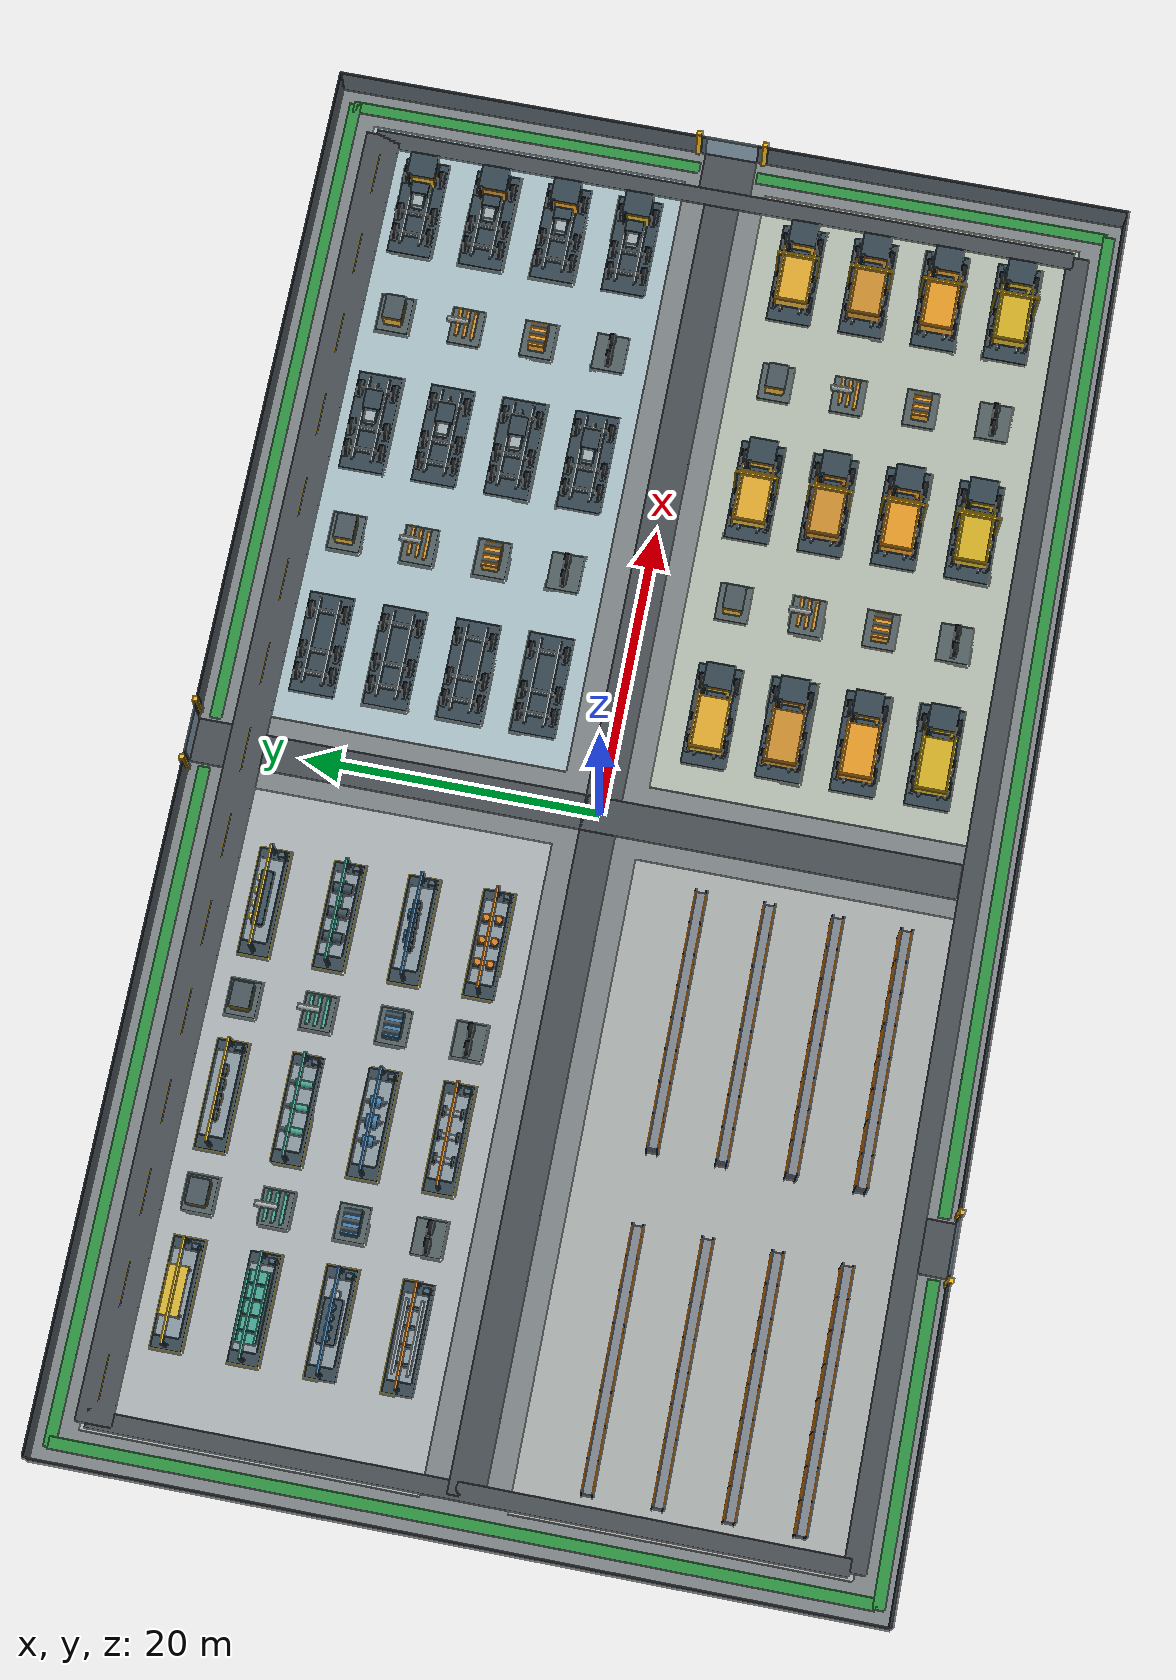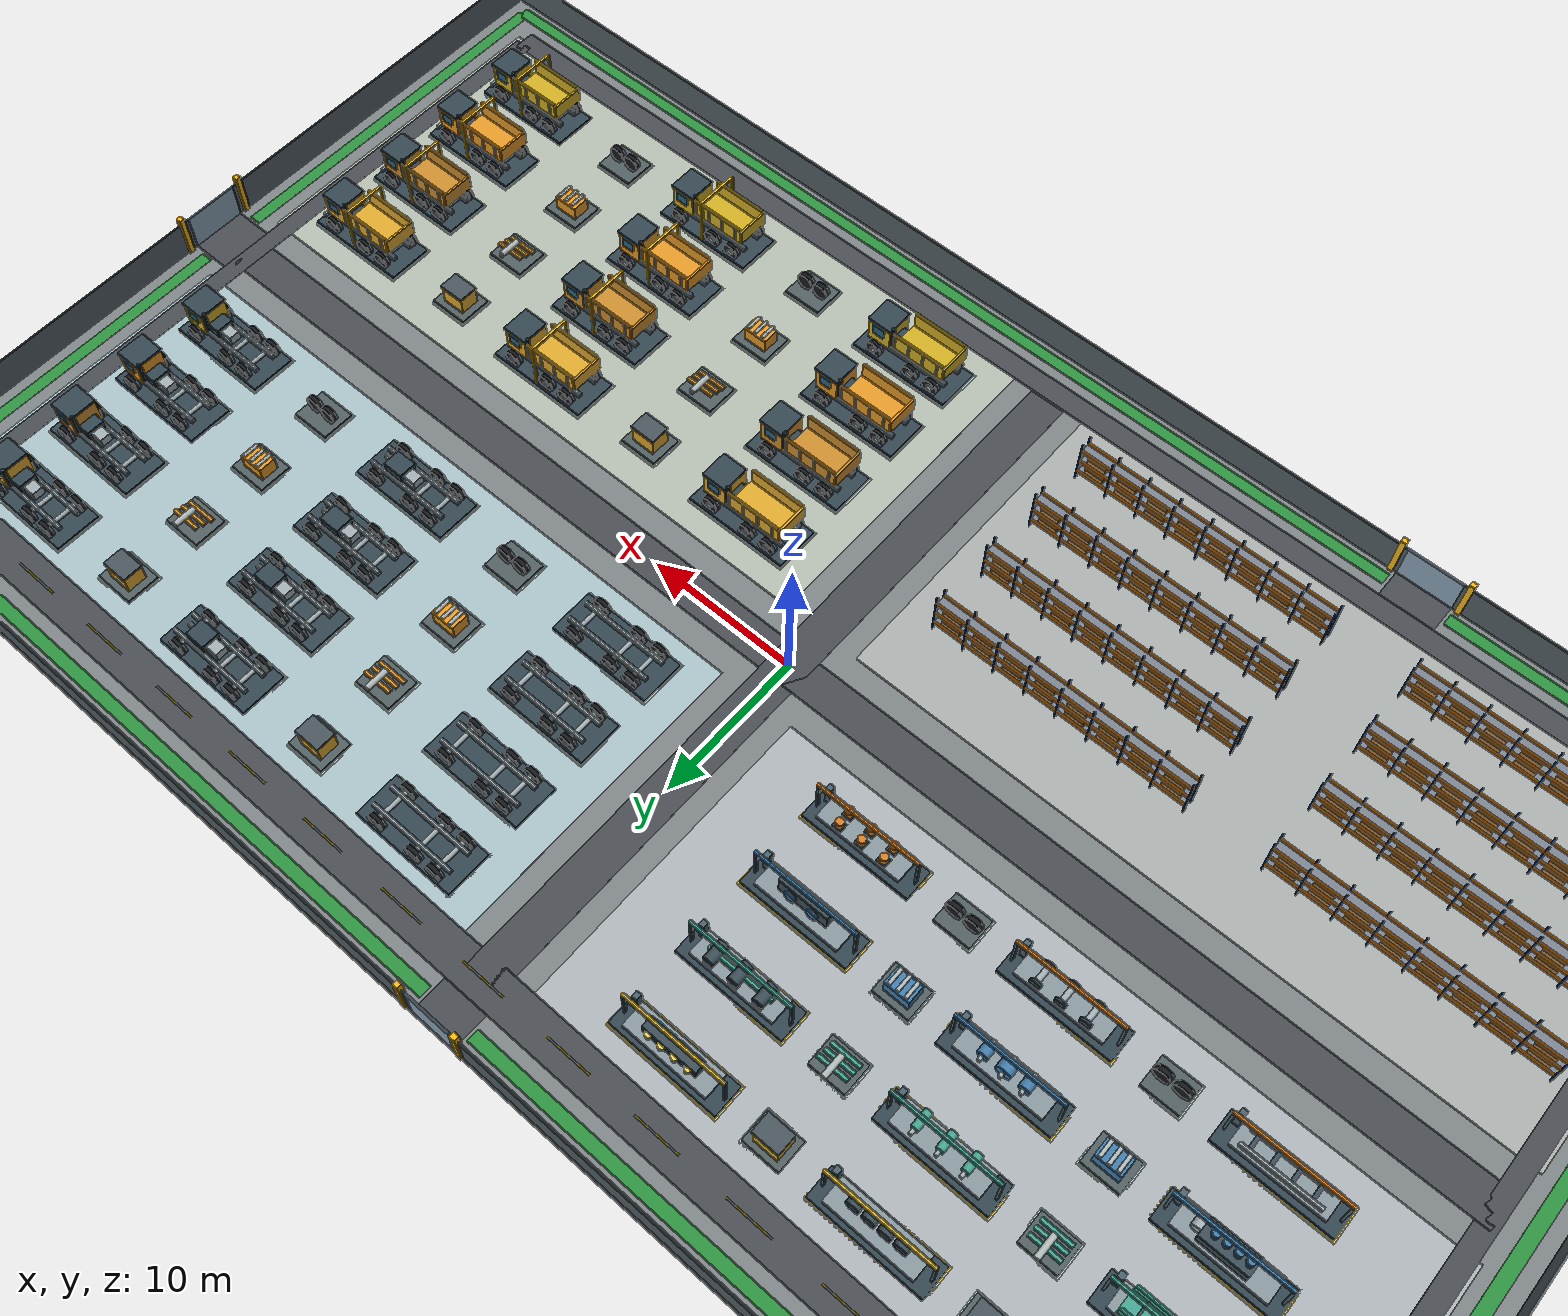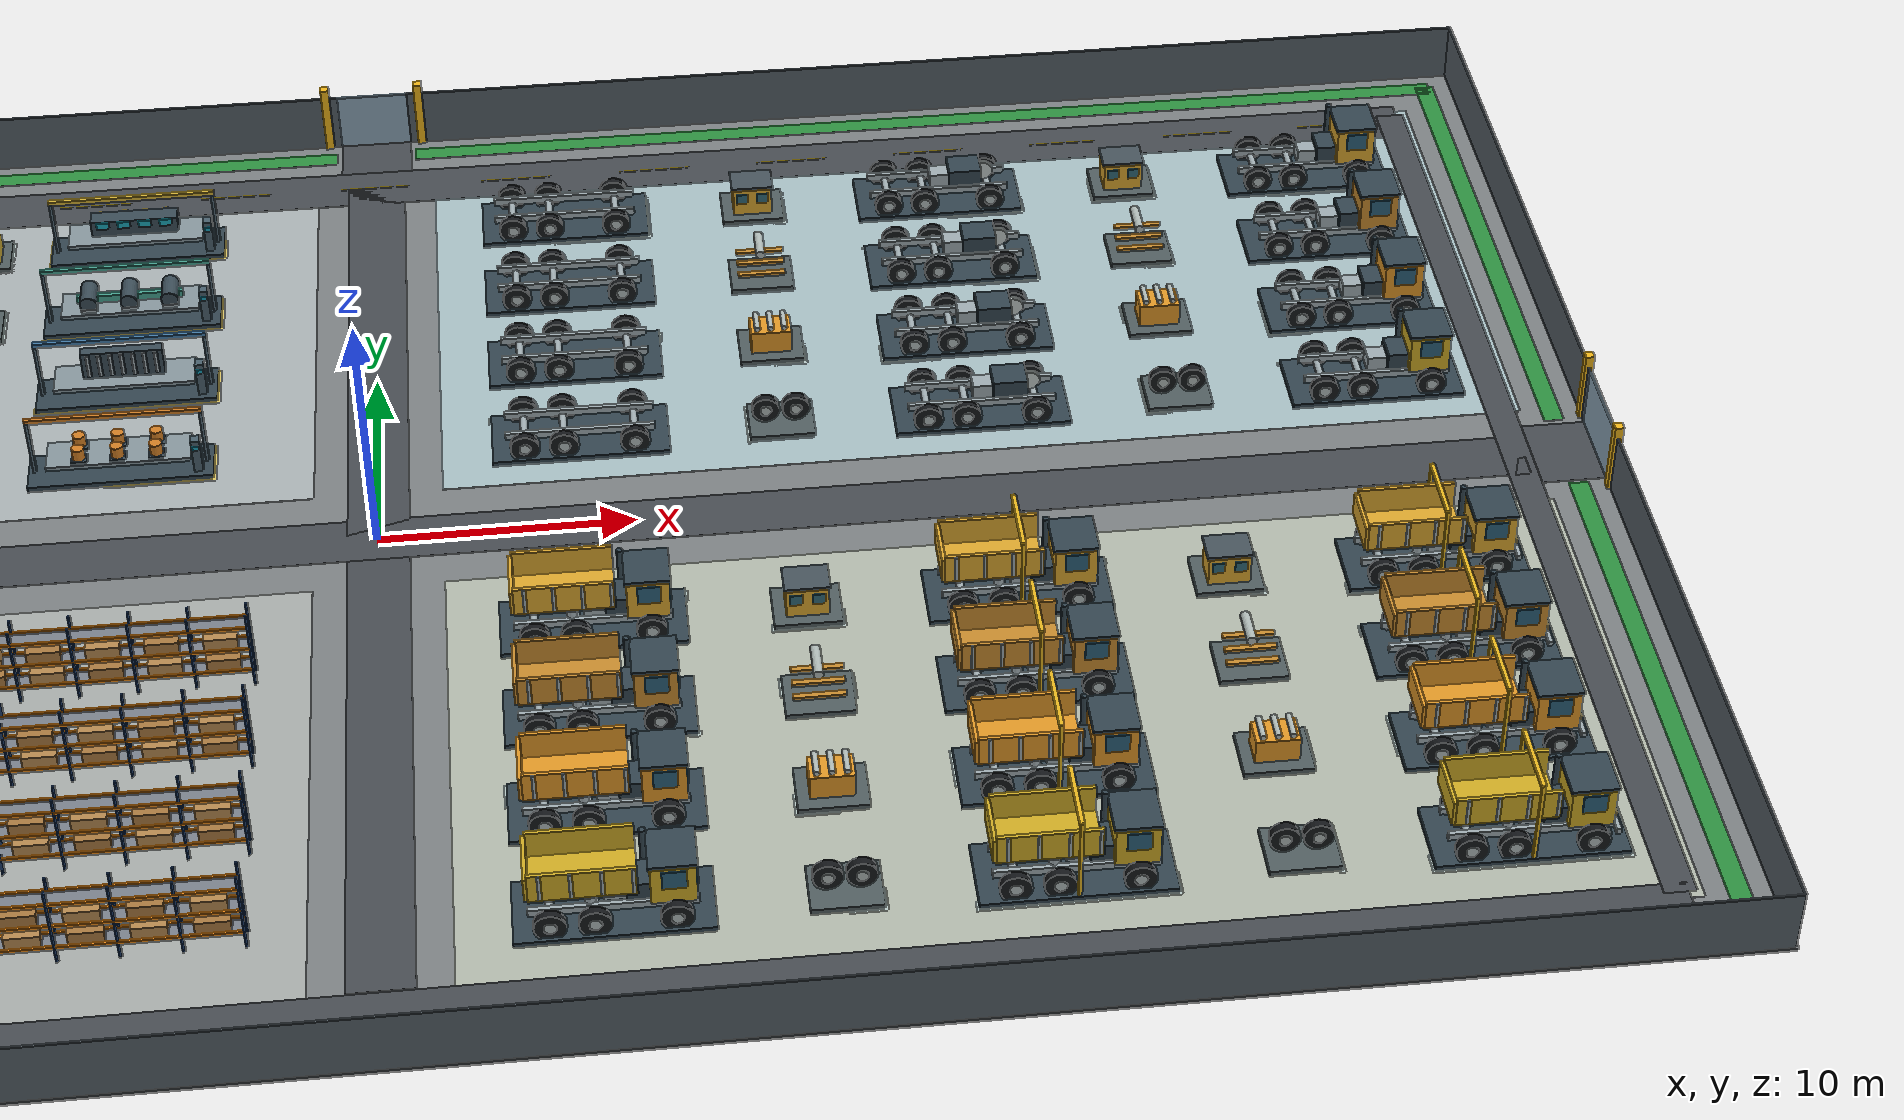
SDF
<?xml version="1.0" ?>
<sdf version="1.7">
  <world name="warehouse_layout_demo">
    <gravity>0 0 -9.8</gravity>
    <plugin name="gazebo_ros_state" filename="libgazebo_ros_state.so">
      <ros><namespace>/gazebo</namespace></ros>
      <update_rate>10.0</update_rate>
    </plugin>
    <physics name="warehouse_physics" type="ode">
      <max_step_size>0.001</max_step_size>
      <real_time_factor>1.0</real_time_factor>
      <real_time_update_rate>1000</real_time_update_rate>
    </physics>
    <scene>
      <ambient>0.65 0.65 0.65 1</ambient>
      <background>0.72 0.76 0.80 1</background>
      <shadows>true</shadows>
    </scene>
    <gui fullscreen="0"><camera name="site_overview">
      <pose>0 -80 72 0 0.76 1.57</pose>
      <view_controller>orbit</view_controller>
    </camera></gui>
    <include><uri>model://sun</uri></include>

    <model name="site_floor">
      <static>true</static>
      <pose>0 0 -0.05 0 0 0</pose>
      <link name="floor">
        <collision name="collision"><geometry><box><size>96.0 55.2 0.10</size></box></geometry></collision>
        <visual name="visual">
          <geometry><box><size>96.0 55.2 0.10</size></box></geometry>
          <material><ambient>0.49 0.51 0.52 1</ambient><diffuse>0.49 0.51 0.52 1</diffuse></material>
        </visual>
      </link>
    </model>
    <model name="sw_working_floor">
      <static>true</static>
      <pose>-24.0 -13.8 0.012 0 0 0</pose>
      <link name="marking">
        <visual name="visual">
          <geometry><box><size>43.0 22.0 0.012</size></box></geometry>

          <material>
            <ambient>0.66 0.68 0.67 1</ambient>
            <diffuse>0.66 0.68 0.67 1</diffuse>
          </material>
        </visual>
      </link>
    </model>
    <model name="se_working_floor">
      <static>true</static>
      <pose>24.0 -13.8 0.012 0 0 0</pose>
      <link name="marking">
        <visual name="visual">
          <geometry><box><size>43.0 22.0 0.012</size></box></geometry>

          <material>
            <ambient>0.70 0.73 0.68 1</ambient>
            <diffuse>0.70 0.73 0.68 1</diffuse>
          </material>
        </visual>
      </link>
    </model>
    <model name="nw_working_floor">
      <static>true</static>
      <pose>-24.0 13.8 0.012 0 0 0</pose>
      <link name="marking">
        <visual name="visual">
          <geometry><box><size>43.0 22.0 0.012</size></box></geometry>

          <material>
            <ambient>0.67 0.70 0.71 1</ambient>
            <diffuse>0.67 0.70 0.71 1</diffuse>
          </material>
        </visual>
      </link>
    </model>
    <model name="ne_working_floor">
      <static>true</static>
      <pose>24.0 13.8 0.012 0 0 0</pose>
      <link name="marking">
        <visual name="visual">
          <geometry><box><size>43.0 22.0 0.012</size></box></geometry>

          <material>
            <ambient>0.66 0.75 0.77 1</ambient>
            <diffuse>0.66 0.75 0.77 1</diffuse>
          </material>
        </visual>
      </link>
    </model>
    <model name="north_access_road">
      <static>true</static>
      <pose>0.0 24.0 0.025 0 0 0</pose>
      <link name="marking">
        <visual name="visual">
          <geometry><box><size>90.0 2.4 0.012</size></box></geometry>

          <material>
            <ambient>0.28 0.30 0.32 1</ambient>
            <diffuse>0.28 0.30 0.32 1</diffuse>
          </material>
        </visual>
      </link>
    </model>
    <model name="south_perimeter_path">
      <static>true</static>
      <pose>0.0 -24.8 0.025 0 0 0</pose>
      <link name="marking">
        <visual name="visual">
          <geometry><box><size>90.0 1.5 0.012</size></box></geometry>

          <material>
            <ambient>0.28 0.30 0.32 1</ambient>
            <diffuse>0.28 0.30 0.32 1</diffuse>
          </material>
        </visual>
      </link>
    </model>
    <model name="west_perimeter_path">
      <static>true</static>
      <pose>-44.7 0.0 0.025 0 0 0</pose>
      <link name="marking">
        <visual name="visual">
          <geometry><box><size>1.2 49.0 0.012</size></box></geometry>

          <material>
            <ambient>0.28 0.30 0.32 1</ambient>
            <diffuse>0.28 0.30 0.32 1</diffuse>
          </material>
        </visual>
      </link>
    </model>
    <model name="east_perimeter_path">
      <static>true</static>
      <pose>44.7 0.0 0.025 0 0 0</pose>
      <link name="marking">
        <visual name="visual">
          <geometry><box><size>1.2 49.0 0.012</size></box></geometry>

          <material>
            <ambient>0.28 0.30 0.32 1</ambient>
            <diffuse>0.28 0.30 0.32 1</diffuse>
          </material>
        </visual>
      </link>
    </model>
    <model name="central_cross_aisle">
      <static>true</static>
      <pose>0.0 0.0 0.025 0 0 0</pose>
      <link name="marking">
        <visual name="visual">
          <geometry><box><size>2.4 48.0 0.012</size></box></geometry>

          <material>
            <ambient>0.28 0.30 0.32 1</ambient>
            <diffuse>0.28 0.30 0.32 1</diffuse>
          </material>
        </visual>
      </link>
    </model>
    <model name="central_long_aisle">
      <static>true</static>
      <pose>0.0 0.0 0.025 0 0 0</pose>
      <link name="marking">
        <visual name="visual">
          <geometry><box><size>90.0 2.4 0.012</size></box></geometry>

          <material>
            <ambient>0.28 0.30 0.32 1</ambient>
            <diffuse>0.28 0.30 0.32 1</diffuse>
          </material>
        </visual>
      </link>
    </model>
    <model name="north_gate_approach">
      <static>true</static>
      <pose>0.0 26.35 0.025 0 0 0</pose>
      <link name="marking">
        <visual name="visual">
          <geometry><box><size>3.0 2.3 0.012</size></box></geometry>

          <material>
            <ambient>0.28 0.30 0.32 1</ambient>
            <diffuse>0.28 0.30 0.32 1</diffuse>
          </material>
        </visual>
      </link>
    </model>
    <model name="south_gate_approach">
      <static>true</static>
      <pose>-24.0 -26.525 0.025 0 0 0</pose>
      <link name="marking">
        <visual name="visual">
          <geometry><box><size>3.6 1.95 0.012</size></box></geometry>

          <material>
            <ambient>0.28 0.30 0.32 1</ambient>
            <diffuse>0.28 0.30 0.32 1</diffuse>
          </material>
        </visual>
      </link>
    </model>
    <model name="east_gate_approach">
      <static>true</static>
      <pose>46.6 0.0 0.025 0 0 0</pose>
      <link name="marking">
        <visual name="visual">
          <geometry><box><size>2.6 3.6 0.012</size></box></geometry>

          <material>
            <ambient>0.28 0.30 0.32 1</ambient>
            <diffuse>0.28 0.30 0.32 1</diffuse>
          </material>
        </visual>
      </link>
    </model>
    <model name="pedestrian_north_west">
      <static>true</static>
      <pose>-24.3 26.4 0.055 0 0 0</pose>
      <link name="marking">
        <visual name="visual">
          <geometry><box><size>45.2 0.8 0.012</size></box></geometry>

          <material>
            <ambient>0.18 0.57 0.25 1</ambient>
            <diffuse>0.18 0.57 0.25 1</diffuse>
          </material>
        </visual>
      </link>
    </model>
    <model name="pedestrian_north_east">
      <static>true</static>
      <pose>24.3 26.4 0.055 0 0 0</pose>
      <link name="marking">
        <visual name="visual">
          <geometry><box><size>45.2 0.8 0.012</size></box></geometry>

          <material>
            <ambient>0.18 0.57 0.25 1</ambient>
            <diffuse>0.18 0.57 0.25 1</diffuse>
          </material>
        </visual>
      </link>
    </model>
    <model name="pedestrian_west">
      <static>true</static>
      <pose>-46.6 0.0 0.055 0 0 0</pose>
      <link name="marking">
        <visual name="visual">
          <geometry><box><size>0.8 53.0 0.012</size></box></geometry>

          <material>
            <ambient>0.18 0.57 0.25 1</ambient>
            <diffuse>0.18 0.57 0.25 1</diffuse>
          </material>
        </visual>
      </link>
    </model>
    <model name="pedestrian_east_south">
      <static>true</static>
      <pose>46.7 -14.25 0.055 0 0 0</pose>
      <link name="marking">
        <visual name="visual">
          <geometry><box><size>0.8 24.5 0.012</size></box></geometry>

          <material>
            <ambient>0.18 0.57 0.25 1</ambient>
            <diffuse>0.18 0.57 0.25 1</diffuse>
          </material>
        </visual>
      </link>
    </model>
    <model name="pedestrian_east_north">
      <static>true</static>
      <pose>46.7 14.25 0.055 0 0 0</pose>
      <link name="marking">
        <visual name="visual">
          <geometry><box><size>0.8 24.5 0.012</size></box></geometry>

          <material>
            <ambient>0.18 0.57 0.25 1</ambient>
            <diffuse>0.18 0.57 0.25 1</diffuse>
          </material>
        </visual>
      </link>
    </model>
    <model name="pedestrian_south_west">
      <static>true</static>
      <pose>-36.45 -26.65 0.055 0 0 0</pose>
      <link name="marking">
        <visual name="visual">
          <geometry><box><size>20.9 0.8 0.012</size></box></geometry>

          <material>
            <ambient>0.18 0.57 0.25 1</ambient>
            <diffuse>0.18 0.57 0.25 1</diffuse>
          </material>
        </visual>
      </link>
    </model>
    <model name="pedestrian_south_east">
      <static>true</static>
      <pose>12.45 -26.65 0.055 0 0 0</pose>
      <link name="marking">
        <visual name="visual">
          <geometry><box><size>68.9 0.8 0.012</size></box></geometry>

          <material>
            <ambient>0.18 0.57 0.25 1</ambient>
            <diffuse>0.18 0.57 0.25 1</diffuse>
          </material>
        </visual>
      </link>
    </model>
    <model name="north_fence_west">
      <static>true</static>
      <pose>-24.7 27.5 1.25 0 0 0</pose>
      <link name="link">
        <collision name="collision">
          <geometry><box><size>46.4 0.09 2.5</size></box></geometry>
          <surface><friction><ode><mu>0.9</mu><mu2>0.9</mu2></ode></friction></surface>
        </collision>
        <visual name="visual">
          <geometry><box><size>46.4 0.09 2.5</size></box></geometry>

          <material>
            <ambient>0.33 0.37 0.40 1</ambient>
            <diffuse>0.33 0.37 0.40 1</diffuse>
          </material>
        </visual>
      </link>
    </model>
    <model name="north_fence_east">
      <static>true</static>
      <pose>24.7 27.5 1.25 0 0 0</pose>
      <link name="link">
        <collision name="collision">
          <geometry><box><size>46.4 0.09 2.5</size></box></geometry>
          <surface><friction><ode><mu>0.9</mu><mu2>0.9</mu2></ode></friction></surface>
        </collision>
        <visual name="visual">
          <geometry><box><size>46.4 0.09 2.5</size></box></geometry>

          <material>
            <ambient>0.33 0.37 0.40 1</ambient>
            <diffuse>0.33 0.37 0.40 1</diffuse>
          </material>
        </visual>
      </link>
    </model>
    <model name="south_fence_west">
      <static>true</static>
      <pose>-36.85 -27.5 1.25 0 0 0</pose>
      <link name="link">
        <collision name="collision">
          <geometry><box><size>22.1 0.09 2.5</size></box></geometry>
          <surface><friction><ode><mu>0.9</mu><mu2>0.9</mu2></ode></friction></surface>
        </collision>
        <visual name="visual">
          <geometry><box><size>22.1 0.09 2.5</size></box></geometry>

          <material>
            <ambient>0.33 0.37 0.40 1</ambient>
            <diffuse>0.33 0.37 0.40 1</diffuse>
          </material>
        </visual>
      </link>
    </model>
    <model name="south_fence_east">
      <static>true</static>
      <pose>12.85 -27.5 1.25 0 0 0</pose>
      <link name="link">
        <collision name="collision">
          <geometry><box><size>70.1 0.09 2.5</size></box></geometry>
          <surface><friction><ode><mu>0.9</mu><mu2>0.9</mu2></ode></friction></surface>
        </collision>
        <visual name="visual">
          <geometry><box><size>70.1 0.09 2.5</size></box></geometry>

          <material>
            <ambient>0.33 0.37 0.40 1</ambient>
            <diffuse>0.33 0.37 0.40 1</diffuse>
          </material>
        </visual>
      </link>
    </model>
    <model name="west_fence">
      <static>true</static>
      <pose>-47.9 0.0 1.25 0 0 0</pose>
      <link name="link">
        <collision name="collision">
          <geometry><box><size>0.09 55.0 2.5</size></box></geometry>
          <surface><friction><ode><mu>0.9</mu><mu2>0.9</mu2></ode></friction></surface>
        </collision>
        <visual name="visual">
          <geometry><box><size>0.09 55.0 2.5</size></box></geometry>

          <material>
            <ambient>0.33 0.37 0.40 1</ambient>
            <diffuse>0.33 0.37 0.40 1</diffuse>
          </material>
        </visual>
      </link>
    </model>
    <model name="east_fence_south">
      <static>true</static>
      <pose>47.9 -14.65 1.25 0 0 0</pose>
      <link name="link">
        <collision name="collision">
          <geometry><box><size>0.09 25.7 2.5</size></box></geometry>
          <surface><friction><ode><mu>0.9</mu><mu2>0.9</mu2></ode></friction></surface>
        </collision>
        <visual name="visual">
          <geometry><box><size>0.09 25.7 2.5</size></box></geometry>

          <material>
            <ambient>0.33 0.37 0.40 1</ambient>
            <diffuse>0.33 0.37 0.40 1</diffuse>
          </material>
        </visual>
      </link>
    </model>
    <model name="east_fence_north">
      <static>true</static>
      <pose>47.9 14.65 1.25 0 0 0</pose>
      <link name="link">
        <collision name="collision">
          <geometry><box><size>0.09 25.7 2.5</size></box></geometry>
          <surface><friction><ode><mu>0.9</mu><mu2>0.9</mu2></ode></friction></surface>
        </collision>
        <visual name="visual">
          <geometry><box><size>0.09 25.7 2.5</size></box></geometry>

          <material>
            <ambient>0.33 0.37 0.40 1</ambient>
            <diffuse>0.33 0.37 0.40 1</diffuse>
          </material>
        </visual>
      </link>
    </model>
    <model name="north_gate_west_post">
      <static>true</static>
      <pose>-2.0 27.5 1.5 0 0 0</pose>
      <link name="link">
        <collision name="collision">
          <geometry><box><size>0.35 0.35 3.0</size></box></geometry>
          <surface><friction><ode><mu>0.9</mu><mu2>0.9</mu2></ode></friction></surface>
        </collision>
        <visual name="visual">
          <geometry><box><size>0.35 0.35 3.0</size></box></geometry>

          <material>
            <ambient>0.95 0.72 0.10 1</ambient>
            <diffuse>0.95 0.72 0.10 1</diffuse>
          </material>
        </visual>
      </link>
    </model>
    <model name="north_gate_east_post">
      <static>true</static>
      <pose>2.0 27.5 1.5 0 0 0</pose>
      <link name="link">
        <collision name="collision">
          <geometry><box><size>0.35 0.35 3.0</size></box></geometry>
          <surface><friction><ode><mu>0.9</mu><mu2>0.9</mu2></ode></friction></surface>
        </collision>
        <visual name="visual">
          <geometry><box><size>0.35 0.35 3.0</size></box></geometry>

          <material>
            <ambient>0.95 0.72 0.10 1</ambient>
            <diffuse>0.95 0.72 0.10 1</diffuse>
          </material>
        </visual>
      </link>
    </model>
    <model name="east_gate_south_post">
      <static>true</static>
      <pose>47.9 -2.3 1.5 0 0 0</pose>
      <link name="link">
        <collision name="collision">
          <geometry><box><size>0.35 0.35 3.0</size></box></geometry>
          <surface><friction><ode><mu>0.9</mu><mu2>0.9</mu2></ode></friction></surface>
        </collision>
        <visual name="visual">
          <geometry><box><size>0.35 0.35 3.0</size></box></geometry>

          <material>
            <ambient>0.95 0.72 0.10 1</ambient>
            <diffuse>0.95 0.72 0.10 1</diffuse>
          </material>
        </visual>
      </link>
    </model>
    <model name="east_gate_north_post">
      <static>true</static>
      <pose>47.9 2.3 1.5 0 0 0</pose>
      <link name="link">
        <collision name="collision">
          <geometry><box><size>0.35 0.35 3.0</size></box></geometry>
          <surface><friction><ode><mu>0.9</mu><mu2>0.9</mu2></ode></friction></surface>
        </collision>
        <visual name="visual">
          <geometry><box><size>0.35 0.35 3.0</size></box></geometry>

          <material>
            <ambient>0.95 0.72 0.10 1</ambient>
            <diffuse>0.95 0.72 0.10 1</diffuse>
          </material>
        </visual>
      </link>
    </model>
    <model name="south_gate_west_post">
      <static>true</static>
      <pose>-26.2 -27.5 1.5 0 0 0</pose>
      <link name="link">
        <collision name="collision">
          <geometry><box><size>0.35 0.35 3.0</size></box></geometry>
          <surface><friction><ode><mu>0.9</mu><mu2>0.9</mu2></ode></friction></surface>
        </collision>
        <visual name="visual">
          <geometry><box><size>0.35 0.35 3.0</size></box></geometry>

          <material>
            <ambient>0.95 0.72 0.10 1</ambient>
            <diffuse>0.95 0.72 0.10 1</diffuse>
          </material>
        </visual>
      </link>
    </model>
    <model name="south_gate_east_post">
      <static>true</static>
      <pose>-21.8 -27.5 1.5 0 0 0</pose>
      <link name="link">
        <collision name="collision">
          <geometry><box><size>0.35 0.35 3.0</size></box></geometry>
          <surface><friction><ode><mu>0.9</mu><mu2>0.9</mu2></ode></friction></surface>
        </collision>
        <visual name="visual">
          <geometry><box><size>0.35 0.35 3.0</size></box></geometry>

          <material>
            <ambient>0.95 0.72 0.10 1</ambient>
            <diffuse>0.95 0.72 0.10 1</diffuse>
          </material>
        </visual>
      </link>
    </model>
    <model name="warehouse_north_gate">
      <static>false</static>
      <pose>0.0 27.5 1.25 0 0 0</pose>
      <link name="panel">
        <kinematic>true</kinematic>
        <gravity>false</gravity>
        <inertial>
          <mass>100.0</mass>
          <inertia><ixx>100.0</ixx><iyy>100.0</iyy><izz>100.0</izz>
            <ixy>0</ixy><ixz>0</ixz><iyz>0</iyz></inertia>
        </inertial>
        <collision name="collision">
          <geometry><box><size>3.0 0.105 2.5</size></box></geometry>
        </collision>
        <visual name="visual">
          <geometry><box><size>3.0 0.105 2.5</size></box></geometry>

          <material>
            <ambient>0.55 0.65 0.72 1</ambient>
            <diffuse>0.55 0.65 0.72 1</diffuse>
          </material>
        </visual>
      </link>
    </model>
    <model name="warehouse_east_gate">
      <static>false</static>
      <pose>47.9 0.0 1.25 0 0 0</pose>
      <link name="panel">
        <kinematic>true</kinematic>
        <gravity>false</gravity>
        <inertial>
          <mass>100.0</mass>
          <inertia><ixx>100.0</ixx><iyy>100.0</iyy><izz>100.0</izz>
            <ixy>0</ixy><ixz>0</ixz><iyz>0</iyz></inertia>
        </inertial>
        <collision name="collision">
          <geometry><box><size>0.105 3.6 2.5</size></box></geometry>
        </collision>
        <visual name="visual">
          <geometry><box><size>0.105 3.6 2.5</size></box></geometry>

          <material>
            <ambient>0.55 0.65 0.72 1</ambient>
            <diffuse>0.55 0.65 0.72 1</diffuse>
          </material>
        </visual>
      </link>
    </model>
    <model name="warehouse_south_gate">
      <static>false</static>
      <pose>-24.0 -27.5 1.25 0 0 0</pose>
      <link name="panel">
        <kinematic>true</kinematic>
        <gravity>false</gravity>
        <inertial>
          <mass>100.0</mass>
          <inertia><ixx>100.0</ixx><iyy>100.0</iyy><izz>100.0</izz>
            <ixy>0</ixy><ixz>0</ixz><iyz>0</iyz></inertia>
        </inertial>
        <collision name="collision">
          <geometry><box><size>3.6 0.105 2.5</size></box></geometry>
        </collision>
        <visual name="visual">
          <geometry><box><size>3.6 0.105 2.5</size></box></geometry>

          <material>
            <ambient>0.55 0.65 0.72 1</ambient>
            <diffuse>0.55 0.65 0.72 1</diffuse>
          </material>
        </visual>
      </link>
    </model>
    <model name="storage_rack_west_1_sw">
      <static>true</static>
      <pose>-35.0 -7.5 0 0 0 0</pose>
      <link name="rack">
        <collision name="rack_footprint">
          <pose>0 0 1.65 0 0 0</pose>
          <geometry><box><size>17.0 0.7 3.3</size></box></geometry>
        </collision>

        <visual name="upright_0_0">
          <pose>-8.5 -0.35 1.65 0 0 0</pose>
          <geometry><box><size>0.10 0.10 3.3</size></box></geometry>

          <material>
            <ambient>0.12 0.24 0.42 1</ambient>
            <diffuse>0.12 0.24 0.42 1</diffuse>
          </material>
        </visual>
        <visual name="upright_0_1">
          <pose>-8.5 0.35 1.65 0 0 0</pose>
          <geometry><box><size>0.10 0.10 3.3</size></box></geometry>

          <material>
            <ambient>0.12 0.24 0.42 1</ambient>
            <diffuse>0.12 0.24 0.42 1</diffuse>
          </material>
        </visual>
        <visual name="upright_1_0">
          <pose>-6.375 -0.35 1.65 0 0 0</pose>
          <geometry><box><size>0.10 0.10 3.3</size></box></geometry>

          <material>
            <ambient>0.12 0.24 0.42 1</ambient>
            <diffuse>0.12 0.24 0.42 1</diffuse>
          </material>
        </visual>
        <visual name="upright_1_1">
          <pose>-6.375 0.35 1.65 0 0 0</pose>
          <geometry><box><size>0.10 0.10 3.3</size></box></geometry>

          <material>
            <ambient>0.12 0.24 0.42 1</ambient>
            <diffuse>0.12 0.24 0.42 1</diffuse>
          </material>
        </visual>
        <visual name="upright_2_0">
          <pose>-4.25 -0.35 1.65 0 0 0</pose>
          <geometry><box><size>0.10 0.10 3.3</size></box></geometry>

          <material>
            <ambient>0.12 0.24 0.42 1</ambient>
            <diffuse>0.12 0.24 0.42 1</diffuse>
          </material>
        </visual>
        <visual name="upright_2_1">
          <pose>-4.25 0.35 1.65 0 0 0</pose>
          <geometry><box><size>0.10 0.10 3.3</size></box></geometry>

          <material>
            <ambient>0.12 0.24 0.42 1</ambient>
            <diffuse>0.12 0.24 0.42 1</diffuse>
          </material>
        </visual>
        <visual name="upright_3_0">
          <pose>-2.125 -0.35 1.65 0 0 0</pose>
          <geometry><box><size>0.10 0.10 3.3</size></box></geometry>

          <material>
            <ambient>0.12 0.24 0.42 1</ambient>
            <diffuse>0.12 0.24 0.42 1</diffuse>
          </material>
        </visual>
        <visual name="upright_3_1">
          <pose>-2.125 0.35 1.65 0 0 0</pose>
          <geometry><box><size>0.10 0.10 3.3</size></box></geometry>

          <material>
            <ambient>0.12 0.24 0.42 1</ambient>
            <diffuse>0.12 0.24 0.42 1</diffuse>
          </material>
        </visual>
        <visual name="upright_4_0">
          <pose>0.0 -0.35 1.65 0 0 0</pose>
          <geometry><box><size>0.10 0.10 3.3</size></box></geometry>

          <material>
            <ambient>0.12 0.24 0.42 1</ambient>
            <diffuse>0.12 0.24 0.42 1</diffuse>
          </material>
        </visual>
        <visual name="upright_4_1">
          <pose>0.0 0.35 1.65 0 0 0</pose>
          <geometry><box><size>0.10 0.10 3.3</size></box></geometry>

          <material>
            <ambient>0.12 0.24 0.42 1</ambient>
            <diffuse>0.12 0.24 0.42 1</diffuse>
          </material>
        </visual>
        <visual name="upright_5_0">
          <pose>2.125 -0.35 1.65 0 0 0</pose>
          <geometry><box><size>0.10 0.10 3.3</size></box></geometry>

          <material>
            <ambient>0.12 0.24 0.42 1</ambient>
            <diffuse>0.12 0.24 0.42 1</diffuse>
          </material>
        </visual>
        <visual name="upright_5_1">
          <pose>2.125 0.35 1.65 0 0 0</pose>
          <geometry><box><size>0.10 0.10 3.3</size></box></geometry>

          <material>
            <ambient>0.12 0.24 0.42 1</ambient>
            <diffuse>0.12 0.24 0.42 1</diffuse>
          </material>
        </visual>
        <visual name="upright_6_0">
          <pose>4.25 -0.35 1.65 0 0 0</pose>
          <geometry><box><size>0.10 0.10 3.3</size></box></geometry>

          <material>
            <ambient>0.12 0.24 0.42 1</ambient>
            <diffuse>0.12 0.24 0.42 1</diffuse>
          </material>
        </visual>
        <visual name="upright_6_1">
          <pose>4.25 0.35 1.65 0 0 0</pose>
          <geometry><box><size>0.10 0.10 3.3</size></box></geometry>

          <material>
            <ambient>0.12 0.24 0.42 1</ambient>
            <diffuse>0.12 0.24 0.42 1</diffuse>
          </material>
        </visual>
        <visual name="upright_7_0">
          <pose>6.375 -0.35 1.65 0 0 0</pose>
          <geometry><box><size>0.10 0.10 3.3</size></box></geometry>

          <material>
            <ambient>0.12 0.24 0.42 1</ambient>
            <diffuse>0.12 0.24 0.42 1</diffuse>
          </material>
        </visual>
        <visual name="upright_7_1">
          <pose>6.375 0.35 1.65 0 0 0</pose>
          <geometry><box><size>0.10 0.10 3.3</size></box></geometry>

          <material>
            <ambient>0.12 0.24 0.42 1</ambient>
            <diffuse>0.12 0.24 0.42 1</diffuse>
          </material>
        </visual>
        <visual name="upright_8_0">
          <pose>8.5 -0.35 1.65 0 0 0</pose>
          <geometry><box><size>0.10 0.10 3.3</size></box></geometry>

          <material>
            <ambient>0.12 0.24 0.42 1</ambient>
            <diffuse>0.12 0.24 0.42 1</diffuse>
          </material>
        </visual>
        <visual name="upright_8_1">
          <pose>8.5 0.35 1.65 0 0 0</pose>
          <geometry><box><size>0.10 0.10 3.3</size></box></geometry>

          <material>
            <ambient>0.12 0.24 0.42 1</ambient>
            <diffuse>0.12 0.24 0.42 1</diffuse>
          </material>
        </visual>
        <visual name="deck_0">
          <pose>0 0 0.65 0 0 0</pose>
          <geometry><box><size>17.0 0.7 0.06</size></box></geometry>

          <material>
            <ambient>0.48 0.51 0.55 1</ambient>
            <diffuse>0.48 0.51 0.55 1</diffuse>
          </material>
        </visual>
        <visual name="beam_0_0">
          <pose>0 -0.35 0.71 0 0 0</pose>
          <geometry><box><size>17.0 0.10 0.12</size></box></geometry>

          <material>
            <ambient>0.95 0.55 0.08 1</ambient>
            <diffuse>0.95 0.55 0.08 1</diffuse>
          </material>
        </visual>
        <visual name="beam_0_1">
          <pose>0 0.35 0.71 0 0 0</pose>
          <geometry><box><size>17.0 0.10 0.12</size></box></geometry>

          <material>
            <ambient>0.95 0.55 0.08 1</ambient>
            <diffuse>0.95 0.55 0.08 1</diffuse>
          </material>
        </visual>
        <visual name="deck_1">
          <pose>0 0 1.65 0 0 0</pose>
          <geometry><box><size>17.0 0.7 0.06</size></box></geometry>

          <material>
            <ambient>0.48 0.51 0.55 1</ambient>
            <diffuse>0.48 0.51 0.55 1</diffuse>
          </material>
        </visual>
        <visual name="beam_1_0">
          <pose>0 -0.35 1.71 0 0 0</pose>
          <geometry><box><size>17.0 0.10 0.12</size></box></geometry>

          <material>
            <ambient>0.95 0.55 0.08 1</ambient>
            <diffuse>0.95 0.55 0.08 1</diffuse>
          </material>
        </visual>
        <visual name="beam_1_1">
          <pose>0 0.35 1.71 0 0 0</pose>
          <geometry><box><size>17.0 0.10 0.12</size></box></geometry>

          <material>
            <ambient>0.95 0.55 0.08 1</ambient>
            <diffuse>0.95 0.55 0.08 1</diffuse>
          </material>
        </visual>
        <visual name="deck_2">
          <pose>0 0 2.65 0 0 0</pose>
          <geometry><box><size>17.0 0.7 0.06</size></box></geometry>

          <material>
            <ambient>0.48 0.51 0.55 1</ambient>
            <diffuse>0.48 0.51 0.55 1</diffuse>
          </material>
        </visual>
        <visual name="beam_2_0">
          <pose>0 -0.35 2.71 0 0 0</pose>
          <geometry><box><size>17.0 0.10 0.12</size></box></geometry>

          <material>
            <ambient>0.95 0.55 0.08 1</ambient>
            <diffuse>0.95 0.55 0.08 1</diffuse>
          </material>
        </visual>
        <visual name="beam_2_1">
          <pose>0 0.35 2.71 0 0 0</pose>
          <geometry><box><size>17.0 0.10 0.12</size></box></geometry>

          <material>
            <ambient>0.95 0.55 0.08 1</ambient>
            <diffuse>0.95 0.55 0.08 1</diffuse>
          </material>
        </visual>
        <visual name="load_0_0">
          <pose>-7.4375 0 0.95 0 0 0</pose>
          <geometry><box><size>1.25 0.504 0.48</size></box></geometry>

          <material>
            <ambient>0.72 0.54 0.31 1</ambient>
            <diffuse>0.72 0.54 0.31 1</diffuse>
          </material>
        </visual>
        <visual name="load_0_1">
          <pose>-7.4375 0 1.95 0 0 0</pose>
          <geometry><box><size>1.25 0.504 0.48</size></box></geometry>

          <material>
            <ambient>0.67 0.48 0.25 1</ambient>
            <diffuse>0.67 0.48 0.25 1</diffuse>
          </material>
        </visual>
        <visual name="load_1_0">
          <pose>-5.3125 0 0.95 0 0 0</pose>
          <geometry><box><size>1.25 0.504 0.48</size></box></geometry>

          <material>
            <ambient>0.67 0.48 0.25 1</ambient>
            <diffuse>0.67 0.48 0.25 1</diffuse>
          </material>
        </visual>
        <visual name="load_1_1">
          <pose>-5.3125 0 1.95 0 0 0</pose>
          <geometry><box><size>1.25 0.504 0.48</size></box></geometry>

          <material>
            <ambient>0.72 0.54 0.31 1</ambient>
            <diffuse>0.72 0.54 0.31 1</diffuse>
          </material>
        </visual>
        <visual name="load_2_0">
          <pose>-3.1875 0 0.95 0 0 0</pose>
          <geometry><box><size>1.25 0.504 0.48</size></box></geometry>

          <material>
            <ambient>0.72 0.54 0.31 1</ambient>
            <diffuse>0.72 0.54 0.31 1</diffuse>
          </material>
        </visual>
        <visual name="load_2_1">
          <pose>-3.1875 0 1.95 0 0 0</pose>
          <geometry><box><size>1.25 0.504 0.48</size></box></geometry>

          <material>
            <ambient>0.67 0.48 0.25 1</ambient>
            <diffuse>0.67 0.48 0.25 1</diffuse>
          </material>
        </visual>
        <visual name="load_3_0">
          <pose>-1.0625 0 0.95 0 0 0</pose>
          <geometry><box><size>1.25 0.504 0.48</size></box></geometry>

          <material>
            <ambient>0.67 0.48 0.25 1</ambient>
            <diffuse>0.67 0.48 0.25 1</diffuse>
          </material>
        </visual>
        <visual name="load_3_1">
          <pose>-1.0625 0 1.95 0 0 0</pose>
          <geometry><box><size>1.25 0.504 0.48</size></box></geometry>

          <material>
            <ambient>0.72 0.54 0.31 1</ambient>
            <diffuse>0.72 0.54 0.31 1</diffuse>
          </material>
        </visual>
        <visual name="load_4_0">
          <pose>1.0625 0 0.95 0 0 0</pose>
          <geometry><box><size>1.25 0.504 0.48</size></box></geometry>

          <material>
            <ambient>0.72 0.54 0.31 1</ambient>
            <diffuse>0.72 0.54 0.31 1</diffuse>
          </material>
        </visual>
        <visual name="load_4_1">
          <pose>1.0625 0 1.95 0 0 0</pose>
          <geometry><box><size>1.25 0.504 0.48</size></box></geometry>

          <material>
            <ambient>0.67 0.48 0.25 1</ambient>
            <diffuse>0.67 0.48 0.25 1</diffuse>
          </material>
        </visual>
        <visual name="load_5_0">
          <pose>3.1875 0 0.95 0 0 0</pose>
          <geometry><box><size>1.25 0.504 0.48</size></box></geometry>

          <material>
            <ambient>0.67 0.48 0.25 1</ambient>
            <diffuse>0.67 0.48 0.25 1</diffuse>
          </material>
        </visual>
        <visual name="load_5_1">
          <pose>3.1875 0 1.95 0 0 0</pose>
          <geometry><box><size>1.25 0.504 0.48</size></box></geometry>

          <material>
            <ambient>0.72 0.54 0.31 1</ambient>
            <diffuse>0.72 0.54 0.31 1</diffuse>
          </material>
        </visual>
        <visual name="load_6_0">
          <pose>5.3125 0 0.95 0 0 0</pose>
          <geometry><box><size>1.25 0.504 0.48</size></box></geometry>

          <material>
            <ambient>0.72 0.54 0.31 1</ambient>
            <diffuse>0.72 0.54 0.31 1</diffuse>
          </material>
        </visual>
        <visual name="load_6_1">
          <pose>5.3125 0 1.95 0 0 0</pose>
          <geometry><box><size>1.25 0.504 0.48</size></box></geometry>

          <material>
            <ambient>0.67 0.48 0.25 1</ambient>
            <diffuse>0.67 0.48 0.25 1</diffuse>
          </material>
        </visual>
        <visual name="load_7_0">
          <pose>7.4375 0 0.95 0 0 0</pose>
          <geometry><box><size>1.25 0.504 0.48</size></box></geometry>

          <material>
            <ambient>0.67 0.48 0.25 1</ambient>
            <diffuse>0.67 0.48 0.25 1</diffuse>
          </material>
        </visual>
        <visual name="load_7_1">
          <pose>7.4375 0 1.95 0 0 0</pose>
          <geometry><box><size>1.25 0.504 0.48</size></box></geometry>

          <material>
            <ambient>0.72 0.54 0.31 1</ambient>
            <diffuse>0.72 0.54 0.31 1</diffuse>
          </material>
        </visual>
      </link>
    </model>
    <model name="storage_rack_west_2_sw">
      <static>true</static>
      <pose>-35.0 -12.0 0 0 0 0</pose>
      <link name="rack">
        <collision name="rack_footprint">
          <pose>0 0 1.65 0 0 0</pose>
          <geometry><box><size>17.0 0.7 3.3</size></box></geometry>
        </collision>

        <visual name="upright_0_0">
          <pose>-8.5 -0.35 1.65 0 0 0</pose>
          <geometry><box><size>0.10 0.10 3.3</size></box></geometry>

          <material>
            <ambient>0.12 0.24 0.42 1</ambient>
            <diffuse>0.12 0.24 0.42 1</diffuse>
          </material>
        </visual>
        <visual name="upright_0_1">
          <pose>-8.5 0.35 1.65 0 0 0</pose>
          <geometry><box><size>0.10 0.10 3.3</size></box></geometry>

          <material>
            <ambient>0.12 0.24 0.42 1</ambient>
            <diffuse>0.12 0.24 0.42 1</diffuse>
          </material>
        </visual>
        <visual name="upright_1_0">
          <pose>-6.375 -0.35 1.65 0 0 0</pose>
          <geometry><box><size>0.10 0.10 3.3</size></box></geometry>

          <material>
            <ambient>0.12 0.24 0.42 1</ambient>
            <diffuse>0.12 0.24 0.42 1</diffuse>
          </material>
        </visual>
        <visual name="upright_1_1">
          <pose>-6.375 0.35 1.65 0 0 0</pose>
          <geometry><box><size>0.10 0.10 3.3</size></box></geometry>

          <material>
            <ambient>0.12 0.24 0.42 1</ambient>
            <diffuse>0.12 0.24 0.42 1</diffuse>
          </material>
        </visual>
        <visual name="upright_2_0">
          <pose>-4.25 -0.35 1.65 0 0 0</pose>
          <geometry><box><size>0.10 0.10 3.3</size></box></geometry>

          <material>
            <ambient>0.12 0.24 0.42 1</ambient>
            <diffuse>0.12 0.24 0.42 1</diffuse>
          </material>
        </visual>
        <visual name="upright_2_1">
          <pose>-4.25 0.35 1.65 0 0 0</pose>
          <geometry><box><size>0.10 0.10 3.3</size></box></geometry>

          <material>
            <ambient>0.12 0.24 0.42 1</ambient>
            <diffuse>0.12 0.24 0.42 1</diffuse>
          </material>
        </visual>
        <visual name="upright_3_0">
          <pose>-2.125 -0.35 1.65 0 0 0</pose>
          <geometry><box><size>0.10 0.10 3.3</size></box></geometry>

          <material>
            <ambient>0.12 0.24 0.42 1</ambient>
            <diffuse>0.12 0.24 0.42 1</diffuse>
          </material>
        </visual>
        <visual name="upright_3_1">
          <pose>-2.125 0.35 1.65 0 0 0</pose>
          <geometry><box><size>0.10 0.10 3.3</size></box></geometry>

          <material>
            <ambient>0.12 0.24 0.42 1</ambient>
            <diffuse>0.12 0.24 0.42 1</diffuse>
          </material>
        </visual>
        <visual name="upright_4_0">
          <pose>0.0 -0.35 1.65 0 0 0</pose>
          <geometry><box><size>0.10 0.10 3.3</size></box></geometry>

          <material>
            <ambient>0.12 0.24 0.42 1</ambient>
            <diffuse>0.12 0.24 0.42 1</diffuse>
          </material>
        </visual>
        <visual name="upright_4_1">
          <pose>0.0 0.35 1.65 0 0 0</pose>
          <geometry><box><size>0.10 0.10 3.3</size></box></geometry>

          <material>
            <ambient>0.12 0.24 0.42 1</ambient>
            <diffuse>0.12 0.24 0.42 1</diffuse>
          </material>
        </visual>
        <visual name="upright_5_0">
          <pose>2.125 -0.35 1.65 0 0 0</pose>
          <geometry><box><size>0.10 0.10 3.3</size></box></geometry>

          <material>
            <ambient>0.12 0.24 0.42 1</ambient>
            <diffuse>0.12 0.24 0.42 1</diffuse>
          </material>
        </visual>
        <visual name="upright_5_1">
          <pose>2.125 0.35 1.65 0 0 0</pose>
          <geometry><box><size>0.10 0.10 3.3</size></box></geometry>

          <material>
            <ambient>0.12 0.24 0.42 1</ambient>
            <diffuse>0.12 0.24 0.42 1</diffuse>
          </material>
        </visual>
        <visual name="upright_6_0">
          <pose>4.25 -0.35 1.65 0 0 0</pose>
          <geometry><box><size>0.10 0.10 3.3</size></box></geometry>

          <material>
            <ambient>0.12 0.24 0.42 1</ambient>
            <diffuse>0.12 0.24 0.42 1</diffuse>
          </material>
        </visual>
        <visual name="upright_6_1">
          <pose>4.25 0.35 1.65 0 0 0</pose>
          <geometry><box><size>0.10 0.10 3.3</size></box></geometry>

          <material>
            <ambient>0.12 0.24 0.42 1</ambient>
            <diffuse>0.12 0.24 0.42 1</diffuse>
          </material>
        </visual>
        <visual name="upright_7_0">
          <pose>6.375 -0.35 1.65 0 0 0</pose>
          <geometry><box><size>0.10 0.10 3.3</size></box></geometry>

          <material>
            <ambient>0.12 0.24 0.42 1</ambient>
            <diffuse>0.12 0.24 0.42 1</diffuse>
          </material>
        </visual>
        <visual name="upright_7_1">
          <pose>6.375 0.35 1.65 0 0 0</pose>
          <geometry><box><size>0.10 0.10 3.3</size></box></geometry>

          <material>
            <ambient>0.12 0.24 0.42 1</ambient>
            <diffuse>0.12 0.24 0.42 1</diffuse>
          </material>
        </visual>
        <visual name="upright_8_0">
          <pose>8.5 -0.35 1.65 0 0 0</pose>
          <geometry><box><size>0.10 0.10 3.3</size></box></geometry>

          <material>
            <ambient>0.12 0.24 0.42 1</ambient>
            <diffuse>0.12 0.24 0.42 1</diffuse>
          </material>
        </visual>
        <visual name="upright_8_1">
          <pose>8.5 0.35 1.65 0 0 0</pose>
          <geometry><box><size>0.10 0.10 3.3</size></box></geometry>

          <material>
            <ambient>0.12 0.24 0.42 1</ambient>
            <diffuse>0.12 0.24 0.42 1</diffuse>
          </material>
        </visual>
        <visual name="deck_0">
          <pose>0 0 0.65 0 0 0</pose>
          <geometry><box><size>17.0 0.7 0.06</size></box></geometry>

          <material>
            <ambient>0.48 0.51 0.55 1</ambient>
            <diffuse>0.48 0.51 0.55 1</diffuse>
          </material>
        </visual>
        <visual name="beam_0_0">
          <pose>0 -0.35 0.71 0 0 0</pose>
          <geometry><box><size>17.0 0.10 0.12</size></box></geometry>

          <material>
            <ambient>0.95 0.55 0.08 1</ambient>
            <diffuse>0.95 0.55 0.08 1</diffuse>
          </material>
        </visual>
        <visual name="beam_0_1">
          <pose>0 0.35 0.71 0 0 0</pose>
          <geometry><box><size>17.0 0.10 0.12</size></box></geometry>

          <material>
            <ambient>0.95 0.55 0.08 1</ambient>
            <diffuse>0.95 0.55 0.08 1</diffuse>
          </material>
        </visual>
        <visual name="deck_1">
          <pose>0 0 1.65 0 0 0</pose>
          <geometry><box><size>17.0 0.7 0.06</size></box></geometry>

          <material>
            <ambient>0.48 0.51 0.55 1</ambient>
            <diffuse>0.48 0.51 0.55 1</diffuse>
          </material>
        </visual>
        <visual name="beam_1_0">
          <pose>0 -0.35 1.71 0 0 0</pose>
          <geometry><box><size>17.0 0.10 0.12</size></box></geometry>

          <material>
            <ambient>0.95 0.55 0.08 1</ambient>
            <diffuse>0.95 0.55 0.08 1</diffuse>
          </material>
        </visual>
        <visual name="beam_1_1">
          <pose>0 0.35 1.71 0 0 0</pose>
          <geometry><box><size>17.0 0.10 0.12</size></box></geometry>

          <material>
            <ambient>0.95 0.55 0.08 1</ambient>
            <diffuse>0.95 0.55 0.08 1</diffuse>
          </material>
        </visual>
        <visual name="deck_2">
          <pose>0 0 2.65 0 0 0</pose>
          <geometry><box><size>17.0 0.7 0.06</size></box></geometry>

          <material>
            <ambient>0.48 0.51 0.55 1</ambient>
            <diffuse>0.48 0.51 0.55 1</diffuse>
          </material>
        </visual>
        <visual name="beam_2_0">
          <pose>0 -0.35 2.71 0 0 0</pose>
          <geometry><box><size>17.0 0.10 0.12</size></box></geometry>

          <material>
            <ambient>0.95 0.55 0.08 1</ambient>
            <diffuse>0.95 0.55 0.08 1</diffuse>
          </material>
        </visual>
        <visual name="beam_2_1">
          <pose>0 0.35 2.71 0 0 0</pose>
          <geometry><box><size>17.0 0.10 0.12</size></box></geometry>

          <material>
            <ambient>0.95 0.55 0.08 1</ambient>
            <diffuse>0.95 0.55 0.08 1</diffuse>
          </material>
        </visual>
        <visual name="load_0_0">
          <pose>-7.4375 0 0.95 0 0 0</pose>
          <geometry><box><size>1.25 0.504 0.48</size></box></geometry>

          <material>
            <ambient>0.72 0.54 0.31 1</ambient>
            <diffuse>0.72 0.54 0.31 1</diffuse>
          </material>
        </visual>
        <visual name="load_0_1">
          <pose>-7.4375 0 1.95 0 0 0</pose>
          <geometry><box><size>1.25 0.504 0.48</size></box></geometry>

          <material>
            <ambient>0.67 0.48 0.25 1</ambient>
            <diffuse>0.67 0.48 0.25 1</diffuse>
          </material>
        </visual>
        <visual name="load_1_0">
          <pose>-5.3125 0 0.95 0 0 0</pose>
          <geometry><box><size>1.25 0.504 0.48</size></box></geometry>

          <material>
            <ambient>0.67 0.48 0.25 1</ambient>
            <diffuse>0.67 0.48 0.25 1</diffuse>
          </material>
        </visual>
        <visual name="load_1_1">
          <pose>-5.3125 0 1.95 0 0 0</pose>
          <geometry><box><size>1.25 0.504 0.48</size></box></geometry>

          <material>
            <ambient>0.72 0.54 0.31 1</ambient>
            <diffuse>0.72 0.54 0.31 1</diffuse>
          </material>
        </visual>
        <visual name="load_2_0">
          <pose>-3.1875 0 0.95 0 0 0</pose>
          <geometry><box><size>1.25 0.504 0.48</size></box></geometry>

          <material>
            <ambient>0.72 0.54 0.31 1</ambient>
            <diffuse>0.72 0.54 0.31 1</diffuse>
          </material>
        </visual>
        <visual name="load_2_1">
          <pose>-3.1875 0 1.95 0 0 0</pose>
          <geometry><box><size>1.25 0.504 0.48</size></box></geometry>

          <material>
            <ambient>0.67 0.48 0.25 1</ambient>
            <diffuse>0.67 0.48 0.25 1</diffuse>
          </material>
        </visual>
        <visual name="load_3_0">
          <pose>-1.0625 0 0.95 0 0 0</pose>
          <geometry><box><size>1.25 0.504 0.48</size></box></geometry>

          <material>
            <ambient>0.67 0.48 0.25 1</ambient>
            <diffuse>0.67 0.48 0.25 1</diffuse>
          </material>
        </visual>
        <visual name="load_3_1">
          <pose>-1.0625 0 1.95 0 0 0</pose>
          <geometry><box><size>1.25 0.504 0.48</size></box></geometry>

          <material>
            <ambient>0.72 0.54 0.31 1</ambient>
            <diffuse>0.72 0.54 0.31 1</diffuse>
          </material>
        </visual>
        <visual name="load_4_0">
          <pose>1.0625 0 0.95 0 0 0</pose>
          <geometry><box><size>1.25 0.504 0.48</size></box></geometry>

          <material>
            <ambient>0.72 0.54 0.31 1</ambient>
            <diffuse>0.72 0.54 0.31 1</diffuse>
          </material>
        </visual>
        <visual name="load_4_1">
          <pose>1.0625 0 1.95 0 0 0</pose>
          <geometry><box><size>1.25 0.504 0.48</size></box></geometry>

          <material>
            <ambient>0.67 0.48 0.25 1</ambient>
            <diffuse>0.67 0.48 0.25 1</diffuse>
          </material>
        </visual>
        <visual name="load_5_0">
          <pose>3.1875 0 0.95 0 0 0</pose>
          <geometry><box><size>1.25 0.504 0.48</size></box></geometry>

          <material>
            <ambient>0.67 0.48 0.25 1</ambient>
            <diffuse>0.67 0.48 0.25 1</diffuse>
          </material>
        </visual>
        <visual name="load_5_1">
          <pose>3.1875 0 1.95 0 0 0</pose>
          <geometry><box><size>1.25 0.504 0.48</size></box></geometry>

          <material>
            <ambient>0.72 0.54 0.31 1</ambient>
            <diffuse>0.72 0.54 0.31 1</diffuse>
          </material>
        </visual>
        <visual name="load_6_0">
          <pose>5.3125 0 0.95 0 0 0</pose>
          <geometry><box><size>1.25 0.504 0.48</size></box></geometry>

          <material>
            <ambient>0.72 0.54 0.31 1</ambient>
            <diffuse>0.72 0.54 0.31 1</diffuse>
          </material>
        </visual>
        <visual name="load_6_1">
          <pose>5.3125 0 1.95 0 0 0</pose>
          <geometry><box><size>1.25 0.504 0.48</size></box></geometry>

          <material>
            <ambient>0.67 0.48 0.25 1</ambient>
            <diffuse>0.67 0.48 0.25 1</diffuse>
          </material>
        </visual>
        <visual name="load_7_0">
          <pose>7.4375 0 0.95 0 0 0</pose>
          <geometry><box><size>1.25 0.504 0.48</size></box></geometry>

          <material>
            <ambient>0.67 0.48 0.25 1</ambient>
            <diffuse>0.67 0.48 0.25 1</diffuse>
          </material>
        </visual>
        <visual name="load_7_1">
          <pose>7.4375 0 1.95 0 0 0</pose>
          <geometry><box><size>1.25 0.504 0.48</size></box></geometry>

          <material>
            <ambient>0.72 0.54 0.31 1</ambient>
            <diffuse>0.72 0.54 0.31 1</diffuse>
          </material>
        </visual>
      </link>
    </model>
    <model name="storage_rack_west_3_sw">
      <static>true</static>
      <pose>-35.0 -16.5 0 0 0 0</pose>
      <link name="rack">
        <collision name="rack_footprint">
          <pose>0 0 1.65 0 0 0</pose>
          <geometry><box><size>17.0 0.7 3.3</size></box></geometry>
        </collision>

        <visual name="upright_0_0">
          <pose>-8.5 -0.35 1.65 0 0 0</pose>
          <geometry><box><size>0.10 0.10 3.3</size></box></geometry>

          <material>
            <ambient>0.12 0.24 0.42 1</ambient>
            <diffuse>0.12 0.24 0.42 1</diffuse>
          </material>
        </visual>
        <visual name="upright_0_1">
          <pose>-8.5 0.35 1.65 0 0 0</pose>
          <geometry><box><size>0.10 0.10 3.3</size></box></geometry>

          <material>
            <ambient>0.12 0.24 0.42 1</ambient>
            <diffuse>0.12 0.24 0.42 1</diffuse>
          </material>
        </visual>
        <visual name="upright_1_0">
          <pose>-6.375 -0.35 1.65 0 0 0</pose>
          <geometry><box><size>0.10 0.10 3.3</size></box></geometry>

          <material>
            <ambient>0.12 0.24 0.42 1</ambient>
            <diffuse>0.12 0.24 0.42 1</diffuse>
          </material>
        </visual>
        <visual name="upright_1_1">
          <pose>-6.375 0.35 1.65 0 0 0</pose>
          <geometry><box><size>0.10 0.10 3.3</size></box></geometry>

          <material>
            <ambient>0.12 0.24 0.42 1</ambient>
            <diffuse>0.12 0.24 0.42 1</diffuse>
          </material>
        </visual>
        <visual name="upright_2_0">
          <pose>-4.25 -0.35 1.65 0 0 0</pose>
          <geometry><box><size>0.10 0.10 3.3</size></box></geometry>

          <material>
            <ambient>0.12 0.24 0.42 1</ambient>
            <diffuse>0.12 0.24 0.42 1</diffuse>
          </material>
        </visual>
        <visual name="upright_2_1">
          <pose>-4.25 0.35 1.65 0 0 0</pose>
          <geometry><box><size>0.10 0.10 3.3</size></box></geometry>

          <material>
            <ambient>0.12 0.24 0.42 1</ambient>
            <diffuse>0.12 0.24 0.42 1</diffuse>
          </material>
        </visual>
        <visual name="upright_3_0">
          <pose>-2.125 -0.35 1.65 0 0 0</pose>
          <geometry><box><size>0.10 0.10 3.3</size></box></geometry>

          <material>
            <ambient>0.12 0.24 0.42 1</ambient>
            <diffuse>0.12 0.24 0.42 1</diffuse>
          </material>
        </visual>
        <visual name="upright_3_1">
          <pose>-2.125 0.35 1.65 0 0 0</pose>
          <geometry><box><size>0.10 0.10 3.3</size></box></geometry>

          <material>
            <ambient>0.12 0.24 0.42 1</ambient>
            <diffuse>0.12 0.24 0.42 1</diffuse>
          </material>
        </visual>
        <visual name="upright_4_0">
          <pose>0.0 -0.35 1.65 0 0 0</pose>
          <geometry><box><size>0.10 0.10 3.3</size></box></geometry>

          <material>
            <ambient>0.12 0.24 0.42 1</ambient>
            <diffuse>0.12 0.24 0.42 1</diffuse>
          </material>
        </visual>
        <visual name="upright_4_1">
          <pose>0.0 0.35 1.65 0 0 0</pose>
          <geometry><box><size>0.10 0.10 3.3</size></box></geometry>

          <material>
            <ambient>0.12 0.24 0.42 1</ambient>
            <diffuse>0.12 0.24 0.42 1</diffuse>
          </material>
        </visual>
        <visual name="upright_5_0">
          <pose>2.125 -0.35 1.65 0 0 0</pose>
          <geometry><box><size>0.10 0.10 3.3</size></box></geometry>

          <material>
            <ambient>0.12 0.24 0.42 1</ambient>
            <diffuse>0.12 0.24 0.42 1</diffuse>
          </material>
        </visual>
        <visual name="upright_5_1">
          <pose>2.125 0.35 1.65 0 0 0</pose>
          <geometry><box><size>0.10 0.10 3.3</size></box></geometry>

          <material>
            <ambient>0.12 0.24 0.42 1</ambient>
            <diffuse>0.12 0.24 0.42 1</diffuse>
          </material>
        </visual>
        <visual name="upright_6_0">
          <pose>4.25 -0.35 1.65 0 0 0</pose>
          <geometry><box><size>0.10 0.10 3.3</size></box></geometry>

          <material>
            <ambient>0.12 0.24 0.42 1</ambient>
            <diffuse>0.12 0.24 0.42 1</diffuse>
          </material>
        </visual>
        <visual name="upright_6_1">
          <pose>4.25 0.35 1.65 0 0 0</pose>
          <geometry><box><size>0.10 0.10 3.3</size></box></geometry>

          <material>
            <ambient>0.12 0.24 0.42 1</ambient>
            <diffuse>0.12 0.24 0.42 1</diffuse>
          </material>
        </visual>
        <visual name="upright_7_0">
          <pose>6.375 -0.35 1.65 0 0 0</pose>
          <geometry><box><size>0.10 0.10 3.3</size></box></geometry>

          <material>
            <ambient>0.12 0.24 0.42 1</ambient>
            <diffuse>0.12 0.24 0.42 1</diffuse>
          </material>
        </visual>
        <visual name="upright_7_1">
          <pose>6.375 0.35 1.65 0 0 0</pose>
          <geometry><box><size>0.10 0.10 3.3</size></box></geometry>

          <material>
            <ambient>0.12 0.24 0.42 1</ambient>
            <diffuse>0.12 0.24 0.42 1</diffuse>
          </material>
        </visual>
        <visual name="upright_8_0">
          <pose>8.5 -0.35 1.65 0 0 0</pose>
          <geometry><box><size>0.10 0.10 3.3</size></box></geometry>

          <material>
            <ambient>0.12 0.24 0.42 1</ambient>
            <diffuse>0.12 0.24 0.42 1</diffuse>
          </material>
        </visual>
        <visual name="upright_8_1">
          <pose>8.5 0.35 1.65 0 0 0</pose>
          <geometry><box><size>0.10 0.10 3.3</size></box></geometry>

          <material>
            <ambient>0.12 0.24 0.42 1</ambient>
            <diffuse>0.12 0.24 0.42 1</diffuse>
          </material>
        </visual>
        <visual name="deck_0">
          <pose>0 0 0.65 0 0 0</pose>
          <geometry><box><size>17.0 0.7 0.06</size></box></geometry>

          <material>
            <ambient>0.48 0.51 0.55 1</ambient>
            <diffuse>0.48 0.51 0.55 1</diffuse>
          </material>
        </visual>
        <visual name="beam_0_0">
          <pose>0 -0.35 0.71 0 0 0</pose>
          <geometry><box><size>17.0 0.10 0.12</size></box></geometry>

          <material>
            <ambient>0.95 0.55 0.08 1</ambient>
            <diffuse>0.95 0.55 0.08 1</diffuse>
          </material>
        </visual>
        <visual name="beam_0_1">
          <pose>0 0.35 0.71 0 0 0</pose>
          <geometry><box><size>17.0 0.10 0.12</size></box></geometry>

          <material>
            <ambient>0.95 0.55 0.08 1</ambient>
            <diffuse>0.95 0.55 0.08 1</diffuse>
          </material>
        </visual>
        <visual name="deck_1">
          <pose>0 0 1.65 0 0 0</pose>
          <geometry><box><size>17.0 0.7 0.06</size></box></geometry>

          <material>
            <ambient>0.48 0.51 0.55 1</ambient>
            <diffuse>0.48 0.51 0.55 1</diffuse>
          </material>
        </visual>
        <visual name="beam_1_0">
          <pose>0 -0.35 1.71 0 0 0</pose>
          <geometry><box><size>17.0 0.10 0.12</size></box></geometry>

          <material>
            <ambient>0.95 0.55 0.08 1</ambient>
            <diffuse>0.95 0.55 0.08 1</diffuse>
          </material>
        </visual>
        <visual name="beam_1_1">
          <pose>0 0.35 1.71 0 0 0</pose>
          <geometry><box><size>17.0 0.10 0.12</size></box></geometry>

          <material>
            <ambient>0.95 0.55 0.08 1</ambient>
            <diffuse>0.95 0.55 0.08 1</diffuse>
          </material>
        </visual>
        <visual name="deck_2">
          <pose>0 0 2.65 0 0 0</pose>
          <geometry><box><size>17.0 0.7 0.06</size></box></geometry>

          <material>
            <ambient>0.48 0.51 0.55 1</ambient>
            <diffuse>0.48 0.51 0.55 1</diffuse>
          </material>
        </visual>
        <visual name="beam_2_0">
          <pose>0 -0.35 2.71 0 0 0</pose>
          <geometry><box><size>17.0 0.10 0.12</size></box></geometry>

          <material>
            <ambient>0.95 0.55 0.08 1</ambient>
            <diffuse>0.95 0.55 0.08 1</diffuse>
          </material>
        </visual>
        <visual name="beam_2_1">
          <pose>0 0.35 2.71 0 0 0</pose>
          <geometry><box><size>17.0 0.10 0.12</size></box></geometry>

          <material>
            <ambient>0.95 0.55 0.08 1</ambient>
            <diffuse>0.95 0.55 0.08 1</diffuse>
          </material>
        </visual>
        <visual name="load_0_0">
          <pose>-7.4375 0 0.95 0 0 0</pose>
          <geometry><box><size>1.25 0.504 0.48</size></box></geometry>

          <material>
            <ambient>0.72 0.54 0.31 1</ambient>
            <diffuse>0.72 0.54 0.31 1</diffuse>
          </material>
        </visual>
        <visual name="load_0_1">
          <pose>-7.4375 0 1.95 0 0 0</pose>
          <geometry><box><size>1.25 0.504 0.48</size></box></geometry>

          <material>
            <ambient>0.67 0.48 0.25 1</ambient>
            <diffuse>0.67 0.48 0.25 1</diffuse>
          </material>
        </visual>
        <visual name="load_1_0">
          <pose>-5.3125 0 0.95 0 0 0</pose>
          <geometry><box><size>1.25 0.504 0.48</size></box></geometry>

          <material>
            <ambient>0.67 0.48 0.25 1</ambient>
            <diffuse>0.67 0.48 0.25 1</diffuse>
          </material>
        </visual>
        <visual name="load_1_1">
          <pose>-5.3125 0 1.95 0 0 0</pose>
          <geometry><box><size>1.25 0.504 0.48</size></box></geometry>

          <material>
            <ambient>0.72 0.54 0.31 1</ambient>
            <diffuse>0.72 0.54 0.31 1</diffuse>
          </material>
        </visual>
        <visual name="load_2_0">
          <pose>-3.1875 0 0.95 0 0 0</pose>
          <geometry><box><size>1.25 0.504 0.48</size></box></geometry>

          <material>
            <ambient>0.72 0.54 0.31 1</ambient>
            <diffuse>0.72 0.54 0.31 1</diffuse>
          </material>
        </visual>
        <visual name="load_2_1">
          <pose>-3.1875 0 1.95 0 0 0</pose>
          <geometry><box><size>1.25 0.504 0.48</size></box></geometry>

          <material>
            <ambient>0.67 0.48 0.25 1</ambient>
            <diffuse>0.67 0.48 0.25 1</diffuse>
          </material>
        </visual>
        <visual name="load_3_0">
          <pose>-1.0625 0 0.95 0 0 0</pose>
          <geometry><box><size>1.25 0.504 0.48</size></box></geometry>

          <material>
            <ambient>0.67 0.48 0.25 1</ambient>
            <diffuse>0.67 0.48 0.25 1</diffuse>
          </material>
        </visual>
        <visual name="load_3_1">
          <pose>-1.0625 0 1.95 0 0 0</pose>
          <geometry><box><size>1.25 0.504 0.48</size></box></geometry>

          <material>
            <ambient>0.72 0.54 0.31 1</ambient>
            <diffuse>0.72 0.54 0.31 1</diffuse>
          </material>
        </visual>
        <visual name="load_4_0">
          <pose>1.0625 0 0.95 0 0 0</pose>
          <geometry><box><size>1.25 0.504 0.48</size></box></geometry>

          <material>
            <ambient>0.72 0.54 0.31 1</ambient>
            <diffuse>0.72 0.54 0.31 1</diffuse>
          </material>
        </visual>
        <visual name="load_4_1">
          <pose>1.0625 0 1.95 0 0 0</pose>
          <geometry><box><size>1.25 0.504 0.48</size></box></geometry>

          <material>
            <ambient>0.67 0.48 0.25 1</ambient>
            <diffuse>0.67 0.48 0.25 1</diffuse>
          </material>
        </visual>
        <visual name="load_5_0">
          <pose>3.1875 0 0.95 0 0 0</pose>
          <geometry><box><size>1.25 0.504 0.48</size></box></geometry>

          <material>
            <ambient>0.67 0.48 0.25 1</ambient>
            <diffuse>0.67 0.48 0.25 1</diffuse>
          </material>
        </visual>
        <visual name="load_5_1">
          <pose>3.1875 0 1.95 0 0 0</pose>
          <geometry><box><size>1.25 0.504 0.48</size></box></geometry>

          <material>
            <ambient>0.72 0.54 0.31 1</ambient>
            <diffuse>0.72 0.54 0.31 1</diffuse>
          </material>
        </visual>
        <visual name="load_6_0">
          <pose>5.3125 0 0.95 0 0 0</pose>
          <geometry><box><size>1.25 0.504 0.48</size></box></geometry>

          <material>
            <ambient>0.72 0.54 0.31 1</ambient>
            <diffuse>0.72 0.54 0.31 1</diffuse>
          </material>
        </visual>
        <visual name="load_6_1">
          <pose>5.3125 0 1.95 0 0 0</pose>
          <geometry><box><size>1.25 0.504 0.48</size></box></geometry>

          <material>
            <ambient>0.67 0.48 0.25 1</ambient>
            <diffuse>0.67 0.48 0.25 1</diffuse>
          </material>
        </visual>
        <visual name="load_7_0">
          <pose>7.4375 0 0.95 0 0 0</pose>
          <geometry><box><size>1.25 0.504 0.48</size></box></geometry>

          <material>
            <ambient>0.67 0.48 0.25 1</ambient>
            <diffuse>0.67 0.48 0.25 1</diffuse>
          </material>
        </visual>
        <visual name="load_7_1">
          <pose>7.4375 0 1.95 0 0 0</pose>
          <geometry><box><size>1.25 0.504 0.48</size></box></geometry>

          <material>
            <ambient>0.72 0.54 0.31 1</ambient>
            <diffuse>0.72 0.54 0.31 1</diffuse>
          </material>
        </visual>
      </link>
    </model>
    <model name="storage_rack_west_4_sw">
      <static>true</static>
      <pose>-35.0 -21.0 0 0 0 0</pose>
      <link name="rack">
        <collision name="rack_footprint">
          <pose>0 0 1.65 0 0 0</pose>
          <geometry><box><size>17.0 0.7 3.3</size></box></geometry>
        </collision>

        <visual name="upright_0_0">
          <pose>-8.5 -0.35 1.65 0 0 0</pose>
          <geometry><box><size>0.10 0.10 3.3</size></box></geometry>

          <material>
            <ambient>0.12 0.24 0.42 1</ambient>
            <diffuse>0.12 0.24 0.42 1</diffuse>
          </material>
        </visual>
        <visual name="upright_0_1">
          <pose>-8.5 0.35 1.65 0 0 0</pose>
          <geometry><box><size>0.10 0.10 3.3</size></box></geometry>

          <material>
            <ambient>0.12 0.24 0.42 1</ambient>
            <diffuse>0.12 0.24 0.42 1</diffuse>
          </material>
        </visual>
        <visual name="upright_1_0">
          <pose>-6.375 -0.35 1.65 0 0 0</pose>
          <geometry><box><size>0.10 0.10 3.3</size></box></geometry>

          <material>
            <ambient>0.12 0.24 0.42 1</ambient>
            <diffuse>0.12 0.24 0.42 1</diffuse>
          </material>
        </visual>
        <visual name="upright_1_1">
          <pose>-6.375 0.35 1.65 0 0 0</pose>
          <geometry><box><size>0.10 0.10 3.3</size></box></geometry>

          <material>
            <ambient>0.12 0.24 0.42 1</ambient>
            <diffuse>0.12 0.24 0.42 1</diffuse>
          </material>
        </visual>
        <visual name="upright_2_0">
          <pose>-4.25 -0.35 1.65 0 0 0</pose>
          <geometry><box><size>0.10 0.10 3.3</size></box></geometry>

          <material>
            <ambient>0.12 0.24 0.42 1</ambient>
            <diffuse>0.12 0.24 0.42 1</diffuse>
          </material>
        </visual>
        <visual name="upright_2_1">
          <pose>-4.25 0.35 1.65 0 0 0</pose>
          <geometry><box><size>0.10 0.10 3.3</size></box></geometry>

          <material>
            <ambient>0.12 0.24 0.42 1</ambient>
            <diffuse>0.12 0.24 0.42 1</diffuse>
          </material>
        </visual>
        <visual name="upright_3_0">
          <pose>-2.125 -0.35 1.65 0 0 0</pose>
          <geometry><box><size>0.10 0.10 3.3</size></box></geometry>

          <material>
            <ambient>0.12 0.24 0.42 1</ambient>
            <diffuse>0.12 0.24 0.42 1</diffuse>
          </material>
        </visual>
        <visual name="upright_3_1">
          <pose>-2.125 0.35 1.65 0 0 0</pose>
          <geometry><box><size>0.10 0.10 3.3</size></box></geometry>

          <material>
            <ambient>0.12 0.24 0.42 1</ambient>
            <diffuse>0.12 0.24 0.42 1</diffuse>
          </material>
        </visual>
        <visual name="upright_4_0">
          <pose>0.0 -0.35 1.65 0 0 0</pose>
          <geometry><box><size>0.10 0.10 3.3</size></box></geometry>

          <material>
            <ambient>0.12 0.24 0.42 1</ambient>
            <diffuse>0.12 0.24 0.42 1</diffuse>
          </material>
        </visual>
        <visual name="upright_4_1">
          <pose>0.0 0.35 1.65 0 0 0</pose>
          <geometry><box><size>0.10 0.10 3.3</size></box></geometry>

          <material>
            <ambient>0.12 0.24 0.42 1</ambient>
            <diffuse>0.12 0.24 0.42 1</diffuse>
          </material>
        </visual>
        <visual name="upright_5_0">
          <pose>2.125 -0.35 1.65 0 0 0</pose>
          <geometry><box><size>0.10 0.10 3.3</size></box></geometry>

          <material>
            <ambient>0.12 0.24 0.42 1</ambient>
            <diffuse>0.12 0.24 0.42 1</diffuse>
          </material>
        </visual>
        <visual name="upright_5_1">
          <pose>2.125 0.35 1.65 0 0 0</pose>
          <geometry><box><size>0.10 0.10 3.3</size></box></geometry>

          <material>
            <ambient>0.12 0.24 0.42 1</ambient>
            <diffuse>0.12 0.24 0.42 1</diffuse>
          </material>
        </visual>
        <visual name="upright_6_0">
          <pose>4.25 -0.35 1.65 0 0 0</pose>
          <geometry><box><size>0.10 0.10 3.3</size></box></geometry>

          <material>
            <ambient>0.12 0.24 0.42 1</ambient>
            <diffuse>0.12 0.24 0.42 1</diffuse>
          </material>
        </visual>
        <visual name="upright_6_1">
          <pose>4.25 0.35 1.65 0 0 0</pose>
          <geometry><box><size>0.10 0.10 3.3</size></box></geometry>

          <material>
            <ambient>0.12 0.24 0.42 1</ambient>
            <diffuse>0.12 0.24 0.42 1</diffuse>
          </material>
        </visual>
        <visual name="upright_7_0">
          <pose>6.375 -0.35 1.65 0 0 0</pose>
          <geometry><box><size>0.10 0.10 3.3</size></box></geometry>

          <material>
            <ambient>0.12 0.24 0.42 1</ambient>
            <diffuse>0.12 0.24 0.42 1</diffuse>
          </material>
        </visual>
        <visual name="upright_7_1">
          <pose>6.375 0.35 1.65 0 0 0</pose>
          <geometry><box><size>0.10 0.10 3.3</size></box></geometry>

          <material>
            <ambient>0.12 0.24 0.42 1</ambient>
            <diffuse>0.12 0.24 0.42 1</diffuse>
          </material>
        </visual>
        <visual name="upright_8_0">
          <pose>8.5 -0.35 1.65 0 0 0</pose>
          <geometry><box><size>0.10 0.10 3.3</size></box></geometry>

          <material>
            <ambient>0.12 0.24 0.42 1</ambient>
            <diffuse>0.12 0.24 0.42 1</diffuse>
          </material>
        </visual>
        <visual name="upright_8_1">
          <pose>8.5 0.35 1.65 0 0 0</pose>
          <geometry><box><size>0.10 0.10 3.3</size></box></geometry>

          <material>
            <ambient>0.12 0.24 0.42 1</ambient>
            <diffuse>0.12 0.24 0.42 1</diffuse>
          </material>
        </visual>
        <visual name="deck_0">
          <pose>0 0 0.65 0 0 0</pose>
          <geometry><box><size>17.0 0.7 0.06</size></box></geometry>

          <material>
            <ambient>0.48 0.51 0.55 1</ambient>
            <diffuse>0.48 0.51 0.55 1</diffuse>
          </material>
        </visual>
        <visual name="beam_0_0">
          <pose>0 -0.35 0.71 0 0 0</pose>
          <geometry><box><size>17.0 0.10 0.12</size></box></geometry>

          <material>
            <ambient>0.95 0.55 0.08 1</ambient>
            <diffuse>0.95 0.55 0.08 1</diffuse>
          </material>
        </visual>
        <visual name="beam_0_1">
          <pose>0 0.35 0.71 0 0 0</pose>
          <geometry><box><size>17.0 0.10 0.12</size></box></geometry>

          <material>
            <ambient>0.95 0.55 0.08 1</ambient>
            <diffuse>0.95 0.55 0.08 1</diffuse>
          </material>
        </visual>
        <visual name="deck_1">
          <pose>0 0 1.65 0 0 0</pose>
          <geometry><box><size>17.0 0.7 0.06</size></box></geometry>

          <material>
            <ambient>0.48 0.51 0.55 1</ambient>
            <diffuse>0.48 0.51 0.55 1</diffuse>
          </material>
        </visual>
        <visual name="beam_1_0">
          <pose>0 -0.35 1.71 0 0 0</pose>
          <geometry><box><size>17.0 0.10 0.12</size></box></geometry>

          <material>
            <ambient>0.95 0.55 0.08 1</ambient>
            <diffuse>0.95 0.55 0.08 1</diffuse>
          </material>
        </visual>
        <visual name="beam_1_1">
          <pose>0 0.35 1.71 0 0 0</pose>
          <geometry><box><size>17.0 0.10 0.12</size></box></geometry>

          <material>
            <ambient>0.95 0.55 0.08 1</ambient>
            <diffuse>0.95 0.55 0.08 1</diffuse>
          </material>
        </visual>
        <visual name="deck_2">
          <pose>0 0 2.65 0 0 0</pose>
          <geometry><box><size>17.0 0.7 0.06</size></box></geometry>

          <material>
            <ambient>0.48 0.51 0.55 1</ambient>
            <diffuse>0.48 0.51 0.55 1</diffuse>
          </material>
        </visual>
        <visual name="beam_2_0">
          <pose>0 -0.35 2.71 0 0 0</pose>
          <geometry><box><size>17.0 0.10 0.12</size></box></geometry>

          <material>
            <ambient>0.95 0.55 0.08 1</ambient>
            <diffuse>0.95 0.55 0.08 1</diffuse>
          </material>
        </visual>
        <visual name="beam_2_1">
          <pose>0 0.35 2.71 0 0 0</pose>
          <geometry><box><size>17.0 0.10 0.12</size></box></geometry>

          <material>
            <ambient>0.95 0.55 0.08 1</ambient>
            <diffuse>0.95 0.55 0.08 1</diffuse>
          </material>
        </visual>
        <visual name="load_0_0">
          <pose>-7.4375 0 0.95 0 0 0</pose>
          <geometry><box><size>1.25 0.504 0.48</size></box></geometry>

          <material>
            <ambient>0.72 0.54 0.31 1</ambient>
            <diffuse>0.72 0.54 0.31 1</diffuse>
          </material>
        </visual>
        <visual name="load_0_1">
          <pose>-7.4375 0 1.95 0 0 0</pose>
          <geometry><box><size>1.25 0.504 0.48</size></box></geometry>

          <material>
            <ambient>0.67 0.48 0.25 1</ambient>
            <diffuse>0.67 0.48 0.25 1</diffuse>
          </material>
        </visual>
        <visual name="load_1_0">
          <pose>-5.3125 0 0.95 0 0 0</pose>
          <geometry><box><size>1.25 0.504 0.48</size></box></geometry>

          <material>
            <ambient>0.67 0.48 0.25 1</ambient>
            <diffuse>0.67 0.48 0.25 1</diffuse>
          </material>
        </visual>
        <visual name="load_1_1">
          <pose>-5.3125 0 1.95 0 0 0</pose>
          <geometry><box><size>1.25 0.504 0.48</size></box></geometry>

          <material>
            <ambient>0.72 0.54 0.31 1</ambient>
            <diffuse>0.72 0.54 0.31 1</diffuse>
          </material>
        </visual>
        <visual name="load_2_0">
          <pose>-3.1875 0 0.95 0 0 0</pose>
          <geometry><box><size>1.25 0.504 0.48</size></box></geometry>

          <material>
            <ambient>0.72 0.54 0.31 1</ambient>
            <diffuse>0.72 0.54 0.31 1</diffuse>
          </material>
        </visual>
        <visual name="load_2_1">
          <pose>-3.1875 0 1.95 0 0 0</pose>
          <geometry><box><size>1.25 0.504 0.48</size></box></geometry>

          <material>
            <ambient>0.67 0.48 0.25 1</ambient>
            <diffuse>0.67 0.48 0.25 1</diffuse>
          </material>
        </visual>
        <visual name="load_3_0">
          <pose>-1.0625 0 0.95 0 0 0</pose>
          <geometry><box><size>1.25 0.504 0.48</size></box></geometry>

          <material>
            <ambient>0.67 0.48 0.25 1</ambient>
            <diffuse>0.67 0.48 0.25 1</diffuse>
          </material>
        </visual>
        <visual name="load_3_1">
          <pose>-1.0625 0 1.95 0 0 0</pose>
          <geometry><box><size>1.25 0.504 0.48</size></box></geometry>

          <material>
            <ambient>0.72 0.54 0.31 1</ambient>
            <diffuse>0.72 0.54 0.31 1</diffuse>
          </material>
        </visual>
        <visual name="load_4_0">
          <pose>1.0625 0 0.95 0 0 0</pose>
          <geometry><box><size>1.25 0.504 0.48</size></box></geometry>

          <material>
            <ambient>0.72 0.54 0.31 1</ambient>
            <diffuse>0.72 0.54 0.31 1</diffuse>
          </material>
        </visual>
        <visual name="load_4_1">
          <pose>1.0625 0 1.95 0 0 0</pose>
          <geometry><box><size>1.25 0.504 0.48</size></box></geometry>

          <material>
            <ambient>0.67 0.48 0.25 1</ambient>
            <diffuse>0.67 0.48 0.25 1</diffuse>
          </material>
        </visual>
        <visual name="load_5_0">
          <pose>3.1875 0 0.95 0 0 0</pose>
          <geometry><box><size>1.25 0.504 0.48</size></box></geometry>

          <material>
            <ambient>0.67 0.48 0.25 1</ambient>
            <diffuse>0.67 0.48 0.25 1</diffuse>
          </material>
        </visual>
        <visual name="load_5_1">
          <pose>3.1875 0 1.95 0 0 0</pose>
          <geometry><box><size>1.25 0.504 0.48</size></box></geometry>

          <material>
            <ambient>0.72 0.54 0.31 1</ambient>
            <diffuse>0.72 0.54 0.31 1</diffuse>
          </material>
        </visual>
        <visual name="load_6_0">
          <pose>5.3125 0 0.95 0 0 0</pose>
          <geometry><box><size>1.25 0.504 0.48</size></box></geometry>

          <material>
            <ambient>0.72 0.54 0.31 1</ambient>
            <diffuse>0.72 0.54 0.31 1</diffuse>
          </material>
        </visual>
        <visual name="load_6_1">
          <pose>5.3125 0 1.95 0 0 0</pose>
          <geometry><box><size>1.25 0.504 0.48</size></box></geometry>

          <material>
            <ambient>0.67 0.48 0.25 1</ambient>
            <diffuse>0.67 0.48 0.25 1</diffuse>
          </material>
        </visual>
        <visual name="load_7_0">
          <pose>7.4375 0 0.95 0 0 0</pose>
          <geometry><box><size>1.25 0.504 0.48</size></box></geometry>

          <material>
            <ambient>0.67 0.48 0.25 1</ambient>
            <diffuse>0.67 0.48 0.25 1</diffuse>
          </material>
        </visual>
        <visual name="load_7_1">
          <pose>7.4375 0 1.95 0 0 0</pose>
          <geometry><box><size>1.25 0.504 0.48</size></box></geometry>

          <material>
            <ambient>0.72 0.54 0.31 1</ambient>
            <diffuse>0.72 0.54 0.31 1</diffuse>
          </material>
        </visual>
      </link>
    </model>
    <model name="storage_rack_east_1_sw">
      <static>true</static>
      <pose>-13.0 -7.5 0 0 0 0</pose>
      <link name="rack">
        <collision name="rack_footprint">
          <pose>0 0 1.65 0 0 0</pose>
          <geometry><box><size>17.0 0.7 3.3</size></box></geometry>
        </collision>

        <visual name="upright_0_0">
          <pose>-8.5 -0.35 1.65 0 0 0</pose>
          <geometry><box><size>0.10 0.10 3.3</size></box></geometry>

          <material>
            <ambient>0.12 0.24 0.42 1</ambient>
            <diffuse>0.12 0.24 0.42 1</diffuse>
          </material>
        </visual>
        <visual name="upright_0_1">
          <pose>-8.5 0.35 1.65 0 0 0</pose>
          <geometry><box><size>0.10 0.10 3.3</size></box></geometry>

          <material>
            <ambient>0.12 0.24 0.42 1</ambient>
            <diffuse>0.12 0.24 0.42 1</diffuse>
          </material>
        </visual>
        <visual name="upright_1_0">
          <pose>-6.375 -0.35 1.65 0 0 0</pose>
          <geometry><box><size>0.10 0.10 3.3</size></box></geometry>

          <material>
            <ambient>0.12 0.24 0.42 1</ambient>
            <diffuse>0.12 0.24 0.42 1</diffuse>
          </material>
        </visual>
        <visual name="upright_1_1">
          <pose>-6.375 0.35 1.65 0 0 0</pose>
          <geometry><box><size>0.10 0.10 3.3</size></box></geometry>

          <material>
            <ambient>0.12 0.24 0.42 1</ambient>
            <diffuse>0.12 0.24 0.42 1</diffuse>
          </material>
        </visual>
        <visual name="upright_2_0">
          <pose>-4.25 -0.35 1.65 0 0 0</pose>
          <geometry><box><size>0.10 0.10 3.3</size></box></geometry>

          <material>
            <ambient>0.12 0.24 0.42 1</ambient>
            <diffuse>0.12 0.24 0.42 1</diffuse>
          </material>
        </visual>
        <visual name="upright_2_1">
          <pose>-4.25 0.35 1.65 0 0 0</pose>
          <geometry><box><size>0.10 0.10 3.3</size></box></geometry>

          <material>
            <ambient>0.12 0.24 0.42 1</ambient>
            <diffuse>0.12 0.24 0.42 1</diffuse>
          </material>
        </visual>
        <visual name="upright_3_0">
          <pose>-2.125 -0.35 1.65 0 0 0</pose>
          <geometry><box><size>0.10 0.10 3.3</size></box></geometry>

          <material>
            <ambient>0.12 0.24 0.42 1</ambient>
            <diffuse>0.12 0.24 0.42 1</diffuse>
          </material>
        </visual>
        <visual name="upright_3_1">
          <pose>-2.125 0.35 1.65 0 0 0</pose>
          <geometry><box><size>0.10 0.10 3.3</size></box></geometry>

          <material>
            <ambient>0.12 0.24 0.42 1</ambient>
            <diffuse>0.12 0.24 0.42 1</diffuse>
          </material>
        </visual>
        <visual name="upright_4_0">
          <pose>0.0 -0.35 1.65 0 0 0</pose>
          <geometry><box><size>0.10 0.10 3.3</size></box></geometry>

          <material>
            <ambient>0.12 0.24 0.42 1</ambient>
            <diffuse>0.12 0.24 0.42 1</diffuse>
          </material>
        </visual>
        <visual name="upright_4_1">
          <pose>0.0 0.35 1.65 0 0 0</pose>
          <geometry><box><size>0.10 0.10 3.3</size></box></geometry>

          <material>
            <ambient>0.12 0.24 0.42 1</ambient>
            <diffuse>0.12 0.24 0.42 1</diffuse>
          </material>
        </visual>
        <visual name="upright_5_0">
          <pose>2.125 -0.35 1.65 0 0 0</pose>
          <geometry><box><size>0.10 0.10 3.3</size></box></geometry>

          <material>
            <ambient>0.12 0.24 0.42 1</ambient>
            <diffuse>0.12 0.24 0.42 1</diffuse>
          </material>
        </visual>
        <visual name="upright_5_1">
          <pose>2.125 0.35 1.65 0 0 0</pose>
          <geometry><box><size>0.10 0.10 3.3</size></box></geometry>

          <material>
            <ambient>0.12 0.24 0.42 1</ambient>
            <diffuse>0.12 0.24 0.42 1</diffuse>
          </material>
        </visual>
        <visual name="upright_6_0">
          <pose>4.25 -0.35 1.65 0 0 0</pose>
          <geometry><box><size>0.10 0.10 3.3</size></box></geometry>

          <material>
            <ambient>0.12 0.24 0.42 1</ambient>
            <diffuse>0.12 0.24 0.42 1</diffuse>
          </material>
        </visual>
        <visual name="upright_6_1">
          <pose>4.25 0.35 1.65 0 0 0</pose>
          <geometry><box><size>0.10 0.10 3.3</size></box></geometry>

          <material>
            <ambient>0.12 0.24 0.42 1</ambient>
            <diffuse>0.12 0.24 0.42 1</diffuse>
          </material>
        </visual>
        <visual name="upright_7_0">
          <pose>6.375 -0.35 1.65 0 0 0</pose>
          <geometry><box><size>0.10 0.10 3.3</size></box></geometry>

          <material>
            <ambient>0.12 0.24 0.42 1</ambient>
            <diffuse>0.12 0.24 0.42 1</diffuse>
          </material>
        </visual>
        <visual name="upright_7_1">
          <pose>6.375 0.35 1.65 0 0 0</pose>
          <geometry><box><size>0.10 0.10 3.3</size></box></geometry>

          <material>
            <ambient>0.12 0.24 0.42 1</ambient>
            <diffuse>0.12 0.24 0.42 1</diffuse>
          </material>
        </visual>
        <visual name="upright_8_0">
          <pose>8.5 -0.35 1.65 0 0 0</pose>
          <geometry><box><size>0.10 0.10 3.3</size></box></geometry>

          <material>
            <ambient>0.12 0.24 0.42 1</ambient>
            <diffuse>0.12 0.24 0.42 1</diffuse>
          </material>
        </visual>
        <visual name="upright_8_1">
          <pose>8.5 0.35 1.65 0 0 0</pose>
          <geometry><box><size>0.10 0.10 3.3</size></box></geometry>

          <material>
            <ambient>0.12 0.24 0.42 1</ambient>
            <diffuse>0.12 0.24 0.42 1</diffuse>
          </material>
        </visual>
        <visual name="deck_0">
          <pose>0 0 0.65 0 0 0</pose>
          <geometry><box><size>17.0 0.7 0.06</size></box></geometry>

          <material>
            <ambient>0.48 0.51 0.55 1</ambient>
            <diffuse>0.48 0.51 0.55 1</diffuse>
          </material>
        </visual>
        <visual name="beam_0_0">
          <pose>0 -0.35 0.71 0 0 0</pose>
          <geometry><box><size>17.0 0.10 0.12</size></box></geometry>

          <material>
            <ambient>0.95 0.55 0.08 1</ambient>
            <diffuse>0.95 0.55 0.08 1</diffuse>
          </material>
        </visual>
        <visual name="beam_0_1">
          <pose>0 0.35 0.71 0 0 0</pose>
          <geometry><box><size>17.0 0.10 0.12</size></box></geometry>

          <material>
            <ambient>0.95 0.55 0.08 1</ambient>
            <diffuse>0.95 0.55 0.08 1</diffuse>
          </material>
        </visual>
        <visual name="deck_1">
          <pose>0 0 1.65 0 0 0</pose>
          <geometry><box><size>17.0 0.7 0.06</size></box></geometry>

          <material>
            <ambient>0.48 0.51 0.55 1</ambient>
            <diffuse>0.48 0.51 0.55 1</diffuse>
          </material>
        </visual>
        <visual name="beam_1_0">
          <pose>0 -0.35 1.71 0 0 0</pose>
          <geometry><box><size>17.0 0.10 0.12</size></box></geometry>

          <material>
            <ambient>0.95 0.55 0.08 1</ambient>
            <diffuse>0.95 0.55 0.08 1</diffuse>
          </material>
        </visual>
        <visual name="beam_1_1">
          <pose>0 0.35 1.71 0 0 0</pose>
          <geometry><box><size>17.0 0.10 0.12</size></box></geometry>

          <material>
            <ambient>0.95 0.55 0.08 1</ambient>
            <diffuse>0.95 0.55 0.08 1</diffuse>
          </material>
        </visual>
        <visual name="deck_2">
          <pose>0 0 2.65 0 0 0</pose>
          <geometry><box><size>17.0 0.7 0.06</size></box></geometry>

          <material>
            <ambient>0.48 0.51 0.55 1</ambient>
            <diffuse>0.48 0.51 0.55 1</diffuse>
          </material>
        </visual>
        <visual name="beam_2_0">
          <pose>0 -0.35 2.71 0 0 0</pose>
          <geometry><box><size>17.0 0.10 0.12</size></box></geometry>

          <material>
            <ambient>0.95 0.55 0.08 1</ambient>
            <diffuse>0.95 0.55 0.08 1</diffuse>
          </material>
        </visual>
        <visual name="beam_2_1">
          <pose>0 0.35 2.71 0 0 0</pose>
          <geometry><box><size>17.0 0.10 0.12</size></box></geometry>

          <material>
            <ambient>0.95 0.55 0.08 1</ambient>
            <diffuse>0.95 0.55 0.08 1</diffuse>
          </material>
        </visual>
        <visual name="load_0_0">
          <pose>-7.4375 0 0.95 0 0 0</pose>
          <geometry><box><size>1.25 0.504 0.48</size></box></geometry>

          <material>
            <ambient>0.72 0.54 0.31 1</ambient>
            <diffuse>0.72 0.54 0.31 1</diffuse>
          </material>
        </visual>
        <visual name="load_0_1">
          <pose>-7.4375 0 1.95 0 0 0</pose>
          <geometry><box><size>1.25 0.504 0.48</size></box></geometry>

          <material>
            <ambient>0.67 0.48 0.25 1</ambient>
            <diffuse>0.67 0.48 0.25 1</diffuse>
          </material>
        </visual>
        <visual name="load_1_0">
          <pose>-5.3125 0 0.95 0 0 0</pose>
          <geometry><box><size>1.25 0.504 0.48</size></box></geometry>

          <material>
            <ambient>0.67 0.48 0.25 1</ambient>
            <diffuse>0.67 0.48 0.25 1</diffuse>
          </material>
        </visual>
        <visual name="load_1_1">
          <pose>-5.3125 0 1.95 0 0 0</pose>
          <geometry><box><size>1.25 0.504 0.48</size></box></geometry>

          <material>
            <ambient>0.72 0.54 0.31 1</ambient>
            <diffuse>0.72 0.54 0.31 1</diffuse>
          </material>
        </visual>
        <visual name="load_2_0">
          <pose>-3.1875 0 0.95 0 0 0</pose>
          <geometry><box><size>1.25 0.504 0.48</size></box></geometry>

          <material>
            <ambient>0.72 0.54 0.31 1</ambient>
            <diffuse>0.72 0.54 0.31 1</diffuse>
          </material>
        </visual>
        <visual name="load_2_1">
          <pose>-3.1875 0 1.95 0 0 0</pose>
          <geometry><box><size>1.25 0.504 0.48</size></box></geometry>

          <material>
            <ambient>0.67 0.48 0.25 1</ambient>
            <diffuse>0.67 0.48 0.25 1</diffuse>
          </material>
        </visual>
        <visual name="load_3_0">
          <pose>-1.0625 0 0.95 0 0 0</pose>
          <geometry><box><size>1.25 0.504 0.48</size></box></geometry>

          <material>
            <ambient>0.67 0.48 0.25 1</ambient>
            <diffuse>0.67 0.48 0.25 1</diffuse>
          </material>
        </visual>
        <visual name="load_3_1">
          <pose>-1.0625 0 1.95 0 0 0</pose>
          <geometry><box><size>1.25 0.504 0.48</size></box></geometry>

          <material>
            <ambient>0.72 0.54 0.31 1</ambient>
            <diffuse>0.72 0.54 0.31 1</diffuse>
          </material>
        </visual>
        <visual name="load_4_0">
          <pose>1.0625 0 0.95 0 0 0</pose>
          <geometry><box><size>1.25 0.504 0.48</size></box></geometry>

          <material>
            <ambient>0.72 0.54 0.31 1</ambient>
            <diffuse>0.72 0.54 0.31 1</diffuse>
          </material>
        </visual>
        <visual name="load_4_1">
          <pose>1.0625 0 1.95 0 0 0</pose>
          <geometry><box><size>1.25 0.504 0.48</size></box></geometry>

          <material>
            <ambient>0.67 0.48 0.25 1</ambient>
            <diffuse>0.67 0.48 0.25 1</diffuse>
          </material>
        </visual>
        <visual name="load_5_0">
          <pose>3.1875 0 0.95 0 0 0</pose>
          <geometry><box><size>1.25 0.504 0.48</size></box></geometry>

          <material>
            <ambient>0.67 0.48 0.25 1</ambient>
            <diffuse>0.67 0.48 0.25 1</diffuse>
          </material>
        </visual>
        <visual name="load_5_1">
          <pose>3.1875 0 1.95 0 0 0</pose>
          <geometry><box><size>1.25 0.504 0.48</size></box></geometry>

          <material>
            <ambient>0.72 0.54 0.31 1</ambient>
            <diffuse>0.72 0.54 0.31 1</diffuse>
          </material>
        </visual>
        <visual name="load_6_0">
          <pose>5.3125 0 0.95 0 0 0</pose>
          <geometry><box><size>1.25 0.504 0.48</size></box></geometry>

          <material>
            <ambient>0.72 0.54 0.31 1</ambient>
            <diffuse>0.72 0.54 0.31 1</diffuse>
          </material>
        </visual>
        <visual name="load_6_1">
          <pose>5.3125 0 1.95 0 0 0</pose>
          <geometry><box><size>1.25 0.504 0.48</size></box></geometry>

          <material>
            <ambient>0.67 0.48 0.25 1</ambient>
            <diffuse>0.67 0.48 0.25 1</diffuse>
          </material>
        </visual>
        <visual name="load_7_0">
          <pose>7.4375 0 0.95 0 0 0</pose>
          <geometry><box><size>1.25 0.504 0.48</size></box></geometry>

          <material>
            <ambient>0.67 0.48 0.25 1</ambient>
            <diffuse>0.67 0.48 0.25 1</diffuse>
          </material>
        </visual>
        <visual name="load_7_1">
          <pose>7.4375 0 1.95 0 0 0</pose>
          <geometry><box><size>1.25 0.504 0.48</size></box></geometry>

          <material>
            <ambient>0.72 0.54 0.31 1</ambient>
            <diffuse>0.72 0.54 0.31 1</diffuse>
          </material>
        </visual>
      </link>
    </model>
    <model name="storage_rack_east_2_sw">
      <static>true</static>
      <pose>-13.0 -12.0 0 0 0 0</pose>
      <link name="rack">
        <collision name="rack_footprint">
          <pose>0 0 1.65 0 0 0</pose>
          <geometry><box><size>17.0 0.7 3.3</size></box></geometry>
        </collision>

        <visual name="upright_0_0">
          <pose>-8.5 -0.35 1.65 0 0 0</pose>
          <geometry><box><size>0.10 0.10 3.3</size></box></geometry>

          <material>
            <ambient>0.12 0.24 0.42 1</ambient>
            <diffuse>0.12 0.24 0.42 1</diffuse>
          </material>
        </visual>
        <visual name="upright_0_1">
          <pose>-8.5 0.35 1.65 0 0 0</pose>
          <geometry><box><size>0.10 0.10 3.3</size></box></geometry>

          <material>
            <ambient>0.12 0.24 0.42 1</ambient>
            <diffuse>0.12 0.24 0.42 1</diffuse>
          </material>
        </visual>
        <visual name="upright_1_0">
          <pose>-6.375 -0.35 1.65 0 0 0</pose>
          <geometry><box><size>0.10 0.10 3.3</size></box></geometry>

          <material>
            <ambient>0.12 0.24 0.42 1</ambient>
            <diffuse>0.12 0.24 0.42 1</diffuse>
          </material>
        </visual>
        <visual name="upright_1_1">
          <pose>-6.375 0.35 1.65 0 0 0</pose>
          <geometry><box><size>0.10 0.10 3.3</size></box></geometry>

          <material>
            <ambient>0.12 0.24 0.42 1</ambient>
            <diffuse>0.12 0.24 0.42 1</diffuse>
          </material>
        </visual>
        <visual name="upright_2_0">
          <pose>-4.25 -0.35 1.65 0 0 0</pose>
          <geometry><box><size>0.10 0.10 3.3</size></box></geometry>

          <material>
            <ambient>0.12 0.24 0.42 1</ambient>
            <diffuse>0.12 0.24 0.42 1</diffuse>
          </material>
        </visual>
        <visual name="upright_2_1">
          <pose>-4.25 0.35 1.65 0 0 0</pose>
          <geometry><box><size>0.10 0.10 3.3</size></box></geometry>

          <material>
            <ambient>0.12 0.24 0.42 1</ambient>
            <diffuse>0.12 0.24 0.42 1</diffuse>
          </material>
        </visual>
        <visual name="upright_3_0">
          <pose>-2.125 -0.35 1.65 0 0 0</pose>
          <geometry><box><size>0.10 0.10 3.3</size></box></geometry>

          <material>
            <ambient>0.12 0.24 0.42 1</ambient>
            <diffuse>0.12 0.24 0.42 1</diffuse>
          </material>
        </visual>
        <visual name="upright_3_1">
          <pose>-2.125 0.35 1.65 0 0 0</pose>
          <geometry><box><size>0.10 0.10 3.3</size></box></geometry>

          <material>
            <ambient>0.12 0.24 0.42 1</ambient>
            <diffuse>0.12 0.24 0.42 1</diffuse>
          </material>
        </visual>
        <visual name="upright_4_0">
          <pose>0.0 -0.35 1.65 0 0 0</pose>
          <geometry><box><size>0.10 0.10 3.3</size></box></geometry>

          <material>
            <ambient>0.12 0.24 0.42 1</ambient>
            <diffuse>0.12 0.24 0.42 1</diffuse>
          </material>
        </visual>
        <visual name="upright_4_1">
          <pose>0.0 0.35 1.65 0 0 0</pose>
          <geometry><box><size>0.10 0.10 3.3</size></box></geometry>

          <material>
            <ambient>0.12 0.24 0.42 1</ambient>
            <diffuse>0.12 0.24 0.42 1</diffuse>
          </material>
        </visual>
        <visual name="upright_5_0">
          <pose>2.125 -0.35 1.65 0 0 0</pose>
          <geometry><box><size>0.10 0.10 3.3</size></box></geometry>

          <material>
            <ambient>0.12 0.24 0.42 1</ambient>
            <diffuse>0.12 0.24 0.42 1</diffuse>
          </material>
        </visual>
        <visual name="upright_5_1">
          <pose>2.125 0.35 1.65 0 0 0</pose>
          <geometry><box><size>0.10 0.10 3.3</size></box></geometry>

          <material>
            <ambient>0.12 0.24 0.42 1</ambient>
            <diffuse>0.12 0.24 0.42 1</diffuse>
          </material>
        </visual>
        <visual name="upright_6_0">
          <pose>4.25 -0.35 1.65 0 0 0</pose>
          <geometry><box><size>0.10 0.10 3.3</size></box></geometry>

          <material>
            <ambient>0.12 0.24 0.42 1</ambient>
            <diffuse>0.12 0.24 0.42 1</diffuse>
          </material>
        </visual>
        <visual name="upright_6_1">
          <pose>4.25 0.35 1.65 0 0 0</pose>
          <geometry><box><size>0.10 0.10 3.3</size></box></geometry>

          <material>
            <ambient>0.12 0.24 0.42 1</ambient>
            <diffuse>0.12 0.24 0.42 1</diffuse>
          </material>
        </visual>
        <visual name="upright_7_0">
          <pose>6.375 -0.35 1.65 0 0 0</pose>
          <geometry><box><size>0.10 0.10 3.3</size></box></geometry>

          <material>
            <ambient>0.12 0.24 0.42 1</ambient>
            <diffuse>0.12 0.24 0.42 1</diffuse>
          </material>
        </visual>
        <visual name="upright_7_1">
          <pose>6.375 0.35 1.65 0 0 0</pose>
          <geometry><box><size>0.10 0.10 3.3</size></box></geometry>

          <material>
            <ambient>0.12 0.24 0.42 1</ambient>
            <diffuse>0.12 0.24 0.42 1</diffuse>
          </material>
        </visual>
        <visual name="upright_8_0">
          <pose>8.5 -0.35 1.65 0 0 0</pose>
          <geometry><box><size>0.10 0.10 3.3</size></box></geometry>

          <material>
            <ambient>0.12 0.24 0.42 1</ambient>
            <diffuse>0.12 0.24 0.42 1</diffuse>
          </material>
        </visual>
        <visual name="upright_8_1">
          <pose>8.5 0.35 1.65 0 0 0</pose>
          <geometry><box><size>0.10 0.10 3.3</size></box></geometry>

          <material>
            <ambient>0.12 0.24 0.42 1</ambient>
            <diffuse>0.12 0.24 0.42 1</diffuse>
          </material>
        </visual>
        <visual name="deck_0">
          <pose>0 0 0.65 0 0 0</pose>
          <geometry><box><size>17.0 0.7 0.06</size></box></geometry>

          <material>
            <ambient>0.48 0.51 0.55 1</ambient>
            <diffuse>0.48 0.51 0.55 1</diffuse>
          </material>
        </visual>
        <visual name="beam_0_0">
          <pose>0 -0.35 0.71 0 0 0</pose>
          <geometry><box><size>17.0 0.10 0.12</size></box></geometry>

          <material>
            <ambient>0.95 0.55 0.08 1</ambient>
            <diffuse>0.95 0.55 0.08 1</diffuse>
          </material>
        </visual>
        <visual name="beam_0_1">
          <pose>0 0.35 0.71 0 0 0</pose>
          <geometry><box><size>17.0 0.10 0.12</size></box></geometry>

          <material>
            <ambient>0.95 0.55 0.08 1</ambient>
            <diffuse>0.95 0.55 0.08 1</diffuse>
          </material>
        </visual>
        <visual name="deck_1">
          <pose>0 0 1.65 0 0 0</pose>
          <geometry><box><size>17.0 0.7 0.06</size></box></geometry>

          <material>
            <ambient>0.48 0.51 0.55 1</ambient>
            <diffuse>0.48 0.51 0.55 1</diffuse>
          </material>
        </visual>
        <visual name="beam_1_0">
          <pose>0 -0.35 1.71 0 0 0</pose>
          <geometry><box><size>17.0 0.10 0.12</size></box></geometry>

          <material>
            <ambient>0.95 0.55 0.08 1</ambient>
            <diffuse>0.95 0.55 0.08 1</diffuse>
          </material>
        </visual>
        <visual name="beam_1_1">
          <pose>0 0.35 1.71 0 0 0</pose>
          <geometry><box><size>17.0 0.10 0.12</size></box></geometry>

          <material>
            <ambient>0.95 0.55 0.08 1</ambient>
            <diffuse>0.95 0.55 0.08 1</diffuse>
          </material>
        </visual>
        <visual name="deck_2">
          <pose>0 0 2.65 0 0 0</pose>
          <geometry><box><size>17.0 0.7 0.06</size></box></geometry>

          <material>
            <ambient>0.48 0.51 0.55 1</ambient>
            <diffuse>0.48 0.51 0.55 1</diffuse>
          </material>
        </visual>
        <visual name="beam_2_0">
          <pose>0 -0.35 2.71 0 0 0</pose>
          <geometry><box><size>17.0 0.10 0.12</size></box></geometry>

          <material>
            <ambient>0.95 0.55 0.08 1</ambient>
            <diffuse>0.95 0.55 0.08 1</diffuse>
          </material>
        </visual>
        <visual name="beam_2_1">
          <pose>0 0.35 2.71 0 0 0</pose>
          <geometry><box><size>17.0 0.10 0.12</size></box></geometry>

          <material>
            <ambient>0.95 0.55 0.08 1</ambient>
            <diffuse>0.95 0.55 0.08 1</diffuse>
          </material>
        </visual>
        <visual name="load_0_0">
          <pose>-7.4375 0 0.95 0 0 0</pose>
          <geometry><box><size>1.25 0.504 0.48</size></box></geometry>

          <material>
            <ambient>0.72 0.54 0.31 1</ambient>
            <diffuse>0.72 0.54 0.31 1</diffuse>
          </material>
        </visual>
        <visual name="load_0_1">
          <pose>-7.4375 0 1.95 0 0 0</pose>
          <geometry><box><size>1.25 0.504 0.48</size></box></geometry>

          <material>
            <ambient>0.67 0.48 0.25 1</ambient>
            <diffuse>0.67 0.48 0.25 1</diffuse>
          </material>
        </visual>
        <visual name="load_1_0">
          <pose>-5.3125 0 0.95 0 0 0</pose>
          <geometry><box><size>1.25 0.504 0.48</size></box></geometry>

          <material>
            <ambient>0.67 0.48 0.25 1</ambient>
            <diffuse>0.67 0.48 0.25 1</diffuse>
          </material>
        </visual>
        <visual name="load_1_1">
          <pose>-5.3125 0 1.95 0 0 0</pose>
          <geometry><box><size>1.25 0.504 0.48</size></box></geometry>

          <material>
            <ambient>0.72 0.54 0.31 1</ambient>
            <diffuse>0.72 0.54 0.31 1</diffuse>
          </material>
        </visual>
        <visual name="load_2_0">
          <pose>-3.1875 0 0.95 0 0 0</pose>
          <geometry><box><size>1.25 0.504 0.48</size></box></geometry>

          <material>
            <ambient>0.72 0.54 0.31 1</ambient>
            <diffuse>0.72 0.54 0.31 1</diffuse>
          </material>
        </visual>
        <visual name="load_2_1">
          <pose>-3.1875 0 1.95 0 0 0</pose>
          <geometry><box><size>1.25 0.504 0.48</size></box></geometry>

          <material>
            <ambient>0.67 0.48 0.25 1</ambient>
            <diffuse>0.67 0.48 0.25 1</diffuse>
          </material>
        </visual>
        <visual name="load_3_0">
          <pose>-1.0625 0 0.95 0 0 0</pose>
          <geometry><box><size>1.25 0.504 0.48</size></box></geometry>

          <material>
            <ambient>0.67 0.48 0.25 1</ambient>
            <diffuse>0.67 0.48 0.25 1</diffuse>
          </material>
        </visual>
        <visual name="load_3_1">
          <pose>-1.0625 0 1.95 0 0 0</pose>
          <geometry><box><size>1.25 0.504 0.48</size></box></geometry>

          <material>
            <ambient>0.72 0.54 0.31 1</ambient>
            <diffuse>0.72 0.54 0.31 1</diffuse>
          </material>
        </visual>
        <visual name="load_4_0">
          <pose>1.0625 0 0.95 0 0 0</pose>
          <geometry><box><size>1.25 0.504 0.48</size></box></geometry>

          <material>
            <ambient>0.72 0.54 0.31 1</ambient>
            <diffuse>0.72 0.54 0.31 1</diffuse>
          </material>
        </visual>
        <visual name="load_4_1">
          <pose>1.0625 0 1.95 0 0 0</pose>
          <geometry><box><size>1.25 0.504 0.48</size></box></geometry>

          <material>
            <ambient>0.67 0.48 0.25 1</ambient>
            <diffuse>0.67 0.48 0.25 1</diffuse>
          </material>
        </visual>
        <visual name="load_5_0">
          <pose>3.1875 0 0.95 0 0 0</pose>
          <geometry><box><size>1.25 0.504 0.48</size></box></geometry>

          <material>
            <ambient>0.67 0.48 0.25 1</ambient>
            <diffuse>0.67 0.48 0.25 1</diffuse>
          </material>
        </visual>
        <visual name="load_5_1">
          <pose>3.1875 0 1.95 0 0 0</pose>
          <geometry><box><size>1.25 0.504 0.48</size></box></geometry>

          <material>
            <ambient>0.72 0.54 0.31 1</ambient>
            <diffuse>0.72 0.54 0.31 1</diffuse>
          </material>
        </visual>
        <visual name="load_6_0">
          <pose>5.3125 0 0.95 0 0 0</pose>
          <geometry><box><size>1.25 0.504 0.48</size></box></geometry>

          <material>
            <ambient>0.72 0.54 0.31 1</ambient>
            <diffuse>0.72 0.54 0.31 1</diffuse>
          </material>
        </visual>
        <visual name="load_6_1">
          <pose>5.3125 0 1.95 0 0 0</pose>
          <geometry><box><size>1.25 0.504 0.48</size></box></geometry>

          <material>
            <ambient>0.67 0.48 0.25 1</ambient>
            <diffuse>0.67 0.48 0.25 1</diffuse>
          </material>
        </visual>
        <visual name="load_7_0">
          <pose>7.4375 0 0.95 0 0 0</pose>
          <geometry><box><size>1.25 0.504 0.48</size></box></geometry>

          <material>
            <ambient>0.67 0.48 0.25 1</ambient>
            <diffuse>0.67 0.48 0.25 1</diffuse>
          </material>
        </visual>
        <visual name="load_7_1">
          <pose>7.4375 0 1.95 0 0 0</pose>
          <geometry><box><size>1.25 0.504 0.48</size></box></geometry>

          <material>
            <ambient>0.72 0.54 0.31 1</ambient>
            <diffuse>0.72 0.54 0.31 1</diffuse>
          </material>
        </visual>
      </link>
    </model>
    <model name="storage_rack_east_3_sw">
      <static>true</static>
      <pose>-13.0 -16.5 0 0 0 0</pose>
      <link name="rack">
        <collision name="rack_footprint">
          <pose>0 0 1.65 0 0 0</pose>
          <geometry><box><size>17.0 0.7 3.3</size></box></geometry>
        </collision>

        <visual name="upright_0_0">
          <pose>-8.5 -0.35 1.65 0 0 0</pose>
          <geometry><box><size>0.10 0.10 3.3</size></box></geometry>

          <material>
            <ambient>0.12 0.24 0.42 1</ambient>
            <diffuse>0.12 0.24 0.42 1</diffuse>
          </material>
        </visual>
        <visual name="upright_0_1">
          <pose>-8.5 0.35 1.65 0 0 0</pose>
          <geometry><box><size>0.10 0.10 3.3</size></box></geometry>

          <material>
            <ambient>0.12 0.24 0.42 1</ambient>
            <diffuse>0.12 0.24 0.42 1</diffuse>
          </material>
        </visual>
        <visual name="upright_1_0">
          <pose>-6.375 -0.35 1.65 0 0 0</pose>
          <geometry><box><size>0.10 0.10 3.3</size></box></geometry>

          <material>
            <ambient>0.12 0.24 0.42 1</ambient>
            <diffuse>0.12 0.24 0.42 1</diffuse>
          </material>
        </visual>
        <visual name="upright_1_1">
          <pose>-6.375 0.35 1.65 0 0 0</pose>
          <geometry><box><size>0.10 0.10 3.3</size></box></geometry>

          <material>
            <ambient>0.12 0.24 0.42 1</ambient>
            <diffuse>0.12 0.24 0.42 1</diffuse>
          </material>
        </visual>
        <visual name="upright_2_0">
          <pose>-4.25 -0.35 1.65 0 0 0</pose>
          <geometry><box><size>0.10 0.10 3.3</size></box></geometry>

          <material>
            <ambient>0.12 0.24 0.42 1</ambient>
            <diffuse>0.12 0.24 0.42 1</diffuse>
          </material>
        </visual>
        <visual name="upright_2_1">
          <pose>-4.25 0.35 1.65 0 0 0</pose>
          <geometry><box><size>0.10 0.10 3.3</size></box></geometry>

          <material>
            <ambient>0.12 0.24 0.42 1</ambient>
            <diffuse>0.12 0.24 0.42 1</diffuse>
          </material>
        </visual>
        <visual name="upright_3_0">
          <pose>-2.125 -0.35 1.65 0 0 0</pose>
          <geometry><box><size>0.10 0.10 3.3</size></box></geometry>

          <material>
            <ambient>0.12 0.24 0.42 1</ambient>
            <diffuse>0.12 0.24 0.42 1</diffuse>
          </material>
        </visual>
        <visual name="upright_3_1">
          <pose>-2.125 0.35 1.65 0 0 0</pose>
          <geometry><box><size>0.10 0.10 3.3</size></box></geometry>

          <material>
            <ambient>0.12 0.24 0.42 1</ambient>
            <diffuse>0.12 0.24 0.42 1</diffuse>
          </material>
        </visual>
        <visual name="upright_4_0">
          <pose>0.0 -0.35 1.65 0 0 0</pose>
          <geometry><box><size>0.10 0.10 3.3</size></box></geometry>

          <material>
            <ambient>0.12 0.24 0.42 1</ambient>
            <diffuse>0.12 0.24 0.42 1</diffuse>
          </material>
        </visual>
        <visual name="upright_4_1">
          <pose>0.0 0.35 1.65 0 0 0</pose>
          <geometry><box><size>0.10 0.10 3.3</size></box></geometry>

          <material>
            <ambient>0.12 0.24 0.42 1</ambient>
            <diffuse>0.12 0.24 0.42 1</diffuse>
          </material>
        </visual>
        <visual name="upright_5_0">
          <pose>2.125 -0.35 1.65 0 0 0</pose>
          <geometry><box><size>0.10 0.10 3.3</size></box></geometry>

          <material>
            <ambient>0.12 0.24 0.42 1</ambient>
            <diffuse>0.12 0.24 0.42 1</diffuse>
          </material>
        </visual>
        <visual name="upright_5_1">
          <pose>2.125 0.35 1.65 0 0 0</pose>
          <geometry><box><size>0.10 0.10 3.3</size></box></geometry>

          <material>
            <ambient>0.12 0.24 0.42 1</ambient>
            <diffuse>0.12 0.24 0.42 1</diffuse>
          </material>
        </visual>
        <visual name="upright_6_0">
          <pose>4.25 -0.35 1.65 0 0 0</pose>
          <geometry><box><size>0.10 0.10 3.3</size></box></geometry>

          <material>
            <ambient>0.12 0.24 0.42 1</ambient>
            <diffuse>0.12 0.24 0.42 1</diffuse>
          </material>
        </visual>
        <visual name="upright_6_1">
          <pose>4.25 0.35 1.65 0 0 0</pose>
          <geometry><box><size>0.10 0.10 3.3</size></box></geometry>

          <material>
            <ambient>0.12 0.24 0.42 1</ambient>
            <diffuse>0.12 0.24 0.42 1</diffuse>
          </material>
        </visual>
        <visual name="upright_7_0">
          <pose>6.375 -0.35 1.65 0 0 0</pose>
          <geometry><box><size>0.10 0.10 3.3</size></box></geometry>

          <material>
            <ambient>0.12 0.24 0.42 1</ambient>
            <diffuse>0.12 0.24 0.42 1</diffuse>
          </material>
        </visual>
        <visual name="upright_7_1">
          <pose>6.375 0.35 1.65 0 0 0</pose>
          <geometry><box><size>0.10 0.10 3.3</size></box></geometry>

          <material>
            <ambient>0.12 0.24 0.42 1</ambient>
            <diffuse>0.12 0.24 0.42 1</diffuse>
          </material>
        </visual>
        <visual name="upright_8_0">
          <pose>8.5 -0.35 1.65 0 0 0</pose>
          <geometry><box><size>0.10 0.10 3.3</size></box></geometry>

          <material>
            <ambient>0.12 0.24 0.42 1</ambient>
            <diffuse>0.12 0.24 0.42 1</diffuse>
          </material>
        </visual>
        <visual name="upright_8_1">
          <pose>8.5 0.35 1.65 0 0 0</pose>
          <geometry><box><size>0.10 0.10 3.3</size></box></geometry>

          <material>
            <ambient>0.12 0.24 0.42 1</ambient>
            <diffuse>0.12 0.24 0.42 1</diffuse>
          </material>
        </visual>
        <visual name="deck_0">
          <pose>0 0 0.65 0 0 0</pose>
          <geometry><box><size>17.0 0.7 0.06</size></box></geometry>

          <material>
            <ambient>0.48 0.51 0.55 1</ambient>
            <diffuse>0.48 0.51 0.55 1</diffuse>
          </material>
        </visual>
        <visual name="beam_0_0">
          <pose>0 -0.35 0.71 0 0 0</pose>
          <geometry><box><size>17.0 0.10 0.12</size></box></geometry>

          <material>
            <ambient>0.95 0.55 0.08 1</ambient>
            <diffuse>0.95 0.55 0.08 1</diffuse>
          </material>
        </visual>
        <visual name="beam_0_1">
          <pose>0 0.35 0.71 0 0 0</pose>
          <geometry><box><size>17.0 0.10 0.12</size></box></geometry>

          <material>
            <ambient>0.95 0.55 0.08 1</ambient>
            <diffuse>0.95 0.55 0.08 1</diffuse>
          </material>
        </visual>
        <visual name="deck_1">
          <pose>0 0 1.65 0 0 0</pose>
          <geometry><box><size>17.0 0.7 0.06</size></box></geometry>

          <material>
            <ambient>0.48 0.51 0.55 1</ambient>
            <diffuse>0.48 0.51 0.55 1</diffuse>
          </material>
        </visual>
        <visual name="beam_1_0">
          <pose>0 -0.35 1.71 0 0 0</pose>
          <geometry><box><size>17.0 0.10 0.12</size></box></geometry>

          <material>
            <ambient>0.95 0.55 0.08 1</ambient>
            <diffuse>0.95 0.55 0.08 1</diffuse>
          </material>
        </visual>
        <visual name="beam_1_1">
          <pose>0 0.35 1.71 0 0 0</pose>
          <geometry><box><size>17.0 0.10 0.12</size></box></geometry>

          <material>
            <ambient>0.95 0.55 0.08 1</ambient>
            <diffuse>0.95 0.55 0.08 1</diffuse>
          </material>
        </visual>
        <visual name="deck_2">
          <pose>0 0 2.65 0 0 0</pose>
          <geometry><box><size>17.0 0.7 0.06</size></box></geometry>

          <material>
            <ambient>0.48 0.51 0.55 1</ambient>
            <diffuse>0.48 0.51 0.55 1</diffuse>
          </material>
        </visual>
        <visual name="beam_2_0">
          <pose>0 -0.35 2.71 0 0 0</pose>
          <geometry><box><size>17.0 0.10 0.12</size></box></geometry>

          <material>
            <ambient>0.95 0.55 0.08 1</ambient>
            <diffuse>0.95 0.55 0.08 1</diffuse>
          </material>
        </visual>
        <visual name="beam_2_1">
          <pose>0 0.35 2.71 0 0 0</pose>
          <geometry><box><size>17.0 0.10 0.12</size></box></geometry>

          <material>
            <ambient>0.95 0.55 0.08 1</ambient>
            <diffuse>0.95 0.55 0.08 1</diffuse>
          </material>
        </visual>
        <visual name="load_0_0">
          <pose>-7.4375 0 0.95 0 0 0</pose>
          <geometry><box><size>1.25 0.504 0.48</size></box></geometry>

          <material>
            <ambient>0.72 0.54 0.31 1</ambient>
            <diffuse>0.72 0.54 0.31 1</diffuse>
          </material>
        </visual>
        <visual name="load_0_1">
          <pose>-7.4375 0 1.95 0 0 0</pose>
          <geometry><box><size>1.25 0.504 0.48</size></box></geometry>

          <material>
            <ambient>0.67 0.48 0.25 1</ambient>
            <diffuse>0.67 0.48 0.25 1</diffuse>
          </material>
        </visual>
        <visual name="load_1_0">
          <pose>-5.3125 0 0.95 0 0 0</pose>
          <geometry><box><size>1.25 0.504 0.48</size></box></geometry>

          <material>
            <ambient>0.67 0.48 0.25 1</ambient>
            <diffuse>0.67 0.48 0.25 1</diffuse>
          </material>
        </visual>
        <visual name="load_1_1">
          <pose>-5.3125 0 1.95 0 0 0</pose>
          <geometry><box><size>1.25 0.504 0.48</size></box></geometry>

          <material>
            <ambient>0.72 0.54 0.31 1</ambient>
            <diffuse>0.72 0.54 0.31 1</diffuse>
          </material>
        </visual>
        <visual name="load_2_0">
          <pose>-3.1875 0 0.95 0 0 0</pose>
          <geometry><box><size>1.25 0.504 0.48</size></box></geometry>

          <material>
            <ambient>0.72 0.54 0.31 1</ambient>
            <diffuse>0.72 0.54 0.31 1</diffuse>
          </material>
        </visual>
        <visual name="load_2_1">
          <pose>-3.1875 0 1.95 0 0 0</pose>
          <geometry><box><size>1.25 0.504 0.48</size></box></geometry>

          <material>
            <ambient>0.67 0.48 0.25 1</ambient>
            <diffuse>0.67 0.48 0.25 1</diffuse>
          </material>
        </visual>
        <visual name="load_3_0">
          <pose>-1.0625 0 0.95 0 0 0</pose>
          <geometry><box><size>1.25 0.504 0.48</size></box></geometry>

          <material>
            <ambient>0.67 0.48 0.25 1</ambient>
            <diffuse>0.67 0.48 0.25 1</diffuse>
          </material>
        </visual>
        <visual name="load_3_1">
          <pose>-1.0625 0 1.95 0 0 0</pose>
          <geometry><box><size>1.25 0.504 0.48</size></box></geometry>

          <material>
            <ambient>0.72 0.54 0.31 1</ambient>
            <diffuse>0.72 0.54 0.31 1</diffuse>
          </material>
        </visual>
        <visual name="load_4_0">
          <pose>1.0625 0 0.95 0 0 0</pose>
          <geometry><box><size>1.25 0.504 0.48</size></box></geometry>

          <material>
            <ambient>0.72 0.54 0.31 1</ambient>
            <diffuse>0.72 0.54 0.31 1</diffuse>
          </material>
        </visual>
        <visual name="load_4_1">
          <pose>1.0625 0 1.95 0 0 0</pose>
          <geometry><box><size>1.25 0.504 0.48</size></box></geometry>

          <material>
            <ambient>0.67 0.48 0.25 1</ambient>
            <diffuse>0.67 0.48 0.25 1</diffuse>
          </material>
        </visual>
        <visual name="load_5_0">
          <pose>3.1875 0 0.95 0 0 0</pose>
          <geometry><box><size>1.25 0.504 0.48</size></box></geometry>

          <material>
            <ambient>0.67 0.48 0.25 1</ambient>
            <diffuse>0.67 0.48 0.25 1</diffuse>
          </material>
        </visual>
        <visual name="load_5_1">
          <pose>3.1875 0 1.95 0 0 0</pose>
          <geometry><box><size>1.25 0.504 0.48</size></box></geometry>

          <material>
            <ambient>0.72 0.54 0.31 1</ambient>
            <diffuse>0.72 0.54 0.31 1</diffuse>
          </material>
        </visual>
        <visual name="load_6_0">
          <pose>5.3125 0 0.95 0 0 0</pose>
          <geometry><box><size>1.25 0.504 0.48</size></box></geometry>

          <material>
            <ambient>0.72 0.54 0.31 1</ambient>
            <diffuse>0.72 0.54 0.31 1</diffuse>
          </material>
        </visual>
        <visual name="load_6_1">
          <pose>5.3125 0 1.95 0 0 0</pose>
          <geometry><box><size>1.25 0.504 0.48</size></box></geometry>

          <material>
            <ambient>0.67 0.48 0.25 1</ambient>
            <diffuse>0.67 0.48 0.25 1</diffuse>
          </material>
        </visual>
        <visual name="load_7_0">
          <pose>7.4375 0 0.95 0 0 0</pose>
          <geometry><box><size>1.25 0.504 0.48</size></box></geometry>

          <material>
            <ambient>0.67 0.48 0.25 1</ambient>
            <diffuse>0.67 0.48 0.25 1</diffuse>
          </material>
        </visual>
        <visual name="load_7_1">
          <pose>7.4375 0 1.95 0 0 0</pose>
          <geometry><box><size>1.25 0.504 0.48</size></box></geometry>

          <material>
            <ambient>0.72 0.54 0.31 1</ambient>
            <diffuse>0.72 0.54 0.31 1</diffuse>
          </material>
        </visual>
      </link>
    </model>
    <model name="storage_rack_east_4_sw">
      <static>true</static>
      <pose>-13.0 -21.0 0 0 0 0</pose>
      <link name="rack">
        <collision name="rack_footprint">
          <pose>0 0 1.65 0 0 0</pose>
          <geometry><box><size>17.0 0.7 3.3</size></box></geometry>
        </collision>

        <visual name="upright_0_0">
          <pose>-8.5 -0.35 1.65 0 0 0</pose>
          <geometry><box><size>0.10 0.10 3.3</size></box></geometry>

          <material>
            <ambient>0.12 0.24 0.42 1</ambient>
            <diffuse>0.12 0.24 0.42 1</diffuse>
          </material>
        </visual>
        <visual name="upright_0_1">
          <pose>-8.5 0.35 1.65 0 0 0</pose>
          <geometry><box><size>0.10 0.10 3.3</size></box></geometry>

          <material>
            <ambient>0.12 0.24 0.42 1</ambient>
            <diffuse>0.12 0.24 0.42 1</diffuse>
          </material>
        </visual>
        <visual name="upright_1_0">
          <pose>-6.375 -0.35 1.65 0 0 0</pose>
          <geometry><box><size>0.10 0.10 3.3</size></box></geometry>

          <material>
            <ambient>0.12 0.24 0.42 1</ambient>
            <diffuse>0.12 0.24 0.42 1</diffuse>
          </material>
        </visual>
        <visual name="upright_1_1">
          <pose>-6.375 0.35 1.65 0 0 0</pose>
          <geometry><box><size>0.10 0.10 3.3</size></box></geometry>

          <material>
            <ambient>0.12 0.24 0.42 1</ambient>
            <diffuse>0.12 0.24 0.42 1</diffuse>
          </material>
        </visual>
        <visual name="upright_2_0">
          <pose>-4.25 -0.35 1.65 0 0 0</pose>
          <geometry><box><size>0.10 0.10 3.3</size></box></geometry>

          <material>
            <ambient>0.12 0.24 0.42 1</ambient>
            <diffuse>0.12 0.24 0.42 1</diffuse>
          </material>
        </visual>
        <visual name="upright_2_1">
          <pose>-4.25 0.35 1.65 0 0 0</pose>
          <geometry><box><size>0.10 0.10 3.3</size></box></geometry>

          <material>
            <ambient>0.12 0.24 0.42 1</ambient>
            <diffuse>0.12 0.24 0.42 1</diffuse>
          </material>
        </visual>
        <visual name="upright_3_0">
          <pose>-2.125 -0.35 1.65 0 0 0</pose>
          <geometry><box><size>0.10 0.10 3.3</size></box></geometry>

          <material>
            <ambient>0.12 0.24 0.42 1</ambient>
            <diffuse>0.12 0.24 0.42 1</diffuse>
          </material>
        </visual>
        <visual name="upright_3_1">
          <pose>-2.125 0.35 1.65 0 0 0</pose>
          <geometry><box><size>0.10 0.10 3.3</size></box></geometry>

          <material>
            <ambient>0.12 0.24 0.42 1</ambient>
            <diffuse>0.12 0.24 0.42 1</diffuse>
          </material>
        </visual>
        <visual name="upright_4_0">
          <pose>0.0 -0.35 1.65 0 0 0</pose>
          <geometry><box><size>0.10 0.10 3.3</size></box></geometry>

          <material>
            <ambient>0.12 0.24 0.42 1</ambient>
            <diffuse>0.12 0.24 0.42 1</diffuse>
          </material>
        </visual>
        <visual name="upright_4_1">
          <pose>0.0 0.35 1.65 0 0 0</pose>
          <geometry><box><size>0.10 0.10 3.3</size></box></geometry>

          <material>
            <ambient>0.12 0.24 0.42 1</ambient>
            <diffuse>0.12 0.24 0.42 1</diffuse>
          </material>
        </visual>
        <visual name="upright_5_0">
          <pose>2.125 -0.35 1.65 0 0 0</pose>
          <geometry><box><size>0.10 0.10 3.3</size></box></geometry>

          <material>
            <ambient>0.12 0.24 0.42 1</ambient>
            <diffuse>0.12 0.24 0.42 1</diffuse>
          </material>
        </visual>
        <visual name="upright_5_1">
          <pose>2.125 0.35 1.65 0 0 0</pose>
          <geometry><box><size>0.10 0.10 3.3</size></box></geometry>

          <material>
            <ambient>0.12 0.24 0.42 1</ambient>
            <diffuse>0.12 0.24 0.42 1</diffuse>
          </material>
        </visual>
        <visual name="upright_6_0">
          <pose>4.25 -0.35 1.65 0 0 0</pose>
          <geometry><box><size>0.10 0.10 3.3</size></box></geometry>

          <material>
            <ambient>0.12 0.24 0.42 1</ambient>
            <diffuse>0.12 0.24 0.42 1</diffuse>
          </material>
        </visual>
        <visual name="upright_6_1">
          <pose>4.25 0.35 1.65 0 0 0</pose>
          <geometry><box><size>0.10 0.10 3.3</size></box></geometry>

          <material>
            <ambient>0.12 0.24 0.42 1</ambient>
            <diffuse>0.12 0.24 0.42 1</diffuse>
          </material>
        </visual>
        <visual name="upright_7_0">
          <pose>6.375 -0.35 1.65 0 0 0</pose>
          <geometry><box><size>0.10 0.10 3.3</size></box></geometry>

          <material>
            <ambient>0.12 0.24 0.42 1</ambient>
            <diffuse>0.12 0.24 0.42 1</diffuse>
          </material>
        </visual>
        <visual name="upright_7_1">
          <pose>6.375 0.35 1.65 0 0 0</pose>
          <geometry><box><size>0.10 0.10 3.3</size></box></geometry>

          <material>
            <ambient>0.12 0.24 0.42 1</ambient>
            <diffuse>0.12 0.24 0.42 1</diffuse>
          </material>
        </visual>
        <visual name="upright_8_0">
          <pose>8.5 -0.35 1.65 0 0 0</pose>
          <geometry><box><size>0.10 0.10 3.3</size></box></geometry>

          <material>
            <ambient>0.12 0.24 0.42 1</ambient>
            <diffuse>0.12 0.24 0.42 1</diffuse>
          </material>
        </visual>
        <visual name="upright_8_1">
          <pose>8.5 0.35 1.65 0 0 0</pose>
          <geometry><box><size>0.10 0.10 3.3</size></box></geometry>

          <material>
            <ambient>0.12 0.24 0.42 1</ambient>
            <diffuse>0.12 0.24 0.42 1</diffuse>
          </material>
        </visual>
        <visual name="deck_0">
          <pose>0 0 0.65 0 0 0</pose>
          <geometry><box><size>17.0 0.7 0.06</size></box></geometry>

          <material>
            <ambient>0.48 0.51 0.55 1</ambient>
            <diffuse>0.48 0.51 0.55 1</diffuse>
          </material>
        </visual>
        <visual name="beam_0_0">
          <pose>0 -0.35 0.71 0 0 0</pose>
          <geometry><box><size>17.0 0.10 0.12</size></box></geometry>

          <material>
            <ambient>0.95 0.55 0.08 1</ambient>
            <diffuse>0.95 0.55 0.08 1</diffuse>
          </material>
        </visual>
        <visual name="beam_0_1">
          <pose>0 0.35 0.71 0 0 0</pose>
          <geometry><box><size>17.0 0.10 0.12</size></box></geometry>

          <material>
            <ambient>0.95 0.55 0.08 1</ambient>
            <diffuse>0.95 0.55 0.08 1</diffuse>
          </material>
        </visual>
        <visual name="deck_1">
          <pose>0 0 1.65 0 0 0</pose>
          <geometry><box><size>17.0 0.7 0.06</size></box></geometry>

          <material>
            <ambient>0.48 0.51 0.55 1</ambient>
            <diffuse>0.48 0.51 0.55 1</diffuse>
          </material>
        </visual>
        <visual name="beam_1_0">
          <pose>0 -0.35 1.71 0 0 0</pose>
          <geometry><box><size>17.0 0.10 0.12</size></box></geometry>

          <material>
            <ambient>0.95 0.55 0.08 1</ambient>
            <diffuse>0.95 0.55 0.08 1</diffuse>
          </material>
        </visual>
        <visual name="beam_1_1">
          <pose>0 0.35 1.71 0 0 0</pose>
          <geometry><box><size>17.0 0.10 0.12</size></box></geometry>

          <material>
            <ambient>0.95 0.55 0.08 1</ambient>
            <diffuse>0.95 0.55 0.08 1</diffuse>
          </material>
        </visual>
        <visual name="deck_2">
          <pose>0 0 2.65 0 0 0</pose>
          <geometry><box><size>17.0 0.7 0.06</size></box></geometry>

          <material>
            <ambient>0.48 0.51 0.55 1</ambient>
            <diffuse>0.48 0.51 0.55 1</diffuse>
          </material>
        </visual>
        <visual name="beam_2_0">
          <pose>0 -0.35 2.71 0 0 0</pose>
          <geometry><box><size>17.0 0.10 0.12</size></box></geometry>

          <material>
            <ambient>0.95 0.55 0.08 1</ambient>
            <diffuse>0.95 0.55 0.08 1</diffuse>
          </material>
        </visual>
        <visual name="beam_2_1">
          <pose>0 0.35 2.71 0 0 0</pose>
          <geometry><box><size>17.0 0.10 0.12</size></box></geometry>

          <material>
            <ambient>0.95 0.55 0.08 1</ambient>
            <diffuse>0.95 0.55 0.08 1</diffuse>
          </material>
        </visual>
        <visual name="load_0_0">
          <pose>-7.4375 0 0.95 0 0 0</pose>
          <geometry><box><size>1.25 0.504 0.48</size></box></geometry>

          <material>
            <ambient>0.72 0.54 0.31 1</ambient>
            <diffuse>0.72 0.54 0.31 1</diffuse>
          </material>
        </visual>
        <visual name="load_0_1">
          <pose>-7.4375 0 1.95 0 0 0</pose>
          <geometry><box><size>1.25 0.504 0.48</size></box></geometry>

          <material>
            <ambient>0.67 0.48 0.25 1</ambient>
            <diffuse>0.67 0.48 0.25 1</diffuse>
          </material>
        </visual>
        <visual name="load_1_0">
          <pose>-5.3125 0 0.95 0 0 0</pose>
          <geometry><box><size>1.25 0.504 0.48</size></box></geometry>

          <material>
            <ambient>0.67 0.48 0.25 1</ambient>
            <diffuse>0.67 0.48 0.25 1</diffuse>
          </material>
        </visual>
        <visual name="load_1_1">
          <pose>-5.3125 0 1.95 0 0 0</pose>
          <geometry><box><size>1.25 0.504 0.48</size></box></geometry>

          <material>
            <ambient>0.72 0.54 0.31 1</ambient>
            <diffuse>0.72 0.54 0.31 1</diffuse>
          </material>
        </visual>
        <visual name="load_2_0">
          <pose>-3.1875 0 0.95 0 0 0</pose>
          <geometry><box><size>1.25 0.504 0.48</size></box></geometry>

          <material>
            <ambient>0.72 0.54 0.31 1</ambient>
            <diffuse>0.72 0.54 0.31 1</diffuse>
          </material>
        </visual>
        <visual name="load_2_1">
          <pose>-3.1875 0 1.95 0 0 0</pose>
          <geometry><box><size>1.25 0.504 0.48</size></box></geometry>

          <material>
            <ambient>0.67 0.48 0.25 1</ambient>
            <diffuse>0.67 0.48 0.25 1</diffuse>
          </material>
        </visual>
        <visual name="load_3_0">
          <pose>-1.0625 0 0.95 0 0 0</pose>
          <geometry><box><size>1.25 0.504 0.48</size></box></geometry>

          <material>
            <ambient>0.67 0.48 0.25 1</ambient>
            <diffuse>0.67 0.48 0.25 1</diffuse>
          </material>
        </visual>
        <visual name="load_3_1">
          <pose>-1.0625 0 1.95 0 0 0</pose>
          <geometry><box><size>1.25 0.504 0.48</size></box></geometry>

          <material>
            <ambient>0.72 0.54 0.31 1</ambient>
            <diffuse>0.72 0.54 0.31 1</diffuse>
          </material>
        </visual>
        <visual name="load_4_0">
          <pose>1.0625 0 0.95 0 0 0</pose>
          <geometry><box><size>1.25 0.504 0.48</size></box></geometry>

          <material>
            <ambient>0.72 0.54 0.31 1</ambient>
            <diffuse>0.72 0.54 0.31 1</diffuse>
          </material>
        </visual>
        <visual name="load_4_1">
          <pose>1.0625 0 1.95 0 0 0</pose>
          <geometry><box><size>1.25 0.504 0.48</size></box></geometry>

          <material>
            <ambient>0.67 0.48 0.25 1</ambient>
            <diffuse>0.67 0.48 0.25 1</diffuse>
          </material>
        </visual>
        <visual name="load_5_0">
          <pose>3.1875 0 0.95 0 0 0</pose>
          <geometry><box><size>1.25 0.504 0.48</size></box></geometry>

          <material>
            <ambient>0.67 0.48 0.25 1</ambient>
            <diffuse>0.67 0.48 0.25 1</diffuse>
          </material>
        </visual>
        <visual name="load_5_1">
          <pose>3.1875 0 1.95 0 0 0</pose>
          <geometry><box><size>1.25 0.504 0.48</size></box></geometry>

          <material>
            <ambient>0.72 0.54 0.31 1</ambient>
            <diffuse>0.72 0.54 0.31 1</diffuse>
          </material>
        </visual>
        <visual name="load_6_0">
          <pose>5.3125 0 0.95 0 0 0</pose>
          <geometry><box><size>1.25 0.504 0.48</size></box></geometry>

          <material>
            <ambient>0.72 0.54 0.31 1</ambient>
            <diffuse>0.72 0.54 0.31 1</diffuse>
          </material>
        </visual>
        <visual name="load_6_1">
          <pose>5.3125 0 1.95 0 0 0</pose>
          <geometry><box><size>1.25 0.504 0.48</size></box></geometry>

          <material>
            <ambient>0.67 0.48 0.25 1</ambient>
            <diffuse>0.67 0.48 0.25 1</diffuse>
          </material>
        </visual>
        <visual name="load_7_0">
          <pose>7.4375 0 0.95 0 0 0</pose>
          <geometry><box><size>1.25 0.504 0.48</size></box></geometry>

          <material>
            <ambient>0.67 0.48 0.25 1</ambient>
            <diffuse>0.67 0.48 0.25 1</diffuse>
          </material>
        </visual>
        <visual name="load_7_1">
          <pose>7.4375 0 1.95 0 0 0</pose>
          <geometry><box><size>1.25 0.504 0.48</size></box></geometry>

          <material>
            <ambient>0.72 0.54 0.31 1</ambient>
            <diffuse>0.72 0.54 0.31 1</diffuse>
          </material>
        </visual>
      </link>
    </model>
    <model name="vehicle_stage_4_line_1_se_pad">
      <static>true</static>
      <pose>8.0 -21.0 0.012 0 0 0</pose>
      <link name="marking">
        <visual name="visual">
          <geometry><box><size>7.2 3.2 0.012</size></box></geometry>

          <material>
            <ambient>0.72 0.79 0.78 1</ambient>
            <diffuse>0.72 0.79 0.78 1</diffuse>
          </material>
        </visual>
      </link>
    </model>
    <model name="vehicle_stage_4_line_1_se">
      <static>true</static>
      <pose>8.0 -21.0 0 0 0 0</pose>
      <link name="fixture">
        <collision name="collision">
          <pose>0 0 1.9 0 0 0</pose>
          <geometry><box><size>7.0 3.0 3.8</size></box></geometry>
        </collision>

        <visual name="service_platform">
          <pose>0 0 0.11 0 0 0</pose>
          <geometry><box><size>7.0 3.0 0.22</size></box></geometry>

          <material>
            <ambient>0.20 0.27 0.31 1</ambient>
            <diffuse>0.20 0.27 0.31 1</diffuse>
          </material>
        </visual>
        <visual name="chassis_rail_0">
          <pose>0 -0.66 0.85 0 0 0</pose>
          <geometry><box><size>5.9 0.19 0.28</size></box></geometry>

          <material>
            <ambient>0.63 0.68 0.70 1</ambient>
            <diffuse>0.63 0.68 0.70 1</diffuse>
          </material>
        </visual>
        <visual name="haul_tire_0_0">
          <pose>-2.2 -1.18 0.63 1.57079632679 0 0</pose>
          <geometry><cylinder><radius>0.58</radius><length>0.32</length></cylinder></geometry>

          <material>
            <ambient>0.08 0.09 0.10 1</ambient>
            <diffuse>0.08 0.09 0.10 1</diffuse>
          </material>
        </visual>
        <visual name="tire_hub_0_0">
          <pose>-2.2 -1.18 0.63 1.57079632679 0 0</pose>
          <geometry><cylinder><radius>0.23</radius><length>0.34</length></cylinder></geometry>

          <material>
            <ambient>0.70 0.74 0.74 1</ambient>
            <diffuse>0.70 0.74 0.74 1</diffuse>
          </material>
        </visual>
        <visual name="haul_tire_0_1">
          <pose>-0.65 -1.18 0.63 1.57079632679 0 0</pose>
          <geometry><cylinder><radius>0.58</radius><length>0.32</length></cylinder></geometry>

          <material>
            <ambient>0.08 0.09 0.10 1</ambient>
            <diffuse>0.08 0.09 0.10 1</diffuse>
          </material>
        </visual>
        <visual name="tire_hub_0_1">
          <pose>-0.65 -1.18 0.63 1.57079632679 0 0</pose>
          <geometry><cylinder><radius>0.23</radius><length>0.34</length></cylinder></geometry>

          <material>
            <ambient>0.70 0.74 0.74 1</ambient>
            <diffuse>0.70 0.74 0.74 1</diffuse>
          </material>
        </visual>
        <visual name="haul_tire_0_2">
          <pose>2.15 -1.18 0.63 1.57079632679 0 0</pose>
          <geometry><cylinder><radius>0.58</radius><length>0.32</length></cylinder></geometry>

          <material>
            <ambient>0.08 0.09 0.10 1</ambient>
            <diffuse>0.08 0.09 0.10 1</diffuse>
          </material>
        </visual>
        <visual name="tire_hub_0_2">
          <pose>2.15 -1.18 0.63 1.57079632679 0 0</pose>
          <geometry><cylinder><radius>0.23</radius><length>0.34</length></cylinder></geometry>

          <material>
            <ambient>0.70 0.74 0.74 1</ambient>
            <diffuse>0.70 0.74 0.74 1</diffuse>
          </material>
        </visual>
        <visual name="chassis_rail_1">
          <pose>0 0.66 0.85 0 0 0</pose>
          <geometry><box><size>5.9 0.19 0.28</size></box></geometry>

          <material>
            <ambient>0.63 0.68 0.70 1</ambient>
            <diffuse>0.63 0.68 0.70 1</diffuse>
          </material>
        </visual>
        <visual name="haul_tire_1_0">
          <pose>-2.2 1.18 0.63 1.57079632679 0 0</pose>
          <geometry><cylinder><radius>0.58</radius><length>0.32</length></cylinder></geometry>

          <material>
            <ambient>0.08 0.09 0.10 1</ambient>
            <diffuse>0.08 0.09 0.10 1</diffuse>
          </material>
        </visual>
        <visual name="tire_hub_1_0">
          <pose>-2.2 1.18 0.63 1.57079632679 0 0</pose>
          <geometry><cylinder><radius>0.23</radius><length>0.34</length></cylinder></geometry>

          <material>
            <ambient>0.70 0.74 0.74 1</ambient>
            <diffuse>0.70 0.74 0.74 1</diffuse>
          </material>
        </visual>
        <visual name="haul_tire_1_1">
          <pose>-0.65 1.18 0.63 1.57079632679 0 0</pose>
          <geometry><cylinder><radius>0.58</radius><length>0.32</length></cylinder></geometry>

          <material>
            <ambient>0.08 0.09 0.10 1</ambient>
            <diffuse>0.08 0.09 0.10 1</diffuse>
          </material>
        </visual>
        <visual name="tire_hub_1_1">
          <pose>-0.65 1.18 0.63 1.57079632679 0 0</pose>
          <geometry><cylinder><radius>0.23</radius><length>0.34</length></cylinder></geometry>

          <material>
            <ambient>0.70 0.74 0.74 1</ambient>
            <diffuse>0.70 0.74 0.74 1</diffuse>
          </material>
        </visual>
        <visual name="haul_tire_1_2">
          <pose>2.15 1.18 0.63 1.57079632679 0 0</pose>
          <geometry><cylinder><radius>0.58</radius><length>0.32</length></cylinder></geometry>

          <material>
            <ambient>0.08 0.09 0.10 1</ambient>
            <diffuse>0.08 0.09 0.10 1</diffuse>
          </material>
        </visual>
        <visual name="tire_hub_1_2">
          <pose>2.15 1.18 0.63 1.57079632679 0 0</pose>
          <geometry><cylinder><radius>0.23</radius><length>0.34</length></cylinder></geometry>

          <material>
            <ambient>0.70 0.74 0.74 1</ambient>
            <diffuse>0.70 0.74 0.74 1</diffuse>
          </material>
        </visual>
        <visual name="drive_axle_0">
          <pose>-2.2 0 0.68 1.57079632679 0 0</pose>
          <geometry><cylinder><radius>0.15</radius><length>2.38</length></cylinder></geometry>

          <material>
            <ambient>0.63 0.68 0.70 1</ambient>
            <diffuse>0.63 0.68 0.70 1</diffuse>
          </material>
        </visual>
        <visual name="drive_axle_1">
          <pose>-0.65 0 0.68 1.57079632679 0 0</pose>
          <geometry><cylinder><radius>0.15</radius><length>2.38</length></cylinder></geometry>

          <material>
            <ambient>0.63 0.68 0.70 1</ambient>
            <diffuse>0.63 0.68 0.70 1</diffuse>
          </material>
        </visual>
        <visual name="drive_axle_2">
          <pose>2.15 0 0.68 1.57079632679 0 0</pose>
          <geometry><cylinder><radius>0.15</radius><length>2.38</length></cylinder></geometry>

          <material>
            <ambient>0.63 0.68 0.70 1</ambient>
            <diffuse>0.63 0.68 0.70 1</diffuse>
          </material>
        </visual>
        <visual name="diesel_engine">
          <pose>1.15 0 1.26 0 0 0</pose>
          <geometry><box><size>1.38 1.22 0.83</size></box></geometry>

          <material>
            <ambient>0.20 0.27 0.31 1</ambient>
            <diffuse>0.20 0.27 0.31 1</diffuse>
          </material>
        </visual>
        <visual name="gearbox">
          <pose>0.08 0 1.12 0 0 0</pose>
          <geometry><box><size>0.82 0.76 0.6</size></box></geometry>

          <material>
            <ambient>0.63 0.68 0.70 1</ambient>
            <diffuse>0.63 0.68 0.70 1</diffuse>
          </material>
        </visual>
        <visual name="radiator_fan">
          <pose>1.98 0 1.29 1.57079632679 0 0</pose>
          <geometry><cylinder><radius>0.41</radius><length>0.15</length></cylinder></geometry>

          <material>
            <ambient>0.76 0.80 0.79 1</ambient>
            <diffuse>0.76 0.80 0.79 1</diffuse>
          </material>
        </visual>
        <visual name="operator_cab">
          <pose>2.08 0 1.82 0 0 0</pose>
          <geometry><box><size>1.6 1.83 1.62</size></box></geometry>

          <material>
            <ambient>0.82 0.68 0.14 1</ambient>
            <diffuse>0.82 0.68 0.14 1</diffuse>
          </material>
        </visual>
        <visual name="cab_roof">
          <pose>2.08 0 2.66 0 0 0</pose>
          <geometry><box><size>1.72 1.91 0.14</size></box></geometry>

          <material>
            <ambient>0.20 0.27 0.31 1</ambient>
            <diffuse>0.20 0.27 0.31 1</diffuse>
          </material>
        </visual>
        <visual name="windshield">
          <pose>2.91 0 2.03 0 0 0</pose>
          <geometry><box><size>0.045 1.48 0.91</size></box></geometry>

          <material>
            <ambient>0.17 0.38 0.48 1</ambient>
            <diffuse>0.17 0.38 0.48 1</diffuse>
          </material>
        </visual>
        <visual name="exhaust_stack">
          <pose>1.14 0.76 2.15 0.0 0 0</pose>
          <geometry><cylinder><radius>0.12</radius><length>1.57</length></cylinder></geometry>

          <material>
            <ambient>0.20 0.27 0.31 1</ambient>
            <diffuse>0.20 0.27 0.31 1</diffuse>
          </material>
        </visual>
        <visual name="cab_side_glass_0">
          <pose>2.11 -0.95 2.08 0 0 0</pose>
          <geometry><box><size>0.87 0.035 0.76</size></box></geometry>

          <material>
            <ambient>0.17 0.38 0.48 1</ambient>
            <diffuse>0.17 0.38 0.48 1</diffuse>
          </material>
        </visual>
        <visual name="cab_side_glass_1">
          <pose>2.11 0.95 2.08 0 0 0</pose>
          <geometry><box><size>0.87 0.035 0.76</size></box></geometry>

          <material>
            <ambient>0.17 0.38 0.48 1</ambient>
            <diffuse>0.17 0.38 0.48 1</diffuse>
          </material>
        </visual>
        <visual name="dump_bed_floor">
          <pose>-1.01 0 1.78 0 0 0</pose>
          <geometry><box><size>3.75 2.15 0.22</size></box></geometry>

          <material>
            <ambient>0.82 0.68 0.14 1</ambient>
            <diffuse>0.82 0.68 0.14 1</diffuse>
          </material>
        </visual>
        <visual name="dump_bed_side_0">
          <pose>-1.01 -1.05 2.37 0 0 0</pose>
          <geometry><box><size>3.75 0.15 1.15</size></box></geometry>

          <material>
            <ambient>0.82 0.68 0.14 1</ambient>
            <diffuse>0.82 0.68 0.14 1</diffuse>
          </material>
        </visual>
        <visual name="bed_rib_0_0">
          <pose>-2.46 -1.1235000000000002 2.37 0 0 0</pose>
          <geometry><box><size>0.13 0.08 1.1</size></box></geometry>

          <material>
            <ambient>0.63 0.68 0.70 1</ambient>
            <diffuse>0.63 0.68 0.70 1</diffuse>
          </material>
        </visual>
        <visual name="bed_rib_0_1">
          <pose>-1.39 -1.1235000000000002 2.37 0 0 0</pose>
          <geometry><box><size>0.13 0.08 1.1</size></box></geometry>

          <material>
            <ambient>0.63 0.68 0.70 1</ambient>
            <diffuse>0.63 0.68 0.70 1</diffuse>
          </material>
        </visual>
        <visual name="bed_rib_0_2">
          <pose>-0.32 -1.1235000000000002 2.37 0 0 0</pose>
          <geometry><box><size>0.13 0.08 1.1</size></box></geometry>

          <material>
            <ambient>0.63 0.68 0.70 1</ambient>
            <diffuse>0.63 0.68 0.70 1</diffuse>
          </material>
        </visual>
        <visual name="bed_rib_0_3">
          <pose>0.75 -1.1235000000000002 2.37 0 0 0</pose>
          <geometry><box><size>0.13 0.08 1.1</size></box></geometry>

          <material>
            <ambient>0.63 0.68 0.70 1</ambient>
            <diffuse>0.63 0.68 0.70 1</diffuse>
          </material>
        </visual>
        <visual name="dump_bed_side_1">
          <pose>-1.01 1.05 2.37 0 0 0</pose>
          <geometry><box><size>3.75 0.15 1.15</size></box></geometry>

          <material>
            <ambient>0.82 0.68 0.14 1</ambient>
            <diffuse>0.82 0.68 0.14 1</diffuse>
          </material>
        </visual>
        <visual name="bed_rib_1_0">
          <pose>-2.46 1.1235000000000002 2.37 0 0 0</pose>
          <geometry><box><size>0.13 0.08 1.1</size></box></geometry>

          <material>
            <ambient>0.63 0.68 0.70 1</ambient>
            <diffuse>0.63 0.68 0.70 1</diffuse>
          </material>
        </visual>
        <visual name="bed_rib_1_1">
          <pose>-1.39 1.1235000000000002 2.37 0 0 0</pose>
          <geometry><box><size>0.13 0.08 1.1</size></box></geometry>

          <material>
            <ambient>0.63 0.68 0.70 1</ambient>
            <diffuse>0.63 0.68 0.70 1</diffuse>
          </material>
        </visual>
        <visual name="bed_rib_1_2">
          <pose>-0.32 1.1235000000000002 2.37 0 0 0</pose>
          <geometry><box><size>0.13 0.08 1.1</size></box></geometry>

          <material>
            <ambient>0.63 0.68 0.70 1</ambient>
            <diffuse>0.63 0.68 0.70 1</diffuse>
          </material>
        </visual>
        <visual name="bed_rib_1_3">
          <pose>0.75 1.1235000000000002 2.37 0 0 0</pose>
          <geometry><box><size>0.13 0.08 1.1</size></box></geometry>

          <material>
            <ambient>0.63 0.68 0.70 1</ambient>
            <diffuse>0.63 0.68 0.70 1</diffuse>
          </material>
        </visual>
        <visual name="rear_gate">
          <pose>-2.93 0 2.29 0 0 0</pose>
          <geometry><box><size>0.15 2.2 1.0</size></box></geometry>

          <material>
            <ambient>0.82 0.68 0.14 1</ambient>
            <diffuse>0.82 0.68 0.14 1</diffuse>
          </material>
        </visual>
        <visual name="hydraulic_lift_left">
          <pose>-0.78 -0.48 1.37 0.0 0 0</pose>
          <geometry><cylinder><radius>0.18</radius><length>1.0</length></cylinder></geometry>

          <material>
            <ambient>0.63 0.68 0.70 1</ambient>
            <diffuse>0.63 0.68 0.70 1</diffuse>
          </material>
        </visual>
        <visual name="hydraulic_lift_right">
          <pose>-0.78 0.48 1.37 0.0 0 0</pose>
          <geometry><cylinder><radius>0.18</radius><length>1.0</length></cylinder></geometry>

          <material>
            <ambient>0.63 0.68 0.70 1</ambient>
            <diffuse>0.63 0.68 0.70 1</diffuse>
          </material>
        </visual>
      </link>
    </model>
    <model name="vehicle_stage_5_line_1_se_pad">
      <static>true</static>
      <pose>24.0 -21.0 0.012 0 0 0</pose>
      <link name="marking">
        <visual name="visual">
          <geometry><box><size>7.2 3.2 0.012</size></box></geometry>

          <material>
            <ambient>0.72 0.79 0.78 1</ambient>
            <diffuse>0.72 0.79 0.78 1</diffuse>
          </material>
        </visual>
      </link>
    </model>
    <model name="vehicle_stage_5_line_1_se">
      <static>true</static>
      <pose>24.0 -21.0 0 0 0 0</pose>
      <link name="fixture">
        <collision name="collision">
          <pose>0 0 1.9 0 0 0</pose>
          <geometry><box><size>7.0 3.0 3.8</size></box></geometry>
        </collision>

        <visual name="service_platform">
          <pose>0 0 0.11 0 0 0</pose>
          <geometry><box><size>7.0 3.0 0.22</size></box></geometry>

          <material>
            <ambient>0.20 0.27 0.31 1</ambient>
            <diffuse>0.20 0.27 0.31 1</diffuse>
          </material>
        </visual>
        <visual name="chassis_rail_0">
          <pose>0 -0.66 0.85 0 0 0</pose>
          <geometry><box><size>5.9 0.19 0.28</size></box></geometry>

          <material>
            <ambient>0.63 0.68 0.70 1</ambient>
            <diffuse>0.63 0.68 0.70 1</diffuse>
          </material>
        </visual>
        <visual name="haul_tire_0_0">
          <pose>-2.2 -1.18 0.63 1.57079632679 0 0</pose>
          <geometry><cylinder><radius>0.58</radius><length>0.32</length></cylinder></geometry>

          <material>
            <ambient>0.08 0.09 0.10 1</ambient>
            <diffuse>0.08 0.09 0.10 1</diffuse>
          </material>
        </visual>
        <visual name="tire_hub_0_0">
          <pose>-2.2 -1.18 0.63 1.57079632679 0 0</pose>
          <geometry><cylinder><radius>0.23</radius><length>0.34</length></cylinder></geometry>

          <material>
            <ambient>0.70 0.74 0.74 1</ambient>
            <diffuse>0.70 0.74 0.74 1</diffuse>
          </material>
        </visual>
        <visual name="haul_tire_0_1">
          <pose>-0.65 -1.18 0.63 1.57079632679 0 0</pose>
          <geometry><cylinder><radius>0.58</radius><length>0.32</length></cylinder></geometry>

          <material>
            <ambient>0.08 0.09 0.10 1</ambient>
            <diffuse>0.08 0.09 0.10 1</diffuse>
          </material>
        </visual>
        <visual name="tire_hub_0_1">
          <pose>-0.65 -1.18 0.63 1.57079632679 0 0</pose>
          <geometry><cylinder><radius>0.23</radius><length>0.34</length></cylinder></geometry>

          <material>
            <ambient>0.70 0.74 0.74 1</ambient>
            <diffuse>0.70 0.74 0.74 1</diffuse>
          </material>
        </visual>
        <visual name="haul_tire_0_2">
          <pose>2.15 -1.18 0.63 1.57079632679 0 0</pose>
          <geometry><cylinder><radius>0.58</radius><length>0.32</length></cylinder></geometry>

          <material>
            <ambient>0.08 0.09 0.10 1</ambient>
            <diffuse>0.08 0.09 0.10 1</diffuse>
          </material>
        </visual>
        <visual name="tire_hub_0_2">
          <pose>2.15 -1.18 0.63 1.57079632679 0 0</pose>
          <geometry><cylinder><radius>0.23</radius><length>0.34</length></cylinder></geometry>

          <material>
            <ambient>0.70 0.74 0.74 1</ambient>
            <diffuse>0.70 0.74 0.74 1</diffuse>
          </material>
        </visual>
        <visual name="chassis_rail_1">
          <pose>0 0.66 0.85 0 0 0</pose>
          <geometry><box><size>5.9 0.19 0.28</size></box></geometry>

          <material>
            <ambient>0.63 0.68 0.70 1</ambient>
            <diffuse>0.63 0.68 0.70 1</diffuse>
          </material>
        </visual>
        <visual name="haul_tire_1_0">
          <pose>-2.2 1.18 0.63 1.57079632679 0 0</pose>
          <geometry><cylinder><radius>0.58</radius><length>0.32</length></cylinder></geometry>

          <material>
            <ambient>0.08 0.09 0.10 1</ambient>
            <diffuse>0.08 0.09 0.10 1</diffuse>
          </material>
        </visual>
        <visual name="tire_hub_1_0">
          <pose>-2.2 1.18 0.63 1.57079632679 0 0</pose>
          <geometry><cylinder><radius>0.23</radius><length>0.34</length></cylinder></geometry>

          <material>
            <ambient>0.70 0.74 0.74 1</ambient>
            <diffuse>0.70 0.74 0.74 1</diffuse>
          </material>
        </visual>
        <visual name="haul_tire_1_1">
          <pose>-0.65 1.18 0.63 1.57079632679 0 0</pose>
          <geometry><cylinder><radius>0.58</radius><length>0.32</length></cylinder></geometry>

          <material>
            <ambient>0.08 0.09 0.10 1</ambient>
            <diffuse>0.08 0.09 0.10 1</diffuse>
          </material>
        </visual>
        <visual name="tire_hub_1_1">
          <pose>-0.65 1.18 0.63 1.57079632679 0 0</pose>
          <geometry><cylinder><radius>0.23</radius><length>0.34</length></cylinder></geometry>

          <material>
            <ambient>0.70 0.74 0.74 1</ambient>
            <diffuse>0.70 0.74 0.74 1</diffuse>
          </material>
        </visual>
        <visual name="haul_tire_1_2">
          <pose>2.15 1.18 0.63 1.57079632679 0 0</pose>
          <geometry><cylinder><radius>0.58</radius><length>0.32</length></cylinder></geometry>

          <material>
            <ambient>0.08 0.09 0.10 1</ambient>
            <diffuse>0.08 0.09 0.10 1</diffuse>
          </material>
        </visual>
        <visual name="tire_hub_1_2">
          <pose>2.15 1.18 0.63 1.57079632679 0 0</pose>
          <geometry><cylinder><radius>0.23</radius><length>0.34</length></cylinder></geometry>

          <material>
            <ambient>0.70 0.74 0.74 1</ambient>
            <diffuse>0.70 0.74 0.74 1</diffuse>
          </material>
        </visual>
        <visual name="drive_axle_0">
          <pose>-2.2 0 0.68 1.57079632679 0 0</pose>
          <geometry><cylinder><radius>0.15</radius><length>2.38</length></cylinder></geometry>

          <material>
            <ambient>0.63 0.68 0.70 1</ambient>
            <diffuse>0.63 0.68 0.70 1</diffuse>
          </material>
        </visual>
        <visual name="drive_axle_1">
          <pose>-0.65 0 0.68 1.57079632679 0 0</pose>
          <geometry><cylinder><radius>0.15</radius><length>2.38</length></cylinder></geometry>

          <material>
            <ambient>0.63 0.68 0.70 1</ambient>
            <diffuse>0.63 0.68 0.70 1</diffuse>
          </material>
        </visual>
        <visual name="drive_axle_2">
          <pose>2.15 0 0.68 1.57079632679 0 0</pose>
          <geometry><cylinder><radius>0.15</radius><length>2.38</length></cylinder></geometry>

          <material>
            <ambient>0.63 0.68 0.70 1</ambient>
            <diffuse>0.63 0.68 0.70 1</diffuse>
          </material>
        </visual>
        <visual name="diesel_engine">
          <pose>1.15 0 1.26 0 0 0</pose>
          <geometry><box><size>1.38 1.22 0.83</size></box></geometry>

          <material>
            <ambient>0.20 0.27 0.31 1</ambient>
            <diffuse>0.20 0.27 0.31 1</diffuse>
          </material>
        </visual>
        <visual name="gearbox">
          <pose>0.08 0 1.12 0 0 0</pose>
          <geometry><box><size>0.82 0.76 0.6</size></box></geometry>

          <material>
            <ambient>0.63 0.68 0.70 1</ambient>
            <diffuse>0.63 0.68 0.70 1</diffuse>
          </material>
        </visual>
        <visual name="radiator_fan">
          <pose>1.98 0 1.29 1.57079632679 0 0</pose>
          <geometry><cylinder><radius>0.41</radius><length>0.15</length></cylinder></geometry>

          <material>
            <ambient>0.76 0.80 0.79 1</ambient>
            <diffuse>0.76 0.80 0.79 1</diffuse>
          </material>
        </visual>
        <visual name="operator_cab">
          <pose>2.08 0 1.82 0 0 0</pose>
          <geometry><box><size>1.6 1.83 1.62</size></box></geometry>

          <material>
            <ambient>0.82 0.68 0.14 1</ambient>
            <diffuse>0.82 0.68 0.14 1</diffuse>
          </material>
        </visual>
        <visual name="cab_roof">
          <pose>2.08 0 2.66 0 0 0</pose>
          <geometry><box><size>1.72 1.91 0.14</size></box></geometry>

          <material>
            <ambient>0.20 0.27 0.31 1</ambient>
            <diffuse>0.20 0.27 0.31 1</diffuse>
          </material>
        </visual>
        <visual name="windshield">
          <pose>2.91 0 2.03 0 0 0</pose>
          <geometry><box><size>0.045 1.48 0.91</size></box></geometry>

          <material>
            <ambient>0.17 0.38 0.48 1</ambient>
            <diffuse>0.17 0.38 0.48 1</diffuse>
          </material>
        </visual>
        <visual name="exhaust_stack">
          <pose>1.14 0.76 2.15 0.0 0 0</pose>
          <geometry><cylinder><radius>0.12</radius><length>1.57</length></cylinder></geometry>

          <material>
            <ambient>0.20 0.27 0.31 1</ambient>
            <diffuse>0.20 0.27 0.31 1</diffuse>
          </material>
        </visual>
        <visual name="cab_side_glass_0">
          <pose>2.11 -0.95 2.08 0 0 0</pose>
          <geometry><box><size>0.87 0.035 0.76</size></box></geometry>

          <material>
            <ambient>0.17 0.38 0.48 1</ambient>
            <diffuse>0.17 0.38 0.48 1</diffuse>
          </material>
        </visual>
        <visual name="cab_side_glass_1">
          <pose>2.11 0.95 2.08 0 0 0</pose>
          <geometry><box><size>0.87 0.035 0.76</size></box></geometry>

          <material>
            <ambient>0.17 0.38 0.48 1</ambient>
            <diffuse>0.17 0.38 0.48 1</diffuse>
          </material>
        </visual>
        <visual name="dump_bed_floor">
          <pose>-1.01 0 1.78 0 0 0</pose>
          <geometry><box><size>3.75 2.15 0.22</size></box></geometry>

          <material>
            <ambient>0.82 0.68 0.14 1</ambient>
            <diffuse>0.82 0.68 0.14 1</diffuse>
          </material>
        </visual>
        <visual name="dump_bed_side_0">
          <pose>-1.01 -1.05 2.37 0 0 0</pose>
          <geometry><box><size>3.75 0.15 1.15</size></box></geometry>

          <material>
            <ambient>0.82 0.68 0.14 1</ambient>
            <diffuse>0.82 0.68 0.14 1</diffuse>
          </material>
        </visual>
        <visual name="bed_rib_0_0">
          <pose>-2.46 -1.1235000000000002 2.37 0 0 0</pose>
          <geometry><box><size>0.13 0.08 1.1</size></box></geometry>

          <material>
            <ambient>0.63 0.68 0.70 1</ambient>
            <diffuse>0.63 0.68 0.70 1</diffuse>
          </material>
        </visual>
        <visual name="bed_rib_0_1">
          <pose>-1.39 -1.1235000000000002 2.37 0 0 0</pose>
          <geometry><box><size>0.13 0.08 1.1</size></box></geometry>

          <material>
            <ambient>0.63 0.68 0.70 1</ambient>
            <diffuse>0.63 0.68 0.70 1</diffuse>
          </material>
        </visual>
        <visual name="bed_rib_0_2">
          <pose>-0.32 -1.1235000000000002 2.37 0 0 0</pose>
          <geometry><box><size>0.13 0.08 1.1</size></box></geometry>

          <material>
            <ambient>0.63 0.68 0.70 1</ambient>
            <diffuse>0.63 0.68 0.70 1</diffuse>
          </material>
        </visual>
        <visual name="bed_rib_0_3">
          <pose>0.75 -1.1235000000000002 2.37 0 0 0</pose>
          <geometry><box><size>0.13 0.08 1.1</size></box></geometry>

          <material>
            <ambient>0.63 0.68 0.70 1</ambient>
            <diffuse>0.63 0.68 0.70 1</diffuse>
          </material>
        </visual>
        <visual name="dump_bed_side_1">
          <pose>-1.01 1.05 2.37 0 0 0</pose>
          <geometry><box><size>3.75 0.15 1.15</size></box></geometry>

          <material>
            <ambient>0.82 0.68 0.14 1</ambient>
            <diffuse>0.82 0.68 0.14 1</diffuse>
          </material>
        </visual>
        <visual name="bed_rib_1_0">
          <pose>-2.46 1.1235000000000002 2.37 0 0 0</pose>
          <geometry><box><size>0.13 0.08 1.1</size></box></geometry>

          <material>
            <ambient>0.63 0.68 0.70 1</ambient>
            <diffuse>0.63 0.68 0.70 1</diffuse>
          </material>
        </visual>
        <visual name="bed_rib_1_1">
          <pose>-1.39 1.1235000000000002 2.37 0 0 0</pose>
          <geometry><box><size>0.13 0.08 1.1</size></box></geometry>

          <material>
            <ambient>0.63 0.68 0.70 1</ambient>
            <diffuse>0.63 0.68 0.70 1</diffuse>
          </material>
        </visual>
        <visual name="bed_rib_1_2">
          <pose>-0.32 1.1235000000000002 2.37 0 0 0</pose>
          <geometry><box><size>0.13 0.08 1.1</size></box></geometry>

          <material>
            <ambient>0.63 0.68 0.70 1</ambient>
            <diffuse>0.63 0.68 0.70 1</diffuse>
          </material>
        </visual>
        <visual name="bed_rib_1_3">
          <pose>0.75 1.1235000000000002 2.37 0 0 0</pose>
          <geometry><box><size>0.13 0.08 1.1</size></box></geometry>

          <material>
            <ambient>0.63 0.68 0.70 1</ambient>
            <diffuse>0.63 0.68 0.70 1</diffuse>
          </material>
        </visual>
        <visual name="rear_gate">
          <pose>-2.93 0 2.29 0 0 0</pose>
          <geometry><box><size>0.15 2.2 1.0</size></box></geometry>

          <material>
            <ambient>0.82 0.68 0.14 1</ambient>
            <diffuse>0.82 0.68 0.14 1</diffuse>
          </material>
        </visual>
        <visual name="hydraulic_lift_left">
          <pose>-0.78 -0.48 1.37 0.0 0 0</pose>
          <geometry><cylinder><radius>0.18</radius><length>1.0</length></cylinder></geometry>

          <material>
            <ambient>0.63 0.68 0.70 1</ambient>
            <diffuse>0.63 0.68 0.70 1</diffuse>
          </material>
        </visual>
        <visual name="hydraulic_lift_right">
          <pose>-0.78 0.48 1.37 0.0 0 0</pose>
          <geometry><cylinder><radius>0.18</radius><length>1.0</length></cylinder></geometry>

          <material>
            <ambient>0.63 0.68 0.70 1</ambient>
            <diffuse>0.63 0.68 0.70 1</diffuse>
          </material>
        </visual>
        <visual name="test_gantry_post_0">
          <pose>0 -1.42 1.86 0 0 0</pose>
          <geometry><box><size>0.13 0.13 3.52</size></box></geometry>

          <material>
            <ambient>0.91 0.72 0.12 1</ambient>
            <diffuse>0.91 0.72 0.12 1</diffuse>
          </material>
        </visual>
        <visual name="test_gantry_post_1">
          <pose>0 1.42 1.86 0 0 0</pose>
          <geometry><box><size>0.13 0.13 3.52</size></box></geometry>

          <material>
            <ambient>0.91 0.72 0.12 1</ambient>
            <diffuse>0.91 0.72 0.12 1</diffuse>
          </material>
        </visual>
        <visual name="test_gantry_beam">
          <pose>0 0 3.59 0 0 0</pose>
          <geometry><box><size>0.18 2.86 0.13</size></box></geometry>

          <material>
            <ambient>0.91 0.72 0.12 1</ambient>
            <diffuse>0.91 0.72 0.12 1</diffuse>
          </material>
        </visual>
      </link>
    </model>
    <model name="vehicle_stage_6_line_1_se_pad">
      <static>true</static>
      <pose>40.0 -21.0 0.012 0 0 0</pose>
      <link name="marking">
        <visual name="visual">
          <geometry><box><size>7.2 3.2 0.012</size></box></geometry>

          <material>
            <ambient>0.72 0.79 0.78 1</ambient>
            <diffuse>0.72 0.79 0.78 1</diffuse>
          </material>
        </visual>
      </link>
    </model>
    <model name="vehicle_stage_6_line_1_se">
      <static>true</static>
      <pose>40.0 -21.0 0 0 0 0</pose>
      <link name="fixture">
        <collision name="collision">
          <pose>0 0 1.9 0 0 0</pose>
          <geometry><box><size>7.0 3.0 3.8</size></box></geometry>
        </collision>

        <visual name="service_platform">
          <pose>0 0 0.11 0 0 0</pose>
          <geometry><box><size>7.0 3.0 0.22</size></box></geometry>

          <material>
            <ambient>0.20 0.27 0.31 1</ambient>
            <diffuse>0.20 0.27 0.31 1</diffuse>
          </material>
        </visual>
        <visual name="chassis_rail_0">
          <pose>0 -0.66 0.85 0 0 0</pose>
          <geometry><box><size>5.9 0.19 0.28</size></box></geometry>

          <material>
            <ambient>0.63 0.68 0.70 1</ambient>
            <diffuse>0.63 0.68 0.70 1</diffuse>
          </material>
        </visual>
        <visual name="haul_tire_0_0">
          <pose>-2.2 -1.18 0.63 1.57079632679 0 0</pose>
          <geometry><cylinder><radius>0.58</radius><length>0.32</length></cylinder></geometry>

          <material>
            <ambient>0.08 0.09 0.10 1</ambient>
            <diffuse>0.08 0.09 0.10 1</diffuse>
          </material>
        </visual>
        <visual name="tire_hub_0_0">
          <pose>-2.2 -1.18 0.63 1.57079632679 0 0</pose>
          <geometry><cylinder><radius>0.23</radius><length>0.34</length></cylinder></geometry>

          <material>
            <ambient>0.70 0.74 0.74 1</ambient>
            <diffuse>0.70 0.74 0.74 1</diffuse>
          </material>
        </visual>
        <visual name="haul_tire_0_1">
          <pose>-0.65 -1.18 0.63 1.57079632679 0 0</pose>
          <geometry><cylinder><radius>0.58</radius><length>0.32</length></cylinder></geometry>

          <material>
            <ambient>0.08 0.09 0.10 1</ambient>
            <diffuse>0.08 0.09 0.10 1</diffuse>
          </material>
        </visual>
        <visual name="tire_hub_0_1">
          <pose>-0.65 -1.18 0.63 1.57079632679 0 0</pose>
          <geometry><cylinder><radius>0.23</radius><length>0.34</length></cylinder></geometry>

          <material>
            <ambient>0.70 0.74 0.74 1</ambient>
            <diffuse>0.70 0.74 0.74 1</diffuse>
          </material>
        </visual>
        <visual name="haul_tire_0_2">
          <pose>2.15 -1.18 0.63 1.57079632679 0 0</pose>
          <geometry><cylinder><radius>0.58</radius><length>0.32</length></cylinder></geometry>

          <material>
            <ambient>0.08 0.09 0.10 1</ambient>
            <diffuse>0.08 0.09 0.10 1</diffuse>
          </material>
        </visual>
        <visual name="tire_hub_0_2">
          <pose>2.15 -1.18 0.63 1.57079632679 0 0</pose>
          <geometry><cylinder><radius>0.23</radius><length>0.34</length></cylinder></geometry>

          <material>
            <ambient>0.70 0.74 0.74 1</ambient>
            <diffuse>0.70 0.74 0.74 1</diffuse>
          </material>
        </visual>
        <visual name="chassis_rail_1">
          <pose>0 0.66 0.85 0 0 0</pose>
          <geometry><box><size>5.9 0.19 0.28</size></box></geometry>

          <material>
            <ambient>0.63 0.68 0.70 1</ambient>
            <diffuse>0.63 0.68 0.70 1</diffuse>
          </material>
        </visual>
        <visual name="haul_tire_1_0">
          <pose>-2.2 1.18 0.63 1.57079632679 0 0</pose>
          <geometry><cylinder><radius>0.58</radius><length>0.32</length></cylinder></geometry>

          <material>
            <ambient>0.08 0.09 0.10 1</ambient>
            <diffuse>0.08 0.09 0.10 1</diffuse>
          </material>
        </visual>
        <visual name="tire_hub_1_0">
          <pose>-2.2 1.18 0.63 1.57079632679 0 0</pose>
          <geometry><cylinder><radius>0.23</radius><length>0.34</length></cylinder></geometry>

          <material>
            <ambient>0.70 0.74 0.74 1</ambient>
            <diffuse>0.70 0.74 0.74 1</diffuse>
          </material>
        </visual>
        <visual name="haul_tire_1_1">
          <pose>-0.65 1.18 0.63 1.57079632679 0 0</pose>
          <geometry><cylinder><radius>0.58</radius><length>0.32</length></cylinder></geometry>

          <material>
            <ambient>0.08 0.09 0.10 1</ambient>
            <diffuse>0.08 0.09 0.10 1</diffuse>
          </material>
        </visual>
        <visual name="tire_hub_1_1">
          <pose>-0.65 1.18 0.63 1.57079632679 0 0</pose>
          <geometry><cylinder><radius>0.23</radius><length>0.34</length></cylinder></geometry>

          <material>
            <ambient>0.70 0.74 0.74 1</ambient>
            <diffuse>0.70 0.74 0.74 1</diffuse>
          </material>
        </visual>
        <visual name="haul_tire_1_2">
          <pose>2.15 1.18 0.63 1.57079632679 0 0</pose>
          <geometry><cylinder><radius>0.58</radius><length>0.32</length></cylinder></geometry>

          <material>
            <ambient>0.08 0.09 0.10 1</ambient>
            <diffuse>0.08 0.09 0.10 1</diffuse>
          </material>
        </visual>
        <visual name="tire_hub_1_2">
          <pose>2.15 1.18 0.63 1.57079632679 0 0</pose>
          <geometry><cylinder><radius>0.23</radius><length>0.34</length></cylinder></geometry>

          <material>
            <ambient>0.70 0.74 0.74 1</ambient>
            <diffuse>0.70 0.74 0.74 1</diffuse>
          </material>
        </visual>
        <visual name="drive_axle_0">
          <pose>-2.2 0 0.68 1.57079632679 0 0</pose>
          <geometry><cylinder><radius>0.15</radius><length>2.38</length></cylinder></geometry>

          <material>
            <ambient>0.63 0.68 0.70 1</ambient>
            <diffuse>0.63 0.68 0.70 1</diffuse>
          </material>
        </visual>
        <visual name="drive_axle_1">
          <pose>-0.65 0 0.68 1.57079632679 0 0</pose>
          <geometry><cylinder><radius>0.15</radius><length>2.38</length></cylinder></geometry>

          <material>
            <ambient>0.63 0.68 0.70 1</ambient>
            <diffuse>0.63 0.68 0.70 1</diffuse>
          </material>
        </visual>
        <visual name="drive_axle_2">
          <pose>2.15 0 0.68 1.57079632679 0 0</pose>
          <geometry><cylinder><radius>0.15</radius><length>2.38</length></cylinder></geometry>

          <material>
            <ambient>0.63 0.68 0.70 1</ambient>
            <diffuse>0.63 0.68 0.70 1</diffuse>
          </material>
        </visual>
        <visual name="diesel_engine">
          <pose>1.15 0 1.26 0 0 0</pose>
          <geometry><box><size>1.38 1.22 0.83</size></box></geometry>

          <material>
            <ambient>0.20 0.27 0.31 1</ambient>
            <diffuse>0.20 0.27 0.31 1</diffuse>
          </material>
        </visual>
        <visual name="gearbox">
          <pose>0.08 0 1.12 0 0 0</pose>
          <geometry><box><size>0.82 0.76 0.6</size></box></geometry>

          <material>
            <ambient>0.63 0.68 0.70 1</ambient>
            <diffuse>0.63 0.68 0.70 1</diffuse>
          </material>
        </visual>
        <visual name="radiator_fan">
          <pose>1.98 0 1.29 1.57079632679 0 0</pose>
          <geometry><cylinder><radius>0.41</radius><length>0.15</length></cylinder></geometry>

          <material>
            <ambient>0.76 0.80 0.79 1</ambient>
            <diffuse>0.76 0.80 0.79 1</diffuse>
          </material>
        </visual>
        <visual name="operator_cab">
          <pose>2.08 0 1.82 0 0 0</pose>
          <geometry><box><size>1.6 1.83 1.62</size></box></geometry>

          <material>
            <ambient>0.82 0.68 0.14 1</ambient>
            <diffuse>0.82 0.68 0.14 1</diffuse>
          </material>
        </visual>
        <visual name="cab_roof">
          <pose>2.08 0 2.66 0 0 0</pose>
          <geometry><box><size>1.72 1.91 0.14</size></box></geometry>

          <material>
            <ambient>0.20 0.27 0.31 1</ambient>
            <diffuse>0.20 0.27 0.31 1</diffuse>
          </material>
        </visual>
        <visual name="windshield">
          <pose>2.91 0 2.03 0 0 0</pose>
          <geometry><box><size>0.045 1.48 0.91</size></box></geometry>

          <material>
            <ambient>0.17 0.38 0.48 1</ambient>
            <diffuse>0.17 0.38 0.48 1</diffuse>
          </material>
        </visual>
        <visual name="exhaust_stack">
          <pose>1.14 0.76 2.15 0.0 0 0</pose>
          <geometry><cylinder><radius>0.12</radius><length>1.57</length></cylinder></geometry>

          <material>
            <ambient>0.20 0.27 0.31 1</ambient>
            <diffuse>0.20 0.27 0.31 1</diffuse>
          </material>
        </visual>
        <visual name="cab_side_glass_0">
          <pose>2.11 -0.95 2.08 0 0 0</pose>
          <geometry><box><size>0.87 0.035 0.76</size></box></geometry>

          <material>
            <ambient>0.17 0.38 0.48 1</ambient>
            <diffuse>0.17 0.38 0.48 1</diffuse>
          </material>
        </visual>
        <visual name="cab_side_glass_1">
          <pose>2.11 0.95 2.08 0 0 0</pose>
          <geometry><box><size>0.87 0.035 0.76</size></box></geometry>

          <material>
            <ambient>0.17 0.38 0.48 1</ambient>
            <diffuse>0.17 0.38 0.48 1</diffuse>
          </material>
        </visual>
        <visual name="dump_bed_floor">
          <pose>-1.01 0 1.78 0 0 0</pose>
          <geometry><box><size>3.75 2.15 0.22</size></box></geometry>

          <material>
            <ambient>0.82 0.68 0.14 1</ambient>
            <diffuse>0.82 0.68 0.14 1</diffuse>
          </material>
        </visual>
        <visual name="dump_bed_side_0">
          <pose>-1.01 -1.05 2.37 0 0 0</pose>
          <geometry><box><size>3.75 0.15 1.15</size></box></geometry>

          <material>
            <ambient>0.82 0.68 0.14 1</ambient>
            <diffuse>0.82 0.68 0.14 1</diffuse>
          </material>
        </visual>
        <visual name="bed_rib_0_0">
          <pose>-2.46 -1.1235000000000002 2.37 0 0 0</pose>
          <geometry><box><size>0.13 0.08 1.1</size></box></geometry>

          <material>
            <ambient>0.63 0.68 0.70 1</ambient>
            <diffuse>0.63 0.68 0.70 1</diffuse>
          </material>
        </visual>
        <visual name="bed_rib_0_1">
          <pose>-1.39 -1.1235000000000002 2.37 0 0 0</pose>
          <geometry><box><size>0.13 0.08 1.1</size></box></geometry>

          <material>
            <ambient>0.63 0.68 0.70 1</ambient>
            <diffuse>0.63 0.68 0.70 1</diffuse>
          </material>
        </visual>
        <visual name="bed_rib_0_2">
          <pose>-0.32 -1.1235000000000002 2.37 0 0 0</pose>
          <geometry><box><size>0.13 0.08 1.1</size></box></geometry>

          <material>
            <ambient>0.63 0.68 0.70 1</ambient>
            <diffuse>0.63 0.68 0.70 1</diffuse>
          </material>
        </visual>
        <visual name="bed_rib_0_3">
          <pose>0.75 -1.1235000000000002 2.37 0 0 0</pose>
          <geometry><box><size>0.13 0.08 1.1</size></box></geometry>

          <material>
            <ambient>0.63 0.68 0.70 1</ambient>
            <diffuse>0.63 0.68 0.70 1</diffuse>
          </material>
        </visual>
        <visual name="dump_bed_side_1">
          <pose>-1.01 1.05 2.37 0 0 0</pose>
          <geometry><box><size>3.75 0.15 1.15</size></box></geometry>

          <material>
            <ambient>0.82 0.68 0.14 1</ambient>
            <diffuse>0.82 0.68 0.14 1</diffuse>
          </material>
        </visual>
        <visual name="bed_rib_1_0">
          <pose>-2.46 1.1235000000000002 2.37 0 0 0</pose>
          <geometry><box><size>0.13 0.08 1.1</size></box></geometry>

          <material>
            <ambient>0.63 0.68 0.70 1</ambient>
            <diffuse>0.63 0.68 0.70 1</diffuse>
          </material>
        </visual>
        <visual name="bed_rib_1_1">
          <pose>-1.39 1.1235000000000002 2.37 0 0 0</pose>
          <geometry><box><size>0.13 0.08 1.1</size></box></geometry>

          <material>
            <ambient>0.63 0.68 0.70 1</ambient>
            <diffuse>0.63 0.68 0.70 1</diffuse>
          </material>
        </visual>
        <visual name="bed_rib_1_2">
          <pose>-0.32 1.1235000000000002 2.37 0 0 0</pose>
          <geometry><box><size>0.13 0.08 1.1</size></box></geometry>

          <material>
            <ambient>0.63 0.68 0.70 1</ambient>
            <diffuse>0.63 0.68 0.70 1</diffuse>
          </material>
        </visual>
        <visual name="bed_rib_1_3">
          <pose>0.75 1.1235000000000002 2.37 0 0 0</pose>
          <geometry><box><size>0.13 0.08 1.1</size></box></geometry>

          <material>
            <ambient>0.63 0.68 0.70 1</ambient>
            <diffuse>0.63 0.68 0.70 1</diffuse>
          </material>
        </visual>
        <visual name="rear_gate">
          <pose>-2.93 0 2.29 0 0 0</pose>
          <geometry><box><size>0.15 2.2 1.0</size></box></geometry>

          <material>
            <ambient>0.82 0.68 0.14 1</ambient>
            <diffuse>0.82 0.68 0.14 1</diffuse>
          </material>
        </visual>
        <visual name="hydraulic_lift_left">
          <pose>-0.78 -0.48 1.37 0.0 0 0</pose>
          <geometry><cylinder><radius>0.18</radius><length>1.0</length></cylinder></geometry>

          <material>
            <ambient>0.63 0.68 0.70 1</ambient>
            <diffuse>0.63 0.68 0.70 1</diffuse>
          </material>
        </visual>
        <visual name="hydraulic_lift_right">
          <pose>-0.78 0.48 1.37 0.0 0 0</pose>
          <geometry><cylinder><radius>0.18</radius><length>1.0</length></cylinder></geometry>

          <material>
            <ambient>0.63 0.68 0.70 1</ambient>
            <diffuse>0.63 0.68 0.70 1</diffuse>
          </material>
        </visual>
        <visual name="test_gantry_post_0">
          <pose>0 -1.42 1.86 0 0 0</pose>
          <geometry><box><size>0.13 0.13 3.52</size></box></geometry>

          <material>
            <ambient>0.91 0.72 0.12 1</ambient>
            <diffuse>0.91 0.72 0.12 1</diffuse>
          </material>
        </visual>
        <visual name="test_gantry_post_1">
          <pose>0 1.42 1.86 0 0 0</pose>
          <geometry><box><size>0.13 0.13 3.52</size></box></geometry>

          <material>
            <ambient>0.91 0.72 0.12 1</ambient>
            <diffuse>0.91 0.72 0.12 1</diffuse>
          </material>
        </visual>
        <visual name="test_gantry_beam">
          <pose>0 0 3.59 0 0 0</pose>
          <geometry><box><size>0.18 2.86 0.13</size></box></geometry>

          <material>
            <ambient>0.91 0.72 0.12 1</ambient>
            <diffuse>0.91 0.72 0.12 1</diffuse>
          </material>
        </visual>
        <visual name="headlamp_0">
          <pose>3.01 -0.62 1.3 0 0 0</pose>
          <geometry><box><size>0.07 0.3 0.21</size></box></geometry>

          <material>
            <ambient>0.98 0.89 0.59 1</ambient>
            <diffuse>0.98 0.89 0.59 1</diffuse>
          </material>
        </visual>
        <visual name="headlamp_1">
          <pose>3.01 0.62 1.3 0 0 0</pose>
          <geometry><box><size>0.07 0.3 0.21</size></box></geometry>

          <material>
            <ambient>0.98 0.89 0.59 1</ambient>
            <diffuse>0.98 0.89 0.59 1</diffuse>
          </material>
        </visual>
        <visual name="front_bumper">
          <pose>3.04 0 0.85 0 0 0</pose>
          <geometry><box><size>0.19 2.27 0.21</size></box></geometry>

          <material>
            <ambient>0.63 0.68 0.70 1</ambient>
            <diffuse>0.63 0.68 0.70 1</diffuse>
          </material>
        </visual>
        <visual name="safety_step">
          <pose>2.45 -1.02 0.72 0 0 0</pose>
          <geometry><box><size>0.67 0.23 0.13</size></box></geometry>

          <material>
            <ambient>0.63 0.68 0.70 1</ambient>
            <diffuse>0.63 0.68 0.70 1</diffuse>
          </material>
        </visual>
      </link>
    </model>
    <model name="assembly_kit_1_line_1_se_pad">
      <static>true</static>
      <pose>16.0 -21.0 0.012 0 0 0</pose>
      <link name="marking">
        <visual name="visual">
          <geometry><box><size>2.8000000000000003 2.4000000000000004 0.012</size></box></geometry>

          <material>
            <ambient>0.72 0.79 0.78 1</ambient>
            <diffuse>0.72 0.79 0.78 1</diffuse>
          </material>
        </visual>
      </link>
    </model>
    <model name="assembly_kit_1_line_1_se">
      <static>true</static>
      <pose>16.0 -21.0 0 0 0 0</pose>
      <link name="fixture">
        <collision name="collision">
          <pose>0 0 0.95 0 0 0</pose>
          <geometry><box><size>2.6 2.2 1.9</size></box></geometry>
        </collision>

        <visual name="kit_frame">
          <pose>0 0 0.12 0 0 0</pose>
          <geometry><box><size>2.6 2.2 0.24</size></box></geometry>

          <material>
            <ambient>0.32 0.37 0.38 1</ambient>
            <diffuse>0.32 0.37 0.38 1</diffuse>
          </material>
        </visual>
        <visual name="spare_tire_0">
          <pose>-0.6 0 0.8 1.57079632679 0 0</pose>
          <geometry><cylinder><radius>0.55</radius><length>0.35</length></cylinder></geometry>

          <material>
            <ambient>0.08 0.09 0.10 1</ambient>
            <diffuse>0.08 0.09 0.10 1</diffuse>
          </material>
        </visual>
        <visual name="tire_hub_0">
          <pose>-0.6 -0.2 0.8 1.57079632679 0 0</pose>
          <geometry><cylinder><radius>0.22</radius><length>0.05</length></cylinder></geometry>

          <material>
            <ambient>0.69 0.73 0.72 1</ambient>
            <diffuse>0.69 0.73 0.72 1</diffuse>
          </material>
        </visual>
        <visual name="spare_tire_1">
          <pose>0.6 0 0.8 1.57079632679 0 0</pose>
          <geometry><cylinder><radius>0.55</radius><length>0.35</length></cylinder></geometry>

          <material>
            <ambient>0.08 0.09 0.10 1</ambient>
            <diffuse>0.08 0.09 0.10 1</diffuse>
          </material>
        </visual>
        <visual name="tire_hub_1">
          <pose>0.6 -0.2 0.8 1.57079632679 0 0</pose>
          <geometry><cylinder><radius>0.22</radius><length>0.05</length></cylinder></geometry>

          <material>
            <ambient>0.69 0.73 0.72 1</ambient>
            <diffuse>0.69 0.73 0.72 1</diffuse>
          </material>
        </visual>
      </link>
    </model>
    <model name="assembly_kit_2_line_1_se_pad">
      <static>true</static>
      <pose>32.0 -21.0 0.012 0 0 0</pose>
      <link name="marking">
        <visual name="visual">
          <geometry><box><size>2.8000000000000003 2.4000000000000004 0.012</size></box></geometry>

          <material>
            <ambient>0.72 0.79 0.78 1</ambient>
            <diffuse>0.72 0.79 0.78 1</diffuse>
          </material>
        </visual>
      </link>
    </model>
    <model name="assembly_kit_2_line_1_se">
      <static>true</static>
      <pose>32.0 -21.0 0 0 0 0</pose>
      <link name="fixture">
        <collision name="collision">
          <pose>0 0 0.95 0 0 0</pose>
          <geometry><box><size>2.6 2.2 1.9</size></box></geometry>
        </collision>

        <visual name="kit_frame">
          <pose>0 0 0.12 0 0 0</pose>
          <geometry><box><size>2.6 2.2 0.24</size></box></geometry>

          <material>
            <ambient>0.32 0.37 0.38 1</ambient>
            <diffuse>0.32 0.37 0.38 1</diffuse>
          </material>
        </visual>
        <visual name="spare_tire_0">
          <pose>-0.6 0 0.8 1.57079632679 0 0</pose>
          <geometry><cylinder><radius>0.55</radius><length>0.35</length></cylinder></geometry>

          <material>
            <ambient>0.08 0.09 0.10 1</ambient>
            <diffuse>0.08 0.09 0.10 1</diffuse>
          </material>
        </visual>
        <visual name="tire_hub_0">
          <pose>-0.6 -0.2 0.8 1.57079632679 0 0</pose>
          <geometry><cylinder><radius>0.22</radius><length>0.05</length></cylinder></geometry>

          <material>
            <ambient>0.69 0.73 0.72 1</ambient>
            <diffuse>0.69 0.73 0.72 1</diffuse>
          </material>
        </visual>
        <visual name="spare_tire_1">
          <pose>0.6 0 0.8 1.57079632679 0 0</pose>
          <geometry><cylinder><radius>0.55</radius><length>0.35</length></cylinder></geometry>

          <material>
            <ambient>0.08 0.09 0.10 1</ambient>
            <diffuse>0.08 0.09 0.10 1</diffuse>
          </material>
        </visual>
        <visual name="tire_hub_1">
          <pose>0.6 -0.2 0.8 1.57079632679 0 0</pose>
          <geometry><cylinder><radius>0.22</radius><length>0.05</length></cylinder></geometry>

          <material>
            <ambient>0.69 0.73 0.72 1</ambient>
            <diffuse>0.69 0.73 0.72 1</diffuse>
          </material>
        </visual>
      </link>
    </model>
    <model name="vehicle_stage_4_line_2_se_pad">
      <static>true</static>
      <pose>8.0 -16.0 0.012 0 0 0</pose>
      <link name="marking">
        <visual name="visual">
          <geometry><box><size>7.2 3.2 0.012</size></box></geometry>

          <material>
            <ambient>0.72 0.79 0.78 1</ambient>
            <diffuse>0.72 0.79 0.78 1</diffuse>
          </material>
        </visual>
      </link>
    </model>
    <model name="vehicle_stage_4_line_2_se">
      <static>true</static>
      <pose>8.0 -16.0 0 0 0 0</pose>
      <link name="fixture">
        <collision name="collision">
          <pose>0 0 1.9 0 0 0</pose>
          <geometry><box><size>7.0 3.0 3.8</size></box></geometry>
        </collision>

        <visual name="service_platform">
          <pose>0 0 0.11 0 0 0</pose>
          <geometry><box><size>7.0 3.0 0.22</size></box></geometry>

          <material>
            <ambient>0.20 0.27 0.31 1</ambient>
            <diffuse>0.20 0.27 0.31 1</diffuse>
          </material>
        </visual>
        <visual name="chassis_rail_0">
          <pose>0 -0.66 0.85 0 0 0</pose>
          <geometry><box><size>5.9 0.19 0.28</size></box></geometry>

          <material>
            <ambient>0.63 0.68 0.70 1</ambient>
            <diffuse>0.63 0.68 0.70 1</diffuse>
          </material>
        </visual>
        <visual name="haul_tire_0_0">
          <pose>-2.2 -1.18 0.63 1.57079632679 0 0</pose>
          <geometry><cylinder><radius>0.58</radius><length>0.32</length></cylinder></geometry>

          <material>
            <ambient>0.08 0.09 0.10 1</ambient>
            <diffuse>0.08 0.09 0.10 1</diffuse>
          </material>
        </visual>
        <visual name="tire_hub_0_0">
          <pose>-2.2 -1.18 0.63 1.57079632679 0 0</pose>
          <geometry><cylinder><radius>0.23</radius><length>0.34</length></cylinder></geometry>

          <material>
            <ambient>0.70 0.74 0.74 1</ambient>
            <diffuse>0.70 0.74 0.74 1</diffuse>
          </material>
        </visual>
        <visual name="haul_tire_0_1">
          <pose>-0.65 -1.18 0.63 1.57079632679 0 0</pose>
          <geometry><cylinder><radius>0.58</radius><length>0.32</length></cylinder></geometry>

          <material>
            <ambient>0.08 0.09 0.10 1</ambient>
            <diffuse>0.08 0.09 0.10 1</diffuse>
          </material>
        </visual>
        <visual name="tire_hub_0_1">
          <pose>-0.65 -1.18 0.63 1.57079632679 0 0</pose>
          <geometry><cylinder><radius>0.23</radius><length>0.34</length></cylinder></geometry>

          <material>
            <ambient>0.70 0.74 0.74 1</ambient>
            <diffuse>0.70 0.74 0.74 1</diffuse>
          </material>
        </visual>
        <visual name="haul_tire_0_2">
          <pose>2.15 -1.18 0.63 1.57079632679 0 0</pose>
          <geometry><cylinder><radius>0.58</radius><length>0.32</length></cylinder></geometry>

          <material>
            <ambient>0.08 0.09 0.10 1</ambient>
            <diffuse>0.08 0.09 0.10 1</diffuse>
          </material>
        </visual>
        <visual name="tire_hub_0_2">
          <pose>2.15 -1.18 0.63 1.57079632679 0 0</pose>
          <geometry><cylinder><radius>0.23</radius><length>0.34</length></cylinder></geometry>

          <material>
            <ambient>0.70 0.74 0.74 1</ambient>
            <diffuse>0.70 0.74 0.74 1</diffuse>
          </material>
        </visual>
        <visual name="chassis_rail_1">
          <pose>0 0.66 0.85 0 0 0</pose>
          <geometry><box><size>5.9 0.19 0.28</size></box></geometry>

          <material>
            <ambient>0.63 0.68 0.70 1</ambient>
            <diffuse>0.63 0.68 0.70 1</diffuse>
          </material>
        </visual>
        <visual name="haul_tire_1_0">
          <pose>-2.2 1.18 0.63 1.57079632679 0 0</pose>
          <geometry><cylinder><radius>0.58</radius><length>0.32</length></cylinder></geometry>

          <material>
            <ambient>0.08 0.09 0.10 1</ambient>
            <diffuse>0.08 0.09 0.10 1</diffuse>
          </material>
        </visual>
        <visual name="tire_hub_1_0">
          <pose>-2.2 1.18 0.63 1.57079632679 0 0</pose>
          <geometry><cylinder><radius>0.23</radius><length>0.34</length></cylinder></geometry>

          <material>
            <ambient>0.70 0.74 0.74 1</ambient>
            <diffuse>0.70 0.74 0.74 1</diffuse>
          </material>
        </visual>
        <visual name="haul_tire_1_1">
          <pose>-0.65 1.18 0.63 1.57079632679 0 0</pose>
          <geometry><cylinder><radius>0.58</radius><length>0.32</length></cylinder></geometry>

          <material>
            <ambient>0.08 0.09 0.10 1</ambient>
            <diffuse>0.08 0.09 0.10 1</diffuse>
          </material>
        </visual>
        <visual name="tire_hub_1_1">
          <pose>-0.65 1.18 0.63 1.57079632679 0 0</pose>
          <geometry><cylinder><radius>0.23</radius><length>0.34</length></cylinder></geometry>

          <material>
            <ambient>0.70 0.74 0.74 1</ambient>
            <diffuse>0.70 0.74 0.74 1</diffuse>
          </material>
        </visual>
        <visual name="haul_tire_1_2">
          <pose>2.15 1.18 0.63 1.57079632679 0 0</pose>
          <geometry><cylinder><radius>0.58</radius><length>0.32</length></cylinder></geometry>

          <material>
            <ambient>0.08 0.09 0.10 1</ambient>
            <diffuse>0.08 0.09 0.10 1</diffuse>
          </material>
        </visual>
        <visual name="tire_hub_1_2">
          <pose>2.15 1.18 0.63 1.57079632679 0 0</pose>
          <geometry><cylinder><radius>0.23</radius><length>0.34</length></cylinder></geometry>

          <material>
            <ambient>0.70 0.74 0.74 1</ambient>
            <diffuse>0.70 0.74 0.74 1</diffuse>
          </material>
        </visual>
        <visual name="drive_axle_0">
          <pose>-2.2 0 0.68 1.57079632679 0 0</pose>
          <geometry><cylinder><radius>0.15</radius><length>2.38</length></cylinder></geometry>

          <material>
            <ambient>0.63 0.68 0.70 1</ambient>
            <diffuse>0.63 0.68 0.70 1</diffuse>
          </material>
        </visual>
        <visual name="drive_axle_1">
          <pose>-0.65 0 0.68 1.57079632679 0 0</pose>
          <geometry><cylinder><radius>0.15</radius><length>2.38</length></cylinder></geometry>

          <material>
            <ambient>0.63 0.68 0.70 1</ambient>
            <diffuse>0.63 0.68 0.70 1</diffuse>
          </material>
        </visual>
        <visual name="drive_axle_2">
          <pose>2.15 0 0.68 1.57079632679 0 0</pose>
          <geometry><cylinder><radius>0.15</radius><length>2.38</length></cylinder></geometry>

          <material>
            <ambient>0.63 0.68 0.70 1</ambient>
            <diffuse>0.63 0.68 0.70 1</diffuse>
          </material>
        </visual>
        <visual name="diesel_engine">
          <pose>1.15 0 1.26 0 0 0</pose>
          <geometry><box><size>1.38 1.22 0.83</size></box></geometry>

          <material>
            <ambient>0.20 0.27 0.31 1</ambient>
            <diffuse>0.20 0.27 0.31 1</diffuse>
          </material>
        </visual>
        <visual name="gearbox">
          <pose>0.08 0 1.12 0 0 0</pose>
          <geometry><box><size>0.82 0.76 0.6</size></box></geometry>

          <material>
            <ambient>0.63 0.68 0.70 1</ambient>
            <diffuse>0.63 0.68 0.70 1</diffuse>
          </material>
        </visual>
        <visual name="radiator_fan">
          <pose>1.98 0 1.29 1.57079632679 0 0</pose>
          <geometry><cylinder><radius>0.41</radius><length>0.15</length></cylinder></geometry>

          <material>
            <ambient>0.76 0.80 0.79 1</ambient>
            <diffuse>0.76 0.80 0.79 1</diffuse>
          </material>
        </visual>
        <visual name="operator_cab">
          <pose>2.08 0 1.82 0 0 0</pose>
          <geometry><box><size>1.6 1.83 1.62</size></box></geometry>

          <material>
            <ambient>0.89 0.60 0.15 1</ambient>
            <diffuse>0.89 0.60 0.15 1</diffuse>
          </material>
        </visual>
        <visual name="cab_roof">
          <pose>2.08 0 2.66 0 0 0</pose>
          <geometry><box><size>1.72 1.91 0.14</size></box></geometry>

          <material>
            <ambient>0.20 0.27 0.31 1</ambient>
            <diffuse>0.20 0.27 0.31 1</diffuse>
          </material>
        </visual>
        <visual name="windshield">
          <pose>2.91 0 2.03 0 0 0</pose>
          <geometry><box><size>0.045 1.48 0.91</size></box></geometry>

          <material>
            <ambient>0.17 0.38 0.48 1</ambient>
            <diffuse>0.17 0.38 0.48 1</diffuse>
          </material>
        </visual>
        <visual name="exhaust_stack">
          <pose>1.14 0.76 2.15 0.0 0 0</pose>
          <geometry><cylinder><radius>0.12</radius><length>1.57</length></cylinder></geometry>

          <material>
            <ambient>0.20 0.27 0.31 1</ambient>
            <diffuse>0.20 0.27 0.31 1</diffuse>
          </material>
        </visual>
        <visual name="cab_side_glass_0">
          <pose>2.11 -0.95 2.08 0 0 0</pose>
          <geometry><box><size>0.87 0.035 0.76</size></box></geometry>

          <material>
            <ambient>0.17 0.38 0.48 1</ambient>
            <diffuse>0.17 0.38 0.48 1</diffuse>
          </material>
        </visual>
        <visual name="cab_side_glass_1">
          <pose>2.11 0.95 2.08 0 0 0</pose>
          <geometry><box><size>0.87 0.035 0.76</size></box></geometry>

          <material>
            <ambient>0.17 0.38 0.48 1</ambient>
            <diffuse>0.17 0.38 0.48 1</diffuse>
          </material>
        </visual>
        <visual name="dump_bed_floor">
          <pose>-1.01 0 1.78 0 0 0</pose>
          <geometry><box><size>3.75 2.15 0.22</size></box></geometry>

          <material>
            <ambient>0.89 0.60 0.15 1</ambient>
            <diffuse>0.89 0.60 0.15 1</diffuse>
          </material>
        </visual>
        <visual name="dump_bed_side_0">
          <pose>-1.01 -1.05 2.37 0 0 0</pose>
          <geometry><box><size>3.75 0.15 1.15</size></box></geometry>

          <material>
            <ambient>0.89 0.60 0.15 1</ambient>
            <diffuse>0.89 0.60 0.15 1</diffuse>
          </material>
        </visual>
        <visual name="bed_rib_0_0">
          <pose>-2.46 -1.1235000000000002 2.37 0 0 0</pose>
          <geometry><box><size>0.13 0.08 1.1</size></box></geometry>

          <material>
            <ambient>0.63 0.68 0.70 1</ambient>
            <diffuse>0.63 0.68 0.70 1</diffuse>
          </material>
        </visual>
        <visual name="bed_rib_0_1">
          <pose>-1.39 -1.1235000000000002 2.37 0 0 0</pose>
          <geometry><box><size>0.13 0.08 1.1</size></box></geometry>

          <material>
            <ambient>0.63 0.68 0.70 1</ambient>
            <diffuse>0.63 0.68 0.70 1</diffuse>
          </material>
        </visual>
        <visual name="bed_rib_0_2">
          <pose>-0.32 -1.1235000000000002 2.37 0 0 0</pose>
          <geometry><box><size>0.13 0.08 1.1</size></box></geometry>

          <material>
            <ambient>0.63 0.68 0.70 1</ambient>
            <diffuse>0.63 0.68 0.70 1</diffuse>
          </material>
        </visual>
        <visual name="bed_rib_0_3">
          <pose>0.75 -1.1235000000000002 2.37 0 0 0</pose>
          <geometry><box><size>0.13 0.08 1.1</size></box></geometry>

          <material>
            <ambient>0.63 0.68 0.70 1</ambient>
            <diffuse>0.63 0.68 0.70 1</diffuse>
          </material>
        </visual>
        <visual name="dump_bed_side_1">
          <pose>-1.01 1.05 2.37 0 0 0</pose>
          <geometry><box><size>3.75 0.15 1.15</size></box></geometry>

          <material>
            <ambient>0.89 0.60 0.15 1</ambient>
            <diffuse>0.89 0.60 0.15 1</diffuse>
          </material>
        </visual>
        <visual name="bed_rib_1_0">
          <pose>-2.46 1.1235000000000002 2.37 0 0 0</pose>
          <geometry><box><size>0.13 0.08 1.1</size></box></geometry>

          <material>
            <ambient>0.63 0.68 0.70 1</ambient>
            <diffuse>0.63 0.68 0.70 1</diffuse>
          </material>
        </visual>
        <visual name="bed_rib_1_1">
          <pose>-1.39 1.1235000000000002 2.37 0 0 0</pose>
          <geometry><box><size>0.13 0.08 1.1</size></box></geometry>

          <material>
            <ambient>0.63 0.68 0.70 1</ambient>
            <diffuse>0.63 0.68 0.70 1</diffuse>
          </material>
        </visual>
        <visual name="bed_rib_1_2">
          <pose>-0.32 1.1235000000000002 2.37 0 0 0</pose>
          <geometry><box><size>0.13 0.08 1.1</size></box></geometry>

          <material>
            <ambient>0.63 0.68 0.70 1</ambient>
            <diffuse>0.63 0.68 0.70 1</diffuse>
          </material>
        </visual>
        <visual name="bed_rib_1_3">
          <pose>0.75 1.1235000000000002 2.37 0 0 0</pose>
          <geometry><box><size>0.13 0.08 1.1</size></box></geometry>

          <material>
            <ambient>0.63 0.68 0.70 1</ambient>
            <diffuse>0.63 0.68 0.70 1</diffuse>
          </material>
        </visual>
        <visual name="rear_gate">
          <pose>-2.93 0 2.29 0 0 0</pose>
          <geometry><box><size>0.15 2.2 1.0</size></box></geometry>

          <material>
            <ambient>0.89 0.60 0.15 1</ambient>
            <diffuse>0.89 0.60 0.15 1</diffuse>
          </material>
        </visual>
        <visual name="hydraulic_lift_left">
          <pose>-0.78 -0.48 1.37 0.0 0 0</pose>
          <geometry><cylinder><radius>0.18</radius><length>1.0</length></cylinder></geometry>

          <material>
            <ambient>0.63 0.68 0.70 1</ambient>
            <diffuse>0.63 0.68 0.70 1</diffuse>
          </material>
        </visual>
        <visual name="hydraulic_lift_right">
          <pose>-0.78 0.48 1.37 0.0 0 0</pose>
          <geometry><cylinder><radius>0.18</radius><length>1.0</length></cylinder></geometry>

          <material>
            <ambient>0.63 0.68 0.70 1</ambient>
            <diffuse>0.63 0.68 0.70 1</diffuse>
          </material>
        </visual>
      </link>
    </model>
    <model name="vehicle_stage_5_line_2_se_pad">
      <static>true</static>
      <pose>24.0 -16.0 0.012 0 0 0</pose>
      <link name="marking">
        <visual name="visual">
          <geometry><box><size>7.2 3.2 0.012</size></box></geometry>

          <material>
            <ambient>0.72 0.79 0.78 1</ambient>
            <diffuse>0.72 0.79 0.78 1</diffuse>
          </material>
        </visual>
      </link>
    </model>
    <model name="vehicle_stage_5_line_2_se">
      <static>true</static>
      <pose>24.0 -16.0 0 0 0 0</pose>
      <link name="fixture">
        <collision name="collision">
          <pose>0 0 1.9 0 0 0</pose>
          <geometry><box><size>7.0 3.0 3.8</size></box></geometry>
        </collision>

        <visual name="service_platform">
          <pose>0 0 0.11 0 0 0</pose>
          <geometry><box><size>7.0 3.0 0.22</size></box></geometry>

          <material>
            <ambient>0.20 0.27 0.31 1</ambient>
            <diffuse>0.20 0.27 0.31 1</diffuse>
          </material>
        </visual>
        <visual name="chassis_rail_0">
          <pose>0 -0.66 0.85 0 0 0</pose>
          <geometry><box><size>5.9 0.19 0.28</size></box></geometry>

          <material>
            <ambient>0.63 0.68 0.70 1</ambient>
            <diffuse>0.63 0.68 0.70 1</diffuse>
          </material>
        </visual>
        <visual name="haul_tire_0_0">
          <pose>-2.2 -1.18 0.63 1.57079632679 0 0</pose>
          <geometry><cylinder><radius>0.58</radius><length>0.32</length></cylinder></geometry>

          <material>
            <ambient>0.08 0.09 0.10 1</ambient>
            <diffuse>0.08 0.09 0.10 1</diffuse>
          </material>
        </visual>
        <visual name="tire_hub_0_0">
          <pose>-2.2 -1.18 0.63 1.57079632679 0 0</pose>
          <geometry><cylinder><radius>0.23</radius><length>0.34</length></cylinder></geometry>

          <material>
            <ambient>0.70 0.74 0.74 1</ambient>
            <diffuse>0.70 0.74 0.74 1</diffuse>
          </material>
        </visual>
        <visual name="haul_tire_0_1">
          <pose>-0.65 -1.18 0.63 1.57079632679 0 0</pose>
          <geometry><cylinder><radius>0.58</radius><length>0.32</length></cylinder></geometry>

          <material>
            <ambient>0.08 0.09 0.10 1</ambient>
            <diffuse>0.08 0.09 0.10 1</diffuse>
          </material>
        </visual>
        <visual name="tire_hub_0_1">
          <pose>-0.65 -1.18 0.63 1.57079632679 0 0</pose>
          <geometry><cylinder><radius>0.23</radius><length>0.34</length></cylinder></geometry>

          <material>
            <ambient>0.70 0.74 0.74 1</ambient>
            <diffuse>0.70 0.74 0.74 1</diffuse>
          </material>
        </visual>
        <visual name="haul_tire_0_2">
          <pose>2.15 -1.18 0.63 1.57079632679 0 0</pose>
          <geometry><cylinder><radius>0.58</radius><length>0.32</length></cylinder></geometry>

          <material>
            <ambient>0.08 0.09 0.10 1</ambient>
            <diffuse>0.08 0.09 0.10 1</diffuse>
          </material>
        </visual>
        <visual name="tire_hub_0_2">
          <pose>2.15 -1.18 0.63 1.57079632679 0 0</pose>
          <geometry><cylinder><radius>0.23</radius><length>0.34</length></cylinder></geometry>

          <material>
            <ambient>0.70 0.74 0.74 1</ambient>
            <diffuse>0.70 0.74 0.74 1</diffuse>
          </material>
        </visual>
        <visual name="chassis_rail_1">
          <pose>0 0.66 0.85 0 0 0</pose>
          <geometry><box><size>5.9 0.19 0.28</size></box></geometry>

          <material>
            <ambient>0.63 0.68 0.70 1</ambient>
            <diffuse>0.63 0.68 0.70 1</diffuse>
          </material>
        </visual>
        <visual name="haul_tire_1_0">
          <pose>-2.2 1.18 0.63 1.57079632679 0 0</pose>
          <geometry><cylinder><radius>0.58</radius><length>0.32</length></cylinder></geometry>

          <material>
            <ambient>0.08 0.09 0.10 1</ambient>
            <diffuse>0.08 0.09 0.10 1</diffuse>
          </material>
        </visual>
        <visual name="tire_hub_1_0">
          <pose>-2.2 1.18 0.63 1.57079632679 0 0</pose>
          <geometry><cylinder><radius>0.23</radius><length>0.34</length></cylinder></geometry>

          <material>
            <ambient>0.70 0.74 0.74 1</ambient>
            <diffuse>0.70 0.74 0.74 1</diffuse>
          </material>
        </visual>
        <visual name="haul_tire_1_1">
          <pose>-0.65 1.18 0.63 1.57079632679 0 0</pose>
          <geometry><cylinder><radius>0.58</radius><length>0.32</length></cylinder></geometry>

          <material>
            <ambient>0.08 0.09 0.10 1</ambient>
            <diffuse>0.08 0.09 0.10 1</diffuse>
          </material>
        </visual>
        <visual name="tire_hub_1_1">
          <pose>-0.65 1.18 0.63 1.57079632679 0 0</pose>
          <geometry><cylinder><radius>0.23</radius><length>0.34</length></cylinder></geometry>

          <material>
            <ambient>0.70 0.74 0.74 1</ambient>
            <diffuse>0.70 0.74 0.74 1</diffuse>
          </material>
        </visual>
        <visual name="haul_tire_1_2">
          <pose>2.15 1.18 0.63 1.57079632679 0 0</pose>
          <geometry><cylinder><radius>0.58</radius><length>0.32</length></cylinder></geometry>

          <material>
            <ambient>0.08 0.09 0.10 1</ambient>
            <diffuse>0.08 0.09 0.10 1</diffuse>
          </material>
        </visual>
        <visual name="tire_hub_1_2">
          <pose>2.15 1.18 0.63 1.57079632679 0 0</pose>
          <geometry><cylinder><radius>0.23</radius><length>0.34</length></cylinder></geometry>

          <material>
            <ambient>0.70 0.74 0.74 1</ambient>
            <diffuse>0.70 0.74 0.74 1</diffuse>
          </material>
        </visual>
        <visual name="drive_axle_0">
          <pose>-2.2 0 0.68 1.57079632679 0 0</pose>
          <geometry><cylinder><radius>0.15</radius><length>2.38</length></cylinder></geometry>

          <material>
            <ambient>0.63 0.68 0.70 1</ambient>
            <diffuse>0.63 0.68 0.70 1</diffuse>
          </material>
        </visual>
        <visual name="drive_axle_1">
          <pose>-0.65 0 0.68 1.57079632679 0 0</pose>
          <geometry><cylinder><radius>0.15</radius><length>2.38</length></cylinder></geometry>

          <material>
            <ambient>0.63 0.68 0.70 1</ambient>
            <diffuse>0.63 0.68 0.70 1</diffuse>
          </material>
        </visual>
        <visual name="drive_axle_2">
          <pose>2.15 0 0.68 1.57079632679 0 0</pose>
          <geometry><cylinder><radius>0.15</radius><length>2.38</length></cylinder></geometry>

          <material>
            <ambient>0.63 0.68 0.70 1</ambient>
            <diffuse>0.63 0.68 0.70 1</diffuse>
          </material>
        </visual>
        <visual name="diesel_engine">
          <pose>1.15 0 1.26 0 0 0</pose>
          <geometry><box><size>1.38 1.22 0.83</size></box></geometry>

          <material>
            <ambient>0.20 0.27 0.31 1</ambient>
            <diffuse>0.20 0.27 0.31 1</diffuse>
          </material>
        </visual>
        <visual name="gearbox">
          <pose>0.08 0 1.12 0 0 0</pose>
          <geometry><box><size>0.82 0.76 0.6</size></box></geometry>

          <material>
            <ambient>0.63 0.68 0.70 1</ambient>
            <diffuse>0.63 0.68 0.70 1</diffuse>
          </material>
        </visual>
        <visual name="radiator_fan">
          <pose>1.98 0 1.29 1.57079632679 0 0</pose>
          <geometry><cylinder><radius>0.41</radius><length>0.15</length></cylinder></geometry>

          <material>
            <ambient>0.76 0.80 0.79 1</ambient>
            <diffuse>0.76 0.80 0.79 1</diffuse>
          </material>
        </visual>
        <visual name="operator_cab">
          <pose>2.08 0 1.82 0 0 0</pose>
          <geometry><box><size>1.6 1.83 1.62</size></box></geometry>

          <material>
            <ambient>0.89 0.60 0.15 1</ambient>
            <diffuse>0.89 0.60 0.15 1</diffuse>
          </material>
        </visual>
        <visual name="cab_roof">
          <pose>2.08 0 2.66 0 0 0</pose>
          <geometry><box><size>1.72 1.91 0.14</size></box></geometry>

          <material>
            <ambient>0.20 0.27 0.31 1</ambient>
            <diffuse>0.20 0.27 0.31 1</diffuse>
          </material>
        </visual>
        <visual name="windshield">
          <pose>2.91 0 2.03 0 0 0</pose>
          <geometry><box><size>0.045 1.48 0.91</size></box></geometry>

          <material>
            <ambient>0.17 0.38 0.48 1</ambient>
            <diffuse>0.17 0.38 0.48 1</diffuse>
          </material>
        </visual>
        <visual name="exhaust_stack">
          <pose>1.14 0.76 2.15 0.0 0 0</pose>
          <geometry><cylinder><radius>0.12</radius><length>1.57</length></cylinder></geometry>

          <material>
            <ambient>0.20 0.27 0.31 1</ambient>
            <diffuse>0.20 0.27 0.31 1</diffuse>
          </material>
        </visual>
        <visual name="cab_side_glass_0">
          <pose>2.11 -0.95 2.08 0 0 0</pose>
          <geometry><box><size>0.87 0.035 0.76</size></box></geometry>

          <material>
            <ambient>0.17 0.38 0.48 1</ambient>
            <diffuse>0.17 0.38 0.48 1</diffuse>
          </material>
        </visual>
        <visual name="cab_side_glass_1">
          <pose>2.11 0.95 2.08 0 0 0</pose>
          <geometry><box><size>0.87 0.035 0.76</size></box></geometry>

          <material>
            <ambient>0.17 0.38 0.48 1</ambient>
            <diffuse>0.17 0.38 0.48 1</diffuse>
          </material>
        </visual>
        <visual name="dump_bed_floor">
          <pose>-1.01 0 1.78 0 0 0</pose>
          <geometry><box><size>3.75 2.15 0.22</size></box></geometry>

          <material>
            <ambient>0.89 0.60 0.15 1</ambient>
            <diffuse>0.89 0.60 0.15 1</diffuse>
          </material>
        </visual>
        <visual name="dump_bed_side_0">
          <pose>-1.01 -1.05 2.37 0 0 0</pose>
          <geometry><box><size>3.75 0.15 1.15</size></box></geometry>

          <material>
            <ambient>0.89 0.60 0.15 1</ambient>
            <diffuse>0.89 0.60 0.15 1</diffuse>
          </material>
        </visual>
        <visual name="bed_rib_0_0">
          <pose>-2.46 -1.1235000000000002 2.37 0 0 0</pose>
          <geometry><box><size>0.13 0.08 1.1</size></box></geometry>

          <material>
            <ambient>0.63 0.68 0.70 1</ambient>
            <diffuse>0.63 0.68 0.70 1</diffuse>
          </material>
        </visual>
        <visual name="bed_rib_0_1">
          <pose>-1.39 -1.1235000000000002 2.37 0 0 0</pose>
          <geometry><box><size>0.13 0.08 1.1</size></box></geometry>

          <material>
            <ambient>0.63 0.68 0.70 1</ambient>
            <diffuse>0.63 0.68 0.70 1</diffuse>
          </material>
        </visual>
        <visual name="bed_rib_0_2">
          <pose>-0.32 -1.1235000000000002 2.37 0 0 0</pose>
          <geometry><box><size>0.13 0.08 1.1</size></box></geometry>

          <material>
            <ambient>0.63 0.68 0.70 1</ambient>
            <diffuse>0.63 0.68 0.70 1</diffuse>
          </material>
        </visual>
        <visual name="bed_rib_0_3">
          <pose>0.75 -1.1235000000000002 2.37 0 0 0</pose>
          <geometry><box><size>0.13 0.08 1.1</size></box></geometry>

          <material>
            <ambient>0.63 0.68 0.70 1</ambient>
            <diffuse>0.63 0.68 0.70 1</diffuse>
          </material>
        </visual>
        <visual name="dump_bed_side_1">
          <pose>-1.01 1.05 2.37 0 0 0</pose>
          <geometry><box><size>3.75 0.15 1.15</size></box></geometry>

          <material>
            <ambient>0.89 0.60 0.15 1</ambient>
            <diffuse>0.89 0.60 0.15 1</diffuse>
          </material>
        </visual>
        <visual name="bed_rib_1_0">
          <pose>-2.46 1.1235000000000002 2.37 0 0 0</pose>
          <geometry><box><size>0.13 0.08 1.1</size></box></geometry>

          <material>
            <ambient>0.63 0.68 0.70 1</ambient>
            <diffuse>0.63 0.68 0.70 1</diffuse>
          </material>
        </visual>
        <visual name="bed_rib_1_1">
          <pose>-1.39 1.1235000000000002 2.37 0 0 0</pose>
          <geometry><box><size>0.13 0.08 1.1</size></box></geometry>

          <material>
            <ambient>0.63 0.68 0.70 1</ambient>
            <diffuse>0.63 0.68 0.70 1</diffuse>
          </material>
        </visual>
        <visual name="bed_rib_1_2">
          <pose>-0.32 1.1235000000000002 2.37 0 0 0</pose>
          <geometry><box><size>0.13 0.08 1.1</size></box></geometry>

          <material>
            <ambient>0.63 0.68 0.70 1</ambient>
            <diffuse>0.63 0.68 0.70 1</diffuse>
          </material>
        </visual>
        <visual name="bed_rib_1_3">
          <pose>0.75 1.1235000000000002 2.37 0 0 0</pose>
          <geometry><box><size>0.13 0.08 1.1</size></box></geometry>

          <material>
            <ambient>0.63 0.68 0.70 1</ambient>
            <diffuse>0.63 0.68 0.70 1</diffuse>
          </material>
        </visual>
        <visual name="rear_gate">
          <pose>-2.93 0 2.29 0 0 0</pose>
          <geometry><box><size>0.15 2.2 1.0</size></box></geometry>

          <material>
            <ambient>0.89 0.60 0.15 1</ambient>
            <diffuse>0.89 0.60 0.15 1</diffuse>
          </material>
        </visual>
        <visual name="hydraulic_lift_left">
          <pose>-0.78 -0.48 1.37 0.0 0 0</pose>
          <geometry><cylinder><radius>0.18</radius><length>1.0</length></cylinder></geometry>

          <material>
            <ambient>0.63 0.68 0.70 1</ambient>
            <diffuse>0.63 0.68 0.70 1</diffuse>
          </material>
        </visual>
        <visual name="hydraulic_lift_right">
          <pose>-0.78 0.48 1.37 0.0 0 0</pose>
          <geometry><cylinder><radius>0.18</radius><length>1.0</length></cylinder></geometry>

          <material>
            <ambient>0.63 0.68 0.70 1</ambient>
            <diffuse>0.63 0.68 0.70 1</diffuse>
          </material>
        </visual>
        <visual name="test_gantry_post_0">
          <pose>0 -1.42 1.86 0 0 0</pose>
          <geometry><box><size>0.13 0.13 3.52</size></box></geometry>

          <material>
            <ambient>0.91 0.72 0.12 1</ambient>
            <diffuse>0.91 0.72 0.12 1</diffuse>
          </material>
        </visual>
        <visual name="test_gantry_post_1">
          <pose>0 1.42 1.86 0 0 0</pose>
          <geometry><box><size>0.13 0.13 3.52</size></box></geometry>

          <material>
            <ambient>0.91 0.72 0.12 1</ambient>
            <diffuse>0.91 0.72 0.12 1</diffuse>
          </material>
        </visual>
        <visual name="test_gantry_beam">
          <pose>0 0 3.59 0 0 0</pose>
          <geometry><box><size>0.18 2.86 0.13</size></box></geometry>

          <material>
            <ambient>0.91 0.72 0.12 1</ambient>
            <diffuse>0.91 0.72 0.12 1</diffuse>
          </material>
        </visual>
      </link>
    </model>
    <model name="vehicle_stage_6_line_2_se_pad">
      <static>true</static>
      <pose>40.0 -16.0 0.012 0 0 0</pose>
      <link name="marking">
        <visual name="visual">
          <geometry><box><size>7.2 3.2 0.012</size></box></geometry>

          <material>
            <ambient>0.72 0.79 0.78 1</ambient>
            <diffuse>0.72 0.79 0.78 1</diffuse>
          </material>
        </visual>
      </link>
    </model>
    <model name="vehicle_stage_6_line_2_se">
      <static>true</static>
      <pose>40.0 -16.0 0 0 0 0</pose>
      <link name="fixture">
        <collision name="collision">
          <pose>0 0 1.9 0 0 0</pose>
          <geometry><box><size>7.0 3.0 3.8</size></box></geometry>
        </collision>

        <visual name="service_platform">
          <pose>0 0 0.11 0 0 0</pose>
          <geometry><box><size>7.0 3.0 0.22</size></box></geometry>

          <material>
            <ambient>0.20 0.27 0.31 1</ambient>
            <diffuse>0.20 0.27 0.31 1</diffuse>
          </material>
        </visual>
        <visual name="chassis_rail_0">
          <pose>0 -0.66 0.85 0 0 0</pose>
          <geometry><box><size>5.9 0.19 0.28</size></box></geometry>

          <material>
            <ambient>0.63 0.68 0.70 1</ambient>
            <diffuse>0.63 0.68 0.70 1</diffuse>
          </material>
        </visual>
        <visual name="haul_tire_0_0">
          <pose>-2.2 -1.18 0.63 1.57079632679 0 0</pose>
          <geometry><cylinder><radius>0.58</radius><length>0.32</length></cylinder></geometry>

          <material>
            <ambient>0.08 0.09 0.10 1</ambient>
            <diffuse>0.08 0.09 0.10 1</diffuse>
          </material>
        </visual>
        <visual name="tire_hub_0_0">
          <pose>-2.2 -1.18 0.63 1.57079632679 0 0</pose>
          <geometry><cylinder><radius>0.23</radius><length>0.34</length></cylinder></geometry>

          <material>
            <ambient>0.70 0.74 0.74 1</ambient>
            <diffuse>0.70 0.74 0.74 1</diffuse>
          </material>
        </visual>
        <visual name="haul_tire_0_1">
          <pose>-0.65 -1.18 0.63 1.57079632679 0 0</pose>
          <geometry><cylinder><radius>0.58</radius><length>0.32</length></cylinder></geometry>

          <material>
            <ambient>0.08 0.09 0.10 1</ambient>
            <diffuse>0.08 0.09 0.10 1</diffuse>
          </material>
        </visual>
        <visual name="tire_hub_0_1">
          <pose>-0.65 -1.18 0.63 1.57079632679 0 0</pose>
          <geometry><cylinder><radius>0.23</radius><length>0.34</length></cylinder></geometry>

          <material>
            <ambient>0.70 0.74 0.74 1</ambient>
            <diffuse>0.70 0.74 0.74 1</diffuse>
          </material>
        </visual>
        <visual name="haul_tire_0_2">
          <pose>2.15 -1.18 0.63 1.57079632679 0 0</pose>
          <geometry><cylinder><radius>0.58</radius><length>0.32</length></cylinder></geometry>

          <material>
            <ambient>0.08 0.09 0.10 1</ambient>
            <diffuse>0.08 0.09 0.10 1</diffuse>
          </material>
        </visual>
        <visual name="tire_hub_0_2">
          <pose>2.15 -1.18 0.63 1.57079632679 0 0</pose>
          <geometry><cylinder><radius>0.23</radius><length>0.34</length></cylinder></geometry>

          <material>
            <ambient>0.70 0.74 0.74 1</ambient>
            <diffuse>0.70 0.74 0.74 1</diffuse>
          </material>
        </visual>
        <visual name="chassis_rail_1">
          <pose>0 0.66 0.85 0 0 0</pose>
          <geometry><box><size>5.9 0.19 0.28</size></box></geometry>

          <material>
            <ambient>0.63 0.68 0.70 1</ambient>
            <diffuse>0.63 0.68 0.70 1</diffuse>
          </material>
        </visual>
        <visual name="haul_tire_1_0">
          <pose>-2.2 1.18 0.63 1.57079632679 0 0</pose>
          <geometry><cylinder><radius>0.58</radius><length>0.32</length></cylinder></geometry>

          <material>
            <ambient>0.08 0.09 0.10 1</ambient>
            <diffuse>0.08 0.09 0.10 1</diffuse>
          </material>
        </visual>
        <visual name="tire_hub_1_0">
          <pose>-2.2 1.18 0.63 1.57079632679 0 0</pose>
          <geometry><cylinder><radius>0.23</radius><length>0.34</length></cylinder></geometry>

          <material>
            <ambient>0.70 0.74 0.74 1</ambient>
            <diffuse>0.70 0.74 0.74 1</diffuse>
          </material>
        </visual>
        <visual name="haul_tire_1_1">
          <pose>-0.65 1.18 0.63 1.57079632679 0 0</pose>
          <geometry><cylinder><radius>0.58</radius><length>0.32</length></cylinder></geometry>

          <material>
            <ambient>0.08 0.09 0.10 1</ambient>
            <diffuse>0.08 0.09 0.10 1</diffuse>
          </material>
        </visual>
        <visual name="tire_hub_1_1">
          <pose>-0.65 1.18 0.63 1.57079632679 0 0</pose>
          <geometry><cylinder><radius>0.23</radius><length>0.34</length></cylinder></geometry>

          <material>
            <ambient>0.70 0.74 0.74 1</ambient>
            <diffuse>0.70 0.74 0.74 1</diffuse>
          </material>
        </visual>
        <visual name="haul_tire_1_2">
          <pose>2.15 1.18 0.63 1.57079632679 0 0</pose>
          <geometry><cylinder><radius>0.58</radius><length>0.32</length></cylinder></geometry>

          <material>
            <ambient>0.08 0.09 0.10 1</ambient>
            <diffuse>0.08 0.09 0.10 1</diffuse>
          </material>
        </visual>
        <visual name="tire_hub_1_2">
          <pose>2.15 1.18 0.63 1.57079632679 0 0</pose>
          <geometry><cylinder><radius>0.23</radius><length>0.34</length></cylinder></geometry>

          <material>
            <ambient>0.70 0.74 0.74 1</ambient>
            <diffuse>0.70 0.74 0.74 1</diffuse>
          </material>
        </visual>
        <visual name="drive_axle_0">
          <pose>-2.2 0 0.68 1.57079632679 0 0</pose>
          <geometry><cylinder><radius>0.15</radius><length>2.38</length></cylinder></geometry>

          <material>
            <ambient>0.63 0.68 0.70 1</ambient>
            <diffuse>0.63 0.68 0.70 1</diffuse>
          </material>
        </visual>
        <visual name="drive_axle_1">
          <pose>-0.65 0 0.68 1.57079632679 0 0</pose>
          <geometry><cylinder><radius>0.15</radius><length>2.38</length></cylinder></geometry>

          <material>
            <ambient>0.63 0.68 0.70 1</ambient>
            <diffuse>0.63 0.68 0.70 1</diffuse>
          </material>
        </visual>
        <visual name="drive_axle_2">
          <pose>2.15 0 0.68 1.57079632679 0 0</pose>
          <geometry><cylinder><radius>0.15</radius><length>2.38</length></cylinder></geometry>

          <material>
            <ambient>0.63 0.68 0.70 1</ambient>
            <diffuse>0.63 0.68 0.70 1</diffuse>
          </material>
        </visual>
        <visual name="diesel_engine">
          <pose>1.15 0 1.26 0 0 0</pose>
          <geometry><box><size>1.38 1.22 0.83</size></box></geometry>

          <material>
            <ambient>0.20 0.27 0.31 1</ambient>
            <diffuse>0.20 0.27 0.31 1</diffuse>
          </material>
        </visual>
        <visual name="gearbox">
          <pose>0.08 0 1.12 0 0 0</pose>
          <geometry><box><size>0.82 0.76 0.6</size></box></geometry>

          <material>
            <ambient>0.63 0.68 0.70 1</ambient>
            <diffuse>0.63 0.68 0.70 1</diffuse>
          </material>
        </visual>
        <visual name="radiator_fan">
          <pose>1.98 0 1.29 1.57079632679 0 0</pose>
          <geometry><cylinder><radius>0.41</radius><length>0.15</length></cylinder></geometry>

          <material>
            <ambient>0.76 0.80 0.79 1</ambient>
            <diffuse>0.76 0.80 0.79 1</diffuse>
          </material>
        </visual>
        <visual name="operator_cab">
          <pose>2.08 0 1.82 0 0 0</pose>
          <geometry><box><size>1.6 1.83 1.62</size></box></geometry>

          <material>
            <ambient>0.89 0.60 0.15 1</ambient>
            <diffuse>0.89 0.60 0.15 1</diffuse>
          </material>
        </visual>
        <visual name="cab_roof">
          <pose>2.08 0 2.66 0 0 0</pose>
          <geometry><box><size>1.72 1.91 0.14</size></box></geometry>

          <material>
            <ambient>0.20 0.27 0.31 1</ambient>
            <diffuse>0.20 0.27 0.31 1</diffuse>
          </material>
        </visual>
        <visual name="windshield">
          <pose>2.91 0 2.03 0 0 0</pose>
          <geometry><box><size>0.045 1.48 0.91</size></box></geometry>

          <material>
            <ambient>0.17 0.38 0.48 1</ambient>
            <diffuse>0.17 0.38 0.48 1</diffuse>
          </material>
        </visual>
        <visual name="exhaust_stack">
          <pose>1.14 0.76 2.15 0.0 0 0</pose>
          <geometry><cylinder><radius>0.12</radius><length>1.57</length></cylinder></geometry>

          <material>
            <ambient>0.20 0.27 0.31 1</ambient>
            <diffuse>0.20 0.27 0.31 1</diffuse>
          </material>
        </visual>
        <visual name="cab_side_glass_0">
          <pose>2.11 -0.95 2.08 0 0 0</pose>
          <geometry><box><size>0.87 0.035 0.76</size></box></geometry>

          <material>
            <ambient>0.17 0.38 0.48 1</ambient>
            <diffuse>0.17 0.38 0.48 1</diffuse>
          </material>
        </visual>
        <visual name="cab_side_glass_1">
          <pose>2.11 0.95 2.08 0 0 0</pose>
          <geometry><box><size>0.87 0.035 0.76</size></box></geometry>

          <material>
            <ambient>0.17 0.38 0.48 1</ambient>
            <diffuse>0.17 0.38 0.48 1</diffuse>
          </material>
        </visual>
        <visual name="dump_bed_floor">
          <pose>-1.01 0 1.78 0 0 0</pose>
          <geometry><box><size>3.75 2.15 0.22</size></box></geometry>

          <material>
            <ambient>0.89 0.60 0.15 1</ambient>
            <diffuse>0.89 0.60 0.15 1</diffuse>
          </material>
        </visual>
        <visual name="dump_bed_side_0">
          <pose>-1.01 -1.05 2.37 0 0 0</pose>
          <geometry><box><size>3.75 0.15 1.15</size></box></geometry>

          <material>
            <ambient>0.89 0.60 0.15 1</ambient>
            <diffuse>0.89 0.60 0.15 1</diffuse>
          </material>
        </visual>
        <visual name="bed_rib_0_0">
          <pose>-2.46 -1.1235000000000002 2.37 0 0 0</pose>
          <geometry><box><size>0.13 0.08 1.1</size></box></geometry>

          <material>
            <ambient>0.63 0.68 0.70 1</ambient>
            <diffuse>0.63 0.68 0.70 1</diffuse>
          </material>
        </visual>
        <visual name="bed_rib_0_1">
          <pose>-1.39 -1.1235000000000002 2.37 0 0 0</pose>
          <geometry><box><size>0.13 0.08 1.1</size></box></geometry>

          <material>
            <ambient>0.63 0.68 0.70 1</ambient>
            <diffuse>0.63 0.68 0.70 1</diffuse>
          </material>
        </visual>
        <visual name="bed_rib_0_2">
          <pose>-0.32 -1.1235000000000002 2.37 0 0 0</pose>
          <geometry><box><size>0.13 0.08 1.1</size></box></geometry>

          <material>
            <ambient>0.63 0.68 0.70 1</ambient>
            <diffuse>0.63 0.68 0.70 1</diffuse>
          </material>
        </visual>
        <visual name="bed_rib_0_3">
          <pose>0.75 -1.1235000000000002 2.37 0 0 0</pose>
          <geometry><box><size>0.13 0.08 1.1</size></box></geometry>

          <material>
            <ambient>0.63 0.68 0.70 1</ambient>
            <diffuse>0.63 0.68 0.70 1</diffuse>
          </material>
        </visual>
        <visual name="dump_bed_side_1">
          <pose>-1.01 1.05 2.37 0 0 0</pose>
          <geometry><box><size>3.75 0.15 1.15</size></box></geometry>

          <material>
            <ambient>0.89 0.60 0.15 1</ambient>
            <diffuse>0.89 0.60 0.15 1</diffuse>
          </material>
        </visual>
        <visual name="bed_rib_1_0">
          <pose>-2.46 1.1235000000000002 2.37 0 0 0</pose>
          <geometry><box><size>0.13 0.08 1.1</size></box></geometry>

          <material>
            <ambient>0.63 0.68 0.70 1</ambient>
            <diffuse>0.63 0.68 0.70 1</diffuse>
          </material>
        </visual>
        <visual name="bed_rib_1_1">
          <pose>-1.39 1.1235000000000002 2.37 0 0 0</pose>
          <geometry><box><size>0.13 0.08 1.1</size></box></geometry>

          <material>
            <ambient>0.63 0.68 0.70 1</ambient>
            <diffuse>0.63 0.68 0.70 1</diffuse>
          </material>
        </visual>
        <visual name="bed_rib_1_2">
          <pose>-0.32 1.1235000000000002 2.37 0 0 0</pose>
          <geometry><box><size>0.13 0.08 1.1</size></box></geometry>

          <material>
            <ambient>0.63 0.68 0.70 1</ambient>
            <diffuse>0.63 0.68 0.70 1</diffuse>
          </material>
        </visual>
        <visual name="bed_rib_1_3">
          <pose>0.75 1.1235000000000002 2.37 0 0 0</pose>
          <geometry><box><size>0.13 0.08 1.1</size></box></geometry>

          <material>
            <ambient>0.63 0.68 0.70 1</ambient>
            <diffuse>0.63 0.68 0.70 1</diffuse>
          </material>
        </visual>
        <visual name="rear_gate">
          <pose>-2.93 0 2.29 0 0 0</pose>
          <geometry><box><size>0.15 2.2 1.0</size></box></geometry>

          <material>
            <ambient>0.89 0.60 0.15 1</ambient>
            <diffuse>0.89 0.60 0.15 1</diffuse>
          </material>
        </visual>
        <visual name="hydraulic_lift_left">
          <pose>-0.78 -0.48 1.37 0.0 0 0</pose>
          <geometry><cylinder><radius>0.18</radius><length>1.0</length></cylinder></geometry>

          <material>
            <ambient>0.63 0.68 0.70 1</ambient>
            <diffuse>0.63 0.68 0.70 1</diffuse>
          </material>
        </visual>
        <visual name="hydraulic_lift_right">
          <pose>-0.78 0.48 1.37 0.0 0 0</pose>
          <geometry><cylinder><radius>0.18</radius><length>1.0</length></cylinder></geometry>

          <material>
            <ambient>0.63 0.68 0.70 1</ambient>
            <diffuse>0.63 0.68 0.70 1</diffuse>
          </material>
        </visual>
        <visual name="test_gantry_post_0">
          <pose>0 -1.42 1.86 0 0 0</pose>
          <geometry><box><size>0.13 0.13 3.52</size></box></geometry>

          <material>
            <ambient>0.91 0.72 0.12 1</ambient>
            <diffuse>0.91 0.72 0.12 1</diffuse>
          </material>
        </visual>
        <visual name="test_gantry_post_1">
          <pose>0 1.42 1.86 0 0 0</pose>
          <geometry><box><size>0.13 0.13 3.52</size></box></geometry>

          <material>
            <ambient>0.91 0.72 0.12 1</ambient>
            <diffuse>0.91 0.72 0.12 1</diffuse>
          </material>
        </visual>
        <visual name="test_gantry_beam">
          <pose>0 0 3.59 0 0 0</pose>
          <geometry><box><size>0.18 2.86 0.13</size></box></geometry>

          <material>
            <ambient>0.91 0.72 0.12 1</ambient>
            <diffuse>0.91 0.72 0.12 1</diffuse>
          </material>
        </visual>
        <visual name="headlamp_0">
          <pose>3.01 -0.62 1.3 0 0 0</pose>
          <geometry><box><size>0.07 0.3 0.21</size></box></geometry>

          <material>
            <ambient>0.98 0.89 0.59 1</ambient>
            <diffuse>0.98 0.89 0.59 1</diffuse>
          </material>
        </visual>
        <visual name="headlamp_1">
          <pose>3.01 0.62 1.3 0 0 0</pose>
          <geometry><box><size>0.07 0.3 0.21</size></box></geometry>

          <material>
            <ambient>0.98 0.89 0.59 1</ambient>
            <diffuse>0.98 0.89 0.59 1</diffuse>
          </material>
        </visual>
        <visual name="front_bumper">
          <pose>3.04 0 0.85 0 0 0</pose>
          <geometry><box><size>0.19 2.27 0.21</size></box></geometry>

          <material>
            <ambient>0.63 0.68 0.70 1</ambient>
            <diffuse>0.63 0.68 0.70 1</diffuse>
          </material>
        </visual>
        <visual name="safety_step">
          <pose>2.45 -1.02 0.72 0 0 0</pose>
          <geometry><box><size>0.67 0.23 0.13</size></box></geometry>

          <material>
            <ambient>0.63 0.68 0.70 1</ambient>
            <diffuse>0.63 0.68 0.70 1</diffuse>
          </material>
        </visual>
      </link>
    </model>
    <model name="assembly_kit_1_line_2_se_pad">
      <static>true</static>
      <pose>16.0 -16.0 0.012 0 0 0</pose>
      <link name="marking">
        <visual name="visual">
          <geometry><box><size>2.8000000000000003 2.4000000000000004 0.012</size></box></geometry>

          <material>
            <ambient>0.72 0.79 0.78 1</ambient>
            <diffuse>0.72 0.79 0.78 1</diffuse>
          </material>
        </visual>
      </link>
    </model>
    <model name="assembly_kit_1_line_2_se">
      <static>true</static>
      <pose>16.0 -16.0 0 0 0 0</pose>
      <link name="fixture">
        <collision name="collision">
          <pose>0 0 0.95 0 0 0</pose>
          <geometry><box><size>2.6 2.2 1.9</size></box></geometry>
        </collision>

        <visual name="kit_frame">
          <pose>0 0 0.12 0 0 0</pose>
          <geometry><box><size>2.6 2.2 0.24</size></box></geometry>

          <material>
            <ambient>0.32 0.37 0.38 1</ambient>
            <diffuse>0.32 0.37 0.38 1</diffuse>
          </material>
        </visual>
        <visual name="engine_crate">
          <pose>0 0 0.7 0 0 0</pose>
          <geometry><box><size>1.65 1.14 1.02</size></box></geometry>

          <material>
            <ambient>0.89 0.60 0.15 1</ambient>
            <diffuse>0.89 0.60 0.15 1</diffuse>
          </material>
        </visual>
        <visual name="pipe_0">
          <pose>-0.55 0 1.38 1.57079632679 0 0</pose>
          <geometry><cylinder><radius>0.12</radius><length>1.1</length></cylinder></geometry>

          <material>
            <ambient>0.69 0.73 0.72 1</ambient>
            <diffuse>0.69 0.73 0.72 1</diffuse>
          </material>
        </visual>
        <visual name="pipe_1">
          <pose>0 0 1.38 1.57079632679 0 0</pose>
          <geometry><cylinder><radius>0.12</radius><length>1.1</length></cylinder></geometry>

          <material>
            <ambient>0.69 0.73 0.72 1</ambient>
            <diffuse>0.69 0.73 0.72 1</diffuse>
          </material>
        </visual>
        <visual name="pipe_2">
          <pose>0.55 0 1.38 1.57079632679 0 0</pose>
          <geometry><cylinder><radius>0.12</radius><length>1.1</length></cylinder></geometry>

          <material>
            <ambient>0.69 0.73 0.72 1</ambient>
            <diffuse>0.69 0.73 0.72 1</diffuse>
          </material>
        </visual>
      </link>
    </model>
    <model name="assembly_kit_2_line_2_se_pad">
      <static>true</static>
      <pose>32.0 -16.0 0.012 0 0 0</pose>
      <link name="marking">
        <visual name="visual">
          <geometry><box><size>2.8000000000000003 2.4000000000000004 0.012</size></box></geometry>

          <material>
            <ambient>0.72 0.79 0.78 1</ambient>
            <diffuse>0.72 0.79 0.78 1</diffuse>
          </material>
        </visual>
      </link>
    </model>
    <model name="assembly_kit_2_line_2_se">
      <static>true</static>
      <pose>32.0 -16.0 0 0 0 0</pose>
      <link name="fixture">
        <collision name="collision">
          <pose>0 0 0.95 0 0 0</pose>
          <geometry><box><size>2.6 2.2 1.9</size></box></geometry>
        </collision>

        <visual name="kit_frame">
          <pose>0 0 0.12 0 0 0</pose>
          <geometry><box><size>2.6 2.2 0.24</size></box></geometry>

          <material>
            <ambient>0.32 0.37 0.38 1</ambient>
            <diffuse>0.32 0.37 0.38 1</diffuse>
          </material>
        </visual>
        <visual name="engine_crate">
          <pose>0 0 0.7 0 0 0</pose>
          <geometry><box><size>1.65 1.14 1.02</size></box></geometry>

          <material>
            <ambient>0.89 0.60 0.15 1</ambient>
            <diffuse>0.89 0.60 0.15 1</diffuse>
          </material>
        </visual>
        <visual name="pipe_0">
          <pose>-0.55 0 1.38 1.57079632679 0 0</pose>
          <geometry><cylinder><radius>0.12</radius><length>1.1</length></cylinder></geometry>

          <material>
            <ambient>0.69 0.73 0.72 1</ambient>
            <diffuse>0.69 0.73 0.72 1</diffuse>
          </material>
        </visual>
        <visual name="pipe_1">
          <pose>0 0 1.38 1.57079632679 0 0</pose>
          <geometry><cylinder><radius>0.12</radius><length>1.1</length></cylinder></geometry>

          <material>
            <ambient>0.69 0.73 0.72 1</ambient>
            <diffuse>0.69 0.73 0.72 1</diffuse>
          </material>
        </visual>
        <visual name="pipe_2">
          <pose>0.55 0 1.38 1.57079632679 0 0</pose>
          <geometry><cylinder><radius>0.12</radius><length>1.1</length></cylinder></geometry>

          <material>
            <ambient>0.69 0.73 0.72 1</ambient>
            <diffuse>0.69 0.73 0.72 1</diffuse>
          </material>
        </visual>
      </link>
    </model>
    <model name="vehicle_stage_4_line_3_se_pad">
      <static>true</static>
      <pose>8.0 -11.0 0.012 0 0 0</pose>
      <link name="marking">
        <visual name="visual">
          <geometry><box><size>7.2 3.2 0.012</size></box></geometry>

          <material>
            <ambient>0.72 0.79 0.78 1</ambient>
            <diffuse>0.72 0.79 0.78 1</diffuse>
          </material>
        </visual>
      </link>
    </model>
    <model name="vehicle_stage_4_line_3_se">
      <static>true</static>
      <pose>8.0 -11.0 0 0 0 0</pose>
      <link name="fixture">
        <collision name="collision">
          <pose>0 0 1.9 0 0 0</pose>
          <geometry><box><size>7.0 3.0 3.8</size></box></geometry>
        </collision>

        <visual name="service_platform">
          <pose>0 0 0.11 0 0 0</pose>
          <geometry><box><size>7.0 3.0 0.22</size></box></geometry>

          <material>
            <ambient>0.20 0.27 0.31 1</ambient>
            <diffuse>0.20 0.27 0.31 1</diffuse>
          </material>
        </visual>
        <visual name="chassis_rail_0">
          <pose>0 -0.66 0.85 0 0 0</pose>
          <geometry><box><size>5.9 0.19 0.28</size></box></geometry>

          <material>
            <ambient>0.63 0.68 0.70 1</ambient>
            <diffuse>0.63 0.68 0.70 1</diffuse>
          </material>
        </visual>
        <visual name="haul_tire_0_0">
          <pose>-2.2 -1.18 0.63 1.57079632679 0 0</pose>
          <geometry><cylinder><radius>0.58</radius><length>0.32</length></cylinder></geometry>

          <material>
            <ambient>0.08 0.09 0.10 1</ambient>
            <diffuse>0.08 0.09 0.10 1</diffuse>
          </material>
        </visual>
        <visual name="tire_hub_0_0">
          <pose>-2.2 -1.18 0.63 1.57079632679 0 0</pose>
          <geometry><cylinder><radius>0.23</radius><length>0.34</length></cylinder></geometry>

          <material>
            <ambient>0.70 0.74 0.74 1</ambient>
            <diffuse>0.70 0.74 0.74 1</diffuse>
          </material>
        </visual>
        <visual name="haul_tire_0_1">
          <pose>-0.65 -1.18 0.63 1.57079632679 0 0</pose>
          <geometry><cylinder><radius>0.58</radius><length>0.32</length></cylinder></geometry>

          <material>
            <ambient>0.08 0.09 0.10 1</ambient>
            <diffuse>0.08 0.09 0.10 1</diffuse>
          </material>
        </visual>
        <visual name="tire_hub_0_1">
          <pose>-0.65 -1.18 0.63 1.57079632679 0 0</pose>
          <geometry><cylinder><radius>0.23</radius><length>0.34</length></cylinder></geometry>

          <material>
            <ambient>0.70 0.74 0.74 1</ambient>
            <diffuse>0.70 0.74 0.74 1</diffuse>
          </material>
        </visual>
        <visual name="haul_tire_0_2">
          <pose>2.15 -1.18 0.63 1.57079632679 0 0</pose>
          <geometry><cylinder><radius>0.58</radius><length>0.32</length></cylinder></geometry>

          <material>
            <ambient>0.08 0.09 0.10 1</ambient>
            <diffuse>0.08 0.09 0.10 1</diffuse>
          </material>
        </visual>
        <visual name="tire_hub_0_2">
          <pose>2.15 -1.18 0.63 1.57079632679 0 0</pose>
          <geometry><cylinder><radius>0.23</radius><length>0.34</length></cylinder></geometry>

          <material>
            <ambient>0.70 0.74 0.74 1</ambient>
            <diffuse>0.70 0.74 0.74 1</diffuse>
          </material>
        </visual>
        <visual name="chassis_rail_1">
          <pose>0 0.66 0.85 0 0 0</pose>
          <geometry><box><size>5.9 0.19 0.28</size></box></geometry>

          <material>
            <ambient>0.63 0.68 0.70 1</ambient>
            <diffuse>0.63 0.68 0.70 1</diffuse>
          </material>
        </visual>
        <visual name="haul_tire_1_0">
          <pose>-2.2 1.18 0.63 1.57079632679 0 0</pose>
          <geometry><cylinder><radius>0.58</radius><length>0.32</length></cylinder></geometry>

          <material>
            <ambient>0.08 0.09 0.10 1</ambient>
            <diffuse>0.08 0.09 0.10 1</diffuse>
          </material>
        </visual>
        <visual name="tire_hub_1_0">
          <pose>-2.2 1.18 0.63 1.57079632679 0 0</pose>
          <geometry><cylinder><radius>0.23</radius><length>0.34</length></cylinder></geometry>

          <material>
            <ambient>0.70 0.74 0.74 1</ambient>
            <diffuse>0.70 0.74 0.74 1</diffuse>
          </material>
        </visual>
        <visual name="haul_tire_1_1">
          <pose>-0.65 1.18 0.63 1.57079632679 0 0</pose>
          <geometry><cylinder><radius>0.58</radius><length>0.32</length></cylinder></geometry>

          <material>
            <ambient>0.08 0.09 0.10 1</ambient>
            <diffuse>0.08 0.09 0.10 1</diffuse>
          </material>
        </visual>
        <visual name="tire_hub_1_1">
          <pose>-0.65 1.18 0.63 1.57079632679 0 0</pose>
          <geometry><cylinder><radius>0.23</radius><length>0.34</length></cylinder></geometry>

          <material>
            <ambient>0.70 0.74 0.74 1</ambient>
            <diffuse>0.70 0.74 0.74 1</diffuse>
          </material>
        </visual>
        <visual name="haul_tire_1_2">
          <pose>2.15 1.18 0.63 1.57079632679 0 0</pose>
          <geometry><cylinder><radius>0.58</radius><length>0.32</length></cylinder></geometry>

          <material>
            <ambient>0.08 0.09 0.10 1</ambient>
            <diffuse>0.08 0.09 0.10 1</diffuse>
          </material>
        </visual>
        <visual name="tire_hub_1_2">
          <pose>2.15 1.18 0.63 1.57079632679 0 0</pose>
          <geometry><cylinder><radius>0.23</radius><length>0.34</length></cylinder></geometry>

          <material>
            <ambient>0.70 0.74 0.74 1</ambient>
            <diffuse>0.70 0.74 0.74 1</diffuse>
          </material>
        </visual>
        <visual name="drive_axle_0">
          <pose>-2.2 0 0.68 1.57079632679 0 0</pose>
          <geometry><cylinder><radius>0.15</radius><length>2.38</length></cylinder></geometry>

          <material>
            <ambient>0.63 0.68 0.70 1</ambient>
            <diffuse>0.63 0.68 0.70 1</diffuse>
          </material>
        </visual>
        <visual name="drive_axle_1">
          <pose>-0.65 0 0.68 1.57079632679 0 0</pose>
          <geometry><cylinder><radius>0.15</radius><length>2.38</length></cylinder></geometry>

          <material>
            <ambient>0.63 0.68 0.70 1</ambient>
            <diffuse>0.63 0.68 0.70 1</diffuse>
          </material>
        </visual>
        <visual name="drive_axle_2">
          <pose>2.15 0 0.68 1.57079632679 0 0</pose>
          <geometry><cylinder><radius>0.15</radius><length>2.38</length></cylinder></geometry>

          <material>
            <ambient>0.63 0.68 0.70 1</ambient>
            <diffuse>0.63 0.68 0.70 1</diffuse>
          </material>
        </visual>
        <visual name="diesel_engine">
          <pose>1.15 0 1.26 0 0 0</pose>
          <geometry><box><size>1.38 1.22 0.83</size></box></geometry>

          <material>
            <ambient>0.20 0.27 0.31 1</ambient>
            <diffuse>0.20 0.27 0.31 1</diffuse>
          </material>
        </visual>
        <visual name="gearbox">
          <pose>0.08 0 1.12 0 0 0</pose>
          <geometry><box><size>0.82 0.76 0.6</size></box></geometry>

          <material>
            <ambient>0.63 0.68 0.70 1</ambient>
            <diffuse>0.63 0.68 0.70 1</diffuse>
          </material>
        </visual>
        <visual name="radiator_fan">
          <pose>1.98 0 1.29 1.57079632679 0 0</pose>
          <geometry><cylinder><radius>0.41</radius><length>0.15</length></cylinder></geometry>

          <material>
            <ambient>0.76 0.80 0.79 1</ambient>
            <diffuse>0.76 0.80 0.79 1</diffuse>
          </material>
        </visual>
        <visual name="operator_cab">
          <pose>2.08 0 1.82 0 0 0</pose>
          <geometry><box><size>1.6 1.83 1.62</size></box></geometry>

          <material>
            <ambient>0.79 0.55 0.18 1</ambient>
            <diffuse>0.79 0.55 0.18 1</diffuse>
          </material>
        </visual>
        <visual name="cab_roof">
          <pose>2.08 0 2.66 0 0 0</pose>
          <geometry><box><size>1.72 1.91 0.14</size></box></geometry>

          <material>
            <ambient>0.20 0.27 0.31 1</ambient>
            <diffuse>0.20 0.27 0.31 1</diffuse>
          </material>
        </visual>
        <visual name="windshield">
          <pose>2.91 0 2.03 0 0 0</pose>
          <geometry><box><size>0.045 1.48 0.91</size></box></geometry>

          <material>
            <ambient>0.17 0.38 0.48 1</ambient>
            <diffuse>0.17 0.38 0.48 1</diffuse>
          </material>
        </visual>
        <visual name="exhaust_stack">
          <pose>1.14 0.76 2.15 0.0 0 0</pose>
          <geometry><cylinder><radius>0.12</radius><length>1.57</length></cylinder></geometry>

          <material>
            <ambient>0.20 0.27 0.31 1</ambient>
            <diffuse>0.20 0.27 0.31 1</diffuse>
          </material>
        </visual>
        <visual name="cab_side_glass_0">
          <pose>2.11 -0.95 2.08 0 0 0</pose>
          <geometry><box><size>0.87 0.035 0.76</size></box></geometry>

          <material>
            <ambient>0.17 0.38 0.48 1</ambient>
            <diffuse>0.17 0.38 0.48 1</diffuse>
          </material>
        </visual>
        <visual name="cab_side_glass_1">
          <pose>2.11 0.95 2.08 0 0 0</pose>
          <geometry><box><size>0.87 0.035 0.76</size></box></geometry>

          <material>
            <ambient>0.17 0.38 0.48 1</ambient>
            <diffuse>0.17 0.38 0.48 1</diffuse>
          </material>
        </visual>
        <visual name="dump_bed_floor">
          <pose>-1.01 0 1.78 0 0 0</pose>
          <geometry><box><size>3.75 2.15 0.22</size></box></geometry>

          <material>
            <ambient>0.79 0.55 0.18 1</ambient>
            <diffuse>0.79 0.55 0.18 1</diffuse>
          </material>
        </visual>
        <visual name="dump_bed_side_0">
          <pose>-1.01 -1.05 2.37 0 0 0</pose>
          <geometry><box><size>3.75 0.15 1.15</size></box></geometry>

          <material>
            <ambient>0.79 0.55 0.18 1</ambient>
            <diffuse>0.79 0.55 0.18 1</diffuse>
          </material>
        </visual>
        <visual name="bed_rib_0_0">
          <pose>-2.46 -1.1235000000000002 2.37 0 0 0</pose>
          <geometry><box><size>0.13 0.08 1.1</size></box></geometry>

          <material>
            <ambient>0.63 0.68 0.70 1</ambient>
            <diffuse>0.63 0.68 0.70 1</diffuse>
          </material>
        </visual>
        <visual name="bed_rib_0_1">
          <pose>-1.39 -1.1235000000000002 2.37 0 0 0</pose>
          <geometry><box><size>0.13 0.08 1.1</size></box></geometry>

          <material>
            <ambient>0.63 0.68 0.70 1</ambient>
            <diffuse>0.63 0.68 0.70 1</diffuse>
          </material>
        </visual>
        <visual name="bed_rib_0_2">
          <pose>-0.32 -1.1235000000000002 2.37 0 0 0</pose>
          <geometry><box><size>0.13 0.08 1.1</size></box></geometry>

          <material>
            <ambient>0.63 0.68 0.70 1</ambient>
            <diffuse>0.63 0.68 0.70 1</diffuse>
          </material>
        </visual>
        <visual name="bed_rib_0_3">
          <pose>0.75 -1.1235000000000002 2.37 0 0 0</pose>
          <geometry><box><size>0.13 0.08 1.1</size></box></geometry>

          <material>
            <ambient>0.63 0.68 0.70 1</ambient>
            <diffuse>0.63 0.68 0.70 1</diffuse>
          </material>
        </visual>
        <visual name="dump_bed_side_1">
          <pose>-1.01 1.05 2.37 0 0 0</pose>
          <geometry><box><size>3.75 0.15 1.15</size></box></geometry>

          <material>
            <ambient>0.79 0.55 0.18 1</ambient>
            <diffuse>0.79 0.55 0.18 1</diffuse>
          </material>
        </visual>
        <visual name="bed_rib_1_0">
          <pose>-2.46 1.1235000000000002 2.37 0 0 0</pose>
          <geometry><box><size>0.13 0.08 1.1</size></box></geometry>

          <material>
            <ambient>0.63 0.68 0.70 1</ambient>
            <diffuse>0.63 0.68 0.70 1</diffuse>
          </material>
        </visual>
        <visual name="bed_rib_1_1">
          <pose>-1.39 1.1235000000000002 2.37 0 0 0</pose>
          <geometry><box><size>0.13 0.08 1.1</size></box></geometry>

          <material>
            <ambient>0.63 0.68 0.70 1</ambient>
            <diffuse>0.63 0.68 0.70 1</diffuse>
          </material>
        </visual>
        <visual name="bed_rib_1_2">
          <pose>-0.32 1.1235000000000002 2.37 0 0 0</pose>
          <geometry><box><size>0.13 0.08 1.1</size></box></geometry>

          <material>
            <ambient>0.63 0.68 0.70 1</ambient>
            <diffuse>0.63 0.68 0.70 1</diffuse>
          </material>
        </visual>
        <visual name="bed_rib_1_3">
          <pose>0.75 1.1235000000000002 2.37 0 0 0</pose>
          <geometry><box><size>0.13 0.08 1.1</size></box></geometry>

          <material>
            <ambient>0.63 0.68 0.70 1</ambient>
            <diffuse>0.63 0.68 0.70 1</diffuse>
          </material>
        </visual>
        <visual name="rear_gate">
          <pose>-2.93 0 2.29 0 0 0</pose>
          <geometry><box><size>0.15 2.2 1.0</size></box></geometry>

          <material>
            <ambient>0.79 0.55 0.18 1</ambient>
            <diffuse>0.79 0.55 0.18 1</diffuse>
          </material>
        </visual>
        <visual name="hydraulic_lift_left">
          <pose>-0.78 -0.48 1.37 0.0 0 0</pose>
          <geometry><cylinder><radius>0.18</radius><length>1.0</length></cylinder></geometry>

          <material>
            <ambient>0.63 0.68 0.70 1</ambient>
            <diffuse>0.63 0.68 0.70 1</diffuse>
          </material>
        </visual>
        <visual name="hydraulic_lift_right">
          <pose>-0.78 0.48 1.37 0.0 0 0</pose>
          <geometry><cylinder><radius>0.18</radius><length>1.0</length></cylinder></geometry>

          <material>
            <ambient>0.63 0.68 0.70 1</ambient>
            <diffuse>0.63 0.68 0.70 1</diffuse>
          </material>
        </visual>
      </link>
    </model>
    <model name="vehicle_stage_5_line_3_se_pad">
      <static>true</static>
      <pose>24.0 -11.0 0.012 0 0 0</pose>
      <link name="marking">
        <visual name="visual">
          <geometry><box><size>7.2 3.2 0.012</size></box></geometry>

          <material>
            <ambient>0.72 0.79 0.78 1</ambient>
            <diffuse>0.72 0.79 0.78 1</diffuse>
          </material>
        </visual>
      </link>
    </model>
    <model name="vehicle_stage_5_line_3_se">
      <static>true</static>
      <pose>24.0 -11.0 0 0 0 0</pose>
      <link name="fixture">
        <collision name="collision">
          <pose>0 0 1.9 0 0 0</pose>
          <geometry><box><size>7.0 3.0 3.8</size></box></geometry>
        </collision>

        <visual name="service_platform">
          <pose>0 0 0.11 0 0 0</pose>
          <geometry><box><size>7.0 3.0 0.22</size></box></geometry>

          <material>
            <ambient>0.20 0.27 0.31 1</ambient>
            <diffuse>0.20 0.27 0.31 1</diffuse>
          </material>
        </visual>
        <visual name="chassis_rail_0">
          <pose>0 -0.66 0.85 0 0 0</pose>
          <geometry><box><size>5.9 0.19 0.28</size></box></geometry>

          <material>
            <ambient>0.63 0.68 0.70 1</ambient>
            <diffuse>0.63 0.68 0.70 1</diffuse>
          </material>
        </visual>
        <visual name="haul_tire_0_0">
          <pose>-2.2 -1.18 0.63 1.57079632679 0 0</pose>
          <geometry><cylinder><radius>0.58</radius><length>0.32</length></cylinder></geometry>

          <material>
            <ambient>0.08 0.09 0.10 1</ambient>
            <diffuse>0.08 0.09 0.10 1</diffuse>
          </material>
        </visual>
        <visual name="tire_hub_0_0">
          <pose>-2.2 -1.18 0.63 1.57079632679 0 0</pose>
          <geometry><cylinder><radius>0.23</radius><length>0.34</length></cylinder></geometry>

          <material>
            <ambient>0.70 0.74 0.74 1</ambient>
            <diffuse>0.70 0.74 0.74 1</diffuse>
          </material>
        </visual>
        <visual name="haul_tire_0_1">
          <pose>-0.65 -1.18 0.63 1.57079632679 0 0</pose>
          <geometry><cylinder><radius>0.58</radius><length>0.32</length></cylinder></geometry>

          <material>
            <ambient>0.08 0.09 0.10 1</ambient>
            <diffuse>0.08 0.09 0.10 1</diffuse>
          </material>
        </visual>
        <visual name="tire_hub_0_1">
          <pose>-0.65 -1.18 0.63 1.57079632679 0 0</pose>
          <geometry><cylinder><radius>0.23</radius><length>0.34</length></cylinder></geometry>

          <material>
            <ambient>0.70 0.74 0.74 1</ambient>
            <diffuse>0.70 0.74 0.74 1</diffuse>
          </material>
        </visual>
        <visual name="haul_tire_0_2">
          <pose>2.15 -1.18 0.63 1.57079632679 0 0</pose>
          <geometry><cylinder><radius>0.58</radius><length>0.32</length></cylinder></geometry>

          <material>
            <ambient>0.08 0.09 0.10 1</ambient>
            <diffuse>0.08 0.09 0.10 1</diffuse>
          </material>
        </visual>
        <visual name="tire_hub_0_2">
          <pose>2.15 -1.18 0.63 1.57079632679 0 0</pose>
          <geometry><cylinder><radius>0.23</radius><length>0.34</length></cylinder></geometry>

          <material>
            <ambient>0.70 0.74 0.74 1</ambient>
            <diffuse>0.70 0.74 0.74 1</diffuse>
          </material>
        </visual>
        <visual name="chassis_rail_1">
          <pose>0 0.66 0.85 0 0 0</pose>
          <geometry><box><size>5.9 0.19 0.28</size></box></geometry>

          <material>
            <ambient>0.63 0.68 0.70 1</ambient>
            <diffuse>0.63 0.68 0.70 1</diffuse>
          </material>
        </visual>
        <visual name="haul_tire_1_0">
          <pose>-2.2 1.18 0.63 1.57079632679 0 0</pose>
          <geometry><cylinder><radius>0.58</radius><length>0.32</length></cylinder></geometry>

          <material>
            <ambient>0.08 0.09 0.10 1</ambient>
            <diffuse>0.08 0.09 0.10 1</diffuse>
          </material>
        </visual>
        <visual name="tire_hub_1_0">
          <pose>-2.2 1.18 0.63 1.57079632679 0 0</pose>
          <geometry><cylinder><radius>0.23</radius><length>0.34</length></cylinder></geometry>

          <material>
            <ambient>0.70 0.74 0.74 1</ambient>
            <diffuse>0.70 0.74 0.74 1</diffuse>
          </material>
        </visual>
        <visual name="haul_tire_1_1">
          <pose>-0.65 1.18 0.63 1.57079632679 0 0</pose>
          <geometry><cylinder><radius>0.58</radius><length>0.32</length></cylinder></geometry>

          <material>
            <ambient>0.08 0.09 0.10 1</ambient>
            <diffuse>0.08 0.09 0.10 1</diffuse>
          </material>
        </visual>
        <visual name="tire_hub_1_1">
          <pose>-0.65 1.18 0.63 1.57079632679 0 0</pose>
          <geometry><cylinder><radius>0.23</radius><length>0.34</length></cylinder></geometry>

          <material>
            <ambient>0.70 0.74 0.74 1</ambient>
            <diffuse>0.70 0.74 0.74 1</diffuse>
          </material>
        </visual>
        <visual name="haul_tire_1_2">
          <pose>2.15 1.18 0.63 1.57079632679 0 0</pose>
          <geometry><cylinder><radius>0.58</radius><length>0.32</length></cylinder></geometry>

          <material>
            <ambient>0.08 0.09 0.10 1</ambient>
            <diffuse>0.08 0.09 0.10 1</diffuse>
          </material>
        </visual>
        <visual name="tire_hub_1_2">
          <pose>2.15 1.18 0.63 1.57079632679 0 0</pose>
          <geometry><cylinder><radius>0.23</radius><length>0.34</length></cylinder></geometry>

          <material>
            <ambient>0.70 0.74 0.74 1</ambient>
            <diffuse>0.70 0.74 0.74 1</diffuse>
          </material>
        </visual>
        <visual name="drive_axle_0">
          <pose>-2.2 0 0.68 1.57079632679 0 0</pose>
          <geometry><cylinder><radius>0.15</radius><length>2.38</length></cylinder></geometry>

          <material>
            <ambient>0.63 0.68 0.70 1</ambient>
            <diffuse>0.63 0.68 0.70 1</diffuse>
          </material>
        </visual>
        <visual name="drive_axle_1">
          <pose>-0.65 0 0.68 1.57079632679 0 0</pose>
          <geometry><cylinder><radius>0.15</radius><length>2.38</length></cylinder></geometry>

          <material>
            <ambient>0.63 0.68 0.70 1</ambient>
            <diffuse>0.63 0.68 0.70 1</diffuse>
          </material>
        </visual>
        <visual name="drive_axle_2">
          <pose>2.15 0 0.68 1.57079632679 0 0</pose>
          <geometry><cylinder><radius>0.15</radius><length>2.38</length></cylinder></geometry>

          <material>
            <ambient>0.63 0.68 0.70 1</ambient>
            <diffuse>0.63 0.68 0.70 1</diffuse>
          </material>
        </visual>
        <visual name="diesel_engine">
          <pose>1.15 0 1.26 0 0 0</pose>
          <geometry><box><size>1.38 1.22 0.83</size></box></geometry>

          <material>
            <ambient>0.20 0.27 0.31 1</ambient>
            <diffuse>0.20 0.27 0.31 1</diffuse>
          </material>
        </visual>
        <visual name="gearbox">
          <pose>0.08 0 1.12 0 0 0</pose>
          <geometry><box><size>0.82 0.76 0.6</size></box></geometry>

          <material>
            <ambient>0.63 0.68 0.70 1</ambient>
            <diffuse>0.63 0.68 0.70 1</diffuse>
          </material>
        </visual>
        <visual name="radiator_fan">
          <pose>1.98 0 1.29 1.57079632679 0 0</pose>
          <geometry><cylinder><radius>0.41</radius><length>0.15</length></cylinder></geometry>

          <material>
            <ambient>0.76 0.80 0.79 1</ambient>
            <diffuse>0.76 0.80 0.79 1</diffuse>
          </material>
        </visual>
        <visual name="operator_cab">
          <pose>2.08 0 1.82 0 0 0</pose>
          <geometry><box><size>1.6 1.83 1.62</size></box></geometry>

          <material>
            <ambient>0.79 0.55 0.18 1</ambient>
            <diffuse>0.79 0.55 0.18 1</diffuse>
          </material>
        </visual>
        <visual name="cab_roof">
          <pose>2.08 0 2.66 0 0 0</pose>
          <geometry><box><size>1.72 1.91 0.14</size></box></geometry>

          <material>
            <ambient>0.20 0.27 0.31 1</ambient>
            <diffuse>0.20 0.27 0.31 1</diffuse>
          </material>
        </visual>
        <visual name="windshield">
          <pose>2.91 0 2.03 0 0 0</pose>
          <geometry><box><size>0.045 1.48 0.91</size></box></geometry>

          <material>
            <ambient>0.17 0.38 0.48 1</ambient>
            <diffuse>0.17 0.38 0.48 1</diffuse>
          </material>
        </visual>
        <visual name="exhaust_stack">
          <pose>1.14 0.76 2.15 0.0 0 0</pose>
          <geometry><cylinder><radius>0.12</radius><length>1.57</length></cylinder></geometry>

          <material>
            <ambient>0.20 0.27 0.31 1</ambient>
            <diffuse>0.20 0.27 0.31 1</diffuse>
          </material>
        </visual>
        <visual name="cab_side_glass_0">
          <pose>2.11 -0.95 2.08 0 0 0</pose>
          <geometry><box><size>0.87 0.035 0.76</size></box></geometry>

          <material>
            <ambient>0.17 0.38 0.48 1</ambient>
            <diffuse>0.17 0.38 0.48 1</diffuse>
          </material>
        </visual>
        <visual name="cab_side_glass_1">
          <pose>2.11 0.95 2.08 0 0 0</pose>
          <geometry><box><size>0.87 0.035 0.76</size></box></geometry>

          <material>
            <ambient>0.17 0.38 0.48 1</ambient>
            <diffuse>0.17 0.38 0.48 1</diffuse>
          </material>
        </visual>
        <visual name="dump_bed_floor">
          <pose>-1.01 0 1.78 0 0 0</pose>
          <geometry><box><size>3.75 2.15 0.22</size></box></geometry>

          <material>
            <ambient>0.79 0.55 0.18 1</ambient>
            <diffuse>0.79 0.55 0.18 1</diffuse>
          </material>
        </visual>
        <visual name="dump_bed_side_0">
          <pose>-1.01 -1.05 2.37 0 0 0</pose>
          <geometry><box><size>3.75 0.15 1.15</size></box></geometry>

          <material>
            <ambient>0.79 0.55 0.18 1</ambient>
            <diffuse>0.79 0.55 0.18 1</diffuse>
          </material>
        </visual>
        <visual name="bed_rib_0_0">
          <pose>-2.46 -1.1235000000000002 2.37 0 0 0</pose>
          <geometry><box><size>0.13 0.08 1.1</size></box></geometry>

          <material>
            <ambient>0.63 0.68 0.70 1</ambient>
            <diffuse>0.63 0.68 0.70 1</diffuse>
          </material>
        </visual>
        <visual name="bed_rib_0_1">
          <pose>-1.39 -1.1235000000000002 2.37 0 0 0</pose>
          <geometry><box><size>0.13 0.08 1.1</size></box></geometry>

          <material>
            <ambient>0.63 0.68 0.70 1</ambient>
            <diffuse>0.63 0.68 0.70 1</diffuse>
          </material>
        </visual>
        <visual name="bed_rib_0_2">
          <pose>-0.32 -1.1235000000000002 2.37 0 0 0</pose>
          <geometry><box><size>0.13 0.08 1.1</size></box></geometry>

          <material>
            <ambient>0.63 0.68 0.70 1</ambient>
            <diffuse>0.63 0.68 0.70 1</diffuse>
          </material>
        </visual>
        <visual name="bed_rib_0_3">
          <pose>0.75 -1.1235000000000002 2.37 0 0 0</pose>
          <geometry><box><size>0.13 0.08 1.1</size></box></geometry>

          <material>
            <ambient>0.63 0.68 0.70 1</ambient>
            <diffuse>0.63 0.68 0.70 1</diffuse>
          </material>
        </visual>
        <visual name="dump_bed_side_1">
          <pose>-1.01 1.05 2.37 0 0 0</pose>
          <geometry><box><size>3.75 0.15 1.15</size></box></geometry>

          <material>
            <ambient>0.79 0.55 0.18 1</ambient>
            <diffuse>0.79 0.55 0.18 1</diffuse>
          </material>
        </visual>
        <visual name="bed_rib_1_0">
          <pose>-2.46 1.1235000000000002 2.37 0 0 0</pose>
          <geometry><box><size>0.13 0.08 1.1</size></box></geometry>

          <material>
            <ambient>0.63 0.68 0.70 1</ambient>
            <diffuse>0.63 0.68 0.70 1</diffuse>
          </material>
        </visual>
        <visual name="bed_rib_1_1">
          <pose>-1.39 1.1235000000000002 2.37 0 0 0</pose>
          <geometry><box><size>0.13 0.08 1.1</size></box></geometry>

          <material>
            <ambient>0.63 0.68 0.70 1</ambient>
            <diffuse>0.63 0.68 0.70 1</diffuse>
          </material>
        </visual>
        <visual name="bed_rib_1_2">
          <pose>-0.32 1.1235000000000002 2.37 0 0 0</pose>
          <geometry><box><size>0.13 0.08 1.1</size></box></geometry>

          <material>
            <ambient>0.63 0.68 0.70 1</ambient>
            <diffuse>0.63 0.68 0.70 1</diffuse>
          </material>
        </visual>
        <visual name="bed_rib_1_3">
          <pose>0.75 1.1235000000000002 2.37 0 0 0</pose>
          <geometry><box><size>0.13 0.08 1.1</size></box></geometry>

          <material>
            <ambient>0.63 0.68 0.70 1</ambient>
            <diffuse>0.63 0.68 0.70 1</diffuse>
          </material>
        </visual>
        <visual name="rear_gate">
          <pose>-2.93 0 2.29 0 0 0</pose>
          <geometry><box><size>0.15 2.2 1.0</size></box></geometry>

          <material>
            <ambient>0.79 0.55 0.18 1</ambient>
            <diffuse>0.79 0.55 0.18 1</diffuse>
          </material>
        </visual>
        <visual name="hydraulic_lift_left">
          <pose>-0.78 -0.48 1.37 0.0 0 0</pose>
          <geometry><cylinder><radius>0.18</radius><length>1.0</length></cylinder></geometry>

          <material>
            <ambient>0.63 0.68 0.70 1</ambient>
            <diffuse>0.63 0.68 0.70 1</diffuse>
          </material>
        </visual>
        <visual name="hydraulic_lift_right">
          <pose>-0.78 0.48 1.37 0.0 0 0</pose>
          <geometry><cylinder><radius>0.18</radius><length>1.0</length></cylinder></geometry>

          <material>
            <ambient>0.63 0.68 0.70 1</ambient>
            <diffuse>0.63 0.68 0.70 1</diffuse>
          </material>
        </visual>
        <visual name="test_gantry_post_0">
          <pose>0 -1.42 1.86 0 0 0</pose>
          <geometry><box><size>0.13 0.13 3.52</size></box></geometry>

          <material>
            <ambient>0.91 0.72 0.12 1</ambient>
            <diffuse>0.91 0.72 0.12 1</diffuse>
          </material>
        </visual>
        <visual name="test_gantry_post_1">
          <pose>0 1.42 1.86 0 0 0</pose>
          <geometry><box><size>0.13 0.13 3.52</size></box></geometry>

          <material>
            <ambient>0.91 0.72 0.12 1</ambient>
            <diffuse>0.91 0.72 0.12 1</diffuse>
          </material>
        </visual>
        <visual name="test_gantry_beam">
          <pose>0 0 3.59 0 0 0</pose>
          <geometry><box><size>0.18 2.86 0.13</size></box></geometry>

          <material>
            <ambient>0.91 0.72 0.12 1</ambient>
            <diffuse>0.91 0.72 0.12 1</diffuse>
          </material>
        </visual>
      </link>
    </model>
    <model name="vehicle_stage_6_line_3_se_pad">
      <static>true</static>
      <pose>40.0 -11.0 0.012 0 0 0</pose>
      <link name="marking">
        <visual name="visual">
          <geometry><box><size>7.2 3.2 0.012</size></box></geometry>

          <material>
            <ambient>0.72 0.79 0.78 1</ambient>
            <diffuse>0.72 0.79 0.78 1</diffuse>
          </material>
        </visual>
      </link>
    </model>
    <model name="vehicle_stage_6_line_3_se">
      <static>true</static>
      <pose>40.0 -11.0 0 0 0 0</pose>
      <link name="fixture">
        <collision name="collision">
          <pose>0 0 1.9 0 0 0</pose>
          <geometry><box><size>7.0 3.0 3.8</size></box></geometry>
        </collision>

        <visual name="service_platform">
          <pose>0 0 0.11 0 0 0</pose>
          <geometry><box><size>7.0 3.0 0.22</size></box></geometry>

          <material>
            <ambient>0.20 0.27 0.31 1</ambient>
            <diffuse>0.20 0.27 0.31 1</diffuse>
          </material>
        </visual>
        <visual name="chassis_rail_0">
          <pose>0 -0.66 0.85 0 0 0</pose>
          <geometry><box><size>5.9 0.19 0.28</size></box></geometry>

          <material>
            <ambient>0.63 0.68 0.70 1</ambient>
            <diffuse>0.63 0.68 0.70 1</diffuse>
          </material>
        </visual>
        <visual name="haul_tire_0_0">
          <pose>-2.2 -1.18 0.63 1.57079632679 0 0</pose>
          <geometry><cylinder><radius>0.58</radius><length>0.32</length></cylinder></geometry>

          <material>
            <ambient>0.08 0.09 0.10 1</ambient>
            <diffuse>0.08 0.09 0.10 1</diffuse>
          </material>
        </visual>
        <visual name="tire_hub_0_0">
          <pose>-2.2 -1.18 0.63 1.57079632679 0 0</pose>
          <geometry><cylinder><radius>0.23</radius><length>0.34</length></cylinder></geometry>

          <material>
            <ambient>0.70 0.74 0.74 1</ambient>
            <diffuse>0.70 0.74 0.74 1</diffuse>
          </material>
        </visual>
        <visual name="haul_tire_0_1">
          <pose>-0.65 -1.18 0.63 1.57079632679 0 0</pose>
          <geometry><cylinder><radius>0.58</radius><length>0.32</length></cylinder></geometry>

          <material>
            <ambient>0.08 0.09 0.10 1</ambient>
            <diffuse>0.08 0.09 0.10 1</diffuse>
          </material>
        </visual>
        <visual name="tire_hub_0_1">
          <pose>-0.65 -1.18 0.63 1.57079632679 0 0</pose>
          <geometry><cylinder><radius>0.23</radius><length>0.34</length></cylinder></geometry>

          <material>
            <ambient>0.70 0.74 0.74 1</ambient>
            <diffuse>0.70 0.74 0.74 1</diffuse>
          </material>
        </visual>
        <visual name="haul_tire_0_2">
          <pose>2.15 -1.18 0.63 1.57079632679 0 0</pose>
          <geometry><cylinder><radius>0.58</radius><length>0.32</length></cylinder></geometry>

          <material>
            <ambient>0.08 0.09 0.10 1</ambient>
            <diffuse>0.08 0.09 0.10 1</diffuse>
          </material>
        </visual>
        <visual name="tire_hub_0_2">
          <pose>2.15 -1.18 0.63 1.57079632679 0 0</pose>
          <geometry><cylinder><radius>0.23</radius><length>0.34</length></cylinder></geometry>

          <material>
            <ambient>0.70 0.74 0.74 1</ambient>
            <diffuse>0.70 0.74 0.74 1</diffuse>
          </material>
        </visual>
        <visual name="chassis_rail_1">
          <pose>0 0.66 0.85 0 0 0</pose>
          <geometry><box><size>5.9 0.19 0.28</size></box></geometry>

          <material>
            <ambient>0.63 0.68 0.70 1</ambient>
            <diffuse>0.63 0.68 0.70 1</diffuse>
          </material>
        </visual>
        <visual name="haul_tire_1_0">
          <pose>-2.2 1.18 0.63 1.57079632679 0 0</pose>
          <geometry><cylinder><radius>0.58</radius><length>0.32</length></cylinder></geometry>

          <material>
            <ambient>0.08 0.09 0.10 1</ambient>
            <diffuse>0.08 0.09 0.10 1</diffuse>
          </material>
        </visual>
        <visual name="tire_hub_1_0">
          <pose>-2.2 1.18 0.63 1.57079632679 0 0</pose>
          <geometry><cylinder><radius>0.23</radius><length>0.34</length></cylinder></geometry>

          <material>
            <ambient>0.70 0.74 0.74 1</ambient>
            <diffuse>0.70 0.74 0.74 1</diffuse>
          </material>
        </visual>
        <visual name="haul_tire_1_1">
          <pose>-0.65 1.18 0.63 1.57079632679 0 0</pose>
          <geometry><cylinder><radius>0.58</radius><length>0.32</length></cylinder></geometry>

          <material>
            <ambient>0.08 0.09 0.10 1</ambient>
            <diffuse>0.08 0.09 0.10 1</diffuse>
          </material>
        </visual>
        <visual name="tire_hub_1_1">
          <pose>-0.65 1.18 0.63 1.57079632679 0 0</pose>
          <geometry><cylinder><radius>0.23</radius><length>0.34</length></cylinder></geometry>

          <material>
            <ambient>0.70 0.74 0.74 1</ambient>
            <diffuse>0.70 0.74 0.74 1</diffuse>
          </material>
        </visual>
        <visual name="haul_tire_1_2">
          <pose>2.15 1.18 0.63 1.57079632679 0 0</pose>
          <geometry><cylinder><radius>0.58</radius><length>0.32</length></cylinder></geometry>

          <material>
            <ambient>0.08 0.09 0.10 1</ambient>
            <diffuse>0.08 0.09 0.10 1</diffuse>
          </material>
        </visual>
        <visual name="tire_hub_1_2">
          <pose>2.15 1.18 0.63 1.57079632679 0 0</pose>
          <geometry><cylinder><radius>0.23</radius><length>0.34</length></cylinder></geometry>

          <material>
            <ambient>0.70 0.74 0.74 1</ambient>
            <diffuse>0.70 0.74 0.74 1</diffuse>
          </material>
        </visual>
        <visual name="drive_axle_0">
          <pose>-2.2 0 0.68 1.57079632679 0 0</pose>
          <geometry><cylinder><radius>0.15</radius><length>2.38</length></cylinder></geometry>

          <material>
            <ambient>0.63 0.68 0.70 1</ambient>
            <diffuse>0.63 0.68 0.70 1</diffuse>
          </material>
        </visual>
        <visual name="drive_axle_1">
          <pose>-0.65 0 0.68 1.57079632679 0 0</pose>
          <geometry><cylinder><radius>0.15</radius><length>2.38</length></cylinder></geometry>

          <material>
            <ambient>0.63 0.68 0.70 1</ambient>
            <diffuse>0.63 0.68 0.70 1</diffuse>
          </material>
        </visual>
        <visual name="drive_axle_2">
          <pose>2.15 0 0.68 1.57079632679 0 0</pose>
          <geometry><cylinder><radius>0.15</radius><length>2.38</length></cylinder></geometry>

          <material>
            <ambient>0.63 0.68 0.70 1</ambient>
            <diffuse>0.63 0.68 0.70 1</diffuse>
          </material>
        </visual>
        <visual name="diesel_engine">
          <pose>1.15 0 1.26 0 0 0</pose>
          <geometry><box><size>1.38 1.22 0.83</size></box></geometry>

          <material>
            <ambient>0.20 0.27 0.31 1</ambient>
            <diffuse>0.20 0.27 0.31 1</diffuse>
          </material>
        </visual>
        <visual name="gearbox">
          <pose>0.08 0 1.12 0 0 0</pose>
          <geometry><box><size>0.82 0.76 0.6</size></box></geometry>

          <material>
            <ambient>0.63 0.68 0.70 1</ambient>
            <diffuse>0.63 0.68 0.70 1</diffuse>
          </material>
        </visual>
        <visual name="radiator_fan">
          <pose>1.98 0 1.29 1.57079632679 0 0</pose>
          <geometry><cylinder><radius>0.41</radius><length>0.15</length></cylinder></geometry>

          <material>
            <ambient>0.76 0.80 0.79 1</ambient>
            <diffuse>0.76 0.80 0.79 1</diffuse>
          </material>
        </visual>
        <visual name="operator_cab">
          <pose>2.08 0 1.82 0 0 0</pose>
          <geometry><box><size>1.6 1.83 1.62</size></box></geometry>

          <material>
            <ambient>0.79 0.55 0.18 1</ambient>
            <diffuse>0.79 0.55 0.18 1</diffuse>
          </material>
        </visual>
        <visual name="cab_roof">
          <pose>2.08 0 2.66 0 0 0</pose>
          <geometry><box><size>1.72 1.91 0.14</size></box></geometry>

          <material>
            <ambient>0.20 0.27 0.31 1</ambient>
            <diffuse>0.20 0.27 0.31 1</diffuse>
          </material>
        </visual>
        <visual name="windshield">
          <pose>2.91 0 2.03 0 0 0</pose>
          <geometry><box><size>0.045 1.48 0.91</size></box></geometry>

          <material>
            <ambient>0.17 0.38 0.48 1</ambient>
            <diffuse>0.17 0.38 0.48 1</diffuse>
          </material>
        </visual>
        <visual name="exhaust_stack">
          <pose>1.14 0.76 2.15 0.0 0 0</pose>
          <geometry><cylinder><radius>0.12</radius><length>1.57</length></cylinder></geometry>

          <material>
            <ambient>0.20 0.27 0.31 1</ambient>
            <diffuse>0.20 0.27 0.31 1</diffuse>
          </material>
        </visual>
        <visual name="cab_side_glass_0">
          <pose>2.11 -0.95 2.08 0 0 0</pose>
          <geometry><box><size>0.87 0.035 0.76</size></box></geometry>

          <material>
            <ambient>0.17 0.38 0.48 1</ambient>
            <diffuse>0.17 0.38 0.48 1</diffuse>
          </material>
        </visual>
        <visual name="cab_side_glass_1">
          <pose>2.11 0.95 2.08 0 0 0</pose>
          <geometry><box><size>0.87 0.035 0.76</size></box></geometry>

          <material>
            <ambient>0.17 0.38 0.48 1</ambient>
            <diffuse>0.17 0.38 0.48 1</diffuse>
          </material>
        </visual>
        <visual name="dump_bed_floor">
          <pose>-1.01 0 1.78 0 0 0</pose>
          <geometry><box><size>3.75 2.15 0.22</size></box></geometry>

          <material>
            <ambient>0.79 0.55 0.18 1</ambient>
            <diffuse>0.79 0.55 0.18 1</diffuse>
          </material>
        </visual>
        <visual name="dump_bed_side_0">
          <pose>-1.01 -1.05 2.37 0 0 0</pose>
          <geometry><box><size>3.75 0.15 1.15</size></box></geometry>

          <material>
            <ambient>0.79 0.55 0.18 1</ambient>
            <diffuse>0.79 0.55 0.18 1</diffuse>
          </material>
        </visual>
        <visual name="bed_rib_0_0">
          <pose>-2.46 -1.1235000000000002 2.37 0 0 0</pose>
          <geometry><box><size>0.13 0.08 1.1</size></box></geometry>

          <material>
            <ambient>0.63 0.68 0.70 1</ambient>
            <diffuse>0.63 0.68 0.70 1</diffuse>
          </material>
        </visual>
        <visual name="bed_rib_0_1">
          <pose>-1.39 -1.1235000000000002 2.37 0 0 0</pose>
          <geometry><box><size>0.13 0.08 1.1</size></box></geometry>

          <material>
            <ambient>0.63 0.68 0.70 1</ambient>
            <diffuse>0.63 0.68 0.70 1</diffuse>
          </material>
        </visual>
        <visual name="bed_rib_0_2">
          <pose>-0.32 -1.1235000000000002 2.37 0 0 0</pose>
          <geometry><box><size>0.13 0.08 1.1</size></box></geometry>

          <material>
            <ambient>0.63 0.68 0.70 1</ambient>
            <diffuse>0.63 0.68 0.70 1</diffuse>
          </material>
        </visual>
        <visual name="bed_rib_0_3">
          <pose>0.75 -1.1235000000000002 2.37 0 0 0</pose>
          <geometry><box><size>0.13 0.08 1.1</size></box></geometry>

          <material>
            <ambient>0.63 0.68 0.70 1</ambient>
            <diffuse>0.63 0.68 0.70 1</diffuse>
          </material>
        </visual>
        <visual name="dump_bed_side_1">
          <pose>-1.01 1.05 2.37 0 0 0</pose>
          <geometry><box><size>3.75 0.15 1.15</size></box></geometry>

          <material>
            <ambient>0.79 0.55 0.18 1</ambient>
            <diffuse>0.79 0.55 0.18 1</diffuse>
          </material>
        </visual>
        <visual name="bed_rib_1_0">
          <pose>-2.46 1.1235000000000002 2.37 0 0 0</pose>
          <geometry><box><size>0.13 0.08 1.1</size></box></geometry>

          <material>
            <ambient>0.63 0.68 0.70 1</ambient>
            <diffuse>0.63 0.68 0.70 1</diffuse>
          </material>
        </visual>
        <visual name="bed_rib_1_1">
          <pose>-1.39 1.1235000000000002 2.37 0 0 0</pose>
          <geometry><box><size>0.13 0.08 1.1</size></box></geometry>

          <material>
            <ambient>0.63 0.68 0.70 1</ambient>
            <diffuse>0.63 0.68 0.70 1</diffuse>
          </material>
        </visual>
        <visual name="bed_rib_1_2">
          <pose>-0.32 1.1235000000000002 2.37 0 0 0</pose>
          <geometry><box><size>0.13 0.08 1.1</size></box></geometry>

          <material>
            <ambient>0.63 0.68 0.70 1</ambient>
            <diffuse>0.63 0.68 0.70 1</diffuse>
          </material>
        </visual>
        <visual name="bed_rib_1_3">
          <pose>0.75 1.1235000000000002 2.37 0 0 0</pose>
          <geometry><box><size>0.13 0.08 1.1</size></box></geometry>

          <material>
            <ambient>0.63 0.68 0.70 1</ambient>
            <diffuse>0.63 0.68 0.70 1</diffuse>
          </material>
        </visual>
        <visual name="rear_gate">
          <pose>-2.93 0 2.29 0 0 0</pose>
          <geometry><box><size>0.15 2.2 1.0</size></box></geometry>

          <material>
            <ambient>0.79 0.55 0.18 1</ambient>
            <diffuse>0.79 0.55 0.18 1</diffuse>
          </material>
        </visual>
        <visual name="hydraulic_lift_left">
          <pose>-0.78 -0.48 1.37 0.0 0 0</pose>
          <geometry><cylinder><radius>0.18</radius><length>1.0</length></cylinder></geometry>

          <material>
            <ambient>0.63 0.68 0.70 1</ambient>
            <diffuse>0.63 0.68 0.70 1</diffuse>
          </material>
        </visual>
        <visual name="hydraulic_lift_right">
          <pose>-0.78 0.48 1.37 0.0 0 0</pose>
          <geometry><cylinder><radius>0.18</radius><length>1.0</length></cylinder></geometry>

          <material>
            <ambient>0.63 0.68 0.70 1</ambient>
            <diffuse>0.63 0.68 0.70 1</diffuse>
          </material>
        </visual>
        <visual name="test_gantry_post_0">
          <pose>0 -1.42 1.86 0 0 0</pose>
          <geometry><box><size>0.13 0.13 3.52</size></box></geometry>

          <material>
            <ambient>0.91 0.72 0.12 1</ambient>
            <diffuse>0.91 0.72 0.12 1</diffuse>
          </material>
        </visual>
        <visual name="test_gantry_post_1">
          <pose>0 1.42 1.86 0 0 0</pose>
          <geometry><box><size>0.13 0.13 3.52</size></box></geometry>

          <material>
            <ambient>0.91 0.72 0.12 1</ambient>
            <diffuse>0.91 0.72 0.12 1</diffuse>
          </material>
        </visual>
        <visual name="test_gantry_beam">
          <pose>0 0 3.59 0 0 0</pose>
          <geometry><box><size>0.18 2.86 0.13</size></box></geometry>

          <material>
            <ambient>0.91 0.72 0.12 1</ambient>
            <diffuse>0.91 0.72 0.12 1</diffuse>
          </material>
        </visual>
        <visual name="headlamp_0">
          <pose>3.01 -0.62 1.3 0 0 0</pose>
          <geometry><box><size>0.07 0.3 0.21</size></box></geometry>

          <material>
            <ambient>0.98 0.89 0.59 1</ambient>
            <diffuse>0.98 0.89 0.59 1</diffuse>
          </material>
        </visual>
        <visual name="headlamp_1">
          <pose>3.01 0.62 1.3 0 0 0</pose>
          <geometry><box><size>0.07 0.3 0.21</size></box></geometry>

          <material>
            <ambient>0.98 0.89 0.59 1</ambient>
            <diffuse>0.98 0.89 0.59 1</diffuse>
          </material>
        </visual>
        <visual name="front_bumper">
          <pose>3.04 0 0.85 0 0 0</pose>
          <geometry><box><size>0.19 2.27 0.21</size></box></geometry>

          <material>
            <ambient>0.63 0.68 0.70 1</ambient>
            <diffuse>0.63 0.68 0.70 1</diffuse>
          </material>
        </visual>
        <visual name="safety_step">
          <pose>2.45 -1.02 0.72 0 0 0</pose>
          <geometry><box><size>0.67 0.23 0.13</size></box></geometry>

          <material>
            <ambient>0.63 0.68 0.70 1</ambient>
            <diffuse>0.63 0.68 0.70 1</diffuse>
          </material>
        </visual>
      </link>
    </model>
    <model name="assembly_kit_1_line_3_se_pad">
      <static>true</static>
      <pose>16.0 -11.0 0.012 0 0 0</pose>
      <link name="marking">
        <visual name="visual">
          <geometry><box><size>2.8000000000000003 2.4000000000000004 0.012</size></box></geometry>

          <material>
            <ambient>0.72 0.79 0.78 1</ambient>
            <diffuse>0.72 0.79 0.78 1</diffuse>
          </material>
        </visual>
      </link>
    </model>
    <model name="assembly_kit_1_line_3_se">
      <static>true</static>
      <pose>16.0 -11.0 0 0 0 0</pose>
      <link name="fixture">
        <collision name="collision">
          <pose>0 0 0.95 0 0 0</pose>
          <geometry><box><size>2.6 2.2 1.9</size></box></geometry>
        </collision>

        <visual name="kit_frame">
          <pose>0 0 0.12 0 0 0</pose>
          <geometry><box><size>2.6 2.2 0.24</size></box></geometry>

          <material>
            <ambient>0.32 0.37 0.38 1</ambient>
            <diffuse>0.32 0.37 0.38 1</diffuse>
          </material>
        </visual>
        <visual name="bed_panel_0">
          <pose>0 -0.52 0.58 0 0 0</pose>
          <geometry><box><size>1.96 0.24 0.13</size></box></geometry>

          <material>
            <ambient>0.79 0.55 0.18 1</ambient>
            <diffuse>0.79 0.55 0.18 1</diffuse>
          </material>
        </visual>
        <visual name="bed_panel_1">
          <pose>0 0 0.78 0 0 0</pose>
          <geometry><box><size>1.96 0.24 0.13</size></box></geometry>

          <material>
            <ambient>0.79 0.55 0.18 1</ambient>
            <diffuse>0.79 0.55 0.18 1</diffuse>
          </material>
        </visual>
        <visual name="bed_panel_2">
          <pose>0 0.52 0.98 0 0 0</pose>
          <geometry><box><size>1.96 0.24 0.13</size></box></geometry>

          <material>
            <ambient>0.79 0.55 0.18 1</ambient>
            <diffuse>0.79 0.55 0.18 1</diffuse>
          </material>
        </visual>
        <visual name="lift_ram">
          <pose>0 0.54 1.28 1.57079632679 0 0</pose>
          <geometry><cylinder><radius>0.19</radius><length>1.5</length></cylinder></geometry>

          <material>
            <ambient>0.69 0.73 0.72 1</ambient>
            <diffuse>0.69 0.73 0.72 1</diffuse>
          </material>
        </visual>
      </link>
    </model>
    <model name="assembly_kit_2_line_3_se_pad">
      <static>true</static>
      <pose>32.0 -11.0 0.012 0 0 0</pose>
      <link name="marking">
        <visual name="visual">
          <geometry><box><size>2.8000000000000003 2.4000000000000004 0.012</size></box></geometry>

          <material>
            <ambient>0.72 0.79 0.78 1</ambient>
            <diffuse>0.72 0.79 0.78 1</diffuse>
          </material>
        </visual>
      </link>
    </model>
    <model name="assembly_kit_2_line_3_se">
      <static>true</static>
      <pose>32.0 -11.0 0 0 0 0</pose>
      <link name="fixture">
        <collision name="collision">
          <pose>0 0 0.95 0 0 0</pose>
          <geometry><box><size>2.6 2.2 1.9</size></box></geometry>
        </collision>

        <visual name="kit_frame">
          <pose>0 0 0.12 0 0 0</pose>
          <geometry><box><size>2.6 2.2 0.24</size></box></geometry>

          <material>
            <ambient>0.32 0.37 0.38 1</ambient>
            <diffuse>0.32 0.37 0.38 1</diffuse>
          </material>
        </visual>
        <visual name="bed_panel_0">
          <pose>0 -0.52 0.58 0 0 0</pose>
          <geometry><box><size>1.96 0.24 0.13</size></box></geometry>

          <material>
            <ambient>0.79 0.55 0.18 1</ambient>
            <diffuse>0.79 0.55 0.18 1</diffuse>
          </material>
        </visual>
        <visual name="bed_panel_1">
          <pose>0 0 0.78 0 0 0</pose>
          <geometry><box><size>1.96 0.24 0.13</size></box></geometry>

          <material>
            <ambient>0.79 0.55 0.18 1</ambient>
            <diffuse>0.79 0.55 0.18 1</diffuse>
          </material>
        </visual>
        <visual name="bed_panel_2">
          <pose>0 0.52 0.98 0 0 0</pose>
          <geometry><box><size>1.96 0.24 0.13</size></box></geometry>

          <material>
            <ambient>0.79 0.55 0.18 1</ambient>
            <diffuse>0.79 0.55 0.18 1</diffuse>
          </material>
        </visual>
        <visual name="lift_ram">
          <pose>0 0.54 1.28 1.57079632679 0 0</pose>
          <geometry><cylinder><radius>0.19</radius><length>1.5</length></cylinder></geometry>

          <material>
            <ambient>0.69 0.73 0.72 1</ambient>
            <diffuse>0.69 0.73 0.72 1</diffuse>
          </material>
        </visual>
      </link>
    </model>
    <model name="vehicle_stage_4_line_4_se_pad">
      <static>true</static>
      <pose>8.0 -6.0 0.012 0 0 0</pose>
      <link name="marking">
        <visual name="visual">
          <geometry><box><size>7.2 3.2 0.012</size></box></geometry>

          <material>
            <ambient>0.72 0.79 0.78 1</ambient>
            <diffuse>0.72 0.79 0.78 1</diffuse>
          </material>
        </visual>
      </link>
    </model>
    <model name="vehicle_stage_4_line_4_se">
      <static>true</static>
      <pose>8.0 -6.0 0 0 0 0</pose>
      <link name="fixture">
        <collision name="collision">
          <pose>0 0 1.9 0 0 0</pose>
          <geometry><box><size>7.0 3.0 3.8</size></box></geometry>
        </collision>

        <visual name="service_platform">
          <pose>0 0 0.11 0 0 0</pose>
          <geometry><box><size>7.0 3.0 0.22</size></box></geometry>

          <material>
            <ambient>0.20 0.27 0.31 1</ambient>
            <diffuse>0.20 0.27 0.31 1</diffuse>
          </material>
        </visual>
        <visual name="chassis_rail_0">
          <pose>0 -0.66 0.85 0 0 0</pose>
          <geometry><box><size>5.9 0.19 0.28</size></box></geometry>

          <material>
            <ambient>0.63 0.68 0.70 1</ambient>
            <diffuse>0.63 0.68 0.70 1</diffuse>
          </material>
        </visual>
        <visual name="haul_tire_0_0">
          <pose>-2.2 -1.18 0.63 1.57079632679 0 0</pose>
          <geometry><cylinder><radius>0.58</radius><length>0.32</length></cylinder></geometry>

          <material>
            <ambient>0.08 0.09 0.10 1</ambient>
            <diffuse>0.08 0.09 0.10 1</diffuse>
          </material>
        </visual>
        <visual name="tire_hub_0_0">
          <pose>-2.2 -1.18 0.63 1.57079632679 0 0</pose>
          <geometry><cylinder><radius>0.23</radius><length>0.34</length></cylinder></geometry>

          <material>
            <ambient>0.70 0.74 0.74 1</ambient>
            <diffuse>0.70 0.74 0.74 1</diffuse>
          </material>
        </visual>
        <visual name="haul_tire_0_1">
          <pose>-0.65 -1.18 0.63 1.57079632679 0 0</pose>
          <geometry><cylinder><radius>0.58</radius><length>0.32</length></cylinder></geometry>

          <material>
            <ambient>0.08 0.09 0.10 1</ambient>
            <diffuse>0.08 0.09 0.10 1</diffuse>
          </material>
        </visual>
        <visual name="tire_hub_0_1">
          <pose>-0.65 -1.18 0.63 1.57079632679 0 0</pose>
          <geometry><cylinder><radius>0.23</radius><length>0.34</length></cylinder></geometry>

          <material>
            <ambient>0.70 0.74 0.74 1</ambient>
            <diffuse>0.70 0.74 0.74 1</diffuse>
          </material>
        </visual>
        <visual name="haul_tire_0_2">
          <pose>2.15 -1.18 0.63 1.57079632679 0 0</pose>
          <geometry><cylinder><radius>0.58</radius><length>0.32</length></cylinder></geometry>

          <material>
            <ambient>0.08 0.09 0.10 1</ambient>
            <diffuse>0.08 0.09 0.10 1</diffuse>
          </material>
        </visual>
        <visual name="tire_hub_0_2">
          <pose>2.15 -1.18 0.63 1.57079632679 0 0</pose>
          <geometry><cylinder><radius>0.23</radius><length>0.34</length></cylinder></geometry>

          <material>
            <ambient>0.70 0.74 0.74 1</ambient>
            <diffuse>0.70 0.74 0.74 1</diffuse>
          </material>
        </visual>
        <visual name="chassis_rail_1">
          <pose>0 0.66 0.85 0 0 0</pose>
          <geometry><box><size>5.9 0.19 0.28</size></box></geometry>

          <material>
            <ambient>0.63 0.68 0.70 1</ambient>
            <diffuse>0.63 0.68 0.70 1</diffuse>
          </material>
        </visual>
        <visual name="haul_tire_1_0">
          <pose>-2.2 1.18 0.63 1.57079632679 0 0</pose>
          <geometry><cylinder><radius>0.58</radius><length>0.32</length></cylinder></geometry>

          <material>
            <ambient>0.08 0.09 0.10 1</ambient>
            <diffuse>0.08 0.09 0.10 1</diffuse>
          </material>
        </visual>
        <visual name="tire_hub_1_0">
          <pose>-2.2 1.18 0.63 1.57079632679 0 0</pose>
          <geometry><cylinder><radius>0.23</radius><length>0.34</length></cylinder></geometry>

          <material>
            <ambient>0.70 0.74 0.74 1</ambient>
            <diffuse>0.70 0.74 0.74 1</diffuse>
          </material>
        </visual>
        <visual name="haul_tire_1_1">
          <pose>-0.65 1.18 0.63 1.57079632679 0 0</pose>
          <geometry><cylinder><radius>0.58</radius><length>0.32</length></cylinder></geometry>

          <material>
            <ambient>0.08 0.09 0.10 1</ambient>
            <diffuse>0.08 0.09 0.10 1</diffuse>
          </material>
        </visual>
        <visual name="tire_hub_1_1">
          <pose>-0.65 1.18 0.63 1.57079632679 0 0</pose>
          <geometry><cylinder><radius>0.23</radius><length>0.34</length></cylinder></geometry>

          <material>
            <ambient>0.70 0.74 0.74 1</ambient>
            <diffuse>0.70 0.74 0.74 1</diffuse>
          </material>
        </visual>
        <visual name="haul_tire_1_2">
          <pose>2.15 1.18 0.63 1.57079632679 0 0</pose>
          <geometry><cylinder><radius>0.58</radius><length>0.32</length></cylinder></geometry>

          <material>
            <ambient>0.08 0.09 0.10 1</ambient>
            <diffuse>0.08 0.09 0.10 1</diffuse>
          </material>
        </visual>
        <visual name="tire_hub_1_2">
          <pose>2.15 1.18 0.63 1.57079632679 0 0</pose>
          <geometry><cylinder><radius>0.23</radius><length>0.34</length></cylinder></geometry>

          <material>
            <ambient>0.70 0.74 0.74 1</ambient>
            <diffuse>0.70 0.74 0.74 1</diffuse>
          </material>
        </visual>
        <visual name="drive_axle_0">
          <pose>-2.2 0 0.68 1.57079632679 0 0</pose>
          <geometry><cylinder><radius>0.15</radius><length>2.38</length></cylinder></geometry>

          <material>
            <ambient>0.63 0.68 0.70 1</ambient>
            <diffuse>0.63 0.68 0.70 1</diffuse>
          </material>
        </visual>
        <visual name="drive_axle_1">
          <pose>-0.65 0 0.68 1.57079632679 0 0</pose>
          <geometry><cylinder><radius>0.15</radius><length>2.38</length></cylinder></geometry>

          <material>
            <ambient>0.63 0.68 0.70 1</ambient>
            <diffuse>0.63 0.68 0.70 1</diffuse>
          </material>
        </visual>
        <visual name="drive_axle_2">
          <pose>2.15 0 0.68 1.57079632679 0 0</pose>
          <geometry><cylinder><radius>0.15</radius><length>2.38</length></cylinder></geometry>

          <material>
            <ambient>0.63 0.68 0.70 1</ambient>
            <diffuse>0.63 0.68 0.70 1</diffuse>
          </material>
        </visual>
        <visual name="diesel_engine">
          <pose>1.15 0 1.26 0 0 0</pose>
          <geometry><box><size>1.38 1.22 0.83</size></box></geometry>

          <material>
            <ambient>0.20 0.27 0.31 1</ambient>
            <diffuse>0.20 0.27 0.31 1</diffuse>
          </material>
        </visual>
        <visual name="gearbox">
          <pose>0.08 0 1.12 0 0 0</pose>
          <geometry><box><size>0.82 0.76 0.6</size></box></geometry>

          <material>
            <ambient>0.63 0.68 0.70 1</ambient>
            <diffuse>0.63 0.68 0.70 1</diffuse>
          </material>
        </visual>
        <visual name="radiator_fan">
          <pose>1.98 0 1.29 1.57079632679 0 0</pose>
          <geometry><cylinder><radius>0.41</radius><length>0.15</length></cylinder></geometry>

          <material>
            <ambient>0.76 0.80 0.79 1</ambient>
            <diffuse>0.76 0.80 0.79 1</diffuse>
          </material>
        </visual>
        <visual name="operator_cab">
          <pose>2.08 0 1.82 0 0 0</pose>
          <geometry><box><size>1.6 1.83 1.62</size></box></geometry>

          <material>
            <ambient>0.87 0.66 0.18 1</ambient>
            <diffuse>0.87 0.66 0.18 1</diffuse>
          </material>
        </visual>
        <visual name="cab_roof">
          <pose>2.08 0 2.66 0 0 0</pose>
          <geometry><box><size>1.72 1.91 0.14</size></box></geometry>

          <material>
            <ambient>0.20 0.27 0.31 1</ambient>
            <diffuse>0.20 0.27 0.31 1</diffuse>
          </material>
        </visual>
        <visual name="windshield">
          <pose>2.91 0 2.03 0 0 0</pose>
          <geometry><box><size>0.045 1.48 0.91</size></box></geometry>

          <material>
            <ambient>0.17 0.38 0.48 1</ambient>
            <diffuse>0.17 0.38 0.48 1</diffuse>
          </material>
        </visual>
        <visual name="exhaust_stack">
          <pose>1.14 0.76 2.15 0.0 0 0</pose>
          <geometry><cylinder><radius>0.12</radius><length>1.57</length></cylinder></geometry>

          <material>
            <ambient>0.20 0.27 0.31 1</ambient>
            <diffuse>0.20 0.27 0.31 1</diffuse>
          </material>
        </visual>
        <visual name="cab_side_glass_0">
          <pose>2.11 -0.95 2.08 0 0 0</pose>
          <geometry><box><size>0.87 0.035 0.76</size></box></geometry>

          <material>
            <ambient>0.17 0.38 0.48 1</ambient>
            <diffuse>0.17 0.38 0.48 1</diffuse>
          </material>
        </visual>
        <visual name="cab_side_glass_1">
          <pose>2.11 0.95 2.08 0 0 0</pose>
          <geometry><box><size>0.87 0.035 0.76</size></box></geometry>

          <material>
            <ambient>0.17 0.38 0.48 1</ambient>
            <diffuse>0.17 0.38 0.48 1</diffuse>
          </material>
        </visual>
        <visual name="dump_bed_floor">
          <pose>-1.01 0 1.78 0 0 0</pose>
          <geometry><box><size>3.75 2.15 0.22</size></box></geometry>

          <material>
            <ambient>0.87 0.66 0.18 1</ambient>
            <diffuse>0.87 0.66 0.18 1</diffuse>
          </material>
        </visual>
        <visual name="dump_bed_side_0">
          <pose>-1.01 -1.05 2.37 0 0 0</pose>
          <geometry><box><size>3.75 0.15 1.15</size></box></geometry>

          <material>
            <ambient>0.87 0.66 0.18 1</ambient>
            <diffuse>0.87 0.66 0.18 1</diffuse>
          </material>
        </visual>
        <visual name="bed_rib_0_0">
          <pose>-2.46 -1.1235000000000002 2.37 0 0 0</pose>
          <geometry><box><size>0.13 0.08 1.1</size></box></geometry>

          <material>
            <ambient>0.63 0.68 0.70 1</ambient>
            <diffuse>0.63 0.68 0.70 1</diffuse>
          </material>
        </visual>
        <visual name="bed_rib_0_1">
          <pose>-1.39 -1.1235000000000002 2.37 0 0 0</pose>
          <geometry><box><size>0.13 0.08 1.1</size></box></geometry>

          <material>
            <ambient>0.63 0.68 0.70 1</ambient>
            <diffuse>0.63 0.68 0.70 1</diffuse>
          </material>
        </visual>
        <visual name="bed_rib_0_2">
          <pose>-0.32 -1.1235000000000002 2.37 0 0 0</pose>
          <geometry><box><size>0.13 0.08 1.1</size></box></geometry>

          <material>
            <ambient>0.63 0.68 0.70 1</ambient>
            <diffuse>0.63 0.68 0.70 1</diffuse>
          </material>
        </visual>
        <visual name="bed_rib_0_3">
          <pose>0.75 -1.1235000000000002 2.37 0 0 0</pose>
          <geometry><box><size>0.13 0.08 1.1</size></box></geometry>

          <material>
            <ambient>0.63 0.68 0.70 1</ambient>
            <diffuse>0.63 0.68 0.70 1</diffuse>
          </material>
        </visual>
        <visual name="dump_bed_side_1">
          <pose>-1.01 1.05 2.37 0 0 0</pose>
          <geometry><box><size>3.75 0.15 1.15</size></box></geometry>

          <material>
            <ambient>0.87 0.66 0.18 1</ambient>
            <diffuse>0.87 0.66 0.18 1</diffuse>
          </material>
        </visual>
        <visual name="bed_rib_1_0">
          <pose>-2.46 1.1235000000000002 2.37 0 0 0</pose>
          <geometry><box><size>0.13 0.08 1.1</size></box></geometry>

          <material>
            <ambient>0.63 0.68 0.70 1</ambient>
            <diffuse>0.63 0.68 0.70 1</diffuse>
          </material>
        </visual>
        <visual name="bed_rib_1_1">
          <pose>-1.39 1.1235000000000002 2.37 0 0 0</pose>
          <geometry><box><size>0.13 0.08 1.1</size></box></geometry>

          <material>
            <ambient>0.63 0.68 0.70 1</ambient>
            <diffuse>0.63 0.68 0.70 1</diffuse>
          </material>
        </visual>
        <visual name="bed_rib_1_2">
          <pose>-0.32 1.1235000000000002 2.37 0 0 0</pose>
          <geometry><box><size>0.13 0.08 1.1</size></box></geometry>

          <material>
            <ambient>0.63 0.68 0.70 1</ambient>
            <diffuse>0.63 0.68 0.70 1</diffuse>
          </material>
        </visual>
        <visual name="bed_rib_1_3">
          <pose>0.75 1.1235000000000002 2.37 0 0 0</pose>
          <geometry><box><size>0.13 0.08 1.1</size></box></geometry>

          <material>
            <ambient>0.63 0.68 0.70 1</ambient>
            <diffuse>0.63 0.68 0.70 1</diffuse>
          </material>
        </visual>
        <visual name="rear_gate">
          <pose>-2.93 0 2.29 0 0 0</pose>
          <geometry><box><size>0.15 2.2 1.0</size></box></geometry>

          <material>
            <ambient>0.87 0.66 0.18 1</ambient>
            <diffuse>0.87 0.66 0.18 1</diffuse>
          </material>
        </visual>
        <visual name="hydraulic_lift_left">
          <pose>-0.78 -0.48 1.37 0.0 0 0</pose>
          <geometry><cylinder><radius>0.18</radius><length>1.0</length></cylinder></geometry>

          <material>
            <ambient>0.63 0.68 0.70 1</ambient>
            <diffuse>0.63 0.68 0.70 1</diffuse>
          </material>
        </visual>
        <visual name="hydraulic_lift_right">
          <pose>-0.78 0.48 1.37 0.0 0 0</pose>
          <geometry><cylinder><radius>0.18</radius><length>1.0</length></cylinder></geometry>

          <material>
            <ambient>0.63 0.68 0.70 1</ambient>
            <diffuse>0.63 0.68 0.70 1</diffuse>
          </material>
        </visual>
      </link>
    </model>
    <model name="vehicle_stage_5_line_4_se_pad">
      <static>true</static>
      <pose>24.0 -6.0 0.012 0 0 0</pose>
      <link name="marking">
        <visual name="visual">
          <geometry><box><size>7.2 3.2 0.012</size></box></geometry>

          <material>
            <ambient>0.72 0.79 0.78 1</ambient>
            <diffuse>0.72 0.79 0.78 1</diffuse>
          </material>
        </visual>
      </link>
    </model>
    <model name="vehicle_stage_5_line_4_se">
      <static>true</static>
      <pose>24.0 -6.0 0 0 0 0</pose>
      <link name="fixture">
        <collision name="collision">
          <pose>0 0 1.9 0 0 0</pose>
          <geometry><box><size>7.0 3.0 3.8</size></box></geometry>
        </collision>

        <visual name="service_platform">
          <pose>0 0 0.11 0 0 0</pose>
          <geometry><box><size>7.0 3.0 0.22</size></box></geometry>

          <material>
            <ambient>0.20 0.27 0.31 1</ambient>
            <diffuse>0.20 0.27 0.31 1</diffuse>
          </material>
        </visual>
        <visual name="chassis_rail_0">
          <pose>0 -0.66 0.85 0 0 0</pose>
          <geometry><box><size>5.9 0.19 0.28</size></box></geometry>

          <material>
            <ambient>0.63 0.68 0.70 1</ambient>
            <diffuse>0.63 0.68 0.70 1</diffuse>
          </material>
        </visual>
        <visual name="haul_tire_0_0">
          <pose>-2.2 -1.18 0.63 1.57079632679 0 0</pose>
          <geometry><cylinder><radius>0.58</radius><length>0.32</length></cylinder></geometry>

          <material>
            <ambient>0.08 0.09 0.10 1</ambient>
            <diffuse>0.08 0.09 0.10 1</diffuse>
          </material>
        </visual>
        <visual name="tire_hub_0_0">
          <pose>-2.2 -1.18 0.63 1.57079632679 0 0</pose>
          <geometry><cylinder><radius>0.23</radius><length>0.34</length></cylinder></geometry>

          <material>
            <ambient>0.70 0.74 0.74 1</ambient>
            <diffuse>0.70 0.74 0.74 1</diffuse>
          </material>
        </visual>
        <visual name="haul_tire_0_1">
          <pose>-0.65 -1.18 0.63 1.57079632679 0 0</pose>
          <geometry><cylinder><radius>0.58</radius><length>0.32</length></cylinder></geometry>

          <material>
            <ambient>0.08 0.09 0.10 1</ambient>
            <diffuse>0.08 0.09 0.10 1</diffuse>
          </material>
        </visual>
        <visual name="tire_hub_0_1">
          <pose>-0.65 -1.18 0.63 1.57079632679 0 0</pose>
          <geometry><cylinder><radius>0.23</radius><length>0.34</length></cylinder></geometry>

          <material>
            <ambient>0.70 0.74 0.74 1</ambient>
            <diffuse>0.70 0.74 0.74 1</diffuse>
          </material>
        </visual>
        <visual name="haul_tire_0_2">
          <pose>2.15 -1.18 0.63 1.57079632679 0 0</pose>
          <geometry><cylinder><radius>0.58</radius><length>0.32</length></cylinder></geometry>

          <material>
            <ambient>0.08 0.09 0.10 1</ambient>
            <diffuse>0.08 0.09 0.10 1</diffuse>
          </material>
        </visual>
        <visual name="tire_hub_0_2">
          <pose>2.15 -1.18 0.63 1.57079632679 0 0</pose>
          <geometry><cylinder><radius>0.23</radius><length>0.34</length></cylinder></geometry>

          <material>
            <ambient>0.70 0.74 0.74 1</ambient>
            <diffuse>0.70 0.74 0.74 1</diffuse>
          </material>
        </visual>
        <visual name="chassis_rail_1">
          <pose>0 0.66 0.85 0 0 0</pose>
          <geometry><box><size>5.9 0.19 0.28</size></box></geometry>

          <material>
            <ambient>0.63 0.68 0.70 1</ambient>
            <diffuse>0.63 0.68 0.70 1</diffuse>
          </material>
        </visual>
        <visual name="haul_tire_1_0">
          <pose>-2.2 1.18 0.63 1.57079632679 0 0</pose>
          <geometry><cylinder><radius>0.58</radius><length>0.32</length></cylinder></geometry>

          <material>
            <ambient>0.08 0.09 0.10 1</ambient>
            <diffuse>0.08 0.09 0.10 1</diffuse>
          </material>
        </visual>
        <visual name="tire_hub_1_0">
          <pose>-2.2 1.18 0.63 1.57079632679 0 0</pose>
          <geometry><cylinder><radius>0.23</radius><length>0.34</length></cylinder></geometry>

          <material>
            <ambient>0.70 0.74 0.74 1</ambient>
            <diffuse>0.70 0.74 0.74 1</diffuse>
          </material>
        </visual>
        <visual name="haul_tire_1_1">
          <pose>-0.65 1.18 0.63 1.57079632679 0 0</pose>
          <geometry><cylinder><radius>0.58</radius><length>0.32</length></cylinder></geometry>

          <material>
            <ambient>0.08 0.09 0.10 1</ambient>
            <diffuse>0.08 0.09 0.10 1</diffuse>
          </material>
        </visual>
        <visual name="tire_hub_1_1">
          <pose>-0.65 1.18 0.63 1.57079632679 0 0</pose>
          <geometry><cylinder><radius>0.23</radius><length>0.34</length></cylinder></geometry>

          <material>
            <ambient>0.70 0.74 0.74 1</ambient>
            <diffuse>0.70 0.74 0.74 1</diffuse>
          </material>
        </visual>
        <visual name="haul_tire_1_2">
          <pose>2.15 1.18 0.63 1.57079632679 0 0</pose>
          <geometry><cylinder><radius>0.58</radius><length>0.32</length></cylinder></geometry>

          <material>
            <ambient>0.08 0.09 0.10 1</ambient>
            <diffuse>0.08 0.09 0.10 1</diffuse>
          </material>
        </visual>
        <visual name="tire_hub_1_2">
          <pose>2.15 1.18 0.63 1.57079632679 0 0</pose>
          <geometry><cylinder><radius>0.23</radius><length>0.34</length></cylinder></geometry>

          <material>
            <ambient>0.70 0.74 0.74 1</ambient>
            <diffuse>0.70 0.74 0.74 1</diffuse>
          </material>
        </visual>
        <visual name="drive_axle_0">
          <pose>-2.2 0 0.68 1.57079632679 0 0</pose>
          <geometry><cylinder><radius>0.15</radius><length>2.38</length></cylinder></geometry>

          <material>
            <ambient>0.63 0.68 0.70 1</ambient>
            <diffuse>0.63 0.68 0.70 1</diffuse>
          </material>
        </visual>
        <visual name="drive_axle_1">
          <pose>-0.65 0 0.68 1.57079632679 0 0</pose>
          <geometry><cylinder><radius>0.15</radius><length>2.38</length></cylinder></geometry>

          <material>
            <ambient>0.63 0.68 0.70 1</ambient>
            <diffuse>0.63 0.68 0.70 1</diffuse>
          </material>
        </visual>
        <visual name="drive_axle_2">
          <pose>2.15 0 0.68 1.57079632679 0 0</pose>
          <geometry><cylinder><radius>0.15</radius><length>2.38</length></cylinder></geometry>

          <material>
            <ambient>0.63 0.68 0.70 1</ambient>
            <diffuse>0.63 0.68 0.70 1</diffuse>
          </material>
        </visual>
        <visual name="diesel_engine">
          <pose>1.15 0 1.26 0 0 0</pose>
          <geometry><box><size>1.38 1.22 0.83</size></box></geometry>

          <material>
            <ambient>0.20 0.27 0.31 1</ambient>
            <diffuse>0.20 0.27 0.31 1</diffuse>
          </material>
        </visual>
        <visual name="gearbox">
          <pose>0.08 0 1.12 0 0 0</pose>
          <geometry><box><size>0.82 0.76 0.6</size></box></geometry>

          <material>
            <ambient>0.63 0.68 0.70 1</ambient>
            <diffuse>0.63 0.68 0.70 1</diffuse>
          </material>
        </visual>
        <visual name="radiator_fan">
          <pose>1.98 0 1.29 1.57079632679 0 0</pose>
          <geometry><cylinder><radius>0.41</radius><length>0.15</length></cylinder></geometry>

          <material>
            <ambient>0.76 0.80 0.79 1</ambient>
            <diffuse>0.76 0.80 0.79 1</diffuse>
          </material>
        </visual>
        <visual name="operator_cab">
          <pose>2.08 0 1.82 0 0 0</pose>
          <geometry><box><size>1.6 1.83 1.62</size></box></geometry>

          <material>
            <ambient>0.87 0.66 0.18 1</ambient>
            <diffuse>0.87 0.66 0.18 1</diffuse>
          </material>
        </visual>
        <visual name="cab_roof">
          <pose>2.08 0 2.66 0 0 0</pose>
          <geometry><box><size>1.72 1.91 0.14</size></box></geometry>

          <material>
            <ambient>0.20 0.27 0.31 1</ambient>
            <diffuse>0.20 0.27 0.31 1</diffuse>
          </material>
        </visual>
        <visual name="windshield">
          <pose>2.91 0 2.03 0 0 0</pose>
          <geometry><box><size>0.045 1.48 0.91</size></box></geometry>

          <material>
            <ambient>0.17 0.38 0.48 1</ambient>
            <diffuse>0.17 0.38 0.48 1</diffuse>
          </material>
        </visual>
        <visual name="exhaust_stack">
          <pose>1.14 0.76 2.15 0.0 0 0</pose>
          <geometry><cylinder><radius>0.12</radius><length>1.57</length></cylinder></geometry>

          <material>
            <ambient>0.20 0.27 0.31 1</ambient>
            <diffuse>0.20 0.27 0.31 1</diffuse>
          </material>
        </visual>
        <visual name="cab_side_glass_0">
          <pose>2.11 -0.95 2.08 0 0 0</pose>
          <geometry><box><size>0.87 0.035 0.76</size></box></geometry>

          <material>
            <ambient>0.17 0.38 0.48 1</ambient>
            <diffuse>0.17 0.38 0.48 1</diffuse>
          </material>
        </visual>
        <visual name="cab_side_glass_1">
          <pose>2.11 0.95 2.08 0 0 0</pose>
          <geometry><box><size>0.87 0.035 0.76</size></box></geometry>

          <material>
            <ambient>0.17 0.38 0.48 1</ambient>
            <diffuse>0.17 0.38 0.48 1</diffuse>
          </material>
        </visual>
        <visual name="dump_bed_floor">
          <pose>-1.01 0 1.78 0 0 0</pose>
          <geometry><box><size>3.75 2.15 0.22</size></box></geometry>

          <material>
            <ambient>0.87 0.66 0.18 1</ambient>
            <diffuse>0.87 0.66 0.18 1</diffuse>
          </material>
        </visual>
        <visual name="dump_bed_side_0">
          <pose>-1.01 -1.05 2.37 0 0 0</pose>
          <geometry><box><size>3.75 0.15 1.15</size></box></geometry>

          <material>
            <ambient>0.87 0.66 0.18 1</ambient>
            <diffuse>0.87 0.66 0.18 1</diffuse>
          </material>
        </visual>
        <visual name="bed_rib_0_0">
          <pose>-2.46 -1.1235000000000002 2.37 0 0 0</pose>
          <geometry><box><size>0.13 0.08 1.1</size></box></geometry>

          <material>
            <ambient>0.63 0.68 0.70 1</ambient>
            <diffuse>0.63 0.68 0.70 1</diffuse>
          </material>
        </visual>
        <visual name="bed_rib_0_1">
          <pose>-1.39 -1.1235000000000002 2.37 0 0 0</pose>
          <geometry><box><size>0.13 0.08 1.1</size></box></geometry>

          <material>
            <ambient>0.63 0.68 0.70 1</ambient>
            <diffuse>0.63 0.68 0.70 1</diffuse>
          </material>
        </visual>
        <visual name="bed_rib_0_2">
          <pose>-0.32 -1.1235000000000002 2.37 0 0 0</pose>
          <geometry><box><size>0.13 0.08 1.1</size></box></geometry>

          <material>
            <ambient>0.63 0.68 0.70 1</ambient>
            <diffuse>0.63 0.68 0.70 1</diffuse>
          </material>
        </visual>
        <visual name="bed_rib_0_3">
          <pose>0.75 -1.1235000000000002 2.37 0 0 0</pose>
          <geometry><box><size>0.13 0.08 1.1</size></box></geometry>

          <material>
            <ambient>0.63 0.68 0.70 1</ambient>
            <diffuse>0.63 0.68 0.70 1</diffuse>
          </material>
        </visual>
        <visual name="dump_bed_side_1">
          <pose>-1.01 1.05 2.37 0 0 0</pose>
          <geometry><box><size>3.75 0.15 1.15</size></box></geometry>

          <material>
            <ambient>0.87 0.66 0.18 1</ambient>
            <diffuse>0.87 0.66 0.18 1</diffuse>
          </material>
        </visual>
        <visual name="bed_rib_1_0">
          <pose>-2.46 1.1235000000000002 2.37 0 0 0</pose>
          <geometry><box><size>0.13 0.08 1.1</size></box></geometry>

          <material>
            <ambient>0.63 0.68 0.70 1</ambient>
            <diffuse>0.63 0.68 0.70 1</diffuse>
          </material>
        </visual>
        <visual name="bed_rib_1_1">
          <pose>-1.39 1.1235000000000002 2.37 0 0 0</pose>
          <geometry><box><size>0.13 0.08 1.1</size></box></geometry>

          <material>
            <ambient>0.63 0.68 0.70 1</ambient>
            <diffuse>0.63 0.68 0.70 1</diffuse>
          </material>
        </visual>
        <visual name="bed_rib_1_2">
          <pose>-0.32 1.1235000000000002 2.37 0 0 0</pose>
          <geometry><box><size>0.13 0.08 1.1</size></box></geometry>

          <material>
            <ambient>0.63 0.68 0.70 1</ambient>
            <diffuse>0.63 0.68 0.70 1</diffuse>
          </material>
        </visual>
        <visual name="bed_rib_1_3">
          <pose>0.75 1.1235000000000002 2.37 0 0 0</pose>
          <geometry><box><size>0.13 0.08 1.1</size></box></geometry>

          <material>
            <ambient>0.63 0.68 0.70 1</ambient>
            <diffuse>0.63 0.68 0.70 1</diffuse>
          </material>
        </visual>
        <visual name="rear_gate">
          <pose>-2.93 0 2.29 0 0 0</pose>
          <geometry><box><size>0.15 2.2 1.0</size></box></geometry>

          <material>
            <ambient>0.87 0.66 0.18 1</ambient>
            <diffuse>0.87 0.66 0.18 1</diffuse>
          </material>
        </visual>
        <visual name="hydraulic_lift_left">
          <pose>-0.78 -0.48 1.37 0.0 0 0</pose>
          <geometry><cylinder><radius>0.18</radius><length>1.0</length></cylinder></geometry>

          <material>
            <ambient>0.63 0.68 0.70 1</ambient>
            <diffuse>0.63 0.68 0.70 1</diffuse>
          </material>
        </visual>
        <visual name="hydraulic_lift_right">
          <pose>-0.78 0.48 1.37 0.0 0 0</pose>
          <geometry><cylinder><radius>0.18</radius><length>1.0</length></cylinder></geometry>

          <material>
            <ambient>0.63 0.68 0.70 1</ambient>
            <diffuse>0.63 0.68 0.70 1</diffuse>
          </material>
        </visual>
        <visual name="test_gantry_post_0">
          <pose>0 -1.42 1.86 0 0 0</pose>
          <geometry><box><size>0.13 0.13 3.52</size></box></geometry>

          <material>
            <ambient>0.91 0.72 0.12 1</ambient>
            <diffuse>0.91 0.72 0.12 1</diffuse>
          </material>
        </visual>
        <visual name="test_gantry_post_1">
          <pose>0 1.42 1.86 0 0 0</pose>
          <geometry><box><size>0.13 0.13 3.52</size></box></geometry>

          <material>
            <ambient>0.91 0.72 0.12 1</ambient>
            <diffuse>0.91 0.72 0.12 1</diffuse>
          </material>
        </visual>
        <visual name="test_gantry_beam">
          <pose>0 0 3.59 0 0 0</pose>
          <geometry><box><size>0.18 2.86 0.13</size></box></geometry>

          <material>
            <ambient>0.91 0.72 0.12 1</ambient>
            <diffuse>0.91 0.72 0.12 1</diffuse>
          </material>
        </visual>
      </link>
    </model>
    <model name="vehicle_stage_6_line_4_se_pad">
      <static>true</static>
      <pose>40.0 -6.0 0.012 0 0 0</pose>
      <link name="marking">
        <visual name="visual">
          <geometry><box><size>7.2 3.2 0.012</size></box></geometry>

          <material>
            <ambient>0.72 0.79 0.78 1</ambient>
            <diffuse>0.72 0.79 0.78 1</diffuse>
          </material>
        </visual>
      </link>
    </model>
    <model name="vehicle_stage_6_line_4_se">
      <static>true</static>
      <pose>40.0 -6.0 0 0 0 0</pose>
      <link name="fixture">
        <collision name="collision">
          <pose>0 0 1.9 0 0 0</pose>
          <geometry><box><size>7.0 3.0 3.8</size></box></geometry>
        </collision>

        <visual name="service_platform">
          <pose>0 0 0.11 0 0 0</pose>
          <geometry><box><size>7.0 3.0 0.22</size></box></geometry>

          <material>
            <ambient>0.20 0.27 0.31 1</ambient>
            <diffuse>0.20 0.27 0.31 1</diffuse>
          </material>
        </visual>
        <visual name="chassis_rail_0">
          <pose>0 -0.66 0.85 0 0 0</pose>
          <geometry><box><size>5.9 0.19 0.28</size></box></geometry>

          <material>
            <ambient>0.63 0.68 0.70 1</ambient>
            <diffuse>0.63 0.68 0.70 1</diffuse>
          </material>
        </visual>
        <visual name="haul_tire_0_0">
          <pose>-2.2 -1.18 0.63 1.57079632679 0 0</pose>
          <geometry><cylinder><radius>0.58</radius><length>0.32</length></cylinder></geometry>

          <material>
            <ambient>0.08 0.09 0.10 1</ambient>
            <diffuse>0.08 0.09 0.10 1</diffuse>
          </material>
        </visual>
        <visual name="tire_hub_0_0">
          <pose>-2.2 -1.18 0.63 1.57079632679 0 0</pose>
          <geometry><cylinder><radius>0.23</radius><length>0.34</length></cylinder></geometry>

          <material>
            <ambient>0.70 0.74 0.74 1</ambient>
            <diffuse>0.70 0.74 0.74 1</diffuse>
          </material>
        </visual>
        <visual name="haul_tire_0_1">
          <pose>-0.65 -1.18 0.63 1.57079632679 0 0</pose>
          <geometry><cylinder><radius>0.58</radius><length>0.32</length></cylinder></geometry>

          <material>
            <ambient>0.08 0.09 0.10 1</ambient>
            <diffuse>0.08 0.09 0.10 1</diffuse>
          </material>
        </visual>
        <visual name="tire_hub_0_1">
          <pose>-0.65 -1.18 0.63 1.57079632679 0 0</pose>
          <geometry><cylinder><radius>0.23</radius><length>0.34</length></cylinder></geometry>

          <material>
            <ambient>0.70 0.74 0.74 1</ambient>
            <diffuse>0.70 0.74 0.74 1</diffuse>
          </material>
        </visual>
        <visual name="haul_tire_0_2">
          <pose>2.15 -1.18 0.63 1.57079632679 0 0</pose>
          <geometry><cylinder><radius>0.58</radius><length>0.32</length></cylinder></geometry>

          <material>
            <ambient>0.08 0.09 0.10 1</ambient>
            <diffuse>0.08 0.09 0.10 1</diffuse>
          </material>
        </visual>
        <visual name="tire_hub_0_2">
          <pose>2.15 -1.18 0.63 1.57079632679 0 0</pose>
          <geometry><cylinder><radius>0.23</radius><length>0.34</length></cylinder></geometry>

          <material>
            <ambient>0.70 0.74 0.74 1</ambient>
            <diffuse>0.70 0.74 0.74 1</diffuse>
          </material>
        </visual>
        <visual name="chassis_rail_1">
          <pose>0 0.66 0.85 0 0 0</pose>
          <geometry><box><size>5.9 0.19 0.28</size></box></geometry>

          <material>
            <ambient>0.63 0.68 0.70 1</ambient>
            <diffuse>0.63 0.68 0.70 1</diffuse>
          </material>
        </visual>
        <visual name="haul_tire_1_0">
          <pose>-2.2 1.18 0.63 1.57079632679 0 0</pose>
          <geometry><cylinder><radius>0.58</radius><length>0.32</length></cylinder></geometry>

          <material>
            <ambient>0.08 0.09 0.10 1</ambient>
            <diffuse>0.08 0.09 0.10 1</diffuse>
          </material>
        </visual>
        <visual name="tire_hub_1_0">
          <pose>-2.2 1.18 0.63 1.57079632679 0 0</pose>
          <geometry><cylinder><radius>0.23</radius><length>0.34</length></cylinder></geometry>

          <material>
            <ambient>0.70 0.74 0.74 1</ambient>
            <diffuse>0.70 0.74 0.74 1</diffuse>
          </material>
        </visual>
        <visual name="haul_tire_1_1">
          <pose>-0.65 1.18 0.63 1.57079632679 0 0</pose>
          <geometry><cylinder><radius>0.58</radius><length>0.32</length></cylinder></geometry>

          <material>
            <ambient>0.08 0.09 0.10 1</ambient>
            <diffuse>0.08 0.09 0.10 1</diffuse>
          </material>
        </visual>
        <visual name="tire_hub_1_1">
          <pose>-0.65 1.18 0.63 1.57079632679 0 0</pose>
          <geometry><cylinder><radius>0.23</radius><length>0.34</length></cylinder></geometry>

          <material>
            <ambient>0.70 0.74 0.74 1</ambient>
            <diffuse>0.70 0.74 0.74 1</diffuse>
          </material>
        </visual>
        <visual name="haul_tire_1_2">
          <pose>2.15 1.18 0.63 1.57079632679 0 0</pose>
          <geometry><cylinder><radius>0.58</radius><length>0.32</length></cylinder></geometry>

          <material>
            <ambient>0.08 0.09 0.10 1</ambient>
            <diffuse>0.08 0.09 0.10 1</diffuse>
          </material>
        </visual>
        <visual name="tire_hub_1_2">
          <pose>2.15 1.18 0.63 1.57079632679 0 0</pose>
          <geometry><cylinder><radius>0.23</radius><length>0.34</length></cylinder></geometry>

          <material>
            <ambient>0.70 0.74 0.74 1</ambient>
            <diffuse>0.70 0.74 0.74 1</diffuse>
          </material>
        </visual>
        <visual name="drive_axle_0">
          <pose>-2.2 0 0.68 1.57079632679 0 0</pose>
          <geometry><cylinder><radius>0.15</radius><length>2.38</length></cylinder></geometry>

          <material>
            <ambient>0.63 0.68 0.70 1</ambient>
            <diffuse>0.63 0.68 0.70 1</diffuse>
          </material>
        </visual>
        <visual name="drive_axle_1">
          <pose>-0.65 0 0.68 1.57079632679 0 0</pose>
          <geometry><cylinder><radius>0.15</radius><length>2.38</length></cylinder></geometry>

          <material>
            <ambient>0.63 0.68 0.70 1</ambient>
            <diffuse>0.63 0.68 0.70 1</diffuse>
          </material>
        </visual>
        <visual name="drive_axle_2">
          <pose>2.15 0 0.68 1.57079632679 0 0</pose>
          <geometry><cylinder><radius>0.15</radius><length>2.38</length></cylinder></geometry>

          <material>
            <ambient>0.63 0.68 0.70 1</ambient>
            <diffuse>0.63 0.68 0.70 1</diffuse>
          </material>
        </visual>
        <visual name="diesel_engine">
          <pose>1.15 0 1.26 0 0 0</pose>
          <geometry><box><size>1.38 1.22 0.83</size></box></geometry>

          <material>
            <ambient>0.20 0.27 0.31 1</ambient>
            <diffuse>0.20 0.27 0.31 1</diffuse>
          </material>
        </visual>
        <visual name="gearbox">
          <pose>0.08 0 1.12 0 0 0</pose>
          <geometry><box><size>0.82 0.76 0.6</size></box></geometry>

          <material>
            <ambient>0.63 0.68 0.70 1</ambient>
            <diffuse>0.63 0.68 0.70 1</diffuse>
          </material>
        </visual>
        <visual name="radiator_fan">
          <pose>1.98 0 1.29 1.57079632679 0 0</pose>
          <geometry><cylinder><radius>0.41</radius><length>0.15</length></cylinder></geometry>

          <material>
            <ambient>0.76 0.80 0.79 1</ambient>
            <diffuse>0.76 0.80 0.79 1</diffuse>
          </material>
        </visual>
        <visual name="operator_cab">
          <pose>2.08 0 1.82 0 0 0</pose>
          <geometry><box><size>1.6 1.83 1.62</size></box></geometry>

          <material>
            <ambient>0.87 0.66 0.18 1</ambient>
            <diffuse>0.87 0.66 0.18 1</diffuse>
          </material>
        </visual>
        <visual name="cab_roof">
          <pose>2.08 0 2.66 0 0 0</pose>
          <geometry><box><size>1.72 1.91 0.14</size></box></geometry>

          <material>
            <ambient>0.20 0.27 0.31 1</ambient>
            <diffuse>0.20 0.27 0.31 1</diffuse>
          </material>
        </visual>
        <visual name="windshield">
          <pose>2.91 0 2.03 0 0 0</pose>
          <geometry><box><size>0.045 1.48 0.91</size></box></geometry>

          <material>
            <ambient>0.17 0.38 0.48 1</ambient>
            <diffuse>0.17 0.38 0.48 1</diffuse>
          </material>
        </visual>
        <visual name="exhaust_stack">
          <pose>1.14 0.76 2.15 0.0 0 0</pose>
          <geometry><cylinder><radius>0.12</radius><length>1.57</length></cylinder></geometry>

          <material>
            <ambient>0.20 0.27 0.31 1</ambient>
            <diffuse>0.20 0.27 0.31 1</diffuse>
          </material>
        </visual>
        <visual name="cab_side_glass_0">
          <pose>2.11 -0.95 2.08 0 0 0</pose>
          <geometry><box><size>0.87 0.035 0.76</size></box></geometry>

          <material>
            <ambient>0.17 0.38 0.48 1</ambient>
            <diffuse>0.17 0.38 0.48 1</diffuse>
          </material>
        </visual>
        <visual name="cab_side_glass_1">
          <pose>2.11 0.95 2.08 0 0 0</pose>
          <geometry><box><size>0.87 0.035 0.76</size></box></geometry>

          <material>
            <ambient>0.17 0.38 0.48 1</ambient>
            <diffuse>0.17 0.38 0.48 1</diffuse>
          </material>
        </visual>
        <visual name="dump_bed_floor">
          <pose>-1.01 0 1.78 0 0 0</pose>
          <geometry><box><size>3.75 2.15 0.22</size></box></geometry>

          <material>
            <ambient>0.87 0.66 0.18 1</ambient>
            <diffuse>0.87 0.66 0.18 1</diffuse>
          </material>
        </visual>
        <visual name="dump_bed_side_0">
          <pose>-1.01 -1.05 2.37 0 0 0</pose>
          <geometry><box><size>3.75 0.15 1.15</size></box></geometry>

          <material>
            <ambient>0.87 0.66 0.18 1</ambient>
            <diffuse>0.87 0.66 0.18 1</diffuse>
          </material>
        </visual>
        <visual name="bed_rib_0_0">
          <pose>-2.46 -1.1235000000000002 2.37 0 0 0</pose>
          <geometry><box><size>0.13 0.08 1.1</size></box></geometry>

          <material>
            <ambient>0.63 0.68 0.70 1</ambient>
            <diffuse>0.63 0.68 0.70 1</diffuse>
          </material>
        </visual>
        <visual name="bed_rib_0_1">
          <pose>-1.39 -1.1235000000000002 2.37 0 0 0</pose>
          <geometry><box><size>0.13 0.08 1.1</size></box></geometry>

          <material>
            <ambient>0.63 0.68 0.70 1</ambient>
            <diffuse>0.63 0.68 0.70 1</diffuse>
          </material>
        </visual>
        <visual name="bed_rib_0_2">
          <pose>-0.32 -1.1235000000000002 2.37 0 0 0</pose>
          <geometry><box><size>0.13 0.08 1.1</size></box></geometry>

          <material>
            <ambient>0.63 0.68 0.70 1</ambient>
            <diffuse>0.63 0.68 0.70 1</diffuse>
          </material>
        </visual>
        <visual name="bed_rib_0_3">
          <pose>0.75 -1.1235000000000002 2.37 0 0 0</pose>
          <geometry><box><size>0.13 0.08 1.1</size></box></geometry>

          <material>
            <ambient>0.63 0.68 0.70 1</ambient>
            <diffuse>0.63 0.68 0.70 1</diffuse>
          </material>
        </visual>
        <visual name="dump_bed_side_1">
          <pose>-1.01 1.05 2.37 0 0 0</pose>
          <geometry><box><size>3.75 0.15 1.15</size></box></geometry>

          <material>
            <ambient>0.87 0.66 0.18 1</ambient>
            <diffuse>0.87 0.66 0.18 1</diffuse>
          </material>
        </visual>
        <visual name="bed_rib_1_0">
          <pose>-2.46 1.1235000000000002 2.37 0 0 0</pose>
          <geometry><box><size>0.13 0.08 1.1</size></box></geometry>

          <material>
            <ambient>0.63 0.68 0.70 1</ambient>
            <diffuse>0.63 0.68 0.70 1</diffuse>
          </material>
        </visual>
        <visual name="bed_rib_1_1">
          <pose>-1.39 1.1235000000000002 2.37 0 0 0</pose>
          <geometry><box><size>0.13 0.08 1.1</size></box></geometry>

          <material>
            <ambient>0.63 0.68 0.70 1</ambient>
            <diffuse>0.63 0.68 0.70 1</diffuse>
          </material>
        </visual>
        <visual name="bed_rib_1_2">
          <pose>-0.32 1.1235000000000002 2.37 0 0 0</pose>
          <geometry><box><size>0.13 0.08 1.1</size></box></geometry>

          <material>
            <ambient>0.63 0.68 0.70 1</ambient>
            <diffuse>0.63 0.68 0.70 1</diffuse>
          </material>
        </visual>
        <visual name="bed_rib_1_3">
          <pose>0.75 1.1235000000000002 2.37 0 0 0</pose>
          <geometry><box><size>0.13 0.08 1.1</size></box></geometry>

          <material>
            <ambient>0.63 0.68 0.70 1</ambient>
            <diffuse>0.63 0.68 0.70 1</diffuse>
          </material>
        </visual>
        <visual name="rear_gate">
          <pose>-2.93 0 2.29 0 0 0</pose>
          <geometry><box><size>0.15 2.2 1.0</size></box></geometry>

          <material>
            <ambient>0.87 0.66 0.18 1</ambient>
            <diffuse>0.87 0.66 0.18 1</diffuse>
          </material>
        </visual>
        <visual name="hydraulic_lift_left">
          <pose>-0.78 -0.48 1.37 0.0 0 0</pose>
          <geometry><cylinder><radius>0.18</radius><length>1.0</length></cylinder></geometry>

          <material>
            <ambient>0.63 0.68 0.70 1</ambient>
            <diffuse>0.63 0.68 0.70 1</diffuse>
          </material>
        </visual>
        <visual name="hydraulic_lift_right">
          <pose>-0.78 0.48 1.37 0.0 0 0</pose>
          <geometry><cylinder><radius>0.18</radius><length>1.0</length></cylinder></geometry>

          <material>
            <ambient>0.63 0.68 0.70 1</ambient>
            <diffuse>0.63 0.68 0.70 1</diffuse>
          </material>
        </visual>
        <visual name="test_gantry_post_0">
          <pose>0 -1.42 1.86 0 0 0</pose>
          <geometry><box><size>0.13 0.13 3.52</size></box></geometry>

          <material>
            <ambient>0.91 0.72 0.12 1</ambient>
            <diffuse>0.91 0.72 0.12 1</diffuse>
          </material>
        </visual>
        <visual name="test_gantry_post_1">
          <pose>0 1.42 1.86 0 0 0</pose>
          <geometry><box><size>0.13 0.13 3.52</size></box></geometry>

          <material>
            <ambient>0.91 0.72 0.12 1</ambient>
            <diffuse>0.91 0.72 0.12 1</diffuse>
          </material>
        </visual>
        <visual name="test_gantry_beam">
          <pose>0 0 3.59 0 0 0</pose>
          <geometry><box><size>0.18 2.86 0.13</size></box></geometry>

          <material>
            <ambient>0.91 0.72 0.12 1</ambient>
            <diffuse>0.91 0.72 0.12 1</diffuse>
          </material>
        </visual>
        <visual name="headlamp_0">
          <pose>3.01 -0.62 1.3 0 0 0</pose>
          <geometry><box><size>0.07 0.3 0.21</size></box></geometry>

          <material>
            <ambient>0.98 0.89 0.59 1</ambient>
            <diffuse>0.98 0.89 0.59 1</diffuse>
          </material>
        </visual>
        <visual name="headlamp_1">
          <pose>3.01 0.62 1.3 0 0 0</pose>
          <geometry><box><size>0.07 0.3 0.21</size></box></geometry>

          <material>
            <ambient>0.98 0.89 0.59 1</ambient>
            <diffuse>0.98 0.89 0.59 1</diffuse>
          </material>
        </visual>
        <visual name="front_bumper">
          <pose>3.04 0 0.85 0 0 0</pose>
          <geometry><box><size>0.19 2.27 0.21</size></box></geometry>

          <material>
            <ambient>0.63 0.68 0.70 1</ambient>
            <diffuse>0.63 0.68 0.70 1</diffuse>
          </material>
        </visual>
        <visual name="safety_step">
          <pose>2.45 -1.02 0.72 0 0 0</pose>
          <geometry><box><size>0.67 0.23 0.13</size></box></geometry>

          <material>
            <ambient>0.63 0.68 0.70 1</ambient>
            <diffuse>0.63 0.68 0.70 1</diffuse>
          </material>
        </visual>
      </link>
    </model>
    <model name="assembly_kit_1_line_4_se_pad">
      <static>true</static>
      <pose>16.0 -6.0 0.012 0 0 0</pose>
      <link name="marking">
        <visual name="visual">
          <geometry><box><size>2.8000000000000003 2.4000000000000004 0.012</size></box></geometry>

          <material>
            <ambient>0.72 0.79 0.78 1</ambient>
            <diffuse>0.72 0.79 0.78 1</diffuse>
          </material>
        </visual>
      </link>
    </model>
    <model name="assembly_kit_1_line_4_se">
      <static>true</static>
      <pose>16.0 -6.0 0 0 0 0</pose>
      <link name="fixture">
        <collision name="collision">
          <pose>0 0 0.95 0 0 0</pose>
          <geometry><box><size>2.6 2.2 1.9</size></box></geometry>
        </collision>

        <visual name="kit_frame">
          <pose>0 0 0.12 0 0 0</pose>
          <geometry><box><size>2.6 2.2 0.24</size></box></geometry>

          <material>
            <ambient>0.32 0.37 0.38 1</ambient>
            <diffuse>0.32 0.37 0.38 1</diffuse>
          </material>
        </visual>
        <visual name="cab_module">
          <pose>0 0 0.8 0 0 0</pose>
          <geometry><box><size>1.62 1.25 1.35</size></box></geometry>

          <material>
            <ambient>0.87 0.66 0.18 1</ambient>
            <diffuse>0.87 0.66 0.18 1</diffuse>
          </material>
        </visual>
        <visual name="cab_window_0">
          <pose>-0.43 -0.64 1.02 0 0 0</pose>
          <geometry><box><size>0.47 0.03 0.45</size></box></geometry>

          <material>
            <ambient>0.19 0.41 0.47 1</ambient>
            <diffuse>0.19 0.41 0.47 1</diffuse>
          </material>
        </visual>
        <visual name="cab_window_1">
          <pose>0.43 -0.64 1.02 0 0 0</pose>
          <geometry><box><size>0.47 0.03 0.45</size></box></geometry>

          <material>
            <ambient>0.19 0.41 0.47 1</ambient>
            <diffuse>0.19 0.41 0.47 1</diffuse>
          </material>
        </visual>
        <visual name="cab_roof">
          <pose>0 0 1.52 0 0 0</pose>
          <geometry><box><size>1.75 1.34 0.12</size></box></geometry>

          <material>
            <ambient>0.28 0.33 0.36 1</ambient>
            <diffuse>0.28 0.33 0.36 1</diffuse>
          </material>
        </visual>
      </link>
    </model>
    <model name="assembly_kit_2_line_4_se_pad">
      <static>true</static>
      <pose>32.0 -6.0 0.012 0 0 0</pose>
      <link name="marking">
        <visual name="visual">
          <geometry><box><size>2.8000000000000003 2.4000000000000004 0.012</size></box></geometry>

          <material>
            <ambient>0.72 0.79 0.78 1</ambient>
            <diffuse>0.72 0.79 0.78 1</diffuse>
          </material>
        </visual>
      </link>
    </model>
    <model name="assembly_kit_2_line_4_se">
      <static>true</static>
      <pose>32.0 -6.0 0 0 0 0</pose>
      <link name="fixture">
        <collision name="collision">
          <pose>0 0 0.95 0 0 0</pose>
          <geometry><box><size>2.6 2.2 1.9</size></box></geometry>
        </collision>

        <visual name="kit_frame">
          <pose>0 0 0.12 0 0 0</pose>
          <geometry><box><size>2.6 2.2 0.24</size></box></geometry>

          <material>
            <ambient>0.32 0.37 0.38 1</ambient>
            <diffuse>0.32 0.37 0.38 1</diffuse>
          </material>
        </visual>
        <visual name="cab_module">
          <pose>0 0 0.8 0 0 0</pose>
          <geometry><box><size>1.62 1.25 1.35</size></box></geometry>

          <material>
            <ambient>0.87 0.66 0.18 1</ambient>
            <diffuse>0.87 0.66 0.18 1</diffuse>
          </material>
        </visual>
        <visual name="cab_window_0">
          <pose>-0.43 -0.64 1.02 0 0 0</pose>
          <geometry><box><size>0.47 0.03 0.45</size></box></geometry>

          <material>
            <ambient>0.19 0.41 0.47 1</ambient>
            <diffuse>0.19 0.41 0.47 1</diffuse>
          </material>
        </visual>
        <visual name="cab_window_1">
          <pose>0.43 -0.64 1.02 0 0 0</pose>
          <geometry><box><size>0.47 0.03 0.45</size></box></geometry>

          <material>
            <ambient>0.19 0.41 0.47 1</ambient>
            <diffuse>0.19 0.41 0.47 1</diffuse>
          </material>
        </visual>
        <visual name="cab_roof">
          <pose>0 0 1.52 0 0 0</pose>
          <geometry><box><size>1.75 1.34 0.12</size></box></geometry>

          <material>
            <ambient>0.28 0.33 0.36 1</ambient>
            <diffuse>0.28 0.33 0.36 1</diffuse>
          </material>
        </visual>
      </link>
    </model>
    <model name="part_stage_1_line_1_nw_pad">
      <static>true</static>
      <pose>-36.0 5.5 0.012 0 0 0</pose>
      <link name="marking">
        <visual name="visual">
          <geometry><box><size>7.4 2.2 0.012</size></box></geometry>

          <material>
            <ambient>0.87 0.78 0.39 1</ambient>
            <diffuse>0.87 0.78 0.39 1</diffuse>
          </material>
        </visual>
      </link>
    </model>
    <model name="part_stage_1_line_1_nw">
      <static>true</static>
      <pose>-36.0 5.5 0 0 0 0</pose>
      <link name="fixture">
        <collision name="collision">
          <pose>0 0 1.4 0 0 0</pose>
          <geometry><box><size>7.2 2.0 2.8</size></box></geometry>
        </collision>

        <visual name="machine_base">
          <pose>0 0 0.12 0 0 0</pose>
          <geometry><box><size>7.2 2.0 0.24</size></box></geometry>

          <material>
            <ambient>0.20 0.27 0.31 1</ambient>
            <diffuse>0.20 0.27 0.31 1</diffuse>
          </material>
        </visual>
        <visual name="work_table">
          <pose>0 0 0.92 0 0 0</pose>
          <geometry><box><size>5.6 1.6 0.16</size></box></geometry>

          <material>
            <ambient>0.53 0.59 0.62 1</ambient>
            <diffuse>0.53 0.59 0.62 1</diffuse>
          </material>
        </visual>
        <visual name="controller">
          <pose>3.05 -0.63 1.06 0 0 0</pose>
          <geometry><box><size>0.35 0.42 1.46</size></box></geometry>

          <material>
            <ambient>0.29 0.38 0.43 1</ambient>
            <diffuse>0.29 0.38 0.43 1</diffuse>
          </material>
        </visual>
        <visual name="control_screen">
          <pose>3.05 -0.85 1.45 0 0 0</pose>
          <geometry><box><size>0.25 0.02 0.2</size></box></geometry>

          <material>
            <ambient>0.09 0.64 0.75 1</ambient>
            <diffuse>0.09 0.64 0.75 1</diffuse>
          </material>
        </visual>
        <visual name="hoist_post_0">
          <pose>-3.35 0 1.4 0 0 0</pose>
          <geometry><box><size>0.14 0.16 2.72</size></box></geometry>

          <material>
            <ambient>0.31 0.40 0.45 1</ambient>
            <diffuse>0.31 0.40 0.45 1</diffuse>
          </material>
        </visual>
        <visual name="hoist_post_1">
          <pose>3.35 0 1.4 0 0 0</pose>
          <geometry><box><size>0.14 0.16 2.72</size></box></geometry>

          <material>
            <ambient>0.31 0.40 0.45 1</ambient>
            <diffuse>0.31 0.40 0.45 1</diffuse>
          </material>
        </visual>
        <visual name="hoist_beam">
          <pose>0 0 2.71 0 0 0</pose>
          <geometry><box><size>6.85 0.18 0.18</size></box></geometry>

          <material>
            <ambient>0.83 0.50 0.14 1</ambient>
            <diffuse>0.83 0.50 0.14 1</diffuse>
          </material>
        </visual>
        <visual name="frame_rail_0">
          <pose>0 -0.5 1.14 0 0 0</pose>
          <geometry><box><size>4.8 0.19 0.3</size></box></geometry>

          <material>
            <ambient>0.64 0.69 0.71 1</ambient>
            <diffuse>0.64 0.69 0.71 1</diffuse>
          </material>
        </visual>
        <visual name="frame_rail_1">
          <pose>0 0.5 1.14 0 0 0</pose>
          <geometry><box><size>4.8 0.19 0.3</size></box></geometry>

          <material>
            <ambient>0.64 0.69 0.71 1</ambient>
            <diffuse>0.64 0.69 0.71 1</diffuse>
          </material>
        </visual>
        <visual name="frame_cross_0">
          <pose>-1.75 0 1.14 0 0 0</pose>
          <geometry><box><size>0.22 1.16 0.25</size></box></geometry>

          <material>
            <ambient>0.23 0.30 0.34 1</ambient>
            <diffuse>0.23 0.30 0.34 1</diffuse>
          </material>
        </visual>
        <visual name="frame_cross_1">
          <pose>-0.55 0 1.14 0 0 0</pose>
          <geometry><box><size>0.22 1.16 0.25</size></box></geometry>

          <material>
            <ambient>0.23 0.30 0.34 1</ambient>
            <diffuse>0.23 0.30 0.34 1</diffuse>
          </material>
        </visual>
        <visual name="frame_cross_2">
          <pose>0.65 0 1.14 0 0 0</pose>
          <geometry><box><size>0.22 1.16 0.25</size></box></geometry>

          <material>
            <ambient>0.23 0.30 0.34 1</ambient>
            <diffuse>0.23 0.30 0.34 1</diffuse>
          </material>
        </visual>
        <visual name="frame_cross_3">
          <pose>1.85 0 1.14 0 0 0</pose>
          <geometry><box><size>0.22 1.16 0.25</size></box></geometry>

          <material>
            <ambient>0.23 0.30 0.34 1</ambient>
            <diffuse>0.23 0.30 0.34 1</diffuse>
          </material>
        </visual>
      </link>
    </model>
    <model name="part_stage_2_line_1_nw_pad">
      <static>true</static>
      <pose>-23.0 5.5 0.012 0 0 0</pose>
      <link name="marking">
        <visual name="visual">
          <geometry><box><size>7.4 2.2 0.012</size></box></geometry>

          <material>
            <ambient>0.87 0.78 0.39 1</ambient>
            <diffuse>0.87 0.78 0.39 1</diffuse>
          </material>
        </visual>
      </link>
    </model>
    <model name="part_stage_2_line_1_nw">
      <static>true</static>
      <pose>-23.0 5.5 0 0 0 0</pose>
      <link name="fixture">
        <collision name="collision">
          <pose>0 0 1.4 0 0 0</pose>
          <geometry><box><size>7.2 2.0 2.8</size></box></geometry>
        </collision>

        <visual name="machine_base">
          <pose>0 0 0.12 0 0 0</pose>
          <geometry><box><size>7.2 2.0 0.24</size></box></geometry>

          <material>
            <ambient>0.20 0.27 0.31 1</ambient>
            <diffuse>0.20 0.27 0.31 1</diffuse>
          </material>
        </visual>
        <visual name="work_table">
          <pose>0 0 0.92 0 0 0</pose>
          <geometry><box><size>5.6 1.6 0.16</size></box></geometry>

          <material>
            <ambient>0.53 0.59 0.62 1</ambient>
            <diffuse>0.53 0.59 0.62 1</diffuse>
          </material>
        </visual>
        <visual name="controller">
          <pose>3.05 -0.63 1.06 0 0 0</pose>
          <geometry><box><size>0.35 0.42 1.46</size></box></geometry>

          <material>
            <ambient>0.29 0.38 0.43 1</ambient>
            <diffuse>0.29 0.38 0.43 1</diffuse>
          </material>
        </visual>
        <visual name="control_screen">
          <pose>3.05 -0.85 1.45 0 0 0</pose>
          <geometry><box><size>0.25 0.02 0.2</size></box></geometry>

          <material>
            <ambient>0.09 0.64 0.75 1</ambient>
            <diffuse>0.09 0.64 0.75 1</diffuse>
          </material>
        </visual>
        <visual name="hoist_post_0">
          <pose>-3.35 0 1.4 0 0 0</pose>
          <geometry><box><size>0.14 0.16 2.72</size></box></geometry>

          <material>
            <ambient>0.31 0.40 0.45 1</ambient>
            <diffuse>0.31 0.40 0.45 1</diffuse>
          </material>
        </visual>
        <visual name="hoist_post_1">
          <pose>3.35 0 1.4 0 0 0</pose>
          <geometry><box><size>0.14 0.16 2.72</size></box></geometry>

          <material>
            <ambient>0.31 0.40 0.45 1</ambient>
            <diffuse>0.31 0.40 0.45 1</diffuse>
          </material>
        </visual>
        <visual name="hoist_beam">
          <pose>0 0 2.71 0 0 0</pose>
          <geometry><box><size>6.85 0.18 0.18</size></box></geometry>

          <material>
            <ambient>0.83 0.50 0.14 1</ambient>
            <diffuse>0.83 0.50 0.14 1</diffuse>
          </material>
        </visual>
        <visual name="axle_0">
          <pose>-1.55 0 1.22 1.57079632679 0 0</pose>
          <geometry><cylinder><radius>0.18</radius><length>1.36</length></cylinder></geometry>

          <material>
            <ambient>0.64 0.69 0.71 1</ambient>
            <diffuse>0.64 0.69 0.71 1</diffuse>
          </material>
        </visual>
        <visual name="hub_0_0">
          <pose>-1.55 -0.6 1.22 1.57079632679 0 0</pose>
          <geometry><cylinder><radius>0.36</radius><length>0.18</length></cylinder></geometry>

          <material>
            <ambient>0.23 0.30 0.34 1</ambient>
            <diffuse>0.23 0.30 0.34 1</diffuse>
          </material>
        </visual>
        <visual name="hub_0_1">
          <pose>-1.55 0.6 1.22 1.57079632679 0 0</pose>
          <geometry><cylinder><radius>0.36</radius><length>0.18</length></cylinder></geometry>

          <material>
            <ambient>0.23 0.30 0.34 1</ambient>
            <diffuse>0.23 0.30 0.34 1</diffuse>
          </material>
        </visual>
        <visual name="axle_1">
          <pose>0 0 1.22 1.57079632679 0 0</pose>
          <geometry><cylinder><radius>0.18</radius><length>1.36</length></cylinder></geometry>

          <material>
            <ambient>0.64 0.69 0.71 1</ambient>
            <diffuse>0.64 0.69 0.71 1</diffuse>
          </material>
        </visual>
        <visual name="hub_1_0">
          <pose>0 -0.6 1.22 1.57079632679 0 0</pose>
          <geometry><cylinder><radius>0.36</radius><length>0.18</length></cylinder></geometry>

          <material>
            <ambient>0.23 0.30 0.34 1</ambient>
            <diffuse>0.23 0.30 0.34 1</diffuse>
          </material>
        </visual>
        <visual name="hub_1_1">
          <pose>0 0.6 1.22 1.57079632679 0 0</pose>
          <geometry><cylinder><radius>0.36</radius><length>0.18</length></cylinder></geometry>

          <material>
            <ambient>0.23 0.30 0.34 1</ambient>
            <diffuse>0.23 0.30 0.34 1</diffuse>
          </material>
        </visual>
        <visual name="axle_2">
          <pose>1.55 0 1.22 1.57079632679 0 0</pose>
          <geometry><cylinder><radius>0.18</radius><length>1.36</length></cylinder></geometry>

          <material>
            <ambient>0.64 0.69 0.71 1</ambient>
            <diffuse>0.64 0.69 0.71 1</diffuse>
          </material>
        </visual>
        <visual name="hub_2_0">
          <pose>1.55 -0.6 1.22 1.57079632679 0 0</pose>
          <geometry><cylinder><radius>0.36</radius><length>0.18</length></cylinder></geometry>

          <material>
            <ambient>0.23 0.30 0.34 1</ambient>
            <diffuse>0.23 0.30 0.34 1</diffuse>
          </material>
        </visual>
        <visual name="hub_2_1">
          <pose>1.55 0.6 1.22 1.57079632679 0 0</pose>
          <geometry><cylinder><radius>0.36</radius><length>0.18</length></cylinder></geometry>

          <material>
            <ambient>0.23 0.30 0.34 1</ambient>
            <diffuse>0.23 0.30 0.34 1</diffuse>
          </material>
        </visual>
      </link>
    </model>
    <model name="part_stage_3_line_1_nw_pad">
      <static>true</static>
      <pose>-10.0 5.5 0.012 0 0 0</pose>
      <link name="marking">
        <visual name="visual">
          <geometry><box><size>7.4 2.2 0.012</size></box></geometry>

          <material>
            <ambient>0.87 0.78 0.39 1</ambient>
            <diffuse>0.87 0.78 0.39 1</diffuse>
          </material>
        </visual>
      </link>
    </model>
    <model name="part_stage_3_line_1_nw">
      <static>true</static>
      <pose>-10.0 5.5 0 0 0 0</pose>
      <link name="fixture">
        <collision name="collision">
          <pose>0 0 1.4 0 0 0</pose>
          <geometry><box><size>7.2 2.0 2.8</size></box></geometry>
        </collision>

        <visual name="machine_base">
          <pose>0 0 0.12 0 0 0</pose>
          <geometry><box><size>7.2 2.0 0.24</size></box></geometry>

          <material>
            <ambient>0.20 0.27 0.31 1</ambient>
            <diffuse>0.20 0.27 0.31 1</diffuse>
          </material>
        </visual>
        <visual name="work_table">
          <pose>0 0 0.92 0 0 0</pose>
          <geometry><box><size>5.6 1.6 0.16</size></box></geometry>

          <material>
            <ambient>0.53 0.59 0.62 1</ambient>
            <diffuse>0.53 0.59 0.62 1</diffuse>
          </material>
        </visual>
        <visual name="controller">
          <pose>3.05 -0.63 1.06 0 0 0</pose>
          <geometry><box><size>0.35 0.42 1.46</size></box></geometry>

          <material>
            <ambient>0.29 0.38 0.43 1</ambient>
            <diffuse>0.29 0.38 0.43 1</diffuse>
          </material>
        </visual>
        <visual name="control_screen">
          <pose>3.05 -0.85 1.45 0 0 0</pose>
          <geometry><box><size>0.25 0.02 0.2</size></box></geometry>

          <material>
            <ambient>0.09 0.64 0.75 1</ambient>
            <diffuse>0.09 0.64 0.75 1</diffuse>
          </material>
        </visual>
        <visual name="hoist_post_0">
          <pose>-3.35 0 1.4 0 0 0</pose>
          <geometry><box><size>0.14 0.16 2.72</size></box></geometry>

          <material>
            <ambient>0.31 0.40 0.45 1</ambient>
            <diffuse>0.31 0.40 0.45 1</diffuse>
          </material>
        </visual>
        <visual name="hoist_post_1">
          <pose>3.35 0 1.4 0 0 0</pose>
          <geometry><box><size>0.14 0.16 2.72</size></box></geometry>

          <material>
            <ambient>0.31 0.40 0.45 1</ambient>
            <diffuse>0.31 0.40 0.45 1</diffuse>
          </material>
        </visual>
        <visual name="hoist_beam">
          <pose>0 0 2.71 0 0 0</pose>
          <geometry><box><size>6.85 0.18 0.18</size></box></geometry>

          <material>
            <ambient>0.83 0.50 0.14 1</ambient>
            <diffuse>0.83 0.50 0.14 1</diffuse>
          </material>
        </visual>
        <visual name="coil_0_0">
          <pose>-1.5 -0.42 1.24 0.0 0 0</pose>
          <geometry><cylinder><radius>0.25</radius><length>0.66</length></cylinder></geometry>

          <material>
            <ambient>0.83 0.50 0.14 1</ambient>
            <diffuse>0.83 0.50 0.14 1</diffuse>
          </material>
        </visual>
        <visual name="spring_foot_0_0">
          <pose>-1.5 -0.42 1.02 0 0 0</pose>
          <geometry><box><size>0.62 0.56 0.1</size></box></geometry>

          <material>
            <ambient>0.23 0.30 0.34 1</ambient>
            <diffuse>0.23 0.30 0.34 1</diffuse>
          </material>
        </visual>
        <visual name="coil_0_1">
          <pose>-1.5 0.42 1.24 0.0 0 0</pose>
          <geometry><cylinder><radius>0.25</radius><length>0.66</length></cylinder></geometry>

          <material>
            <ambient>0.83 0.50 0.14 1</ambient>
            <diffuse>0.83 0.50 0.14 1</diffuse>
          </material>
        </visual>
        <visual name="spring_foot_0_1">
          <pose>-1.5 0.42 1.02 0 0 0</pose>
          <geometry><box><size>0.62 0.56 0.1</size></box></geometry>

          <material>
            <ambient>0.23 0.30 0.34 1</ambient>
            <diffuse>0.23 0.30 0.34 1</diffuse>
          </material>
        </visual>
        <visual name="coil_1_0">
          <pose>0 -0.42 1.24 0.0 0 0</pose>
          <geometry><cylinder><radius>0.25</radius><length>0.66</length></cylinder></geometry>

          <material>
            <ambient>0.83 0.50 0.14 1</ambient>
            <diffuse>0.83 0.50 0.14 1</diffuse>
          </material>
        </visual>
        <visual name="spring_foot_1_0">
          <pose>0 -0.42 1.02 0 0 0</pose>
          <geometry><box><size>0.62 0.56 0.1</size></box></geometry>

          <material>
            <ambient>0.23 0.30 0.34 1</ambient>
            <diffuse>0.23 0.30 0.34 1</diffuse>
          </material>
        </visual>
        <visual name="coil_1_1">
          <pose>0 0.42 1.24 0.0 0 0</pose>
          <geometry><cylinder><radius>0.25</radius><length>0.66</length></cylinder></geometry>

          <material>
            <ambient>0.83 0.50 0.14 1</ambient>
            <diffuse>0.83 0.50 0.14 1</diffuse>
          </material>
        </visual>
        <visual name="spring_foot_1_1">
          <pose>0 0.42 1.02 0 0 0</pose>
          <geometry><box><size>0.62 0.56 0.1</size></box></geometry>

          <material>
            <ambient>0.23 0.30 0.34 1</ambient>
            <diffuse>0.23 0.30 0.34 1</diffuse>
          </material>
        </visual>
        <visual name="coil_2_0">
          <pose>1.5 -0.42 1.24 0.0 0 0</pose>
          <geometry><cylinder><radius>0.25</radius><length>0.66</length></cylinder></geometry>

          <material>
            <ambient>0.83 0.50 0.14 1</ambient>
            <diffuse>0.83 0.50 0.14 1</diffuse>
          </material>
        </visual>
        <visual name="spring_foot_2_0">
          <pose>1.5 -0.42 1.02 0 0 0</pose>
          <geometry><box><size>0.62 0.56 0.1</size></box></geometry>

          <material>
            <ambient>0.23 0.30 0.34 1</ambient>
            <diffuse>0.23 0.30 0.34 1</diffuse>
          </material>
        </visual>
        <visual name="coil_2_1">
          <pose>1.5 0.42 1.24 0.0 0 0</pose>
          <geometry><cylinder><radius>0.25</radius><length>0.66</length></cylinder></geometry>

          <material>
            <ambient>0.83 0.50 0.14 1</ambient>
            <diffuse>0.83 0.50 0.14 1</diffuse>
          </material>
        </visual>
        <visual name="spring_foot_2_1">
          <pose>1.5 0.42 1.02 0 0 0</pose>
          <geometry><box><size>0.62 0.56 0.1</size></box></geometry>

          <material>
            <ambient>0.23 0.30 0.34 1</ambient>
            <diffuse>0.23 0.30 0.34 1</diffuse>
          </material>
        </visual>
      </link>
    </model>
    <model name="parts_kit_1_line_1_nw_pad">
      <static>true</static>
      <pose>-29.5 5.5 0.012 0 0 0</pose>
      <link name="marking">
        <visual name="visual">
          <geometry><box><size>2.6 2.2 0.012</size></box></geometry>

          <material>
            <ambient>0.72 0.79 0.78 1</ambient>
            <diffuse>0.72 0.79 0.78 1</diffuse>
          </material>
        </visual>
      </link>
    </model>
    <model name="parts_kit_1_line_1_nw">
      <static>true</static>
      <pose>-29.5 5.5 0 0 0 0</pose>
      <link name="fixture">
        <collision name="collision">
          <pose>0 0 0.9 0 0 0</pose>
          <geometry><box><size>2.4 2.0 1.8</size></box></geometry>
        </collision>

        <visual name="kit_frame">
          <pose>0 0 0.12 0 0 0</pose>
          <geometry><box><size>2.4 2.0 0.24</size></box></geometry>

          <material>
            <ambient>0.32 0.37 0.38 1</ambient>
            <diffuse>0.32 0.37 0.38 1</diffuse>
          </material>
        </visual>
        <visual name="spare_tire_0">
          <pose>-0.6 0 0.8 1.57079632679 0 0</pose>
          <geometry><cylinder><radius>0.55</radius><length>0.35</length></cylinder></geometry>

          <material>
            <ambient>0.08 0.09 0.10 1</ambient>
            <diffuse>0.08 0.09 0.10 1</diffuse>
          </material>
        </visual>
        <visual name="tire_hub_0">
          <pose>-0.6 -0.2 0.8 1.57079632679 0 0</pose>
          <geometry><cylinder><radius>0.22</radius><length>0.05</length></cylinder></geometry>

          <material>
            <ambient>0.69 0.73 0.72 1</ambient>
            <diffuse>0.69 0.73 0.72 1</diffuse>
          </material>
        </visual>
        <visual name="spare_tire_1">
          <pose>0.6 0 0.8 1.57079632679 0 0</pose>
          <geometry><cylinder><radius>0.55</radius><length>0.35</length></cylinder></geometry>

          <material>
            <ambient>0.08 0.09 0.10 1</ambient>
            <diffuse>0.08 0.09 0.10 1</diffuse>
          </material>
        </visual>
        <visual name="tire_hub_1">
          <pose>0.6 -0.2 0.8 1.57079632679 0 0</pose>
          <geometry><cylinder><radius>0.22</radius><length>0.05</length></cylinder></geometry>

          <material>
            <ambient>0.69 0.73 0.72 1</ambient>
            <diffuse>0.69 0.73 0.72 1</diffuse>
          </material>
        </visual>
      </link>
    </model>
    <model name="parts_kit_2_line_1_nw_pad">
      <static>true</static>
      <pose>-16.5 5.5 0.012 0 0 0</pose>
      <link name="marking">
        <visual name="visual">
          <geometry><box><size>2.6 2.2 0.012</size></box></geometry>

          <material>
            <ambient>0.72 0.79 0.78 1</ambient>
            <diffuse>0.72 0.79 0.78 1</diffuse>
          </material>
        </visual>
      </link>
    </model>
    <model name="parts_kit_2_line_1_nw">
      <static>true</static>
      <pose>-16.5 5.5 0 0 0 0</pose>
      <link name="fixture">
        <collision name="collision">
          <pose>0 0 0.9 0 0 0</pose>
          <geometry><box><size>2.4 2.0 1.8</size></box></geometry>
        </collision>

        <visual name="kit_frame">
          <pose>0 0 0.12 0 0 0</pose>
          <geometry><box><size>2.4 2.0 0.24</size></box></geometry>

          <material>
            <ambient>0.32 0.37 0.38 1</ambient>
            <diffuse>0.32 0.37 0.38 1</diffuse>
          </material>
        </visual>
        <visual name="spare_tire_0">
          <pose>-0.6 0 0.8 1.57079632679 0 0</pose>
          <geometry><cylinder><radius>0.55</radius><length>0.35</length></cylinder></geometry>

          <material>
            <ambient>0.08 0.09 0.10 1</ambient>
            <diffuse>0.08 0.09 0.10 1</diffuse>
          </material>
        </visual>
        <visual name="tire_hub_0">
          <pose>-0.6 -0.2 0.8 1.57079632679 0 0</pose>
          <geometry><cylinder><radius>0.22</radius><length>0.05</length></cylinder></geometry>

          <material>
            <ambient>0.69 0.73 0.72 1</ambient>
            <diffuse>0.69 0.73 0.72 1</diffuse>
          </material>
        </visual>
        <visual name="spare_tire_1">
          <pose>0.6 0 0.8 1.57079632679 0 0</pose>
          <geometry><cylinder><radius>0.55</radius><length>0.35</length></cylinder></geometry>

          <material>
            <ambient>0.08 0.09 0.10 1</ambient>
            <diffuse>0.08 0.09 0.10 1</diffuse>
          </material>
        </visual>
        <visual name="tire_hub_1">
          <pose>0.6 -0.2 0.8 1.57079632679 0 0</pose>
          <geometry><cylinder><radius>0.22</radius><length>0.05</length></cylinder></geometry>

          <material>
            <ambient>0.69 0.73 0.72 1</ambient>
            <diffuse>0.69 0.73 0.72 1</diffuse>
          </material>
        </visual>
      </link>
    </model>
    <model name="part_stage_1_line_2_nw_pad">
      <static>true</static>
      <pose>-36.0 10.5 0.012 0 0 0</pose>
      <link name="marking">
        <visual name="visual">
          <geometry><box><size>7.4 2.2 0.012</size></box></geometry>

          <material>
            <ambient>0.87 0.78 0.39 1</ambient>
            <diffuse>0.87 0.78 0.39 1</diffuse>
          </material>
        </visual>
      </link>
    </model>
    <model name="part_stage_1_line_2_nw">
      <static>true</static>
      <pose>-36.0 10.5 0 0 0 0</pose>
      <link name="fixture">
        <collision name="collision">
          <pose>0 0 1.4 0 0 0</pose>
          <geometry><box><size>7.2 2.0 2.8</size></box></geometry>
        </collision>

        <visual name="machine_base">
          <pose>0 0 0.12 0 0 0</pose>
          <geometry><box><size>7.2 2.0 0.24</size></box></geometry>

          <material>
            <ambient>0.20 0.27 0.31 1</ambient>
            <diffuse>0.20 0.27 0.31 1</diffuse>
          </material>
        </visual>
        <visual name="work_table">
          <pose>0 0 0.92 0 0 0</pose>
          <geometry><box><size>5.6 1.6 0.16</size></box></geometry>

          <material>
            <ambient>0.53 0.59 0.62 1</ambient>
            <diffuse>0.53 0.59 0.62 1</diffuse>
          </material>
        </visual>
        <visual name="controller">
          <pose>3.05 -0.63 1.06 0 0 0</pose>
          <geometry><box><size>0.35 0.42 1.46</size></box></geometry>

          <material>
            <ambient>0.29 0.38 0.43 1</ambient>
            <diffuse>0.29 0.38 0.43 1</diffuse>
          </material>
        </visual>
        <visual name="control_screen">
          <pose>3.05 -0.85 1.45 0 0 0</pose>
          <geometry><box><size>0.25 0.02 0.2</size></box></geometry>

          <material>
            <ambient>0.09 0.64 0.75 1</ambient>
            <diffuse>0.09 0.64 0.75 1</diffuse>
          </material>
        </visual>
        <visual name="hoist_post_0">
          <pose>-3.35 0 1.4 0 0 0</pose>
          <geometry><box><size>0.14 0.16 2.72</size></box></geometry>

          <material>
            <ambient>0.31 0.40 0.45 1</ambient>
            <diffuse>0.31 0.40 0.45 1</diffuse>
          </material>
        </visual>
        <visual name="hoist_post_1">
          <pose>3.35 0 1.4 0 0 0</pose>
          <geometry><box><size>0.14 0.16 2.72</size></box></geometry>

          <material>
            <ambient>0.31 0.40 0.45 1</ambient>
            <diffuse>0.31 0.40 0.45 1</diffuse>
          </material>
        </visual>
        <visual name="hoist_beam">
          <pose>0 0 2.71 0 0 0</pose>
          <geometry><box><size>6.85 0.18 0.18</size></box></geometry>

          <material>
            <ambient>0.26 0.49 0.67 1</ambient>
            <diffuse>0.26 0.49 0.67 1</diffuse>
          </material>
        </visual>
        <visual name="engine_block">
          <pose>0 0 1.37 0 0 0</pose>
          <geometry><box><size>2.9 1.18 0.76</size></box></geometry>

          <material>
            <ambient>0.23 0.30 0.34 1</ambient>
            <diffuse>0.23 0.30 0.34 1</diffuse>
          </material>
        </visual>
        <visual name="engine_cylinder_0">
          <pose>-1.1 0 1.9 0.0 0 0</pose>
          <geometry><cylinder><radius>0.23</radius><length>0.5</length></cylinder></geometry>

          <material>
            <ambient>0.26 0.49 0.67 1</ambient>
            <diffuse>0.26 0.49 0.67 1</diffuse>
          </material>
        </visual>
        <visual name="engine_cylinder_1">
          <pose>-0.45 0 1.9 0.0 0 0</pose>
          <geometry><cylinder><radius>0.23</radius><length>0.5</length></cylinder></geometry>

          <material>
            <ambient>0.26 0.49 0.67 1</ambient>
            <diffuse>0.26 0.49 0.67 1</diffuse>
          </material>
        </visual>
        <visual name="engine_cylinder_2">
          <pose>0.2 0 1.9 0.0 0 0</pose>
          <geometry><cylinder><radius>0.23</radius><length>0.5</length></cylinder></geometry>

          <material>
            <ambient>0.26 0.49 0.67 1</ambient>
            <diffuse>0.26 0.49 0.67 1</diffuse>
          </material>
        </visual>
        <visual name="engine_cylinder_3">
          <pose>0.85 0 1.9 0.0 0 0</pose>
          <geometry><cylinder><radius>0.23</radius><length>0.5</length></cylinder></geometry>

          <material>
            <ambient>0.26 0.49 0.67 1</ambient>
            <diffuse>0.26 0.49 0.67 1</diffuse>
          </material>
        </visual>
        <visual name="turbo">
          <pose>1.65 0 1.43 1.57079632679 0 0</pose>
          <geometry><cylinder><radius>0.35</radius><length>0.58</length></cylinder></geometry>

          <material>
            <ambient>0.64 0.69 0.71 1</ambient>
            <diffuse>0.64 0.69 0.71 1</diffuse>
          </material>
        </visual>
      </link>
    </model>
    <model name="part_stage_2_line_2_nw_pad">
      <static>true</static>
      <pose>-23.0 10.5 0.012 0 0 0</pose>
      <link name="marking">
        <visual name="visual">
          <geometry><box><size>7.4 2.2 0.012</size></box></geometry>

          <material>
            <ambient>0.87 0.78 0.39 1</ambient>
            <diffuse>0.87 0.78 0.39 1</diffuse>
          </material>
        </visual>
      </link>
    </model>
    <model name="part_stage_2_line_2_nw">
      <static>true</static>
      <pose>-23.0 10.5 0 0 0 0</pose>
      <link name="fixture">
        <collision name="collision">
          <pose>0 0 1.4 0 0 0</pose>
          <geometry><box><size>7.2 2.0 2.8</size></box></geometry>
        </collision>

        <visual name="machine_base">
          <pose>0 0 0.12 0 0 0</pose>
          <geometry><box><size>7.2 2.0 0.24</size></box></geometry>

          <material>
            <ambient>0.20 0.27 0.31 1</ambient>
            <diffuse>0.20 0.27 0.31 1</diffuse>
          </material>
        </visual>
        <visual name="work_table">
          <pose>0 0 0.92 0 0 0</pose>
          <geometry><box><size>5.6 1.6 0.16</size></box></geometry>

          <material>
            <ambient>0.53 0.59 0.62 1</ambient>
            <diffuse>0.53 0.59 0.62 1</diffuse>
          </material>
        </visual>
        <visual name="controller">
          <pose>3.05 -0.63 1.06 0 0 0</pose>
          <geometry><box><size>0.35 0.42 1.46</size></box></geometry>

          <material>
            <ambient>0.29 0.38 0.43 1</ambient>
            <diffuse>0.29 0.38 0.43 1</diffuse>
          </material>
        </visual>
        <visual name="control_screen">
          <pose>3.05 -0.85 1.45 0 0 0</pose>
          <geometry><box><size>0.25 0.02 0.2</size></box></geometry>

          <material>
            <ambient>0.09 0.64 0.75 1</ambient>
            <diffuse>0.09 0.64 0.75 1</diffuse>
          </material>
        </visual>
        <visual name="hoist_post_0">
          <pose>-3.35 0 1.4 0 0 0</pose>
          <geometry><box><size>0.14 0.16 2.72</size></box></geometry>

          <material>
            <ambient>0.31 0.40 0.45 1</ambient>
            <diffuse>0.31 0.40 0.45 1</diffuse>
          </material>
        </visual>
        <visual name="hoist_post_1">
          <pose>3.35 0 1.4 0 0 0</pose>
          <geometry><box><size>0.14 0.16 2.72</size></box></geometry>

          <material>
            <ambient>0.31 0.40 0.45 1</ambient>
            <diffuse>0.31 0.40 0.45 1</diffuse>
          </material>
        </visual>
        <visual name="hoist_beam">
          <pose>0 0 2.71 0 0 0</pose>
          <geometry><box><size>6.85 0.18 0.18</size></box></geometry>

          <material>
            <ambient>0.26 0.49 0.67 1</ambient>
            <diffuse>0.26 0.49 0.67 1</diffuse>
          </material>
        </visual>
        <visual name="gear_case_0">
          <pose>-1.28 0 1.45 1.57079632679 0 0</pose>
          <geometry><cylinder><radius>0.35</radius><length>0.75</length></cylinder></geometry>

          <material>
            <ambient>0.26 0.49 0.67 1</ambient>
            <diffuse>0.26 0.49 0.67 1</diffuse>
          </material>
        </visual>
        <visual name="drive_shaft_0">
          <pose>-1.28 0 1.45 1.57079632679 0 0</pose>
          <geometry><cylinder><radius>0.12</radius><length>1.32</length></cylinder></geometry>

          <material>
            <ambient>0.64 0.69 0.71 1</ambient>
            <diffuse>0.64 0.69 0.71 1</diffuse>
          </material>
        </visual>
        <visual name="gear_case_1">
          <pose>0 0 1.45 1.57079632679 0 0</pose>
          <geometry><cylinder><radius>0.48</radius><length>0.75</length></cylinder></geometry>

          <material>
            <ambient>0.26 0.49 0.67 1</ambient>
            <diffuse>0.26 0.49 0.67 1</diffuse>
          </material>
        </visual>
        <visual name="drive_shaft_1">
          <pose>0 0 1.45 1.57079632679 0 0</pose>
          <geometry><cylinder><radius>0.12</radius><length>1.32</length></cylinder></geometry>

          <material>
            <ambient>0.64 0.69 0.71 1</ambient>
            <diffuse>0.64 0.69 0.71 1</diffuse>
          </material>
        </visual>
        <visual name="gear_case_2">
          <pose>1.28 0 1.45 1.57079632679 0 0</pose>
          <geometry><cylinder><radius>0.35</radius><length>0.75</length></cylinder></geometry>

          <material>
            <ambient>0.26 0.49 0.67 1</ambient>
            <diffuse>0.26 0.49 0.67 1</diffuse>
          </material>
        </visual>
        <visual name="drive_shaft_2">
          <pose>1.28 0 1.45 1.57079632679 0 0</pose>
          <geometry><cylinder><radius>0.12</radius><length>1.32</length></cylinder></geometry>

          <material>
            <ambient>0.64 0.69 0.71 1</ambient>
            <diffuse>0.64 0.69 0.71 1</diffuse>
          </material>
        </visual>
      </link>
    </model>
    <model name="part_stage_3_line_2_nw_pad">
      <static>true</static>
      <pose>-10.0 10.5 0.012 0 0 0</pose>
      <link name="marking">
        <visual name="visual">
          <geometry><box><size>7.4 2.2 0.012</size></box></geometry>

          <material>
            <ambient>0.87 0.78 0.39 1</ambient>
            <diffuse>0.87 0.78 0.39 1</diffuse>
          </material>
        </visual>
      </link>
    </model>
    <model name="part_stage_3_line_2_nw">
      <static>true</static>
      <pose>-10.0 10.5 0 0 0 0</pose>
      <link name="fixture">
        <collision name="collision">
          <pose>0 0 1.4 0 0 0</pose>
          <geometry><box><size>7.2 2.0 2.8</size></box></geometry>
        </collision>

        <visual name="machine_base">
          <pose>0 0 0.12 0 0 0</pose>
          <geometry><box><size>7.2 2.0 0.24</size></box></geometry>

          <material>
            <ambient>0.20 0.27 0.31 1</ambient>
            <diffuse>0.20 0.27 0.31 1</diffuse>
          </material>
        </visual>
        <visual name="work_table">
          <pose>0 0 0.92 0 0 0</pose>
          <geometry><box><size>5.6 1.6 0.16</size></box></geometry>

          <material>
            <ambient>0.53 0.59 0.62 1</ambient>
            <diffuse>0.53 0.59 0.62 1</diffuse>
          </material>
        </visual>
        <visual name="controller">
          <pose>3.05 -0.63 1.06 0 0 0</pose>
          <geometry><box><size>0.35 0.42 1.46</size></box></geometry>

          <material>
            <ambient>0.29 0.38 0.43 1</ambient>
            <diffuse>0.29 0.38 0.43 1</diffuse>
          </material>
        </visual>
        <visual name="control_screen">
          <pose>3.05 -0.85 1.45 0 0 0</pose>
          <geometry><box><size>0.25 0.02 0.2</size></box></geometry>

          <material>
            <ambient>0.09 0.64 0.75 1</ambient>
            <diffuse>0.09 0.64 0.75 1</diffuse>
          </material>
        </visual>
        <visual name="hoist_post_0">
          <pose>-3.35 0 1.4 0 0 0</pose>
          <geometry><box><size>0.14 0.16 2.72</size></box></geometry>

          <material>
            <ambient>0.31 0.40 0.45 1</ambient>
            <diffuse>0.31 0.40 0.45 1</diffuse>
          </material>
        </visual>
        <visual name="hoist_post_1">
          <pose>3.35 0 1.4 0 0 0</pose>
          <geometry><box><size>0.14 0.16 2.72</size></box></geometry>

          <material>
            <ambient>0.31 0.40 0.45 1</ambient>
            <diffuse>0.31 0.40 0.45 1</diffuse>
          </material>
        </visual>
        <visual name="hoist_beam">
          <pose>0 0 2.71 0 0 0</pose>
          <geometry><box><size>6.85 0.18 0.18</size></box></geometry>

          <material>
            <ambient>0.26 0.49 0.67 1</ambient>
            <diffuse>0.26 0.49 0.67 1</diffuse>
          </material>
        </visual>
        <visual name="radiator_frame">
          <pose>0 0 1.64 0 0 0</pose>
          <geometry><box><size>3.25 0.44 1.2</size></box></geometry>

          <material>
            <ambient>0.23 0.30 0.34 1</ambient>
            <diffuse>0.23 0.30 0.34 1</diffuse>
          </material>
        </visual>
        <visual name="cooling_fin_0">
          <pose>-1.35 -0.25 1.64 0 0 0</pose>
          <geometry><box><size>0.14 0.05 1.02</size></box></geometry>

          <material>
            <ambient>0.64 0.69 0.71 1</ambient>
            <diffuse>0.64 0.69 0.71 1</diffuse>
          </material>
        </visual>
        <visual name="cooling_fin_1">
          <pose>-0.9 -0.25 1.64 0 0 0</pose>
          <geometry><box><size>0.14 0.05 1.02</size></box></geometry>

          <material>
            <ambient>0.64 0.69 0.71 1</ambient>
            <diffuse>0.64 0.69 0.71 1</diffuse>
          </material>
        </visual>
        <visual name="cooling_fin_2">
          <pose>-0.45 -0.25 1.64 0 0 0</pose>
          <geometry><box><size>0.14 0.05 1.02</size></box></geometry>

          <material>
            <ambient>0.64 0.69 0.71 1</ambient>
            <diffuse>0.64 0.69 0.71 1</diffuse>
          </material>
        </visual>
        <visual name="cooling_fin_3">
          <pose>0 -0.25 1.64 0 0 0</pose>
          <geometry><box><size>0.14 0.05 1.02</size></box></geometry>

          <material>
            <ambient>0.64 0.69 0.71 1</ambient>
            <diffuse>0.64 0.69 0.71 1</diffuse>
          </material>
        </visual>
        <visual name="cooling_fin_4">
          <pose>0.45 -0.25 1.64 0 0 0</pose>
          <geometry><box><size>0.14 0.05 1.02</size></box></geometry>

          <material>
            <ambient>0.64 0.69 0.71 1</ambient>
            <diffuse>0.64 0.69 0.71 1</diffuse>
          </material>
        </visual>
        <visual name="cooling_fin_5">
          <pose>0.9 -0.25 1.64 0 0 0</pose>
          <geometry><box><size>0.14 0.05 1.02</size></box></geometry>

          <material>
            <ambient>0.64 0.69 0.71 1</ambient>
            <diffuse>0.64 0.69 0.71 1</diffuse>
          </material>
        </visual>
        <visual name="cooling_fin_6">
          <pose>1.35 -0.25 1.64 0 0 0</pose>
          <geometry><box><size>0.14 0.05 1.02</size></box></geometry>

          <material>
            <ambient>0.64 0.69 0.71 1</ambient>
            <diffuse>0.64 0.69 0.71 1</diffuse>
          </material>
        </visual>
        <visual name="cooling_fan_0">
          <pose>-0.73 0.35 1.65 1.57079632679 0 0</pose>
          <geometry><cylinder><radius>0.38</radius><length>0.15</length></cylinder></geometry>

          <material>
            <ambient>0.26 0.49 0.67 1</ambient>
            <diffuse>0.26 0.49 0.67 1</diffuse>
          </material>
        </visual>
        <visual name="cooling_fan_1">
          <pose>0.73 0.35 1.65 1.57079632679 0 0</pose>
          <geometry><cylinder><radius>0.38</radius><length>0.15</length></cylinder></geometry>

          <material>
            <ambient>0.26 0.49 0.67 1</ambient>
            <diffuse>0.26 0.49 0.67 1</diffuse>
          </material>
        </visual>
      </link>
    </model>
    <model name="parts_kit_1_line_2_nw_pad">
      <static>true</static>
      <pose>-29.5 10.5 0.012 0 0 0</pose>
      <link name="marking">
        <visual name="visual">
          <geometry><box><size>2.6 2.2 0.012</size></box></geometry>

          <material>
            <ambient>0.72 0.79 0.78 1</ambient>
            <diffuse>0.72 0.79 0.78 1</diffuse>
          </material>
        </visual>
      </link>
    </model>
    <model name="parts_kit_1_line_2_nw">
      <static>true</static>
      <pose>-29.5 10.5 0 0 0 0</pose>
      <link name="fixture">
        <collision name="collision">
          <pose>0 0 0.9 0 0 0</pose>
          <geometry><box><size>2.4 2.0 1.8</size></box></geometry>
        </collision>

        <visual name="kit_frame">
          <pose>0 0 0.12 0 0 0</pose>
          <geometry><box><size>2.4 2.0 0.24</size></box></geometry>

          <material>
            <ambient>0.32 0.37 0.38 1</ambient>
            <diffuse>0.32 0.37 0.38 1</diffuse>
          </material>
        </visual>
        <visual name="engine_crate">
          <pose>0 0 0.7 0 0 0</pose>
          <geometry><box><size>1.65 1.14 1.02</size></box></geometry>

          <material>
            <ambient>0.26 0.49 0.67 1</ambient>
            <diffuse>0.26 0.49 0.67 1</diffuse>
          </material>
        </visual>
        <visual name="pipe_0">
          <pose>-0.55 0 1.38 1.57079632679 0 0</pose>
          <geometry><cylinder><radius>0.12</radius><length>1.1</length></cylinder></geometry>

          <material>
            <ambient>0.69 0.73 0.72 1</ambient>
            <diffuse>0.69 0.73 0.72 1</diffuse>
          </material>
        </visual>
        <visual name="pipe_1">
          <pose>0 0 1.38 1.57079632679 0 0</pose>
          <geometry><cylinder><radius>0.12</radius><length>1.1</length></cylinder></geometry>

          <material>
            <ambient>0.69 0.73 0.72 1</ambient>
            <diffuse>0.69 0.73 0.72 1</diffuse>
          </material>
        </visual>
        <visual name="pipe_2">
          <pose>0.55 0 1.38 1.57079632679 0 0</pose>
          <geometry><cylinder><radius>0.12</radius><length>1.1</length></cylinder></geometry>

          <material>
            <ambient>0.69 0.73 0.72 1</ambient>
            <diffuse>0.69 0.73 0.72 1</diffuse>
          </material>
        </visual>
      </link>
    </model>
    <model name="parts_kit_2_line_2_nw_pad">
      <static>true</static>
      <pose>-16.5 10.5 0.012 0 0 0</pose>
      <link name="marking">
        <visual name="visual">
          <geometry><box><size>2.6 2.2 0.012</size></box></geometry>

          <material>
            <ambient>0.72 0.79 0.78 1</ambient>
            <diffuse>0.72 0.79 0.78 1</diffuse>
          </material>
        </visual>
      </link>
    </model>
    <model name="parts_kit_2_line_2_nw">
      <static>true</static>
      <pose>-16.5 10.5 0 0 0 0</pose>
      <link name="fixture">
        <collision name="collision">
          <pose>0 0 0.9 0 0 0</pose>
          <geometry><box><size>2.4 2.0 1.8</size></box></geometry>
        </collision>

        <visual name="kit_frame">
          <pose>0 0 0.12 0 0 0</pose>
          <geometry><box><size>2.4 2.0 0.24</size></box></geometry>

          <material>
            <ambient>0.32 0.37 0.38 1</ambient>
            <diffuse>0.32 0.37 0.38 1</diffuse>
          </material>
        </visual>
        <visual name="engine_crate">
          <pose>0 0 0.7 0 0 0</pose>
          <geometry><box><size>1.65 1.14 1.02</size></box></geometry>

          <material>
            <ambient>0.26 0.49 0.67 1</ambient>
            <diffuse>0.26 0.49 0.67 1</diffuse>
          </material>
        </visual>
        <visual name="pipe_0">
          <pose>-0.55 0 1.38 1.57079632679 0 0</pose>
          <geometry><cylinder><radius>0.12</radius><length>1.1</length></cylinder></geometry>

          <material>
            <ambient>0.69 0.73 0.72 1</ambient>
            <diffuse>0.69 0.73 0.72 1</diffuse>
          </material>
        </visual>
        <visual name="pipe_1">
          <pose>0 0 1.38 1.57079632679 0 0</pose>
          <geometry><cylinder><radius>0.12</radius><length>1.1</length></cylinder></geometry>

          <material>
            <ambient>0.69 0.73 0.72 1</ambient>
            <diffuse>0.69 0.73 0.72 1</diffuse>
          </material>
        </visual>
        <visual name="pipe_2">
          <pose>0.55 0 1.38 1.57079632679 0 0</pose>
          <geometry><cylinder><radius>0.12</radius><length>1.1</length></cylinder></geometry>

          <material>
            <ambient>0.69 0.73 0.72 1</ambient>
            <diffuse>0.69 0.73 0.72 1</diffuse>
          </material>
        </visual>
      </link>
    </model>
    <model name="part_stage_1_line_3_nw_pad">
      <static>true</static>
      <pose>-36.0 15.5 0.012 0 0 0</pose>
      <link name="marking">
        <visual name="visual">
          <geometry><box><size>7.4 2.2 0.012</size></box></geometry>

          <material>
            <ambient>0.87 0.78 0.39 1</ambient>
            <diffuse>0.87 0.78 0.39 1</diffuse>
          </material>
        </visual>
      </link>
    </model>
    <model name="part_stage_1_line_3_nw">
      <static>true</static>
      <pose>-36.0 15.5 0 0 0 0</pose>
      <link name="fixture">
        <collision name="collision">
          <pose>0 0 1.4 0 0 0</pose>
          <geometry><box><size>7.2 2.0 2.8</size></box></geometry>
        </collision>

        <visual name="machine_base">
          <pose>0 0 0.12 0 0 0</pose>
          <geometry><box><size>7.2 2.0 0.24</size></box></geometry>

          <material>
            <ambient>0.20 0.27 0.31 1</ambient>
            <diffuse>0.20 0.27 0.31 1</diffuse>
          </material>
        </visual>
        <visual name="work_table">
          <pose>0 0 0.92 0 0 0</pose>
          <geometry><box><size>5.6 1.6 0.16</size></box></geometry>

          <material>
            <ambient>0.53 0.59 0.62 1</ambient>
            <diffuse>0.53 0.59 0.62 1</diffuse>
          </material>
        </visual>
        <visual name="controller">
          <pose>3.05 -0.63 1.06 0 0 0</pose>
          <geometry><box><size>0.35 0.42 1.46</size></box></geometry>

          <material>
            <ambient>0.29 0.38 0.43 1</ambient>
            <diffuse>0.29 0.38 0.43 1</diffuse>
          </material>
        </visual>
        <visual name="control_screen">
          <pose>3.05 -0.85 1.45 0 0 0</pose>
          <geometry><box><size>0.25 0.02 0.2</size></box></geometry>

          <material>
            <ambient>0.09 0.64 0.75 1</ambient>
            <diffuse>0.09 0.64 0.75 1</diffuse>
          </material>
        </visual>
        <visual name="hoist_post_0">
          <pose>-3.35 0 1.4 0 0 0</pose>
          <geometry><box><size>0.14 0.16 2.72</size></box></geometry>

          <material>
            <ambient>0.31 0.40 0.45 1</ambient>
            <diffuse>0.31 0.40 0.45 1</diffuse>
          </material>
        </visual>
        <visual name="hoist_post_1">
          <pose>3.35 0 1.4 0 0 0</pose>
          <geometry><box><size>0.14 0.16 2.72</size></box></geometry>

          <material>
            <ambient>0.31 0.40 0.45 1</ambient>
            <diffuse>0.31 0.40 0.45 1</diffuse>
          </material>
        </visual>
        <visual name="hoist_beam">
          <pose>0 0 2.71 0 0 0</pose>
          <geometry><box><size>6.85 0.18 0.18</size></box></geometry>

          <material>
            <ambient>0.27 0.64 0.57 1</ambient>
            <diffuse>0.27 0.64 0.57 1</diffuse>
          </material>
        </visual>
        <visual name="bed_plate">
          <pose>0 0 1.23 0 0 0</pose>
          <geometry><box><size>4.65 1.5 0.14</size></box></geometry>

          <material>
            <ambient>0.27 0.64 0.57 1</ambient>
            <diffuse>0.27 0.64 0.57 1</diffuse>
          </material>
        </visual>
        <visual name="bed_side_0">
          <pose>0 -0.66 1.62 0 0 0</pose>
          <geometry><box><size>4.55 0.16 0.78</size></box></geometry>

          <material>
            <ambient>0.27 0.64 0.57 1</ambient>
            <diffuse>0.27 0.64 0.57 1</diffuse>
          </material>
        </visual>
        <visual name="bed_side_1">
          <pose>0 0.66 1.62 0 0 0</pose>
          <geometry><box><size>4.55 0.16 0.78</size></box></geometry>

          <material>
            <ambient>0.27 0.64 0.57 1</ambient>
            <diffuse>0.27 0.64 0.57 1</diffuse>
          </material>
        </visual>
        <visual name="bed_rib_0">
          <pose>-1.55 0 1.32 0 0 0</pose>
          <geometry><box><size>0.12 1.52 0.19</size></box></geometry>

          <material>
            <ambient>0.23 0.30 0.34 1</ambient>
            <diffuse>0.23 0.30 0.34 1</diffuse>
          </material>
        </visual>
        <visual name="bed_rib_1">
          <pose>-0.55 0 1.32 0 0 0</pose>
          <geometry><box><size>0.12 1.52 0.19</size></box></geometry>

          <material>
            <ambient>0.23 0.30 0.34 1</ambient>
            <diffuse>0.23 0.30 0.34 1</diffuse>
          </material>
        </visual>
        <visual name="bed_rib_2">
          <pose>0.45 0 1.32 0 0 0</pose>
          <geometry><box><size>0.12 1.52 0.19</size></box></geometry>

          <material>
            <ambient>0.23 0.30 0.34 1</ambient>
            <diffuse>0.23 0.30 0.34 1</diffuse>
          </material>
        </visual>
        <visual name="bed_rib_3">
          <pose>1.45 0 1.32 0 0 0</pose>
          <geometry><box><size>0.12 1.52 0.19</size></box></geometry>

          <material>
            <ambient>0.23 0.30 0.34 1</ambient>
            <diffuse>0.23 0.30 0.34 1</diffuse>
          </material>
        </visual>
      </link>
    </model>
    <model name="part_stage_2_line_3_nw_pad">
      <static>true</static>
      <pose>-23.0 15.5 0.012 0 0 0</pose>
      <link name="marking">
        <visual name="visual">
          <geometry><box><size>7.4 2.2 0.012</size></box></geometry>

          <material>
            <ambient>0.87 0.78 0.39 1</ambient>
            <diffuse>0.87 0.78 0.39 1</diffuse>
          </material>
        </visual>
      </link>
    </model>
    <model name="part_stage_2_line_3_nw">
      <static>true</static>
      <pose>-23.0 15.5 0 0 0 0</pose>
      <link name="fixture">
        <collision name="collision">
          <pose>0 0 1.4 0 0 0</pose>
          <geometry><box><size>7.2 2.0 2.8</size></box></geometry>
        </collision>

        <visual name="machine_base">
          <pose>0 0 0.12 0 0 0</pose>
          <geometry><box><size>7.2 2.0 0.24</size></box></geometry>

          <material>
            <ambient>0.20 0.27 0.31 1</ambient>
            <diffuse>0.20 0.27 0.31 1</diffuse>
          </material>
        </visual>
        <visual name="work_table">
          <pose>0 0 0.92 0 0 0</pose>
          <geometry><box><size>5.6 1.6 0.16</size></box></geometry>

          <material>
            <ambient>0.53 0.59 0.62 1</ambient>
            <diffuse>0.53 0.59 0.62 1</diffuse>
          </material>
        </visual>
        <visual name="controller">
          <pose>3.05 -0.63 1.06 0 0 0</pose>
          <geometry><box><size>0.35 0.42 1.46</size></box></geometry>

          <material>
            <ambient>0.29 0.38 0.43 1</ambient>
            <diffuse>0.29 0.38 0.43 1</diffuse>
          </material>
        </visual>
        <visual name="control_screen">
          <pose>3.05 -0.85 1.45 0 0 0</pose>
          <geometry><box><size>0.25 0.02 0.2</size></box></geometry>

          <material>
            <ambient>0.09 0.64 0.75 1</ambient>
            <diffuse>0.09 0.64 0.75 1</diffuse>
          </material>
        </visual>
        <visual name="hoist_post_0">
          <pose>-3.35 0 1.4 0 0 0</pose>
          <geometry><box><size>0.14 0.16 2.72</size></box></geometry>

          <material>
            <ambient>0.31 0.40 0.45 1</ambient>
            <diffuse>0.31 0.40 0.45 1</diffuse>
          </material>
        </visual>
        <visual name="hoist_post_1">
          <pose>3.35 0 1.4 0 0 0</pose>
          <geometry><box><size>0.14 0.16 2.72</size></box></geometry>

          <material>
            <ambient>0.31 0.40 0.45 1</ambient>
            <diffuse>0.31 0.40 0.45 1</diffuse>
          </material>
        </visual>
        <visual name="hoist_beam">
          <pose>0 0 2.71 0 0 0</pose>
          <geometry><box><size>6.85 0.18 0.18</size></box></geometry>

          <material>
            <ambient>0.27 0.64 0.57 1</ambient>
            <diffuse>0.27 0.64 0.57 1</diffuse>
          </material>
        </visual>
        <visual name="ram_body_0">
          <pose>-1.55 -0.22 1.39 1.57079632679 0 0</pose>
          <geometry><cylinder><radius>0.25</radius><length>1.15</length></cylinder></geometry>

          <material>
            <ambient>0.27 0.64 0.57 1</ambient>
            <diffuse>0.27 0.64 0.57 1</diffuse>
          </material>
        </visual>
        <visual name="ram_rod_0">
          <pose>-1.55 0.36 1.39 1.57079632679 0 0</pose>
          <geometry><cylinder><radius>0.12</radius><length>0.64</length></cylinder></geometry>

          <material>
            <ambient>0.64 0.69 0.71 1</ambient>
            <diffuse>0.64 0.69 0.71 1</diffuse>
          </material>
        </visual>
        <visual name="ram_body_1">
          <pose>0 -0.22 1.39 1.57079632679 0 0</pose>
          <geometry><cylinder><radius>0.25</radius><length>1.15</length></cylinder></geometry>

          <material>
            <ambient>0.27 0.64 0.57 1</ambient>
            <diffuse>0.27 0.64 0.57 1</diffuse>
          </material>
        </visual>
        <visual name="ram_rod_1">
          <pose>0 0.36 1.39 1.57079632679 0 0</pose>
          <geometry><cylinder><radius>0.12</radius><length>0.64</length></cylinder></geometry>

          <material>
            <ambient>0.64 0.69 0.71 1</ambient>
            <diffuse>0.64 0.69 0.71 1</diffuse>
          </material>
        </visual>
        <visual name="ram_body_2">
          <pose>1.55 -0.22 1.39 1.57079632679 0 0</pose>
          <geometry><cylinder><radius>0.25</radius><length>1.15</length></cylinder></geometry>

          <material>
            <ambient>0.27 0.64 0.57 1</ambient>
            <diffuse>0.27 0.64 0.57 1</diffuse>
          </material>
        </visual>
        <visual name="ram_rod_2">
          <pose>1.55 0.36 1.39 1.57079632679 0 0</pose>
          <geometry><cylinder><radius>0.12</radius><length>0.64</length></cylinder></geometry>

          <material>
            <ambient>0.64 0.69 0.71 1</ambient>
            <diffuse>0.64 0.69 0.71 1</diffuse>
          </material>
        </visual>
      </link>
    </model>
    <model name="part_stage_3_line_3_nw_pad">
      <static>true</static>
      <pose>-10.0 15.5 0.012 0 0 0</pose>
      <link name="marking">
        <visual name="visual">
          <geometry><box><size>7.4 2.2 0.012</size></box></geometry>

          <material>
            <ambient>0.87 0.78 0.39 1</ambient>
            <diffuse>0.87 0.78 0.39 1</diffuse>
          </material>
        </visual>
      </link>
    </model>
    <model name="part_stage_3_line_3_nw">
      <static>true</static>
      <pose>-10.0 15.5 0 0 0 0</pose>
      <link name="fixture">
        <collision name="collision">
          <pose>0 0 1.4 0 0 0</pose>
          <geometry><box><size>7.2 2.0 2.8</size></box></geometry>
        </collision>

        <visual name="machine_base">
          <pose>0 0 0.12 0 0 0</pose>
          <geometry><box><size>7.2 2.0 0.24</size></box></geometry>

          <material>
            <ambient>0.20 0.27 0.31 1</ambient>
            <diffuse>0.20 0.27 0.31 1</diffuse>
          </material>
        </visual>
        <visual name="work_table">
          <pose>0 0 0.92 0 0 0</pose>
          <geometry><box><size>5.6 1.6 0.16</size></box></geometry>

          <material>
            <ambient>0.53 0.59 0.62 1</ambient>
            <diffuse>0.53 0.59 0.62 1</diffuse>
          </material>
        </visual>
        <visual name="controller">
          <pose>3.05 -0.63 1.06 0 0 0</pose>
          <geometry><box><size>0.35 0.42 1.46</size></box></geometry>

          <material>
            <ambient>0.29 0.38 0.43 1</ambient>
            <diffuse>0.29 0.38 0.43 1</diffuse>
          </material>
        </visual>
        <visual name="control_screen">
          <pose>3.05 -0.85 1.45 0 0 0</pose>
          <geometry><box><size>0.25 0.02 0.2</size></box></geometry>

          <material>
            <ambient>0.09 0.64 0.75 1</ambient>
            <diffuse>0.09 0.64 0.75 1</diffuse>
          </material>
        </visual>
        <visual name="hoist_post_0">
          <pose>-3.35 0 1.4 0 0 0</pose>
          <geometry><box><size>0.14 0.16 2.72</size></box></geometry>

          <material>
            <ambient>0.31 0.40 0.45 1</ambient>
            <diffuse>0.31 0.40 0.45 1</diffuse>
          </material>
        </visual>
        <visual name="hoist_post_1">
          <pose>3.35 0 1.4 0 0 0</pose>
          <geometry><box><size>0.14 0.16 2.72</size></box></geometry>

          <material>
            <ambient>0.31 0.40 0.45 1</ambient>
            <diffuse>0.31 0.40 0.45 1</diffuse>
          </material>
        </visual>
        <visual name="hoist_beam">
          <pose>0 0 2.71 0 0 0</pose>
          <geometry><box><size>6.85 0.18 0.18</size></box></geometry>

          <material>
            <ambient>0.27 0.64 0.57 1</ambient>
            <diffuse>0.27 0.64 0.57 1</diffuse>
          </material>
        </visual>
        <visual name="pivot_beam">
          <pose>0 0 1.26 0 0 0</pose>
          <geometry><box><size>4.3 0.22 0.32</size></box></geometry>

          <material>
            <ambient>0.27 0.64 0.57 1</ambient>
            <diffuse>0.27 0.64 0.57 1</diffuse>
          </material>
        </visual>
        <visual name="pivot_0">
          <pose>-1.65 0 1.36 1.57079632679 0 0</pose>
          <geometry><cylinder><radius>0.35</radius><length>1.28</length></cylinder></geometry>

          <material>
            <ambient>0.23 0.30 0.34 1</ambient>
            <diffuse>0.23 0.30 0.34 1</diffuse>
          </material>
        </visual>
        <visual name="mount_0">
          <pose>-1.65 0 1.03 0 0 0</pose>
          <geometry><box><size>0.64 1.32 0.24</size></box></geometry>

          <material>
            <ambient>0.64 0.69 0.71 1</ambient>
            <diffuse>0.64 0.69 0.71 1</diffuse>
          </material>
        </visual>
        <visual name="pivot_1">
          <pose>0 0 1.36 1.57079632679 0 0</pose>
          <geometry><cylinder><radius>0.35</radius><length>1.28</length></cylinder></geometry>

          <material>
            <ambient>0.23 0.30 0.34 1</ambient>
            <diffuse>0.23 0.30 0.34 1</diffuse>
          </material>
        </visual>
        <visual name="mount_1">
          <pose>0 0 1.03 0 0 0</pose>
          <geometry><box><size>0.64 1.32 0.24</size></box></geometry>

          <material>
            <ambient>0.64 0.69 0.71 1</ambient>
            <diffuse>0.64 0.69 0.71 1</diffuse>
          </material>
        </visual>
        <visual name="pivot_2">
          <pose>1.65 0 1.36 1.57079632679 0 0</pose>
          <geometry><cylinder><radius>0.35</radius><length>1.28</length></cylinder></geometry>

          <material>
            <ambient>0.23 0.30 0.34 1</ambient>
            <diffuse>0.23 0.30 0.34 1</diffuse>
          </material>
        </visual>
        <visual name="mount_2">
          <pose>1.65 0 1.03 0 0 0</pose>
          <geometry><box><size>0.64 1.32 0.24</size></box></geometry>

          <material>
            <ambient>0.64 0.69 0.71 1</ambient>
            <diffuse>0.64 0.69 0.71 1</diffuse>
          </material>
        </visual>
      </link>
    </model>
    <model name="parts_kit_1_line_3_nw_pad">
      <static>true</static>
      <pose>-29.5 15.5 0.012 0 0 0</pose>
      <link name="marking">
        <visual name="visual">
          <geometry><box><size>2.6 2.2 0.012</size></box></geometry>

          <material>
            <ambient>0.72 0.79 0.78 1</ambient>
            <diffuse>0.72 0.79 0.78 1</diffuse>
          </material>
        </visual>
      </link>
    </model>
    <model name="parts_kit_1_line_3_nw">
      <static>true</static>
      <pose>-29.5 15.5 0 0 0 0</pose>
      <link name="fixture">
        <collision name="collision">
          <pose>0 0 0.9 0 0 0</pose>
          <geometry><box><size>2.4 2.0 1.8</size></box></geometry>
        </collision>

        <visual name="kit_frame">
          <pose>0 0 0.12 0 0 0</pose>
          <geometry><box><size>2.4 2.0 0.24</size></box></geometry>

          <material>
            <ambient>0.32 0.37 0.38 1</ambient>
            <diffuse>0.32 0.37 0.38 1</diffuse>
          </material>
        </visual>
        <visual name="bed_panel_0">
          <pose>0 -0.52 0.58 0 0 0</pose>
          <geometry><box><size>1.96 0.24 0.13</size></box></geometry>

          <material>
            <ambient>0.27 0.64 0.57 1</ambient>
            <diffuse>0.27 0.64 0.57 1</diffuse>
          </material>
        </visual>
        <visual name="bed_panel_1">
          <pose>0 0 0.78 0 0 0</pose>
          <geometry><box><size>1.96 0.24 0.13</size></box></geometry>

          <material>
            <ambient>0.27 0.64 0.57 1</ambient>
            <diffuse>0.27 0.64 0.57 1</diffuse>
          </material>
        </visual>
        <visual name="bed_panel_2">
          <pose>0 0.52 0.98 0 0 0</pose>
          <geometry><box><size>1.96 0.24 0.13</size></box></geometry>

          <material>
            <ambient>0.27 0.64 0.57 1</ambient>
            <diffuse>0.27 0.64 0.57 1</diffuse>
          </material>
        </visual>
        <visual name="lift_ram">
          <pose>0 0.54 1.28 1.57079632679 0 0</pose>
          <geometry><cylinder><radius>0.19</radius><length>1.5</length></cylinder></geometry>

          <material>
            <ambient>0.69 0.73 0.72 1</ambient>
            <diffuse>0.69 0.73 0.72 1</diffuse>
          </material>
        </visual>
      </link>
    </model>
    <model name="parts_kit_2_line_3_nw_pad">
      <static>true</static>
      <pose>-16.5 15.5 0.012 0 0 0</pose>
      <link name="marking">
        <visual name="visual">
          <geometry><box><size>2.6 2.2 0.012</size></box></geometry>

          <material>
            <ambient>0.72 0.79 0.78 1</ambient>
            <diffuse>0.72 0.79 0.78 1</diffuse>
          </material>
        </visual>
      </link>
    </model>
    <model name="parts_kit_2_line_3_nw">
      <static>true</static>
      <pose>-16.5 15.5 0 0 0 0</pose>
      <link name="fixture">
        <collision name="collision">
          <pose>0 0 0.9 0 0 0</pose>
          <geometry><box><size>2.4 2.0 1.8</size></box></geometry>
        </collision>

        <visual name="kit_frame">
          <pose>0 0 0.12 0 0 0</pose>
          <geometry><box><size>2.4 2.0 0.24</size></box></geometry>

          <material>
            <ambient>0.32 0.37 0.38 1</ambient>
            <diffuse>0.32 0.37 0.38 1</diffuse>
          </material>
        </visual>
        <visual name="bed_panel_0">
          <pose>0 -0.52 0.58 0 0 0</pose>
          <geometry><box><size>1.96 0.24 0.13</size></box></geometry>

          <material>
            <ambient>0.27 0.64 0.57 1</ambient>
            <diffuse>0.27 0.64 0.57 1</diffuse>
          </material>
        </visual>
        <visual name="bed_panel_1">
          <pose>0 0 0.78 0 0 0</pose>
          <geometry><box><size>1.96 0.24 0.13</size></box></geometry>

          <material>
            <ambient>0.27 0.64 0.57 1</ambient>
            <diffuse>0.27 0.64 0.57 1</diffuse>
          </material>
        </visual>
        <visual name="bed_panel_2">
          <pose>0 0.52 0.98 0 0 0</pose>
          <geometry><box><size>1.96 0.24 0.13</size></box></geometry>

          <material>
            <ambient>0.27 0.64 0.57 1</ambient>
            <diffuse>0.27 0.64 0.57 1</diffuse>
          </material>
        </visual>
        <visual name="lift_ram">
          <pose>0 0.54 1.28 1.57079632679 0 0</pose>
          <geometry><cylinder><radius>0.19</radius><length>1.5</length></cylinder></geometry>

          <material>
            <ambient>0.69 0.73 0.72 1</ambient>
            <diffuse>0.69 0.73 0.72 1</diffuse>
          </material>
        </visual>
      </link>
    </model>
    <model name="part_stage_1_line_4_nw_pad">
      <static>true</static>
      <pose>-36.0 20.5 0.012 0 0 0</pose>
      <link name="marking">
        <visual name="visual">
          <geometry><box><size>7.4 2.2 0.012</size></box></geometry>

          <material>
            <ambient>0.87 0.78 0.39 1</ambient>
            <diffuse>0.87 0.78 0.39 1</diffuse>
          </material>
        </visual>
      </link>
    </model>
    <model name="part_stage_1_line_4_nw">
      <static>true</static>
      <pose>-36.0 20.5 0 0 0 0</pose>
      <link name="fixture">
        <collision name="collision">
          <pose>0 0 1.4 0 0 0</pose>
          <geometry><box><size>7.2 2.0 2.8</size></box></geometry>
        </collision>

        <visual name="machine_base">
          <pose>0 0 0.12 0 0 0</pose>
          <geometry><box><size>7.2 2.0 0.24</size></box></geometry>

          <material>
            <ambient>0.20 0.27 0.31 1</ambient>
            <diffuse>0.20 0.27 0.31 1</diffuse>
          </material>
        </visual>
        <visual name="work_table">
          <pose>0 0 0.92 0 0 0</pose>
          <geometry><box><size>5.6 1.6 0.16</size></box></geometry>

          <material>
            <ambient>0.53 0.59 0.62 1</ambient>
            <diffuse>0.53 0.59 0.62 1</diffuse>
          </material>
        </visual>
        <visual name="controller">
          <pose>3.05 -0.63 1.06 0 0 0</pose>
          <geometry><box><size>0.35 0.42 1.46</size></box></geometry>

          <material>
            <ambient>0.29 0.38 0.43 1</ambient>
            <diffuse>0.29 0.38 0.43 1</diffuse>
          </material>
        </visual>
        <visual name="control_screen">
          <pose>3.05 -0.85 1.45 0 0 0</pose>
          <geometry><box><size>0.25 0.02 0.2</size></box></geometry>

          <material>
            <ambient>0.09 0.64 0.75 1</ambient>
            <diffuse>0.09 0.64 0.75 1</diffuse>
          </material>
        </visual>
        <visual name="hoist_post_0">
          <pose>-3.35 0 1.4 0 0 0</pose>
          <geometry><box><size>0.14 0.16 2.72</size></box></geometry>

          <material>
            <ambient>0.31 0.40 0.45 1</ambient>
            <diffuse>0.31 0.40 0.45 1</diffuse>
          </material>
        </visual>
        <visual name="hoist_post_1">
          <pose>3.35 0 1.4 0 0 0</pose>
          <geometry><box><size>0.14 0.16 2.72</size></box></geometry>

          <material>
            <ambient>0.31 0.40 0.45 1</ambient>
            <diffuse>0.31 0.40 0.45 1</diffuse>
          </material>
        </visual>
        <visual name="hoist_beam">
          <pose>0 0 2.71 0 0 0</pose>
          <geometry><box><size>6.85 0.18 0.18</size></box></geometry>

          <material>
            <ambient>0.84 0.70 0.20 1</ambient>
            <diffuse>0.84 0.70 0.20 1</diffuse>
          </material>
        </visual>
        <visual name="cab_post_0_0">
          <pose>-1.48 -0.54 1.7 0 0 0</pose>
          <geometry><box><size>0.14 0.14 1.4</size></box></geometry>

          <material>
            <ambient>0.84 0.70 0.20 1</ambient>
            <diffuse>0.84 0.70 0.20 1</diffuse>
          </material>
        </visual>
        <visual name="cab_post_0_1">
          <pose>-1.48 0.54 1.7 0 0 0</pose>
          <geometry><box><size>0.14 0.14 1.4</size></box></geometry>

          <material>
            <ambient>0.84 0.70 0.20 1</ambient>
            <diffuse>0.84 0.70 0.20 1</diffuse>
          </material>
        </visual>
        <visual name="cab_post_1_0">
          <pose>1.48 -0.54 1.7 0 0 0</pose>
          <geometry><box><size>0.14 0.14 1.4</size></box></geometry>

          <material>
            <ambient>0.84 0.70 0.20 1</ambient>
            <diffuse>0.84 0.70 0.20 1</diffuse>
          </material>
        </visual>
        <visual name="cab_post_1_1">
          <pose>1.48 0.54 1.7 0 0 0</pose>
          <geometry><box><size>0.14 0.14 1.4</size></box></geometry>

          <material>
            <ambient>0.84 0.70 0.20 1</ambient>
            <diffuse>0.84 0.70 0.20 1</diffuse>
          </material>
        </visual>
        <visual name="cab_roof">
          <pose>0 0 2.37 0 0 0</pose>
          <geometry><box><size>3.25 1.28 0.16</size></box></geometry>

          <material>
            <ambient>0.84 0.70 0.20 1</ambient>
            <diffuse>0.84 0.70 0.20 1</diffuse>
          </material>
        </visual>
        <visual name="windshield">
          <pose>1.52 -0.03 1.88 0 0 0</pose>
          <geometry><box><size>0.05 0.95 0.7</size></box></geometry>

          <material>
            <ambient>0.16 0.36 0.44 1</ambient>
            <diffuse>0.16 0.36 0.44 1</diffuse>
          </material>
        </visual>
      </link>
    </model>
    <model name="part_stage_2_line_4_nw_pad">
      <static>true</static>
      <pose>-23.0 20.5 0.012 0 0 0</pose>
      <link name="marking">
        <visual name="visual">
          <geometry><box><size>7.4 2.2 0.012</size></box></geometry>

          <material>
            <ambient>0.87 0.78 0.39 1</ambient>
            <diffuse>0.87 0.78 0.39 1</diffuse>
          </material>
        </visual>
      </link>
    </model>
    <model name="part_stage_2_line_4_nw">
      <static>true</static>
      <pose>-23.0 20.5 0 0 0 0</pose>
      <link name="fixture">
        <collision name="collision">
          <pose>0 0 1.4 0 0 0</pose>
          <geometry><box><size>7.2 2.0 2.8</size></box></geometry>
        </collision>

        <visual name="machine_base">
          <pose>0 0 0.12 0 0 0</pose>
          <geometry><box><size>7.2 2.0 0.24</size></box></geometry>

          <material>
            <ambient>0.20 0.27 0.31 1</ambient>
            <diffuse>0.20 0.27 0.31 1</diffuse>
          </material>
        </visual>
        <visual name="work_table">
          <pose>0 0 0.92 0 0 0</pose>
          <geometry><box><size>5.6 1.6 0.16</size></box></geometry>

          <material>
            <ambient>0.53 0.59 0.62 1</ambient>
            <diffuse>0.53 0.59 0.62 1</diffuse>
          </material>
        </visual>
        <visual name="controller">
          <pose>3.05 -0.63 1.06 0 0 0</pose>
          <geometry><box><size>0.35 0.42 1.46</size></box></geometry>

          <material>
            <ambient>0.29 0.38 0.43 1</ambient>
            <diffuse>0.29 0.38 0.43 1</diffuse>
          </material>
        </visual>
        <visual name="control_screen">
          <pose>3.05 -0.85 1.45 0 0 0</pose>
          <geometry><box><size>0.25 0.02 0.2</size></box></geometry>

          <material>
            <ambient>0.09 0.64 0.75 1</ambient>
            <diffuse>0.09 0.64 0.75 1</diffuse>
          </material>
        </visual>
        <visual name="hoist_post_0">
          <pose>-3.35 0 1.4 0 0 0</pose>
          <geometry><box><size>0.14 0.16 2.72</size></box></geometry>

          <material>
            <ambient>0.31 0.40 0.45 1</ambient>
            <diffuse>0.31 0.40 0.45 1</diffuse>
          </material>
        </visual>
        <visual name="hoist_post_1">
          <pose>3.35 0 1.4 0 0 0</pose>
          <geometry><box><size>0.14 0.16 2.72</size></box></geometry>

          <material>
            <ambient>0.31 0.40 0.45 1</ambient>
            <diffuse>0.31 0.40 0.45 1</diffuse>
          </material>
        </visual>
        <visual name="hoist_beam">
          <pose>0 0 2.71 0 0 0</pose>
          <geometry><box><size>6.85 0.18 0.18</size></box></geometry>

          <material>
            <ambient>0.84 0.70 0.20 1</ambient>
            <diffuse>0.84 0.70 0.20 1</diffuse>
          </material>
        </visual>
        <visual name="cable_reel_0">
          <pose>-1.45 0 1.38 1.57079632679 0 0</pose>
          <geometry><cylinder><radius>0.42</radius><length>0.38</length></cylinder></geometry>

          <material>
            <ambient>0.23 0.30 0.34 1</ambient>
            <diffuse>0.23 0.30 0.34 1</diffuse>
          </material>
        </visual>
        <visual name="cable_hub_0">
          <pose>-1.45 -0.21 1.38 1.57079632679 0 0</pose>
          <geometry><cylinder><radius>0.2</radius><length>0.05</length></cylinder></geometry>

          <material>
            <ambient>0.84 0.70 0.20 1</ambient>
            <diffuse>0.84 0.70 0.20 1</diffuse>
          </material>
        </visual>
        <visual name="cable_reel_1">
          <pose>-0.48 0 1.38 1.57079632679 0 0</pose>
          <geometry><cylinder><radius>0.42</radius><length>0.38</length></cylinder></geometry>

          <material>
            <ambient>0.23 0.30 0.34 1</ambient>
            <diffuse>0.23 0.30 0.34 1</diffuse>
          </material>
        </visual>
        <visual name="cable_hub_1">
          <pose>-0.48 -0.21 1.38 1.57079632679 0 0</pose>
          <geometry><cylinder><radius>0.2</radius><length>0.05</length></cylinder></geometry>

          <material>
            <ambient>0.84 0.70 0.20 1</ambient>
            <diffuse>0.84 0.70 0.20 1</diffuse>
          </material>
        </visual>
        <visual name="cable_reel_2">
          <pose>0.49 0 1.38 1.57079632679 0 0</pose>
          <geometry><cylinder><radius>0.42</radius><length>0.38</length></cylinder></geometry>

          <material>
            <ambient>0.23 0.30 0.34 1</ambient>
            <diffuse>0.23 0.30 0.34 1</diffuse>
          </material>
        </visual>
        <visual name="cable_hub_2">
          <pose>0.49 -0.21 1.38 1.57079632679 0 0</pose>
          <geometry><cylinder><radius>0.2</radius><length>0.05</length></cylinder></geometry>

          <material>
            <ambient>0.84 0.70 0.20 1</ambient>
            <diffuse>0.84 0.70 0.20 1</diffuse>
          </material>
        </visual>
        <visual name="cable_reel_3">
          <pose>1.46 0 1.38 1.57079632679 0 0</pose>
          <geometry><cylinder><radius>0.42</radius><length>0.38</length></cylinder></geometry>

          <material>
            <ambient>0.23 0.30 0.34 1</ambient>
            <diffuse>0.23 0.30 0.34 1</diffuse>
          </material>
        </visual>
        <visual name="cable_hub_3">
          <pose>1.46 -0.21 1.38 1.57079632679 0 0</pose>
          <geometry><cylinder><radius>0.2</radius><length>0.05</length></cylinder></geometry>

          <material>
            <ambient>0.84 0.70 0.20 1</ambient>
            <diffuse>0.84 0.70 0.20 1</diffuse>
          </material>
        </visual>
      </link>
    </model>
    <model name="part_stage_3_line_4_nw_pad">
      <static>true</static>
      <pose>-10.0 20.5 0.012 0 0 0</pose>
      <link name="marking">
        <visual name="visual">
          <geometry><box><size>7.4 2.2 0.012</size></box></geometry>

          <material>
            <ambient>0.87 0.78 0.39 1</ambient>
            <diffuse>0.87 0.78 0.39 1</diffuse>
          </material>
        </visual>
      </link>
    </model>
    <model name="part_stage_3_line_4_nw">
      <static>true</static>
      <pose>-10.0 20.5 0 0 0 0</pose>
      <link name="fixture">
        <collision name="collision">
          <pose>0 0 1.4 0 0 0</pose>
          <geometry><box><size>7.2 2.0 2.8</size></box></geometry>
        </collision>

        <visual name="machine_base">
          <pose>0 0 0.12 0 0 0</pose>
          <geometry><box><size>7.2 2.0 0.24</size></box></geometry>

          <material>
            <ambient>0.20 0.27 0.31 1</ambient>
            <diffuse>0.20 0.27 0.31 1</diffuse>
          </material>
        </visual>
        <visual name="work_table">
          <pose>0 0 0.92 0 0 0</pose>
          <geometry><box><size>5.6 1.6 0.16</size></box></geometry>

          <material>
            <ambient>0.53 0.59 0.62 1</ambient>
            <diffuse>0.53 0.59 0.62 1</diffuse>
          </material>
        </visual>
        <visual name="controller">
          <pose>3.05 -0.63 1.06 0 0 0</pose>
          <geometry><box><size>0.35 0.42 1.46</size></box></geometry>

          <material>
            <ambient>0.29 0.38 0.43 1</ambient>
            <diffuse>0.29 0.38 0.43 1</diffuse>
          </material>
        </visual>
        <visual name="control_screen">
          <pose>3.05 -0.85 1.45 0 0 0</pose>
          <geometry><box><size>0.25 0.02 0.2</size></box></geometry>

          <material>
            <ambient>0.09 0.64 0.75 1</ambient>
            <diffuse>0.09 0.64 0.75 1</diffuse>
          </material>
        </visual>
        <visual name="hoist_post_0">
          <pose>-3.35 0 1.4 0 0 0</pose>
          <geometry><box><size>0.14 0.16 2.72</size></box></geometry>

          <material>
            <ambient>0.31 0.40 0.45 1</ambient>
            <diffuse>0.31 0.40 0.45 1</diffuse>
          </material>
        </visual>
        <visual name="hoist_post_1">
          <pose>3.35 0 1.4 0 0 0</pose>
          <geometry><box><size>0.14 0.16 2.72</size></box></geometry>

          <material>
            <ambient>0.31 0.40 0.45 1</ambient>
            <diffuse>0.31 0.40 0.45 1</diffuse>
          </material>
        </visual>
        <visual name="hoist_beam">
          <pose>0 0 2.71 0 0 0</pose>
          <geometry><box><size>6.85 0.18 0.18</size></box></geometry>

          <material>
            <ambient>0.84 0.70 0.20 1</ambient>
            <diffuse>0.84 0.70 0.20 1</diffuse>
          </material>
        </visual>
        <visual name="dashboard">
          <pose>0 0 1.48 0 0 0</pose>
          <geometry><box><size>3.6 0.75 0.7</size></box></geometry>

          <material>
            <ambient>0.23 0.30 0.34 1</ambient>
            <diffuse>0.23 0.30 0.34 1</diffuse>
          </material>
        </visual>
        <visual name="instrument_0">
          <pose>-1.3 -0.39 1.64 0 0 0</pose>
          <geometry><box><size>0.52 0.04 0.3</size></box></geometry>

          <material>
            <ambient>0.10 0.67 0.74 1</ambient>
            <diffuse>0.10 0.67 0.74 1</diffuse>
          </material>
        </visual>
        <visual name="work_lamp_0">
          <pose>-1.3 0.4 1.6 0.0 0 0</pose>
          <geometry><cylinder><radius>0.22</radius><length>0.22</length></cylinder></geometry>

          <material>
            <ambient>0.95 0.84 0.38 1</ambient>
            <diffuse>0.95 0.84 0.38 1</diffuse>
          </material>
        </visual>
        <visual name="instrument_1">
          <pose>-0.43 -0.39 1.64 0 0 0</pose>
          <geometry><box><size>0.52 0.04 0.3</size></box></geometry>

          <material>
            <ambient>0.10 0.67 0.74 1</ambient>
            <diffuse>0.10 0.67 0.74 1</diffuse>
          </material>
        </visual>
        <visual name="work_lamp_1">
          <pose>-0.43 0.4 1.6 0.0 0 0</pose>
          <geometry><cylinder><radius>0.22</radius><length>0.22</length></cylinder></geometry>

          <material>
            <ambient>0.95 0.84 0.38 1</ambient>
            <diffuse>0.95 0.84 0.38 1</diffuse>
          </material>
        </visual>
        <visual name="instrument_2">
          <pose>0.44 -0.39 1.64 0 0 0</pose>
          <geometry><box><size>0.52 0.04 0.3</size></box></geometry>

          <material>
            <ambient>0.10 0.67 0.74 1</ambient>
            <diffuse>0.10 0.67 0.74 1</diffuse>
          </material>
        </visual>
        <visual name="work_lamp_2">
          <pose>0.44 0.4 1.6 0.0 0 0</pose>
          <geometry><cylinder><radius>0.22</radius><length>0.22</length></cylinder></geometry>

          <material>
            <ambient>0.95 0.84 0.38 1</ambient>
            <diffuse>0.95 0.84 0.38 1</diffuse>
          </material>
        </visual>
        <visual name="instrument_3">
          <pose>1.31 -0.39 1.64 0 0 0</pose>
          <geometry><box><size>0.52 0.04 0.3</size></box></geometry>

          <material>
            <ambient>0.10 0.67 0.74 1</ambient>
            <diffuse>0.10 0.67 0.74 1</diffuse>
          </material>
        </visual>
        <visual name="work_lamp_3">
          <pose>1.31 0.4 1.6 0.0 0 0</pose>
          <geometry><cylinder><radius>0.22</radius><length>0.22</length></cylinder></geometry>

          <material>
            <ambient>0.95 0.84 0.38 1</ambient>
            <diffuse>0.95 0.84 0.38 1</diffuse>
          </material>
        </visual>
      </link>
    </model>
    <model name="parts_kit_1_line_4_nw_pad">
      <static>true</static>
      <pose>-29.5 20.5 0.012 0 0 0</pose>
      <link name="marking">
        <visual name="visual">
          <geometry><box><size>2.6 2.2 0.012</size></box></geometry>

          <material>
            <ambient>0.72 0.79 0.78 1</ambient>
            <diffuse>0.72 0.79 0.78 1</diffuse>
          </material>
        </visual>
      </link>
    </model>
    <model name="parts_kit_1_line_4_nw">
      <static>true</static>
      <pose>-29.5 20.5 0 0 0 0</pose>
      <link name="fixture">
        <collision name="collision">
          <pose>0 0 0.9 0 0 0</pose>
          <geometry><box><size>2.4 2.0 1.8</size></box></geometry>
        </collision>

        <visual name="kit_frame">
          <pose>0 0 0.12 0 0 0</pose>
          <geometry><box><size>2.4 2.0 0.24</size></box></geometry>

          <material>
            <ambient>0.32 0.37 0.38 1</ambient>
            <diffuse>0.32 0.37 0.38 1</diffuse>
          </material>
        </visual>
        <visual name="cab_module">
          <pose>0 0 0.8 0 0 0</pose>
          <geometry><box><size>1.62 1.25 1.35</size></box></geometry>

          <material>
            <ambient>0.84 0.70 0.20 1</ambient>
            <diffuse>0.84 0.70 0.20 1</diffuse>
          </material>
        </visual>
        <visual name="cab_window_0">
          <pose>-0.43 -0.64 1.02 0 0 0</pose>
          <geometry><box><size>0.47 0.03 0.45</size></box></geometry>

          <material>
            <ambient>0.19 0.41 0.47 1</ambient>
            <diffuse>0.19 0.41 0.47 1</diffuse>
          </material>
        </visual>
        <visual name="cab_window_1">
          <pose>0.43 -0.64 1.02 0 0 0</pose>
          <geometry><box><size>0.47 0.03 0.45</size></box></geometry>

          <material>
            <ambient>0.19 0.41 0.47 1</ambient>
            <diffuse>0.19 0.41 0.47 1</diffuse>
          </material>
        </visual>
        <visual name="cab_roof">
          <pose>0 0 1.52 0 0 0</pose>
          <geometry><box><size>1.75 1.34 0.12</size></box></geometry>

          <material>
            <ambient>0.28 0.33 0.36 1</ambient>
            <diffuse>0.28 0.33 0.36 1</diffuse>
          </material>
        </visual>
      </link>
    </model>
    <model name="parts_kit_2_line_4_nw_pad">
      <static>true</static>
      <pose>-16.5 20.5 0.012 0 0 0</pose>
      <link name="marking">
        <visual name="visual">
          <geometry><box><size>2.6 2.2 0.012</size></box></geometry>

          <material>
            <ambient>0.72 0.79 0.78 1</ambient>
            <diffuse>0.72 0.79 0.78 1</diffuse>
          </material>
        </visual>
      </link>
    </model>
    <model name="parts_kit_2_line_4_nw">
      <static>true</static>
      <pose>-16.5 20.5 0 0 0 0</pose>
      <link name="fixture">
        <collision name="collision">
          <pose>0 0 0.9 0 0 0</pose>
          <geometry><box><size>2.4 2.0 1.8</size></box></geometry>
        </collision>

        <visual name="kit_frame">
          <pose>0 0 0.12 0 0 0</pose>
          <geometry><box><size>2.4 2.0 0.24</size></box></geometry>

          <material>
            <ambient>0.32 0.37 0.38 1</ambient>
            <diffuse>0.32 0.37 0.38 1</diffuse>
          </material>
        </visual>
        <visual name="cab_module">
          <pose>0 0 0.8 0 0 0</pose>
          <geometry><box><size>1.62 1.25 1.35</size></box></geometry>

          <material>
            <ambient>0.84 0.70 0.20 1</ambient>
            <diffuse>0.84 0.70 0.20 1</diffuse>
          </material>
        </visual>
        <visual name="cab_window_0">
          <pose>-0.43 -0.64 1.02 0 0 0</pose>
          <geometry><box><size>0.47 0.03 0.45</size></box></geometry>

          <material>
            <ambient>0.19 0.41 0.47 1</ambient>
            <diffuse>0.19 0.41 0.47 1</diffuse>
          </material>
        </visual>
        <visual name="cab_window_1">
          <pose>0.43 -0.64 1.02 0 0 0</pose>
          <geometry><box><size>0.47 0.03 0.45</size></box></geometry>

          <material>
            <ambient>0.19 0.41 0.47 1</ambient>
            <diffuse>0.19 0.41 0.47 1</diffuse>
          </material>
        </visual>
        <visual name="cab_roof">
          <pose>0 0 1.52 0 0 0</pose>
          <geometry><box><size>1.75 1.34 0.12</size></box></geometry>

          <material>
            <ambient>0.28 0.33 0.36 1</ambient>
            <diffuse>0.28 0.33 0.36 1</diffuse>
          </material>
        </visual>
      </link>
    </model>
    <model name="vehicle_stage_1_line_1_ne_pad">
      <static>true</static>
      <pose>8.0 5.5 0.012 0 0 0</pose>
      <link name="marking">
        <visual name="visual">
          <geometry><box><size>7.2 3.2 0.012</size></box></geometry>

          <material>
            <ambient>0.72 0.79 0.78 1</ambient>
            <diffuse>0.72 0.79 0.78 1</diffuse>
          </material>
        </visual>
      </link>
    </model>
    <model name="vehicle_stage_1_line_1_ne">
      <static>true</static>
      <pose>8.0 5.5 0 0 0 0</pose>
      <link name="fixture">
        <collision name="collision">
          <pose>0 0 1.9 0 0 0</pose>
          <geometry><box><size>7.0 3.0 3.8</size></box></geometry>
        </collision>

        <visual name="service_platform">
          <pose>0 0 0.11 0 0 0</pose>
          <geometry><box><size>7.0 3.0 0.22</size></box></geometry>

          <material>
            <ambient>0.20 0.27 0.31 1</ambient>
            <diffuse>0.20 0.27 0.31 1</diffuse>
          </material>
        </visual>
        <visual name="chassis_rail_0">
          <pose>0 -0.66 0.85 0 0 0</pose>
          <geometry><box><size>5.9 0.19 0.28</size></box></geometry>

          <material>
            <ambient>0.63 0.68 0.70 1</ambient>
            <diffuse>0.63 0.68 0.70 1</diffuse>
          </material>
        </visual>
        <visual name="haul_tire_0_0">
          <pose>-2.2 -1.18 0.63 1.57079632679 0 0</pose>
          <geometry><cylinder><radius>0.58</radius><length>0.32</length></cylinder></geometry>

          <material>
            <ambient>0.08 0.09 0.10 1</ambient>
            <diffuse>0.08 0.09 0.10 1</diffuse>
          </material>
        </visual>
        <visual name="tire_hub_0_0">
          <pose>-2.2 -1.18 0.63 1.57079632679 0 0</pose>
          <geometry><cylinder><radius>0.23</radius><length>0.34</length></cylinder></geometry>

          <material>
            <ambient>0.70 0.74 0.74 1</ambient>
            <diffuse>0.70 0.74 0.74 1</diffuse>
          </material>
        </visual>
        <visual name="haul_tire_0_1">
          <pose>-0.65 -1.18 0.63 1.57079632679 0 0</pose>
          <geometry><cylinder><radius>0.58</radius><length>0.32</length></cylinder></geometry>

          <material>
            <ambient>0.08 0.09 0.10 1</ambient>
            <diffuse>0.08 0.09 0.10 1</diffuse>
          </material>
        </visual>
        <visual name="tire_hub_0_1">
          <pose>-0.65 -1.18 0.63 1.57079632679 0 0</pose>
          <geometry><cylinder><radius>0.23</radius><length>0.34</length></cylinder></geometry>

          <material>
            <ambient>0.70 0.74 0.74 1</ambient>
            <diffuse>0.70 0.74 0.74 1</diffuse>
          </material>
        </visual>
        <visual name="haul_tire_0_2">
          <pose>2.15 -1.18 0.63 1.57079632679 0 0</pose>
          <geometry><cylinder><radius>0.58</radius><length>0.32</length></cylinder></geometry>

          <material>
            <ambient>0.08 0.09 0.10 1</ambient>
            <diffuse>0.08 0.09 0.10 1</diffuse>
          </material>
        </visual>
        <visual name="tire_hub_0_2">
          <pose>2.15 -1.18 0.63 1.57079632679 0 0</pose>
          <geometry><cylinder><radius>0.23</radius><length>0.34</length></cylinder></geometry>

          <material>
            <ambient>0.70 0.74 0.74 1</ambient>
            <diffuse>0.70 0.74 0.74 1</diffuse>
          </material>
        </visual>
        <visual name="chassis_rail_1">
          <pose>0 0.66 0.85 0 0 0</pose>
          <geometry><box><size>5.9 0.19 0.28</size></box></geometry>

          <material>
            <ambient>0.63 0.68 0.70 1</ambient>
            <diffuse>0.63 0.68 0.70 1</diffuse>
          </material>
        </visual>
        <visual name="haul_tire_1_0">
          <pose>-2.2 1.18 0.63 1.57079632679 0 0</pose>
          <geometry><cylinder><radius>0.58</radius><length>0.32</length></cylinder></geometry>

          <material>
            <ambient>0.08 0.09 0.10 1</ambient>
            <diffuse>0.08 0.09 0.10 1</diffuse>
          </material>
        </visual>
        <visual name="tire_hub_1_0">
          <pose>-2.2 1.18 0.63 1.57079632679 0 0</pose>
          <geometry><cylinder><radius>0.23</radius><length>0.34</length></cylinder></geometry>

          <material>
            <ambient>0.70 0.74 0.74 1</ambient>
            <diffuse>0.70 0.74 0.74 1</diffuse>
          </material>
        </visual>
        <visual name="haul_tire_1_1">
          <pose>-0.65 1.18 0.63 1.57079632679 0 0</pose>
          <geometry><cylinder><radius>0.58</radius><length>0.32</length></cylinder></geometry>

          <material>
            <ambient>0.08 0.09 0.10 1</ambient>
            <diffuse>0.08 0.09 0.10 1</diffuse>
          </material>
        </visual>
        <visual name="tire_hub_1_1">
          <pose>-0.65 1.18 0.63 1.57079632679 0 0</pose>
          <geometry><cylinder><radius>0.23</radius><length>0.34</length></cylinder></geometry>

          <material>
            <ambient>0.70 0.74 0.74 1</ambient>
            <diffuse>0.70 0.74 0.74 1</diffuse>
          </material>
        </visual>
        <visual name="haul_tire_1_2">
          <pose>2.15 1.18 0.63 1.57079632679 0 0</pose>
          <geometry><cylinder><radius>0.58</radius><length>0.32</length></cylinder></geometry>

          <material>
            <ambient>0.08 0.09 0.10 1</ambient>
            <diffuse>0.08 0.09 0.10 1</diffuse>
          </material>
        </visual>
        <visual name="tire_hub_1_2">
          <pose>2.15 1.18 0.63 1.57079632679 0 0</pose>
          <geometry><cylinder><radius>0.23</radius><length>0.34</length></cylinder></geometry>

          <material>
            <ambient>0.70 0.74 0.74 1</ambient>
            <diffuse>0.70 0.74 0.74 1</diffuse>
          </material>
        </visual>
        <visual name="drive_axle_0">
          <pose>-2.2 0 0.68 1.57079632679 0 0</pose>
          <geometry><cylinder><radius>0.15</radius><length>2.38</length></cylinder></geometry>

          <material>
            <ambient>0.63 0.68 0.70 1</ambient>
            <diffuse>0.63 0.68 0.70 1</diffuse>
          </material>
        </visual>
        <visual name="drive_axle_1">
          <pose>-0.65 0 0.68 1.57079632679 0 0</pose>
          <geometry><cylinder><radius>0.15</radius><length>2.38</length></cylinder></geometry>

          <material>
            <ambient>0.63 0.68 0.70 1</ambient>
            <diffuse>0.63 0.68 0.70 1</diffuse>
          </material>
        </visual>
        <visual name="drive_axle_2">
          <pose>2.15 0 0.68 1.57079632679 0 0</pose>
          <geometry><cylinder><radius>0.15</radius><length>2.38</length></cylinder></geometry>

          <material>
            <ambient>0.63 0.68 0.70 1</ambient>
            <diffuse>0.63 0.68 0.70 1</diffuse>
          </material>
        </visual>
      </link>
    </model>
    <model name="vehicle_stage_2_line_1_ne_pad">
      <static>true</static>
      <pose>24.0 5.5 0.012 0 0 0</pose>
      <link name="marking">
        <visual name="visual">
          <geometry><box><size>7.2 3.2 0.012</size></box></geometry>

          <material>
            <ambient>0.72 0.79 0.78 1</ambient>
            <diffuse>0.72 0.79 0.78 1</diffuse>
          </material>
        </visual>
      </link>
    </model>
    <model name="vehicle_stage_2_line_1_ne">
      <static>true</static>
      <pose>24.0 5.5 0 0 0 0</pose>
      <link name="fixture">
        <collision name="collision">
          <pose>0 0 1.9 0 0 0</pose>
          <geometry><box><size>7.0 3.0 3.8</size></box></geometry>
        </collision>

        <visual name="service_platform">
          <pose>0 0 0.11 0 0 0</pose>
          <geometry><box><size>7.0 3.0 0.22</size></box></geometry>

          <material>
            <ambient>0.20 0.27 0.31 1</ambient>
            <diffuse>0.20 0.27 0.31 1</diffuse>
          </material>
        </visual>
        <visual name="chassis_rail_0">
          <pose>0 -0.66 0.85 0 0 0</pose>
          <geometry><box><size>5.9 0.19 0.28</size></box></geometry>

          <material>
            <ambient>0.63 0.68 0.70 1</ambient>
            <diffuse>0.63 0.68 0.70 1</diffuse>
          </material>
        </visual>
        <visual name="haul_tire_0_0">
          <pose>-2.2 -1.18 0.63 1.57079632679 0 0</pose>
          <geometry><cylinder><radius>0.58</radius><length>0.32</length></cylinder></geometry>

          <material>
            <ambient>0.08 0.09 0.10 1</ambient>
            <diffuse>0.08 0.09 0.10 1</diffuse>
          </material>
        </visual>
        <visual name="tire_hub_0_0">
          <pose>-2.2 -1.18 0.63 1.57079632679 0 0</pose>
          <geometry><cylinder><radius>0.23</radius><length>0.34</length></cylinder></geometry>

          <material>
            <ambient>0.70 0.74 0.74 1</ambient>
            <diffuse>0.70 0.74 0.74 1</diffuse>
          </material>
        </visual>
        <visual name="haul_tire_0_1">
          <pose>-0.65 -1.18 0.63 1.57079632679 0 0</pose>
          <geometry><cylinder><radius>0.58</radius><length>0.32</length></cylinder></geometry>

          <material>
            <ambient>0.08 0.09 0.10 1</ambient>
            <diffuse>0.08 0.09 0.10 1</diffuse>
          </material>
        </visual>
        <visual name="tire_hub_0_1">
          <pose>-0.65 -1.18 0.63 1.57079632679 0 0</pose>
          <geometry><cylinder><radius>0.23</radius><length>0.34</length></cylinder></geometry>

          <material>
            <ambient>0.70 0.74 0.74 1</ambient>
            <diffuse>0.70 0.74 0.74 1</diffuse>
          </material>
        </visual>
        <visual name="haul_tire_0_2">
          <pose>2.15 -1.18 0.63 1.57079632679 0 0</pose>
          <geometry><cylinder><radius>0.58</radius><length>0.32</length></cylinder></geometry>

          <material>
            <ambient>0.08 0.09 0.10 1</ambient>
            <diffuse>0.08 0.09 0.10 1</diffuse>
          </material>
        </visual>
        <visual name="tire_hub_0_2">
          <pose>2.15 -1.18 0.63 1.57079632679 0 0</pose>
          <geometry><cylinder><radius>0.23</radius><length>0.34</length></cylinder></geometry>

          <material>
            <ambient>0.70 0.74 0.74 1</ambient>
            <diffuse>0.70 0.74 0.74 1</diffuse>
          </material>
        </visual>
        <visual name="chassis_rail_1">
          <pose>0 0.66 0.85 0 0 0</pose>
          <geometry><box><size>5.9 0.19 0.28</size></box></geometry>

          <material>
            <ambient>0.63 0.68 0.70 1</ambient>
            <diffuse>0.63 0.68 0.70 1</diffuse>
          </material>
        </visual>
        <visual name="haul_tire_1_0">
          <pose>-2.2 1.18 0.63 1.57079632679 0 0</pose>
          <geometry><cylinder><radius>0.58</radius><length>0.32</length></cylinder></geometry>

          <material>
            <ambient>0.08 0.09 0.10 1</ambient>
            <diffuse>0.08 0.09 0.10 1</diffuse>
          </material>
        </visual>
        <visual name="tire_hub_1_0">
          <pose>-2.2 1.18 0.63 1.57079632679 0 0</pose>
          <geometry><cylinder><radius>0.23</radius><length>0.34</length></cylinder></geometry>

          <material>
            <ambient>0.70 0.74 0.74 1</ambient>
            <diffuse>0.70 0.74 0.74 1</diffuse>
          </material>
        </visual>
        <visual name="haul_tire_1_1">
          <pose>-0.65 1.18 0.63 1.57079632679 0 0</pose>
          <geometry><cylinder><radius>0.58</radius><length>0.32</length></cylinder></geometry>

          <material>
            <ambient>0.08 0.09 0.10 1</ambient>
            <diffuse>0.08 0.09 0.10 1</diffuse>
          </material>
        </visual>
        <visual name="tire_hub_1_1">
          <pose>-0.65 1.18 0.63 1.57079632679 0 0</pose>
          <geometry><cylinder><radius>0.23</radius><length>0.34</length></cylinder></geometry>

          <material>
            <ambient>0.70 0.74 0.74 1</ambient>
            <diffuse>0.70 0.74 0.74 1</diffuse>
          </material>
        </visual>
        <visual name="haul_tire_1_2">
          <pose>2.15 1.18 0.63 1.57079632679 0 0</pose>
          <geometry><cylinder><radius>0.58</radius><length>0.32</length></cylinder></geometry>

          <material>
            <ambient>0.08 0.09 0.10 1</ambient>
            <diffuse>0.08 0.09 0.10 1</diffuse>
          </material>
        </visual>
        <visual name="tire_hub_1_2">
          <pose>2.15 1.18 0.63 1.57079632679 0 0</pose>
          <geometry><cylinder><radius>0.23</radius><length>0.34</length></cylinder></geometry>

          <material>
            <ambient>0.70 0.74 0.74 1</ambient>
            <diffuse>0.70 0.74 0.74 1</diffuse>
          </material>
        </visual>
        <visual name="drive_axle_0">
          <pose>-2.2 0 0.68 1.57079632679 0 0</pose>
          <geometry><cylinder><radius>0.15</radius><length>2.38</length></cylinder></geometry>

          <material>
            <ambient>0.63 0.68 0.70 1</ambient>
            <diffuse>0.63 0.68 0.70 1</diffuse>
          </material>
        </visual>
        <visual name="drive_axle_1">
          <pose>-0.65 0 0.68 1.57079632679 0 0</pose>
          <geometry><cylinder><radius>0.15</radius><length>2.38</length></cylinder></geometry>

          <material>
            <ambient>0.63 0.68 0.70 1</ambient>
            <diffuse>0.63 0.68 0.70 1</diffuse>
          </material>
        </visual>
        <visual name="drive_axle_2">
          <pose>2.15 0 0.68 1.57079632679 0 0</pose>
          <geometry><cylinder><radius>0.15</radius><length>2.38</length></cylinder></geometry>

          <material>
            <ambient>0.63 0.68 0.70 1</ambient>
            <diffuse>0.63 0.68 0.70 1</diffuse>
          </material>
        </visual>
        <visual name="diesel_engine">
          <pose>1.15 0 1.26 0 0 0</pose>
          <geometry><box><size>1.38 1.22 0.83</size></box></geometry>

          <material>
            <ambient>0.20 0.27 0.31 1</ambient>
            <diffuse>0.20 0.27 0.31 1</diffuse>
          </material>
        </visual>
        <visual name="gearbox">
          <pose>0.08 0 1.12 0 0 0</pose>
          <geometry><box><size>0.82 0.76 0.6</size></box></geometry>

          <material>
            <ambient>0.63 0.68 0.70 1</ambient>
            <diffuse>0.63 0.68 0.70 1</diffuse>
          </material>
        </visual>
        <visual name="radiator_fan">
          <pose>1.98 0 1.29 1.57079632679 0 0</pose>
          <geometry><cylinder><radius>0.41</radius><length>0.15</length></cylinder></geometry>

          <material>
            <ambient>0.76 0.80 0.79 1</ambient>
            <diffuse>0.76 0.80 0.79 1</diffuse>
          </material>
        </visual>
      </link>
    </model>
    <model name="vehicle_stage_3_line_1_ne_pad">
      <static>true</static>
      <pose>40.0 5.5 0.012 0 0 0</pose>
      <link name="marking">
        <visual name="visual">
          <geometry><box><size>7.2 3.2 0.012</size></box></geometry>

          <material>
            <ambient>0.72 0.79 0.78 1</ambient>
            <diffuse>0.72 0.79 0.78 1</diffuse>
          </material>
        </visual>
      </link>
    </model>
    <model name="vehicle_stage_3_line_1_ne">
      <static>true</static>
      <pose>40.0 5.5 0 0 0 0</pose>
      <link name="fixture">
        <collision name="collision">
          <pose>0 0 1.9 0 0 0</pose>
          <geometry><box><size>7.0 3.0 3.8</size></box></geometry>
        </collision>

        <visual name="service_platform">
          <pose>0 0 0.11 0 0 0</pose>
          <geometry><box><size>7.0 3.0 0.22</size></box></geometry>

          <material>
            <ambient>0.20 0.27 0.31 1</ambient>
            <diffuse>0.20 0.27 0.31 1</diffuse>
          </material>
        </visual>
        <visual name="chassis_rail_0">
          <pose>0 -0.66 0.85 0 0 0</pose>
          <geometry><box><size>5.9 0.19 0.28</size></box></geometry>

          <material>
            <ambient>0.63 0.68 0.70 1</ambient>
            <diffuse>0.63 0.68 0.70 1</diffuse>
          </material>
        </visual>
        <visual name="haul_tire_0_0">
          <pose>-2.2 -1.18 0.63 1.57079632679 0 0</pose>
          <geometry><cylinder><radius>0.58</radius><length>0.32</length></cylinder></geometry>

          <material>
            <ambient>0.08 0.09 0.10 1</ambient>
            <diffuse>0.08 0.09 0.10 1</diffuse>
          </material>
        </visual>
        <visual name="tire_hub_0_0">
          <pose>-2.2 -1.18 0.63 1.57079632679 0 0</pose>
          <geometry><cylinder><radius>0.23</radius><length>0.34</length></cylinder></geometry>

          <material>
            <ambient>0.70 0.74 0.74 1</ambient>
            <diffuse>0.70 0.74 0.74 1</diffuse>
          </material>
        </visual>
        <visual name="haul_tire_0_1">
          <pose>-0.65 -1.18 0.63 1.57079632679 0 0</pose>
          <geometry><cylinder><radius>0.58</radius><length>0.32</length></cylinder></geometry>

          <material>
            <ambient>0.08 0.09 0.10 1</ambient>
            <diffuse>0.08 0.09 0.10 1</diffuse>
          </material>
        </visual>
        <visual name="tire_hub_0_1">
          <pose>-0.65 -1.18 0.63 1.57079632679 0 0</pose>
          <geometry><cylinder><radius>0.23</radius><length>0.34</length></cylinder></geometry>

          <material>
            <ambient>0.70 0.74 0.74 1</ambient>
            <diffuse>0.70 0.74 0.74 1</diffuse>
          </material>
        </visual>
        <visual name="haul_tire_0_2">
          <pose>2.15 -1.18 0.63 1.57079632679 0 0</pose>
          <geometry><cylinder><radius>0.58</radius><length>0.32</length></cylinder></geometry>

          <material>
            <ambient>0.08 0.09 0.10 1</ambient>
            <diffuse>0.08 0.09 0.10 1</diffuse>
          </material>
        </visual>
        <visual name="tire_hub_0_2">
          <pose>2.15 -1.18 0.63 1.57079632679 0 0</pose>
          <geometry><cylinder><radius>0.23</radius><length>0.34</length></cylinder></geometry>

          <material>
            <ambient>0.70 0.74 0.74 1</ambient>
            <diffuse>0.70 0.74 0.74 1</diffuse>
          </material>
        </visual>
        <visual name="chassis_rail_1">
          <pose>0 0.66 0.85 0 0 0</pose>
          <geometry><box><size>5.9 0.19 0.28</size></box></geometry>

          <material>
            <ambient>0.63 0.68 0.70 1</ambient>
            <diffuse>0.63 0.68 0.70 1</diffuse>
          </material>
        </visual>
        <visual name="haul_tire_1_0">
          <pose>-2.2 1.18 0.63 1.57079632679 0 0</pose>
          <geometry><cylinder><radius>0.58</radius><length>0.32</length></cylinder></geometry>

          <material>
            <ambient>0.08 0.09 0.10 1</ambient>
            <diffuse>0.08 0.09 0.10 1</diffuse>
          </material>
        </visual>
        <visual name="tire_hub_1_0">
          <pose>-2.2 1.18 0.63 1.57079632679 0 0</pose>
          <geometry><cylinder><radius>0.23</radius><length>0.34</length></cylinder></geometry>

          <material>
            <ambient>0.70 0.74 0.74 1</ambient>
            <diffuse>0.70 0.74 0.74 1</diffuse>
          </material>
        </visual>
        <visual name="haul_tire_1_1">
          <pose>-0.65 1.18 0.63 1.57079632679 0 0</pose>
          <geometry><cylinder><radius>0.58</radius><length>0.32</length></cylinder></geometry>

          <material>
            <ambient>0.08 0.09 0.10 1</ambient>
            <diffuse>0.08 0.09 0.10 1</diffuse>
          </material>
        </visual>
        <visual name="tire_hub_1_1">
          <pose>-0.65 1.18 0.63 1.57079632679 0 0</pose>
          <geometry><cylinder><radius>0.23</radius><length>0.34</length></cylinder></geometry>

          <material>
            <ambient>0.70 0.74 0.74 1</ambient>
            <diffuse>0.70 0.74 0.74 1</diffuse>
          </material>
        </visual>
        <visual name="haul_tire_1_2">
          <pose>2.15 1.18 0.63 1.57079632679 0 0</pose>
          <geometry><cylinder><radius>0.58</radius><length>0.32</length></cylinder></geometry>

          <material>
            <ambient>0.08 0.09 0.10 1</ambient>
            <diffuse>0.08 0.09 0.10 1</diffuse>
          </material>
        </visual>
        <visual name="tire_hub_1_2">
          <pose>2.15 1.18 0.63 1.57079632679 0 0</pose>
          <geometry><cylinder><radius>0.23</radius><length>0.34</length></cylinder></geometry>

          <material>
            <ambient>0.70 0.74 0.74 1</ambient>
            <diffuse>0.70 0.74 0.74 1</diffuse>
          </material>
        </visual>
        <visual name="drive_axle_0">
          <pose>-2.2 0 0.68 1.57079632679 0 0</pose>
          <geometry><cylinder><radius>0.15</radius><length>2.38</length></cylinder></geometry>

          <material>
            <ambient>0.63 0.68 0.70 1</ambient>
            <diffuse>0.63 0.68 0.70 1</diffuse>
          </material>
        </visual>
        <visual name="drive_axle_1">
          <pose>-0.65 0 0.68 1.57079632679 0 0</pose>
          <geometry><cylinder><radius>0.15</radius><length>2.38</length></cylinder></geometry>

          <material>
            <ambient>0.63 0.68 0.70 1</ambient>
            <diffuse>0.63 0.68 0.70 1</diffuse>
          </material>
        </visual>
        <visual name="drive_axle_2">
          <pose>2.15 0 0.68 1.57079632679 0 0</pose>
          <geometry><cylinder><radius>0.15</radius><length>2.38</length></cylinder></geometry>

          <material>
            <ambient>0.63 0.68 0.70 1</ambient>
            <diffuse>0.63 0.68 0.70 1</diffuse>
          </material>
        </visual>
        <visual name="diesel_engine">
          <pose>1.15 0 1.26 0 0 0</pose>
          <geometry><box><size>1.38 1.22 0.83</size></box></geometry>

          <material>
            <ambient>0.20 0.27 0.31 1</ambient>
            <diffuse>0.20 0.27 0.31 1</diffuse>
          </material>
        </visual>
        <visual name="gearbox">
          <pose>0.08 0 1.12 0 0 0</pose>
          <geometry><box><size>0.82 0.76 0.6</size></box></geometry>

          <material>
            <ambient>0.63 0.68 0.70 1</ambient>
            <diffuse>0.63 0.68 0.70 1</diffuse>
          </material>
        </visual>
        <visual name="radiator_fan">
          <pose>1.98 0 1.29 1.57079632679 0 0</pose>
          <geometry><cylinder><radius>0.41</radius><length>0.15</length></cylinder></geometry>

          <material>
            <ambient>0.76 0.80 0.79 1</ambient>
            <diffuse>0.76 0.80 0.79 1</diffuse>
          </material>
        </visual>
        <visual name="operator_cab">
          <pose>2.08 0 1.82 0 0 0</pose>
          <geometry><box><size>1.6 1.83 1.62</size></box></geometry>

          <material>
            <ambient>0.82 0.68 0.14 1</ambient>
            <diffuse>0.82 0.68 0.14 1</diffuse>
          </material>
        </visual>
        <visual name="cab_roof">
          <pose>2.08 0 2.66 0 0 0</pose>
          <geometry><box><size>1.72 1.91 0.14</size></box></geometry>

          <material>
            <ambient>0.20 0.27 0.31 1</ambient>
            <diffuse>0.20 0.27 0.31 1</diffuse>
          </material>
        </visual>
        <visual name="windshield">
          <pose>2.91 0 2.03 0 0 0</pose>
          <geometry><box><size>0.045 1.48 0.91</size></box></geometry>

          <material>
            <ambient>0.17 0.38 0.48 1</ambient>
            <diffuse>0.17 0.38 0.48 1</diffuse>
          </material>
        </visual>
        <visual name="exhaust_stack">
          <pose>1.14 0.76 2.15 0.0 0 0</pose>
          <geometry><cylinder><radius>0.12</radius><length>1.57</length></cylinder></geometry>

          <material>
            <ambient>0.20 0.27 0.31 1</ambient>
            <diffuse>0.20 0.27 0.31 1</diffuse>
          </material>
        </visual>
        <visual name="cab_side_glass_0">
          <pose>2.11 -0.95 2.08 0 0 0</pose>
          <geometry><box><size>0.87 0.035 0.76</size></box></geometry>

          <material>
            <ambient>0.17 0.38 0.48 1</ambient>
            <diffuse>0.17 0.38 0.48 1</diffuse>
          </material>
        </visual>
        <visual name="cab_side_glass_1">
          <pose>2.11 0.95 2.08 0 0 0</pose>
          <geometry><box><size>0.87 0.035 0.76</size></box></geometry>

          <material>
            <ambient>0.17 0.38 0.48 1</ambient>
            <diffuse>0.17 0.38 0.48 1</diffuse>
          </material>
        </visual>
      </link>
    </model>
    <model name="assembly_kit_1_line_1_ne_pad">
      <static>true</static>
      <pose>16.0 5.5 0.012 0 0 0</pose>
      <link name="marking">
        <visual name="visual">
          <geometry><box><size>2.8000000000000003 2.4000000000000004 0.012</size></box></geometry>

          <material>
            <ambient>0.72 0.79 0.78 1</ambient>
            <diffuse>0.72 0.79 0.78 1</diffuse>
          </material>
        </visual>
      </link>
    </model>
    <model name="assembly_kit_1_line_1_ne">
      <static>true</static>
      <pose>16.0 5.5 0 0 0 0</pose>
      <link name="fixture">
        <collision name="collision">
          <pose>0 0 0.95 0 0 0</pose>
          <geometry><box><size>2.6 2.2 1.9</size></box></geometry>
        </collision>

        <visual name="kit_frame">
          <pose>0 0 0.12 0 0 0</pose>
          <geometry><box><size>2.6 2.2 0.24</size></box></geometry>

          <material>
            <ambient>0.32 0.37 0.38 1</ambient>
            <diffuse>0.32 0.37 0.38 1</diffuse>
          </material>
        </visual>
        <visual name="spare_tire_0">
          <pose>-0.6 0 0.8 1.57079632679 0 0</pose>
          <geometry><cylinder><radius>0.55</radius><length>0.35</length></cylinder></geometry>

          <material>
            <ambient>0.08 0.09 0.10 1</ambient>
            <diffuse>0.08 0.09 0.10 1</diffuse>
          </material>
        </visual>
        <visual name="tire_hub_0">
          <pose>-0.6 -0.2 0.8 1.57079632679 0 0</pose>
          <geometry><cylinder><radius>0.22</radius><length>0.05</length></cylinder></geometry>

          <material>
            <ambient>0.69 0.73 0.72 1</ambient>
            <diffuse>0.69 0.73 0.72 1</diffuse>
          </material>
        </visual>
        <visual name="spare_tire_1">
          <pose>0.6 0 0.8 1.57079632679 0 0</pose>
          <geometry><cylinder><radius>0.55</radius><length>0.35</length></cylinder></geometry>

          <material>
            <ambient>0.08 0.09 0.10 1</ambient>
            <diffuse>0.08 0.09 0.10 1</diffuse>
          </material>
        </visual>
        <visual name="tire_hub_1">
          <pose>0.6 -0.2 0.8 1.57079632679 0 0</pose>
          <geometry><cylinder><radius>0.22</radius><length>0.05</length></cylinder></geometry>

          <material>
            <ambient>0.69 0.73 0.72 1</ambient>
            <diffuse>0.69 0.73 0.72 1</diffuse>
          </material>
        </visual>
      </link>
    </model>
    <model name="assembly_kit_2_line_1_ne_pad">
      <static>true</static>
      <pose>32.0 5.5 0.012 0 0 0</pose>
      <link name="marking">
        <visual name="visual">
          <geometry><box><size>2.8000000000000003 2.4000000000000004 0.012</size></box></geometry>

          <material>
            <ambient>0.72 0.79 0.78 1</ambient>
            <diffuse>0.72 0.79 0.78 1</diffuse>
          </material>
        </visual>
      </link>
    </model>
    <model name="assembly_kit_2_line_1_ne">
      <static>true</static>
      <pose>32.0 5.5 0 0 0 0</pose>
      <link name="fixture">
        <collision name="collision">
          <pose>0 0 0.95 0 0 0</pose>
          <geometry><box><size>2.6 2.2 1.9</size></box></geometry>
        </collision>

        <visual name="kit_frame">
          <pose>0 0 0.12 0 0 0</pose>
          <geometry><box><size>2.6 2.2 0.24</size></box></geometry>

          <material>
            <ambient>0.32 0.37 0.38 1</ambient>
            <diffuse>0.32 0.37 0.38 1</diffuse>
          </material>
        </visual>
        <visual name="spare_tire_0">
          <pose>-0.6 0 0.8 1.57079632679 0 0</pose>
          <geometry><cylinder><radius>0.55</radius><length>0.35</length></cylinder></geometry>

          <material>
            <ambient>0.08 0.09 0.10 1</ambient>
            <diffuse>0.08 0.09 0.10 1</diffuse>
          </material>
        </visual>
        <visual name="tire_hub_0">
          <pose>-0.6 -0.2 0.8 1.57079632679 0 0</pose>
          <geometry><cylinder><radius>0.22</radius><length>0.05</length></cylinder></geometry>

          <material>
            <ambient>0.69 0.73 0.72 1</ambient>
            <diffuse>0.69 0.73 0.72 1</diffuse>
          </material>
        </visual>
        <visual name="spare_tire_1">
          <pose>0.6 0 0.8 1.57079632679 0 0</pose>
          <geometry><cylinder><radius>0.55</radius><length>0.35</length></cylinder></geometry>

          <material>
            <ambient>0.08 0.09 0.10 1</ambient>
            <diffuse>0.08 0.09 0.10 1</diffuse>
          </material>
        </visual>
        <visual name="tire_hub_1">
          <pose>0.6 -0.2 0.8 1.57079632679 0 0</pose>
          <geometry><cylinder><radius>0.22</radius><length>0.05</length></cylinder></geometry>

          <material>
            <ambient>0.69 0.73 0.72 1</ambient>
            <diffuse>0.69 0.73 0.72 1</diffuse>
          </material>
        </visual>
      </link>
    </model>
    <model name="vehicle_stage_1_line_2_ne_pad">
      <static>true</static>
      <pose>8.0 10.5 0.012 0 0 0</pose>
      <link name="marking">
        <visual name="visual">
          <geometry><box><size>7.2 3.2 0.012</size></box></geometry>

          <material>
            <ambient>0.72 0.79 0.78 1</ambient>
            <diffuse>0.72 0.79 0.78 1</diffuse>
          </material>
        </visual>
      </link>
    </model>
    <model name="vehicle_stage_1_line_2_ne">
      <static>true</static>
      <pose>8.0 10.5 0 0 0 0</pose>
      <link name="fixture">
        <collision name="collision">
          <pose>0 0 1.9 0 0 0</pose>
          <geometry><box><size>7.0 3.0 3.8</size></box></geometry>
        </collision>

        <visual name="service_platform">
          <pose>0 0 0.11 0 0 0</pose>
          <geometry><box><size>7.0 3.0 0.22</size></box></geometry>

          <material>
            <ambient>0.20 0.27 0.31 1</ambient>
            <diffuse>0.20 0.27 0.31 1</diffuse>
          </material>
        </visual>
        <visual name="chassis_rail_0">
          <pose>0 -0.66 0.85 0 0 0</pose>
          <geometry><box><size>5.9 0.19 0.28</size></box></geometry>

          <material>
            <ambient>0.63 0.68 0.70 1</ambient>
            <diffuse>0.63 0.68 0.70 1</diffuse>
          </material>
        </visual>
        <visual name="haul_tire_0_0">
          <pose>-2.2 -1.18 0.63 1.57079632679 0 0</pose>
          <geometry><cylinder><radius>0.58</radius><length>0.32</length></cylinder></geometry>

          <material>
            <ambient>0.08 0.09 0.10 1</ambient>
            <diffuse>0.08 0.09 0.10 1</diffuse>
          </material>
        </visual>
        <visual name="tire_hub_0_0">
          <pose>-2.2 -1.18 0.63 1.57079632679 0 0</pose>
          <geometry><cylinder><radius>0.23</radius><length>0.34</length></cylinder></geometry>

          <material>
            <ambient>0.70 0.74 0.74 1</ambient>
            <diffuse>0.70 0.74 0.74 1</diffuse>
          </material>
        </visual>
        <visual name="haul_tire_0_1">
          <pose>-0.65 -1.18 0.63 1.57079632679 0 0</pose>
          <geometry><cylinder><radius>0.58</radius><length>0.32</length></cylinder></geometry>

          <material>
            <ambient>0.08 0.09 0.10 1</ambient>
            <diffuse>0.08 0.09 0.10 1</diffuse>
          </material>
        </visual>
        <visual name="tire_hub_0_1">
          <pose>-0.65 -1.18 0.63 1.57079632679 0 0</pose>
          <geometry><cylinder><radius>0.23</radius><length>0.34</length></cylinder></geometry>

          <material>
            <ambient>0.70 0.74 0.74 1</ambient>
            <diffuse>0.70 0.74 0.74 1</diffuse>
          </material>
        </visual>
        <visual name="haul_tire_0_2">
          <pose>2.15 -1.18 0.63 1.57079632679 0 0</pose>
          <geometry><cylinder><radius>0.58</radius><length>0.32</length></cylinder></geometry>

          <material>
            <ambient>0.08 0.09 0.10 1</ambient>
            <diffuse>0.08 0.09 0.10 1</diffuse>
          </material>
        </visual>
        <visual name="tire_hub_0_2">
          <pose>2.15 -1.18 0.63 1.57079632679 0 0</pose>
          <geometry><cylinder><radius>0.23</radius><length>0.34</length></cylinder></geometry>

          <material>
            <ambient>0.70 0.74 0.74 1</ambient>
            <diffuse>0.70 0.74 0.74 1</diffuse>
          </material>
        </visual>
        <visual name="chassis_rail_1">
          <pose>0 0.66 0.85 0 0 0</pose>
          <geometry><box><size>5.9 0.19 0.28</size></box></geometry>

          <material>
            <ambient>0.63 0.68 0.70 1</ambient>
            <diffuse>0.63 0.68 0.70 1</diffuse>
          </material>
        </visual>
        <visual name="haul_tire_1_0">
          <pose>-2.2 1.18 0.63 1.57079632679 0 0</pose>
          <geometry><cylinder><radius>0.58</radius><length>0.32</length></cylinder></geometry>

          <material>
            <ambient>0.08 0.09 0.10 1</ambient>
            <diffuse>0.08 0.09 0.10 1</diffuse>
          </material>
        </visual>
        <visual name="tire_hub_1_0">
          <pose>-2.2 1.18 0.63 1.57079632679 0 0</pose>
          <geometry><cylinder><radius>0.23</radius><length>0.34</length></cylinder></geometry>

          <material>
            <ambient>0.70 0.74 0.74 1</ambient>
            <diffuse>0.70 0.74 0.74 1</diffuse>
          </material>
        </visual>
        <visual name="haul_tire_1_1">
          <pose>-0.65 1.18 0.63 1.57079632679 0 0</pose>
          <geometry><cylinder><radius>0.58</radius><length>0.32</length></cylinder></geometry>

          <material>
            <ambient>0.08 0.09 0.10 1</ambient>
            <diffuse>0.08 0.09 0.10 1</diffuse>
          </material>
        </visual>
        <visual name="tire_hub_1_1">
          <pose>-0.65 1.18 0.63 1.57079632679 0 0</pose>
          <geometry><cylinder><radius>0.23</radius><length>0.34</length></cylinder></geometry>

          <material>
            <ambient>0.70 0.74 0.74 1</ambient>
            <diffuse>0.70 0.74 0.74 1</diffuse>
          </material>
        </visual>
        <visual name="haul_tire_1_2">
          <pose>2.15 1.18 0.63 1.57079632679 0 0</pose>
          <geometry><cylinder><radius>0.58</radius><length>0.32</length></cylinder></geometry>

          <material>
            <ambient>0.08 0.09 0.10 1</ambient>
            <diffuse>0.08 0.09 0.10 1</diffuse>
          </material>
        </visual>
        <visual name="tire_hub_1_2">
          <pose>2.15 1.18 0.63 1.57079632679 0 0</pose>
          <geometry><cylinder><radius>0.23</radius><length>0.34</length></cylinder></geometry>

          <material>
            <ambient>0.70 0.74 0.74 1</ambient>
            <diffuse>0.70 0.74 0.74 1</diffuse>
          </material>
        </visual>
        <visual name="drive_axle_0">
          <pose>-2.2 0 0.68 1.57079632679 0 0</pose>
          <geometry><cylinder><radius>0.15</radius><length>2.38</length></cylinder></geometry>

          <material>
            <ambient>0.63 0.68 0.70 1</ambient>
            <diffuse>0.63 0.68 0.70 1</diffuse>
          </material>
        </visual>
        <visual name="drive_axle_1">
          <pose>-0.65 0 0.68 1.57079632679 0 0</pose>
          <geometry><cylinder><radius>0.15</radius><length>2.38</length></cylinder></geometry>

          <material>
            <ambient>0.63 0.68 0.70 1</ambient>
            <diffuse>0.63 0.68 0.70 1</diffuse>
          </material>
        </visual>
        <visual name="drive_axle_2">
          <pose>2.15 0 0.68 1.57079632679 0 0</pose>
          <geometry><cylinder><radius>0.15</radius><length>2.38</length></cylinder></geometry>

          <material>
            <ambient>0.63 0.68 0.70 1</ambient>
            <diffuse>0.63 0.68 0.70 1</diffuse>
          </material>
        </visual>
      </link>
    </model>
    <model name="vehicle_stage_2_line_2_ne_pad">
      <static>true</static>
      <pose>24.0 10.5 0.012 0 0 0</pose>
      <link name="marking">
        <visual name="visual">
          <geometry><box><size>7.2 3.2 0.012</size></box></geometry>

          <material>
            <ambient>0.72 0.79 0.78 1</ambient>
            <diffuse>0.72 0.79 0.78 1</diffuse>
          </material>
        </visual>
      </link>
    </model>
    <model name="vehicle_stage_2_line_2_ne">
      <static>true</static>
      <pose>24.0 10.5 0 0 0 0</pose>
      <link name="fixture">
        <collision name="collision">
          <pose>0 0 1.9 0 0 0</pose>
          <geometry><box><size>7.0 3.0 3.8</size></box></geometry>
        </collision>

        <visual name="service_platform">
          <pose>0 0 0.11 0 0 0</pose>
          <geometry><box><size>7.0 3.0 0.22</size></box></geometry>

          <material>
            <ambient>0.20 0.27 0.31 1</ambient>
            <diffuse>0.20 0.27 0.31 1</diffuse>
          </material>
        </visual>
        <visual name="chassis_rail_0">
          <pose>0 -0.66 0.85 0 0 0</pose>
          <geometry><box><size>5.9 0.19 0.28</size></box></geometry>

          <material>
            <ambient>0.63 0.68 0.70 1</ambient>
            <diffuse>0.63 0.68 0.70 1</diffuse>
          </material>
        </visual>
        <visual name="haul_tire_0_0">
          <pose>-2.2 -1.18 0.63 1.57079632679 0 0</pose>
          <geometry><cylinder><radius>0.58</radius><length>0.32</length></cylinder></geometry>

          <material>
            <ambient>0.08 0.09 0.10 1</ambient>
            <diffuse>0.08 0.09 0.10 1</diffuse>
          </material>
        </visual>
        <visual name="tire_hub_0_0">
          <pose>-2.2 -1.18 0.63 1.57079632679 0 0</pose>
          <geometry><cylinder><radius>0.23</radius><length>0.34</length></cylinder></geometry>

          <material>
            <ambient>0.70 0.74 0.74 1</ambient>
            <diffuse>0.70 0.74 0.74 1</diffuse>
          </material>
        </visual>
        <visual name="haul_tire_0_1">
          <pose>-0.65 -1.18 0.63 1.57079632679 0 0</pose>
          <geometry><cylinder><radius>0.58</radius><length>0.32</length></cylinder></geometry>

          <material>
            <ambient>0.08 0.09 0.10 1</ambient>
            <diffuse>0.08 0.09 0.10 1</diffuse>
          </material>
        </visual>
        <visual name="tire_hub_0_1">
          <pose>-0.65 -1.18 0.63 1.57079632679 0 0</pose>
          <geometry><cylinder><radius>0.23</radius><length>0.34</length></cylinder></geometry>

          <material>
            <ambient>0.70 0.74 0.74 1</ambient>
            <diffuse>0.70 0.74 0.74 1</diffuse>
          </material>
        </visual>
        <visual name="haul_tire_0_2">
          <pose>2.15 -1.18 0.63 1.57079632679 0 0</pose>
          <geometry><cylinder><radius>0.58</radius><length>0.32</length></cylinder></geometry>

          <material>
            <ambient>0.08 0.09 0.10 1</ambient>
            <diffuse>0.08 0.09 0.10 1</diffuse>
          </material>
        </visual>
        <visual name="tire_hub_0_2">
          <pose>2.15 -1.18 0.63 1.57079632679 0 0</pose>
          <geometry><cylinder><radius>0.23</radius><length>0.34</length></cylinder></geometry>

          <material>
            <ambient>0.70 0.74 0.74 1</ambient>
            <diffuse>0.70 0.74 0.74 1</diffuse>
          </material>
        </visual>
        <visual name="chassis_rail_1">
          <pose>0 0.66 0.85 0 0 0</pose>
          <geometry><box><size>5.9 0.19 0.28</size></box></geometry>

          <material>
            <ambient>0.63 0.68 0.70 1</ambient>
            <diffuse>0.63 0.68 0.70 1</diffuse>
          </material>
        </visual>
        <visual name="haul_tire_1_0">
          <pose>-2.2 1.18 0.63 1.57079632679 0 0</pose>
          <geometry><cylinder><radius>0.58</radius><length>0.32</length></cylinder></geometry>

          <material>
            <ambient>0.08 0.09 0.10 1</ambient>
            <diffuse>0.08 0.09 0.10 1</diffuse>
          </material>
        </visual>
        <visual name="tire_hub_1_0">
          <pose>-2.2 1.18 0.63 1.57079632679 0 0</pose>
          <geometry><cylinder><radius>0.23</radius><length>0.34</length></cylinder></geometry>

          <material>
            <ambient>0.70 0.74 0.74 1</ambient>
            <diffuse>0.70 0.74 0.74 1</diffuse>
          </material>
        </visual>
        <visual name="haul_tire_1_1">
          <pose>-0.65 1.18 0.63 1.57079632679 0 0</pose>
          <geometry><cylinder><radius>0.58</radius><length>0.32</length></cylinder></geometry>

          <material>
            <ambient>0.08 0.09 0.10 1</ambient>
            <diffuse>0.08 0.09 0.10 1</diffuse>
          </material>
        </visual>
        <visual name="tire_hub_1_1">
          <pose>-0.65 1.18 0.63 1.57079632679 0 0</pose>
          <geometry><cylinder><radius>0.23</radius><length>0.34</length></cylinder></geometry>

          <material>
            <ambient>0.70 0.74 0.74 1</ambient>
            <diffuse>0.70 0.74 0.74 1</diffuse>
          </material>
        </visual>
        <visual name="haul_tire_1_2">
          <pose>2.15 1.18 0.63 1.57079632679 0 0</pose>
          <geometry><cylinder><radius>0.58</radius><length>0.32</length></cylinder></geometry>

          <material>
            <ambient>0.08 0.09 0.10 1</ambient>
            <diffuse>0.08 0.09 0.10 1</diffuse>
          </material>
        </visual>
        <visual name="tire_hub_1_2">
          <pose>2.15 1.18 0.63 1.57079632679 0 0</pose>
          <geometry><cylinder><radius>0.23</radius><length>0.34</length></cylinder></geometry>

          <material>
            <ambient>0.70 0.74 0.74 1</ambient>
            <diffuse>0.70 0.74 0.74 1</diffuse>
          </material>
        </visual>
        <visual name="drive_axle_0">
          <pose>-2.2 0 0.68 1.57079632679 0 0</pose>
          <geometry><cylinder><radius>0.15</radius><length>2.38</length></cylinder></geometry>

          <material>
            <ambient>0.63 0.68 0.70 1</ambient>
            <diffuse>0.63 0.68 0.70 1</diffuse>
          </material>
        </visual>
        <visual name="drive_axle_1">
          <pose>-0.65 0 0.68 1.57079632679 0 0</pose>
          <geometry><cylinder><radius>0.15</radius><length>2.38</length></cylinder></geometry>

          <material>
            <ambient>0.63 0.68 0.70 1</ambient>
            <diffuse>0.63 0.68 0.70 1</diffuse>
          </material>
        </visual>
        <visual name="drive_axle_2">
          <pose>2.15 0 0.68 1.57079632679 0 0</pose>
          <geometry><cylinder><radius>0.15</radius><length>2.38</length></cylinder></geometry>

          <material>
            <ambient>0.63 0.68 0.70 1</ambient>
            <diffuse>0.63 0.68 0.70 1</diffuse>
          </material>
        </visual>
        <visual name="diesel_engine">
          <pose>1.15 0 1.26 0 0 0</pose>
          <geometry><box><size>1.38 1.22 0.83</size></box></geometry>

          <material>
            <ambient>0.20 0.27 0.31 1</ambient>
            <diffuse>0.20 0.27 0.31 1</diffuse>
          </material>
        </visual>
        <visual name="gearbox">
          <pose>0.08 0 1.12 0 0 0</pose>
          <geometry><box><size>0.82 0.76 0.6</size></box></geometry>

          <material>
            <ambient>0.63 0.68 0.70 1</ambient>
            <diffuse>0.63 0.68 0.70 1</diffuse>
          </material>
        </visual>
        <visual name="radiator_fan">
          <pose>1.98 0 1.29 1.57079632679 0 0</pose>
          <geometry><cylinder><radius>0.41</radius><length>0.15</length></cylinder></geometry>

          <material>
            <ambient>0.76 0.80 0.79 1</ambient>
            <diffuse>0.76 0.80 0.79 1</diffuse>
          </material>
        </visual>
      </link>
    </model>
    <model name="vehicle_stage_3_line_2_ne_pad">
      <static>true</static>
      <pose>40.0 10.5 0.012 0 0 0</pose>
      <link name="marking">
        <visual name="visual">
          <geometry><box><size>7.2 3.2 0.012</size></box></geometry>

          <material>
            <ambient>0.72 0.79 0.78 1</ambient>
            <diffuse>0.72 0.79 0.78 1</diffuse>
          </material>
        </visual>
      </link>
    </model>
    <model name="vehicle_stage_3_line_2_ne">
      <static>true</static>
      <pose>40.0 10.5 0 0 0 0</pose>
      <link name="fixture">
        <collision name="collision">
          <pose>0 0 1.9 0 0 0</pose>
          <geometry><box><size>7.0 3.0 3.8</size></box></geometry>
        </collision>

        <visual name="service_platform">
          <pose>0 0 0.11 0 0 0</pose>
          <geometry><box><size>7.0 3.0 0.22</size></box></geometry>

          <material>
            <ambient>0.20 0.27 0.31 1</ambient>
            <diffuse>0.20 0.27 0.31 1</diffuse>
          </material>
        </visual>
        <visual name="chassis_rail_0">
          <pose>0 -0.66 0.85 0 0 0</pose>
          <geometry><box><size>5.9 0.19 0.28</size></box></geometry>

          <material>
            <ambient>0.63 0.68 0.70 1</ambient>
            <diffuse>0.63 0.68 0.70 1</diffuse>
          </material>
        </visual>
        <visual name="haul_tire_0_0">
          <pose>-2.2 -1.18 0.63 1.57079632679 0 0</pose>
          <geometry><cylinder><radius>0.58</radius><length>0.32</length></cylinder></geometry>

          <material>
            <ambient>0.08 0.09 0.10 1</ambient>
            <diffuse>0.08 0.09 0.10 1</diffuse>
          </material>
        </visual>
        <visual name="tire_hub_0_0">
          <pose>-2.2 -1.18 0.63 1.57079632679 0 0</pose>
          <geometry><cylinder><radius>0.23</radius><length>0.34</length></cylinder></geometry>

          <material>
            <ambient>0.70 0.74 0.74 1</ambient>
            <diffuse>0.70 0.74 0.74 1</diffuse>
          </material>
        </visual>
        <visual name="haul_tire_0_1">
          <pose>-0.65 -1.18 0.63 1.57079632679 0 0</pose>
          <geometry><cylinder><radius>0.58</radius><length>0.32</length></cylinder></geometry>

          <material>
            <ambient>0.08 0.09 0.10 1</ambient>
            <diffuse>0.08 0.09 0.10 1</diffuse>
          </material>
        </visual>
        <visual name="tire_hub_0_1">
          <pose>-0.65 -1.18 0.63 1.57079632679 0 0</pose>
          <geometry><cylinder><radius>0.23</radius><length>0.34</length></cylinder></geometry>

          <material>
            <ambient>0.70 0.74 0.74 1</ambient>
            <diffuse>0.70 0.74 0.74 1</diffuse>
          </material>
        </visual>
        <visual name="haul_tire_0_2">
          <pose>2.15 -1.18 0.63 1.57079632679 0 0</pose>
          <geometry><cylinder><radius>0.58</radius><length>0.32</length></cylinder></geometry>

          <material>
            <ambient>0.08 0.09 0.10 1</ambient>
            <diffuse>0.08 0.09 0.10 1</diffuse>
          </material>
        </visual>
        <visual name="tire_hub_0_2">
          <pose>2.15 -1.18 0.63 1.57079632679 0 0</pose>
          <geometry><cylinder><radius>0.23</radius><length>0.34</length></cylinder></geometry>

          <material>
            <ambient>0.70 0.74 0.74 1</ambient>
            <diffuse>0.70 0.74 0.74 1</diffuse>
          </material>
        </visual>
        <visual name="chassis_rail_1">
          <pose>0 0.66 0.85 0 0 0</pose>
          <geometry><box><size>5.9 0.19 0.28</size></box></geometry>

          <material>
            <ambient>0.63 0.68 0.70 1</ambient>
            <diffuse>0.63 0.68 0.70 1</diffuse>
          </material>
        </visual>
        <visual name="haul_tire_1_0">
          <pose>-2.2 1.18 0.63 1.57079632679 0 0</pose>
          <geometry><cylinder><radius>0.58</radius><length>0.32</length></cylinder></geometry>

          <material>
            <ambient>0.08 0.09 0.10 1</ambient>
            <diffuse>0.08 0.09 0.10 1</diffuse>
          </material>
        </visual>
        <visual name="tire_hub_1_0">
          <pose>-2.2 1.18 0.63 1.57079632679 0 0</pose>
          <geometry><cylinder><radius>0.23</radius><length>0.34</length></cylinder></geometry>

          <material>
            <ambient>0.70 0.74 0.74 1</ambient>
            <diffuse>0.70 0.74 0.74 1</diffuse>
          </material>
        </visual>
        <visual name="haul_tire_1_1">
          <pose>-0.65 1.18 0.63 1.57079632679 0 0</pose>
          <geometry><cylinder><radius>0.58</radius><length>0.32</length></cylinder></geometry>

          <material>
            <ambient>0.08 0.09 0.10 1</ambient>
            <diffuse>0.08 0.09 0.10 1</diffuse>
          </material>
        </visual>
        <visual name="tire_hub_1_1">
          <pose>-0.65 1.18 0.63 1.57079632679 0 0</pose>
          <geometry><cylinder><radius>0.23</radius><length>0.34</length></cylinder></geometry>

          <material>
            <ambient>0.70 0.74 0.74 1</ambient>
            <diffuse>0.70 0.74 0.74 1</diffuse>
          </material>
        </visual>
        <visual name="haul_tire_1_2">
          <pose>2.15 1.18 0.63 1.57079632679 0 0</pose>
          <geometry><cylinder><radius>0.58</radius><length>0.32</length></cylinder></geometry>

          <material>
            <ambient>0.08 0.09 0.10 1</ambient>
            <diffuse>0.08 0.09 0.10 1</diffuse>
          </material>
        </visual>
        <visual name="tire_hub_1_2">
          <pose>2.15 1.18 0.63 1.57079632679 0 0</pose>
          <geometry><cylinder><radius>0.23</radius><length>0.34</length></cylinder></geometry>

          <material>
            <ambient>0.70 0.74 0.74 1</ambient>
            <diffuse>0.70 0.74 0.74 1</diffuse>
          </material>
        </visual>
        <visual name="drive_axle_0">
          <pose>-2.2 0 0.68 1.57079632679 0 0</pose>
          <geometry><cylinder><radius>0.15</radius><length>2.38</length></cylinder></geometry>

          <material>
            <ambient>0.63 0.68 0.70 1</ambient>
            <diffuse>0.63 0.68 0.70 1</diffuse>
          </material>
        </visual>
        <visual name="drive_axle_1">
          <pose>-0.65 0 0.68 1.57079632679 0 0</pose>
          <geometry><cylinder><radius>0.15</radius><length>2.38</length></cylinder></geometry>

          <material>
            <ambient>0.63 0.68 0.70 1</ambient>
            <diffuse>0.63 0.68 0.70 1</diffuse>
          </material>
        </visual>
        <visual name="drive_axle_2">
          <pose>2.15 0 0.68 1.57079632679 0 0</pose>
          <geometry><cylinder><radius>0.15</radius><length>2.38</length></cylinder></geometry>

          <material>
            <ambient>0.63 0.68 0.70 1</ambient>
            <diffuse>0.63 0.68 0.70 1</diffuse>
          </material>
        </visual>
        <visual name="diesel_engine">
          <pose>1.15 0 1.26 0 0 0</pose>
          <geometry><box><size>1.38 1.22 0.83</size></box></geometry>

          <material>
            <ambient>0.20 0.27 0.31 1</ambient>
            <diffuse>0.20 0.27 0.31 1</diffuse>
          </material>
        </visual>
        <visual name="gearbox">
          <pose>0.08 0 1.12 0 0 0</pose>
          <geometry><box><size>0.82 0.76 0.6</size></box></geometry>

          <material>
            <ambient>0.63 0.68 0.70 1</ambient>
            <diffuse>0.63 0.68 0.70 1</diffuse>
          </material>
        </visual>
        <visual name="radiator_fan">
          <pose>1.98 0 1.29 1.57079632679 0 0</pose>
          <geometry><cylinder><radius>0.41</radius><length>0.15</length></cylinder></geometry>

          <material>
            <ambient>0.76 0.80 0.79 1</ambient>
            <diffuse>0.76 0.80 0.79 1</diffuse>
          </material>
        </visual>
        <visual name="operator_cab">
          <pose>2.08 0 1.82 0 0 0</pose>
          <geometry><box><size>1.6 1.83 1.62</size></box></geometry>

          <material>
            <ambient>0.89 0.60 0.15 1</ambient>
            <diffuse>0.89 0.60 0.15 1</diffuse>
          </material>
        </visual>
        <visual name="cab_roof">
          <pose>2.08 0 2.66 0 0 0</pose>
          <geometry><box><size>1.72 1.91 0.14</size></box></geometry>

          <material>
            <ambient>0.20 0.27 0.31 1</ambient>
            <diffuse>0.20 0.27 0.31 1</diffuse>
          </material>
        </visual>
        <visual name="windshield">
          <pose>2.91 0 2.03 0 0 0</pose>
          <geometry><box><size>0.045 1.48 0.91</size></box></geometry>

          <material>
            <ambient>0.17 0.38 0.48 1</ambient>
            <diffuse>0.17 0.38 0.48 1</diffuse>
          </material>
        </visual>
        <visual name="exhaust_stack">
          <pose>1.14 0.76 2.15 0.0 0 0</pose>
          <geometry><cylinder><radius>0.12</radius><length>1.57</length></cylinder></geometry>

          <material>
            <ambient>0.20 0.27 0.31 1</ambient>
            <diffuse>0.20 0.27 0.31 1</diffuse>
          </material>
        </visual>
        <visual name="cab_side_glass_0">
          <pose>2.11 -0.95 2.08 0 0 0</pose>
          <geometry><box><size>0.87 0.035 0.76</size></box></geometry>

          <material>
            <ambient>0.17 0.38 0.48 1</ambient>
            <diffuse>0.17 0.38 0.48 1</diffuse>
          </material>
        </visual>
        <visual name="cab_side_glass_1">
          <pose>2.11 0.95 2.08 0 0 0</pose>
          <geometry><box><size>0.87 0.035 0.76</size></box></geometry>

          <material>
            <ambient>0.17 0.38 0.48 1</ambient>
            <diffuse>0.17 0.38 0.48 1</diffuse>
          </material>
        </visual>
      </link>
    </model>
    <model name="assembly_kit_1_line_2_ne_pad">
      <static>true</static>
      <pose>16.0 10.5 0.012 0 0 0</pose>
      <link name="marking">
        <visual name="visual">
          <geometry><box><size>2.8000000000000003 2.4000000000000004 0.012</size></box></geometry>

          <material>
            <ambient>0.72 0.79 0.78 1</ambient>
            <diffuse>0.72 0.79 0.78 1</diffuse>
          </material>
        </visual>
      </link>
    </model>
    <model name="assembly_kit_1_line_2_ne">
      <static>true</static>
      <pose>16.0 10.5 0 0 0 0</pose>
      <link name="fixture">
        <collision name="collision">
          <pose>0 0 0.95 0 0 0</pose>
          <geometry><box><size>2.6 2.2 1.9</size></box></geometry>
        </collision>

        <visual name="kit_frame">
          <pose>0 0 0.12 0 0 0</pose>
          <geometry><box><size>2.6 2.2 0.24</size></box></geometry>

          <material>
            <ambient>0.32 0.37 0.38 1</ambient>
            <diffuse>0.32 0.37 0.38 1</diffuse>
          </material>
        </visual>
        <visual name="engine_crate">
          <pose>0 0 0.7 0 0 0</pose>
          <geometry><box><size>1.65 1.14 1.02</size></box></geometry>

          <material>
            <ambient>0.89 0.60 0.15 1</ambient>
            <diffuse>0.89 0.60 0.15 1</diffuse>
          </material>
        </visual>
        <visual name="pipe_0">
          <pose>-0.55 0 1.38 1.57079632679 0 0</pose>
          <geometry><cylinder><radius>0.12</radius><length>1.1</length></cylinder></geometry>

          <material>
            <ambient>0.69 0.73 0.72 1</ambient>
            <diffuse>0.69 0.73 0.72 1</diffuse>
          </material>
        </visual>
        <visual name="pipe_1">
          <pose>0 0 1.38 1.57079632679 0 0</pose>
          <geometry><cylinder><radius>0.12</radius><length>1.1</length></cylinder></geometry>

          <material>
            <ambient>0.69 0.73 0.72 1</ambient>
            <diffuse>0.69 0.73 0.72 1</diffuse>
          </material>
        </visual>
        <visual name="pipe_2">
          <pose>0.55 0 1.38 1.57079632679 0 0</pose>
          <geometry><cylinder><radius>0.12</radius><length>1.1</length></cylinder></geometry>

          <material>
            <ambient>0.69 0.73 0.72 1</ambient>
            <diffuse>0.69 0.73 0.72 1</diffuse>
          </material>
        </visual>
      </link>
    </model>
    <model name="assembly_kit_2_line_2_ne_pad">
      <static>true</static>
      <pose>32.0 10.5 0.012 0 0 0</pose>
      <link name="marking">
        <visual name="visual">
          <geometry><box><size>2.8000000000000003 2.4000000000000004 0.012</size></box></geometry>

          <material>
            <ambient>0.72 0.79 0.78 1</ambient>
            <diffuse>0.72 0.79 0.78 1</diffuse>
          </material>
        </visual>
      </link>
    </model>
    <model name="assembly_kit_2_line_2_ne">
      <static>true</static>
      <pose>32.0 10.5 0 0 0 0</pose>
      <link name="fixture">
        <collision name="collision">
          <pose>0 0 0.95 0 0 0</pose>
          <geometry><box><size>2.6 2.2 1.9</size></box></geometry>
        </collision>

        <visual name="kit_frame">
          <pose>0 0 0.12 0 0 0</pose>
          <geometry><box><size>2.6 2.2 0.24</size></box></geometry>

          <material>
            <ambient>0.32 0.37 0.38 1</ambient>
            <diffuse>0.32 0.37 0.38 1</diffuse>
          </material>
        </visual>
        <visual name="engine_crate">
          <pose>0 0 0.7 0 0 0</pose>
          <geometry><box><size>1.65 1.14 1.02</size></box></geometry>

          <material>
            <ambient>0.89 0.60 0.15 1</ambient>
            <diffuse>0.89 0.60 0.15 1</diffuse>
          </material>
        </visual>
        <visual name="pipe_0">
          <pose>-0.55 0 1.38 1.57079632679 0 0</pose>
          <geometry><cylinder><radius>0.12</radius><length>1.1</length></cylinder></geometry>

          <material>
            <ambient>0.69 0.73 0.72 1</ambient>
            <diffuse>0.69 0.73 0.72 1</diffuse>
          </material>
        </visual>
        <visual name="pipe_1">
          <pose>0 0 1.38 1.57079632679 0 0</pose>
          <geometry><cylinder><radius>0.12</radius><length>1.1</length></cylinder></geometry>

          <material>
            <ambient>0.69 0.73 0.72 1</ambient>
            <diffuse>0.69 0.73 0.72 1</diffuse>
          </material>
        </visual>
        <visual name="pipe_2">
          <pose>0.55 0 1.38 1.57079632679 0 0</pose>
          <geometry><cylinder><radius>0.12</radius><length>1.1</length></cylinder></geometry>

          <material>
            <ambient>0.69 0.73 0.72 1</ambient>
            <diffuse>0.69 0.73 0.72 1</diffuse>
          </material>
        </visual>
      </link>
    </model>
    <model name="vehicle_stage_1_line_3_ne_pad">
      <static>true</static>
      <pose>8.0 15.5 0.012 0 0 0</pose>
      <link name="marking">
        <visual name="visual">
          <geometry><box><size>7.2 3.2 0.012</size></box></geometry>

          <material>
            <ambient>0.72 0.79 0.78 1</ambient>
            <diffuse>0.72 0.79 0.78 1</diffuse>
          </material>
        </visual>
      </link>
    </model>
    <model name="vehicle_stage_1_line_3_ne">
      <static>true</static>
      <pose>8.0 15.5 0 0 0 0</pose>
      <link name="fixture">
        <collision name="collision">
          <pose>0 0 1.9 0 0 0</pose>
          <geometry><box><size>7.0 3.0 3.8</size></box></geometry>
        </collision>

        <visual name="service_platform">
          <pose>0 0 0.11 0 0 0</pose>
          <geometry><box><size>7.0 3.0 0.22</size></box></geometry>

          <material>
            <ambient>0.20 0.27 0.31 1</ambient>
            <diffuse>0.20 0.27 0.31 1</diffuse>
          </material>
        </visual>
        <visual name="chassis_rail_0">
          <pose>0 -0.66 0.85 0 0 0</pose>
          <geometry><box><size>5.9 0.19 0.28</size></box></geometry>

          <material>
            <ambient>0.63 0.68 0.70 1</ambient>
            <diffuse>0.63 0.68 0.70 1</diffuse>
          </material>
        </visual>
        <visual name="haul_tire_0_0">
          <pose>-2.2 -1.18 0.63 1.57079632679 0 0</pose>
          <geometry><cylinder><radius>0.58</radius><length>0.32</length></cylinder></geometry>

          <material>
            <ambient>0.08 0.09 0.10 1</ambient>
            <diffuse>0.08 0.09 0.10 1</diffuse>
          </material>
        </visual>
        <visual name="tire_hub_0_0">
          <pose>-2.2 -1.18 0.63 1.57079632679 0 0</pose>
          <geometry><cylinder><radius>0.23</radius><length>0.34</length></cylinder></geometry>

          <material>
            <ambient>0.70 0.74 0.74 1</ambient>
            <diffuse>0.70 0.74 0.74 1</diffuse>
          </material>
        </visual>
        <visual name="haul_tire_0_1">
          <pose>-0.65 -1.18 0.63 1.57079632679 0 0</pose>
          <geometry><cylinder><radius>0.58</radius><length>0.32</length></cylinder></geometry>

          <material>
            <ambient>0.08 0.09 0.10 1</ambient>
            <diffuse>0.08 0.09 0.10 1</diffuse>
          </material>
        </visual>
        <visual name="tire_hub_0_1">
          <pose>-0.65 -1.18 0.63 1.57079632679 0 0</pose>
          <geometry><cylinder><radius>0.23</radius><length>0.34</length></cylinder></geometry>

          <material>
            <ambient>0.70 0.74 0.74 1</ambient>
            <diffuse>0.70 0.74 0.74 1</diffuse>
          </material>
        </visual>
        <visual name="haul_tire_0_2">
          <pose>2.15 -1.18 0.63 1.57079632679 0 0</pose>
          <geometry><cylinder><radius>0.58</radius><length>0.32</length></cylinder></geometry>

          <material>
            <ambient>0.08 0.09 0.10 1</ambient>
            <diffuse>0.08 0.09 0.10 1</diffuse>
          </material>
        </visual>
        <visual name="tire_hub_0_2">
          <pose>2.15 -1.18 0.63 1.57079632679 0 0</pose>
          <geometry><cylinder><radius>0.23</radius><length>0.34</length></cylinder></geometry>

          <material>
            <ambient>0.70 0.74 0.74 1</ambient>
            <diffuse>0.70 0.74 0.74 1</diffuse>
          </material>
        </visual>
        <visual name="chassis_rail_1">
          <pose>0 0.66 0.85 0 0 0</pose>
          <geometry><box><size>5.9 0.19 0.28</size></box></geometry>

          <material>
            <ambient>0.63 0.68 0.70 1</ambient>
            <diffuse>0.63 0.68 0.70 1</diffuse>
          </material>
        </visual>
        <visual name="haul_tire_1_0">
          <pose>-2.2 1.18 0.63 1.57079632679 0 0</pose>
          <geometry><cylinder><radius>0.58</radius><length>0.32</length></cylinder></geometry>

          <material>
            <ambient>0.08 0.09 0.10 1</ambient>
            <diffuse>0.08 0.09 0.10 1</diffuse>
          </material>
        </visual>
        <visual name="tire_hub_1_0">
          <pose>-2.2 1.18 0.63 1.57079632679 0 0</pose>
          <geometry><cylinder><radius>0.23</radius><length>0.34</length></cylinder></geometry>

          <material>
            <ambient>0.70 0.74 0.74 1</ambient>
            <diffuse>0.70 0.74 0.74 1</diffuse>
          </material>
        </visual>
        <visual name="haul_tire_1_1">
          <pose>-0.65 1.18 0.63 1.57079632679 0 0</pose>
          <geometry><cylinder><radius>0.58</radius><length>0.32</length></cylinder></geometry>

          <material>
            <ambient>0.08 0.09 0.10 1</ambient>
            <diffuse>0.08 0.09 0.10 1</diffuse>
          </material>
        </visual>
        <visual name="tire_hub_1_1">
          <pose>-0.65 1.18 0.63 1.57079632679 0 0</pose>
          <geometry><cylinder><radius>0.23</radius><length>0.34</length></cylinder></geometry>

          <material>
            <ambient>0.70 0.74 0.74 1</ambient>
            <diffuse>0.70 0.74 0.74 1</diffuse>
          </material>
        </visual>
        <visual name="haul_tire_1_2">
          <pose>2.15 1.18 0.63 1.57079632679 0 0</pose>
          <geometry><cylinder><radius>0.58</radius><length>0.32</length></cylinder></geometry>

          <material>
            <ambient>0.08 0.09 0.10 1</ambient>
            <diffuse>0.08 0.09 0.10 1</diffuse>
          </material>
        </visual>
        <visual name="tire_hub_1_2">
          <pose>2.15 1.18 0.63 1.57079632679 0 0</pose>
          <geometry><cylinder><radius>0.23</radius><length>0.34</length></cylinder></geometry>

          <material>
            <ambient>0.70 0.74 0.74 1</ambient>
            <diffuse>0.70 0.74 0.74 1</diffuse>
          </material>
        </visual>
        <visual name="drive_axle_0">
          <pose>-2.2 0 0.68 1.57079632679 0 0</pose>
          <geometry><cylinder><radius>0.15</radius><length>2.38</length></cylinder></geometry>

          <material>
            <ambient>0.63 0.68 0.70 1</ambient>
            <diffuse>0.63 0.68 0.70 1</diffuse>
          </material>
        </visual>
        <visual name="drive_axle_1">
          <pose>-0.65 0 0.68 1.57079632679 0 0</pose>
          <geometry><cylinder><radius>0.15</radius><length>2.38</length></cylinder></geometry>

          <material>
            <ambient>0.63 0.68 0.70 1</ambient>
            <diffuse>0.63 0.68 0.70 1</diffuse>
          </material>
        </visual>
        <visual name="drive_axle_2">
          <pose>2.15 0 0.68 1.57079632679 0 0</pose>
          <geometry><cylinder><radius>0.15</radius><length>2.38</length></cylinder></geometry>

          <material>
            <ambient>0.63 0.68 0.70 1</ambient>
            <diffuse>0.63 0.68 0.70 1</diffuse>
          </material>
        </visual>
      </link>
    </model>
    <model name="vehicle_stage_2_line_3_ne_pad">
      <static>true</static>
      <pose>24.0 15.5 0.012 0 0 0</pose>
      <link name="marking">
        <visual name="visual">
          <geometry><box><size>7.2 3.2 0.012</size></box></geometry>

          <material>
            <ambient>0.72 0.79 0.78 1</ambient>
            <diffuse>0.72 0.79 0.78 1</diffuse>
          </material>
        </visual>
      </link>
    </model>
    <model name="vehicle_stage_2_line_3_ne">
      <static>true</static>
      <pose>24.0 15.5 0 0 0 0</pose>
      <link name="fixture">
        <collision name="collision">
          <pose>0 0 1.9 0 0 0</pose>
          <geometry><box><size>7.0 3.0 3.8</size></box></geometry>
        </collision>

        <visual name="service_platform">
          <pose>0 0 0.11 0 0 0</pose>
          <geometry><box><size>7.0 3.0 0.22</size></box></geometry>

          <material>
            <ambient>0.20 0.27 0.31 1</ambient>
            <diffuse>0.20 0.27 0.31 1</diffuse>
          </material>
        </visual>
        <visual name="chassis_rail_0">
          <pose>0 -0.66 0.85 0 0 0</pose>
          <geometry><box><size>5.9 0.19 0.28</size></box></geometry>

          <material>
            <ambient>0.63 0.68 0.70 1</ambient>
            <diffuse>0.63 0.68 0.70 1</diffuse>
          </material>
        </visual>
        <visual name="haul_tire_0_0">
          <pose>-2.2 -1.18 0.63 1.57079632679 0 0</pose>
          <geometry><cylinder><radius>0.58</radius><length>0.32</length></cylinder></geometry>

          <material>
            <ambient>0.08 0.09 0.10 1</ambient>
            <diffuse>0.08 0.09 0.10 1</diffuse>
          </material>
        </visual>
        <visual name="tire_hub_0_0">
          <pose>-2.2 -1.18 0.63 1.57079632679 0 0</pose>
          <geometry><cylinder><radius>0.23</radius><length>0.34</length></cylinder></geometry>

          <material>
            <ambient>0.70 0.74 0.74 1</ambient>
            <diffuse>0.70 0.74 0.74 1</diffuse>
          </material>
        </visual>
        <visual name="haul_tire_0_1">
          <pose>-0.65 -1.18 0.63 1.57079632679 0 0</pose>
          <geometry><cylinder><radius>0.58</radius><length>0.32</length></cylinder></geometry>

          <material>
            <ambient>0.08 0.09 0.10 1</ambient>
            <diffuse>0.08 0.09 0.10 1</diffuse>
          </material>
        </visual>
        <visual name="tire_hub_0_1">
          <pose>-0.65 -1.18 0.63 1.57079632679 0 0</pose>
          <geometry><cylinder><radius>0.23</radius><length>0.34</length></cylinder></geometry>

          <material>
            <ambient>0.70 0.74 0.74 1</ambient>
            <diffuse>0.70 0.74 0.74 1</diffuse>
          </material>
        </visual>
        <visual name="haul_tire_0_2">
          <pose>2.15 -1.18 0.63 1.57079632679 0 0</pose>
          <geometry><cylinder><radius>0.58</radius><length>0.32</length></cylinder></geometry>

          <material>
            <ambient>0.08 0.09 0.10 1</ambient>
            <diffuse>0.08 0.09 0.10 1</diffuse>
          </material>
        </visual>
        <visual name="tire_hub_0_2">
          <pose>2.15 -1.18 0.63 1.57079632679 0 0</pose>
          <geometry><cylinder><radius>0.23</radius><length>0.34</length></cylinder></geometry>

          <material>
            <ambient>0.70 0.74 0.74 1</ambient>
            <diffuse>0.70 0.74 0.74 1</diffuse>
          </material>
        </visual>
        <visual name="chassis_rail_1">
          <pose>0 0.66 0.85 0 0 0</pose>
          <geometry><box><size>5.9 0.19 0.28</size></box></geometry>

          <material>
            <ambient>0.63 0.68 0.70 1</ambient>
            <diffuse>0.63 0.68 0.70 1</diffuse>
          </material>
        </visual>
        <visual name="haul_tire_1_0">
          <pose>-2.2 1.18 0.63 1.57079632679 0 0</pose>
          <geometry><cylinder><radius>0.58</radius><length>0.32</length></cylinder></geometry>

          <material>
            <ambient>0.08 0.09 0.10 1</ambient>
            <diffuse>0.08 0.09 0.10 1</diffuse>
          </material>
        </visual>
        <visual name="tire_hub_1_0">
          <pose>-2.2 1.18 0.63 1.57079632679 0 0</pose>
          <geometry><cylinder><radius>0.23</radius><length>0.34</length></cylinder></geometry>

          <material>
            <ambient>0.70 0.74 0.74 1</ambient>
            <diffuse>0.70 0.74 0.74 1</diffuse>
          </material>
        </visual>
        <visual name="haul_tire_1_1">
          <pose>-0.65 1.18 0.63 1.57079632679 0 0</pose>
          <geometry><cylinder><radius>0.58</radius><length>0.32</length></cylinder></geometry>

          <material>
            <ambient>0.08 0.09 0.10 1</ambient>
            <diffuse>0.08 0.09 0.10 1</diffuse>
          </material>
        </visual>
        <visual name="tire_hub_1_1">
          <pose>-0.65 1.18 0.63 1.57079632679 0 0</pose>
          <geometry><cylinder><radius>0.23</radius><length>0.34</length></cylinder></geometry>

          <material>
            <ambient>0.70 0.74 0.74 1</ambient>
            <diffuse>0.70 0.74 0.74 1</diffuse>
          </material>
        </visual>
        <visual name="haul_tire_1_2">
          <pose>2.15 1.18 0.63 1.57079632679 0 0</pose>
          <geometry><cylinder><radius>0.58</radius><length>0.32</length></cylinder></geometry>

          <material>
            <ambient>0.08 0.09 0.10 1</ambient>
            <diffuse>0.08 0.09 0.10 1</diffuse>
          </material>
        </visual>
        <visual name="tire_hub_1_2">
          <pose>2.15 1.18 0.63 1.57079632679 0 0</pose>
          <geometry><cylinder><radius>0.23</radius><length>0.34</length></cylinder></geometry>

          <material>
            <ambient>0.70 0.74 0.74 1</ambient>
            <diffuse>0.70 0.74 0.74 1</diffuse>
          </material>
        </visual>
        <visual name="drive_axle_0">
          <pose>-2.2 0 0.68 1.57079632679 0 0</pose>
          <geometry><cylinder><radius>0.15</radius><length>2.38</length></cylinder></geometry>

          <material>
            <ambient>0.63 0.68 0.70 1</ambient>
            <diffuse>0.63 0.68 0.70 1</diffuse>
          </material>
        </visual>
        <visual name="drive_axle_1">
          <pose>-0.65 0 0.68 1.57079632679 0 0</pose>
          <geometry><cylinder><radius>0.15</radius><length>2.38</length></cylinder></geometry>

          <material>
            <ambient>0.63 0.68 0.70 1</ambient>
            <diffuse>0.63 0.68 0.70 1</diffuse>
          </material>
        </visual>
        <visual name="drive_axle_2">
          <pose>2.15 0 0.68 1.57079632679 0 0</pose>
          <geometry><cylinder><radius>0.15</radius><length>2.38</length></cylinder></geometry>

          <material>
            <ambient>0.63 0.68 0.70 1</ambient>
            <diffuse>0.63 0.68 0.70 1</diffuse>
          </material>
        </visual>
        <visual name="diesel_engine">
          <pose>1.15 0 1.26 0 0 0</pose>
          <geometry><box><size>1.38 1.22 0.83</size></box></geometry>

          <material>
            <ambient>0.20 0.27 0.31 1</ambient>
            <diffuse>0.20 0.27 0.31 1</diffuse>
          </material>
        </visual>
        <visual name="gearbox">
          <pose>0.08 0 1.12 0 0 0</pose>
          <geometry><box><size>0.82 0.76 0.6</size></box></geometry>

          <material>
            <ambient>0.63 0.68 0.70 1</ambient>
            <diffuse>0.63 0.68 0.70 1</diffuse>
          </material>
        </visual>
        <visual name="radiator_fan">
          <pose>1.98 0 1.29 1.57079632679 0 0</pose>
          <geometry><cylinder><radius>0.41</radius><length>0.15</length></cylinder></geometry>

          <material>
            <ambient>0.76 0.80 0.79 1</ambient>
            <diffuse>0.76 0.80 0.79 1</diffuse>
          </material>
        </visual>
      </link>
    </model>
    <model name="vehicle_stage_3_line_3_ne_pad">
      <static>true</static>
      <pose>40.0 15.5 0.012 0 0 0</pose>
      <link name="marking">
        <visual name="visual">
          <geometry><box><size>7.2 3.2 0.012</size></box></geometry>

          <material>
            <ambient>0.72 0.79 0.78 1</ambient>
            <diffuse>0.72 0.79 0.78 1</diffuse>
          </material>
        </visual>
      </link>
    </model>
    <model name="vehicle_stage_3_line_3_ne">
      <static>true</static>
      <pose>40.0 15.5 0 0 0 0</pose>
      <link name="fixture">
        <collision name="collision">
          <pose>0 0 1.9 0 0 0</pose>
          <geometry><box><size>7.0 3.0 3.8</size></box></geometry>
        </collision>

        <visual name="service_platform">
          <pose>0 0 0.11 0 0 0</pose>
          <geometry><box><size>7.0 3.0 0.22</size></box></geometry>

          <material>
            <ambient>0.20 0.27 0.31 1</ambient>
            <diffuse>0.20 0.27 0.31 1</diffuse>
          </material>
        </visual>
        <visual name="chassis_rail_0">
          <pose>0 -0.66 0.85 0 0 0</pose>
          <geometry><box><size>5.9 0.19 0.28</size></box></geometry>

          <material>
            <ambient>0.63 0.68 0.70 1</ambient>
            <diffuse>0.63 0.68 0.70 1</diffuse>
          </material>
        </visual>
        <visual name="haul_tire_0_0">
          <pose>-2.2 -1.18 0.63 1.57079632679 0 0</pose>
          <geometry><cylinder><radius>0.58</radius><length>0.32</length></cylinder></geometry>

          <material>
            <ambient>0.08 0.09 0.10 1</ambient>
            <diffuse>0.08 0.09 0.10 1</diffuse>
          </material>
        </visual>
        <visual name="tire_hub_0_0">
          <pose>-2.2 -1.18 0.63 1.57079632679 0 0</pose>
          <geometry><cylinder><radius>0.23</radius><length>0.34</length></cylinder></geometry>

          <material>
            <ambient>0.70 0.74 0.74 1</ambient>
            <diffuse>0.70 0.74 0.74 1</diffuse>
          </material>
        </visual>
        <visual name="haul_tire_0_1">
          <pose>-0.65 -1.18 0.63 1.57079632679 0 0</pose>
          <geometry><cylinder><radius>0.58</radius><length>0.32</length></cylinder></geometry>

          <material>
            <ambient>0.08 0.09 0.10 1</ambient>
            <diffuse>0.08 0.09 0.10 1</diffuse>
          </material>
        </visual>
        <visual name="tire_hub_0_1">
          <pose>-0.65 -1.18 0.63 1.57079632679 0 0</pose>
          <geometry><cylinder><radius>0.23</radius><length>0.34</length></cylinder></geometry>

          <material>
            <ambient>0.70 0.74 0.74 1</ambient>
            <diffuse>0.70 0.74 0.74 1</diffuse>
          </material>
        </visual>
        <visual name="haul_tire_0_2">
          <pose>2.15 -1.18 0.63 1.57079632679 0 0</pose>
          <geometry><cylinder><radius>0.58</radius><length>0.32</length></cylinder></geometry>

          <material>
            <ambient>0.08 0.09 0.10 1</ambient>
            <diffuse>0.08 0.09 0.10 1</diffuse>
          </material>
        </visual>
        <visual name="tire_hub_0_2">
          <pose>2.15 -1.18 0.63 1.57079632679 0 0</pose>
          <geometry><cylinder><radius>0.23</radius><length>0.34</length></cylinder></geometry>

          <material>
            <ambient>0.70 0.74 0.74 1</ambient>
            <diffuse>0.70 0.74 0.74 1</diffuse>
          </material>
        </visual>
        <visual name="chassis_rail_1">
          <pose>0 0.66 0.85 0 0 0</pose>
          <geometry><box><size>5.9 0.19 0.28</size></box></geometry>

          <material>
            <ambient>0.63 0.68 0.70 1</ambient>
            <diffuse>0.63 0.68 0.70 1</diffuse>
          </material>
        </visual>
        <visual name="haul_tire_1_0">
          <pose>-2.2 1.18 0.63 1.57079632679 0 0</pose>
          <geometry><cylinder><radius>0.58</radius><length>0.32</length></cylinder></geometry>

          <material>
            <ambient>0.08 0.09 0.10 1</ambient>
            <diffuse>0.08 0.09 0.10 1</diffuse>
          </material>
        </visual>
        <visual name="tire_hub_1_0">
          <pose>-2.2 1.18 0.63 1.57079632679 0 0</pose>
          <geometry><cylinder><radius>0.23</radius><length>0.34</length></cylinder></geometry>

          <material>
            <ambient>0.70 0.74 0.74 1</ambient>
            <diffuse>0.70 0.74 0.74 1</diffuse>
          </material>
        </visual>
        <visual name="haul_tire_1_1">
          <pose>-0.65 1.18 0.63 1.57079632679 0 0</pose>
          <geometry><cylinder><radius>0.58</radius><length>0.32</length></cylinder></geometry>

          <material>
            <ambient>0.08 0.09 0.10 1</ambient>
            <diffuse>0.08 0.09 0.10 1</diffuse>
          </material>
        </visual>
        <visual name="tire_hub_1_1">
          <pose>-0.65 1.18 0.63 1.57079632679 0 0</pose>
          <geometry><cylinder><radius>0.23</radius><length>0.34</length></cylinder></geometry>

          <material>
            <ambient>0.70 0.74 0.74 1</ambient>
            <diffuse>0.70 0.74 0.74 1</diffuse>
          </material>
        </visual>
        <visual name="haul_tire_1_2">
          <pose>2.15 1.18 0.63 1.57079632679 0 0</pose>
          <geometry><cylinder><radius>0.58</radius><length>0.32</length></cylinder></geometry>

          <material>
            <ambient>0.08 0.09 0.10 1</ambient>
            <diffuse>0.08 0.09 0.10 1</diffuse>
          </material>
        </visual>
        <visual name="tire_hub_1_2">
          <pose>2.15 1.18 0.63 1.57079632679 0 0</pose>
          <geometry><cylinder><radius>0.23</radius><length>0.34</length></cylinder></geometry>

          <material>
            <ambient>0.70 0.74 0.74 1</ambient>
            <diffuse>0.70 0.74 0.74 1</diffuse>
          </material>
        </visual>
        <visual name="drive_axle_0">
          <pose>-2.2 0 0.68 1.57079632679 0 0</pose>
          <geometry><cylinder><radius>0.15</radius><length>2.38</length></cylinder></geometry>

          <material>
            <ambient>0.63 0.68 0.70 1</ambient>
            <diffuse>0.63 0.68 0.70 1</diffuse>
          </material>
        </visual>
        <visual name="drive_axle_1">
          <pose>-0.65 0 0.68 1.57079632679 0 0</pose>
          <geometry><cylinder><radius>0.15</radius><length>2.38</length></cylinder></geometry>

          <material>
            <ambient>0.63 0.68 0.70 1</ambient>
            <diffuse>0.63 0.68 0.70 1</diffuse>
          </material>
        </visual>
        <visual name="drive_axle_2">
          <pose>2.15 0 0.68 1.57079632679 0 0</pose>
          <geometry><cylinder><radius>0.15</radius><length>2.38</length></cylinder></geometry>

          <material>
            <ambient>0.63 0.68 0.70 1</ambient>
            <diffuse>0.63 0.68 0.70 1</diffuse>
          </material>
        </visual>
        <visual name="diesel_engine">
          <pose>1.15 0 1.26 0 0 0</pose>
          <geometry><box><size>1.38 1.22 0.83</size></box></geometry>

          <material>
            <ambient>0.20 0.27 0.31 1</ambient>
            <diffuse>0.20 0.27 0.31 1</diffuse>
          </material>
        </visual>
        <visual name="gearbox">
          <pose>0.08 0 1.12 0 0 0</pose>
          <geometry><box><size>0.82 0.76 0.6</size></box></geometry>

          <material>
            <ambient>0.63 0.68 0.70 1</ambient>
            <diffuse>0.63 0.68 0.70 1</diffuse>
          </material>
        </visual>
        <visual name="radiator_fan">
          <pose>1.98 0 1.29 1.57079632679 0 0</pose>
          <geometry><cylinder><radius>0.41</radius><length>0.15</length></cylinder></geometry>

          <material>
            <ambient>0.76 0.80 0.79 1</ambient>
            <diffuse>0.76 0.80 0.79 1</diffuse>
          </material>
        </visual>
        <visual name="operator_cab">
          <pose>2.08 0 1.82 0 0 0</pose>
          <geometry><box><size>1.6 1.83 1.62</size></box></geometry>

          <material>
            <ambient>0.79 0.55 0.18 1</ambient>
            <diffuse>0.79 0.55 0.18 1</diffuse>
          </material>
        </visual>
        <visual name="cab_roof">
          <pose>2.08 0 2.66 0 0 0</pose>
          <geometry><box><size>1.72 1.91 0.14</size></box></geometry>

          <material>
            <ambient>0.20 0.27 0.31 1</ambient>
            <diffuse>0.20 0.27 0.31 1</diffuse>
          </material>
        </visual>
        <visual name="windshield">
          <pose>2.91 0 2.03 0 0 0</pose>
          <geometry><box><size>0.045 1.48 0.91</size></box></geometry>

          <material>
            <ambient>0.17 0.38 0.48 1</ambient>
            <diffuse>0.17 0.38 0.48 1</diffuse>
          </material>
        </visual>
        <visual name="exhaust_stack">
          <pose>1.14 0.76 2.15 0.0 0 0</pose>
          <geometry><cylinder><radius>0.12</radius><length>1.57</length></cylinder></geometry>

          <material>
            <ambient>0.20 0.27 0.31 1</ambient>
            <diffuse>0.20 0.27 0.31 1</diffuse>
          </material>
        </visual>
        <visual name="cab_side_glass_0">
          <pose>2.11 -0.95 2.08 0 0 0</pose>
          <geometry><box><size>0.87 0.035 0.76</size></box></geometry>

          <material>
            <ambient>0.17 0.38 0.48 1</ambient>
            <diffuse>0.17 0.38 0.48 1</diffuse>
          </material>
        </visual>
        <visual name="cab_side_glass_1">
          <pose>2.11 0.95 2.08 0 0 0</pose>
          <geometry><box><size>0.87 0.035 0.76</size></box></geometry>

          <material>
            <ambient>0.17 0.38 0.48 1</ambient>
            <diffuse>0.17 0.38 0.48 1</diffuse>
          </material>
        </visual>
      </link>
    </model>
    <model name="assembly_kit_1_line_3_ne_pad">
      <static>true</static>
      <pose>16.0 15.5 0.012 0 0 0</pose>
      <link name="marking">
        <visual name="visual">
          <geometry><box><size>2.8000000000000003 2.4000000000000004 0.012</size></box></geometry>

          <material>
            <ambient>0.72 0.79 0.78 1</ambient>
            <diffuse>0.72 0.79 0.78 1</diffuse>
          </material>
        </visual>
      </link>
    </model>
    <model name="assembly_kit_1_line_3_ne">
      <static>true</static>
      <pose>16.0 15.5 0 0 0 0</pose>
      <link name="fixture">
        <collision name="collision">
          <pose>0 0 0.95 0 0 0</pose>
          <geometry><box><size>2.6 2.2 1.9</size></box></geometry>
        </collision>

        <visual name="kit_frame">
          <pose>0 0 0.12 0 0 0</pose>
          <geometry><box><size>2.6 2.2 0.24</size></box></geometry>

          <material>
            <ambient>0.32 0.37 0.38 1</ambient>
            <diffuse>0.32 0.37 0.38 1</diffuse>
          </material>
        </visual>
        <visual name="bed_panel_0">
          <pose>0 -0.52 0.58 0 0 0</pose>
          <geometry><box><size>1.96 0.24 0.13</size></box></geometry>

          <material>
            <ambient>0.79 0.55 0.18 1</ambient>
            <diffuse>0.79 0.55 0.18 1</diffuse>
          </material>
        </visual>
        <visual name="bed_panel_1">
          <pose>0 0 0.78 0 0 0</pose>
          <geometry><box><size>1.96 0.24 0.13</size></box></geometry>

          <material>
            <ambient>0.79 0.55 0.18 1</ambient>
            <diffuse>0.79 0.55 0.18 1</diffuse>
          </material>
        </visual>
        <visual name="bed_panel_2">
          <pose>0 0.52 0.98 0 0 0</pose>
          <geometry><box><size>1.96 0.24 0.13</size></box></geometry>

          <material>
            <ambient>0.79 0.55 0.18 1</ambient>
            <diffuse>0.79 0.55 0.18 1</diffuse>
          </material>
        </visual>
        <visual name="lift_ram">
          <pose>0 0.54 1.28 1.57079632679 0 0</pose>
          <geometry><cylinder><radius>0.19</radius><length>1.5</length></cylinder></geometry>

          <material>
            <ambient>0.69 0.73 0.72 1</ambient>
            <diffuse>0.69 0.73 0.72 1</diffuse>
          </material>
        </visual>
      </link>
    </model>
    <model name="assembly_kit_2_line_3_ne_pad">
      <static>true</static>
      <pose>32.0 15.5 0.012 0 0 0</pose>
      <link name="marking">
        <visual name="visual">
          <geometry><box><size>2.8000000000000003 2.4000000000000004 0.012</size></box></geometry>

          <material>
            <ambient>0.72 0.79 0.78 1</ambient>
            <diffuse>0.72 0.79 0.78 1</diffuse>
          </material>
        </visual>
      </link>
    </model>
    <model name="assembly_kit_2_line_3_ne">
      <static>true</static>
      <pose>32.0 15.5 0 0 0 0</pose>
      <link name="fixture">
        <collision name="collision">
          <pose>0 0 0.95 0 0 0</pose>
          <geometry><box><size>2.6 2.2 1.9</size></box></geometry>
        </collision>

        <visual name="kit_frame">
          <pose>0 0 0.12 0 0 0</pose>
          <geometry><box><size>2.6 2.2 0.24</size></box></geometry>

          <material>
            <ambient>0.32 0.37 0.38 1</ambient>
            <diffuse>0.32 0.37 0.38 1</diffuse>
          </material>
        </visual>
        <visual name="bed_panel_0">
          <pose>0 -0.52 0.58 0 0 0</pose>
          <geometry><box><size>1.96 0.24 0.13</size></box></geometry>

          <material>
            <ambient>0.79 0.55 0.18 1</ambient>
            <diffuse>0.79 0.55 0.18 1</diffuse>
          </material>
        </visual>
        <visual name="bed_panel_1">
          <pose>0 0 0.78 0 0 0</pose>
          <geometry><box><size>1.96 0.24 0.13</size></box></geometry>

          <material>
            <ambient>0.79 0.55 0.18 1</ambient>
            <diffuse>0.79 0.55 0.18 1</diffuse>
          </material>
        </visual>
        <visual name="bed_panel_2">
          <pose>0 0.52 0.98 0 0 0</pose>
          <geometry><box><size>1.96 0.24 0.13</size></box></geometry>

          <material>
            <ambient>0.79 0.55 0.18 1</ambient>
            <diffuse>0.79 0.55 0.18 1</diffuse>
          </material>
        </visual>
        <visual name="lift_ram">
          <pose>0 0.54 1.28 1.57079632679 0 0</pose>
          <geometry><cylinder><radius>0.19</radius><length>1.5</length></cylinder></geometry>

          <material>
            <ambient>0.69 0.73 0.72 1</ambient>
            <diffuse>0.69 0.73 0.72 1</diffuse>
          </material>
        </visual>
      </link>
    </model>
    <model name="vehicle_stage_1_line_4_ne_pad">
      <static>true</static>
      <pose>8.0 20.5 0.012 0 0 0</pose>
      <link name="marking">
        <visual name="visual">
          <geometry><box><size>7.2 3.2 0.012</size></box></geometry>

          <material>
            <ambient>0.72 0.79 0.78 1</ambient>
            <diffuse>0.72 0.79 0.78 1</diffuse>
          </material>
        </visual>
      </link>
    </model>
    <model name="vehicle_stage_1_line_4_ne">
      <static>true</static>
      <pose>8.0 20.5 0 0 0 0</pose>
      <link name="fixture">
        <collision name="collision">
          <pose>0 0 1.9 0 0 0</pose>
          <geometry><box><size>7.0 3.0 3.8</size></box></geometry>
        </collision>

        <visual name="service_platform">
          <pose>0 0 0.11 0 0 0</pose>
          <geometry><box><size>7.0 3.0 0.22</size></box></geometry>

          <material>
            <ambient>0.20 0.27 0.31 1</ambient>
            <diffuse>0.20 0.27 0.31 1</diffuse>
          </material>
        </visual>
        <visual name="chassis_rail_0">
          <pose>0 -0.66 0.85 0 0 0</pose>
          <geometry><box><size>5.9 0.19 0.28</size></box></geometry>

          <material>
            <ambient>0.63 0.68 0.70 1</ambient>
            <diffuse>0.63 0.68 0.70 1</diffuse>
          </material>
        </visual>
        <visual name="haul_tire_0_0">
          <pose>-2.2 -1.18 0.63 1.57079632679 0 0</pose>
          <geometry><cylinder><radius>0.58</radius><length>0.32</length></cylinder></geometry>

          <material>
            <ambient>0.08 0.09 0.10 1</ambient>
            <diffuse>0.08 0.09 0.10 1</diffuse>
          </material>
        </visual>
        <visual name="tire_hub_0_0">
          <pose>-2.2 -1.18 0.63 1.57079632679 0 0</pose>
          <geometry><cylinder><radius>0.23</radius><length>0.34</length></cylinder></geometry>

          <material>
            <ambient>0.70 0.74 0.74 1</ambient>
            <diffuse>0.70 0.74 0.74 1</diffuse>
          </material>
        </visual>
        <visual name="haul_tire_0_1">
          <pose>-0.65 -1.18 0.63 1.57079632679 0 0</pose>
          <geometry><cylinder><radius>0.58</radius><length>0.32</length></cylinder></geometry>

          <material>
            <ambient>0.08 0.09 0.10 1</ambient>
            <diffuse>0.08 0.09 0.10 1</diffuse>
          </material>
        </visual>
        <visual name="tire_hub_0_1">
          <pose>-0.65 -1.18 0.63 1.57079632679 0 0</pose>
          <geometry><cylinder><radius>0.23</radius><length>0.34</length></cylinder></geometry>

          <material>
            <ambient>0.70 0.74 0.74 1</ambient>
            <diffuse>0.70 0.74 0.74 1</diffuse>
          </material>
        </visual>
        <visual name="haul_tire_0_2">
          <pose>2.15 -1.18 0.63 1.57079632679 0 0</pose>
          <geometry><cylinder><radius>0.58</radius><length>0.32</length></cylinder></geometry>

          <material>
            <ambient>0.08 0.09 0.10 1</ambient>
            <diffuse>0.08 0.09 0.10 1</diffuse>
          </material>
        </visual>
        <visual name="tire_hub_0_2">
          <pose>2.15 -1.18 0.63 1.57079632679 0 0</pose>
          <geometry><cylinder><radius>0.23</radius><length>0.34</length></cylinder></geometry>

          <material>
            <ambient>0.70 0.74 0.74 1</ambient>
            <diffuse>0.70 0.74 0.74 1</diffuse>
          </material>
        </visual>
        <visual name="chassis_rail_1">
          <pose>0 0.66 0.85 0 0 0</pose>
          <geometry><box><size>5.9 0.19 0.28</size></box></geometry>

          <material>
            <ambient>0.63 0.68 0.70 1</ambient>
            <diffuse>0.63 0.68 0.70 1</diffuse>
          </material>
        </visual>
        <visual name="haul_tire_1_0">
          <pose>-2.2 1.18 0.63 1.57079632679 0 0</pose>
          <geometry><cylinder><radius>0.58</radius><length>0.32</length></cylinder></geometry>

          <material>
            <ambient>0.08 0.09 0.10 1</ambient>
            <diffuse>0.08 0.09 0.10 1</diffuse>
          </material>
        </visual>
        <visual name="tire_hub_1_0">
          <pose>-2.2 1.18 0.63 1.57079632679 0 0</pose>
          <geometry><cylinder><radius>0.23</radius><length>0.34</length></cylinder></geometry>

          <material>
            <ambient>0.70 0.74 0.74 1</ambient>
            <diffuse>0.70 0.74 0.74 1</diffuse>
          </material>
        </visual>
        <visual name="haul_tire_1_1">
          <pose>-0.65 1.18 0.63 1.57079632679 0 0</pose>
          <geometry><cylinder><radius>0.58</radius><length>0.32</length></cylinder></geometry>

          <material>
            <ambient>0.08 0.09 0.10 1</ambient>
            <diffuse>0.08 0.09 0.10 1</diffuse>
          </material>
        </visual>
        <visual name="tire_hub_1_1">
          <pose>-0.65 1.18 0.63 1.57079632679 0 0</pose>
          <geometry><cylinder><radius>0.23</radius><length>0.34</length></cylinder></geometry>

          <material>
            <ambient>0.70 0.74 0.74 1</ambient>
            <diffuse>0.70 0.74 0.74 1</diffuse>
          </material>
        </visual>
        <visual name="haul_tire_1_2">
          <pose>2.15 1.18 0.63 1.57079632679 0 0</pose>
          <geometry><cylinder><radius>0.58</radius><length>0.32</length></cylinder></geometry>

          <material>
            <ambient>0.08 0.09 0.10 1</ambient>
            <diffuse>0.08 0.09 0.10 1</diffuse>
          </material>
        </visual>
        <visual name="tire_hub_1_2">
          <pose>2.15 1.18 0.63 1.57079632679 0 0</pose>
          <geometry><cylinder><radius>0.23</radius><length>0.34</length></cylinder></geometry>

          <material>
            <ambient>0.70 0.74 0.74 1</ambient>
            <diffuse>0.70 0.74 0.74 1</diffuse>
          </material>
        </visual>
        <visual name="drive_axle_0">
          <pose>-2.2 0 0.68 1.57079632679 0 0</pose>
          <geometry><cylinder><radius>0.15</radius><length>2.38</length></cylinder></geometry>

          <material>
            <ambient>0.63 0.68 0.70 1</ambient>
            <diffuse>0.63 0.68 0.70 1</diffuse>
          </material>
        </visual>
        <visual name="drive_axle_1">
          <pose>-0.65 0 0.68 1.57079632679 0 0</pose>
          <geometry><cylinder><radius>0.15</radius><length>2.38</length></cylinder></geometry>

          <material>
            <ambient>0.63 0.68 0.70 1</ambient>
            <diffuse>0.63 0.68 0.70 1</diffuse>
          </material>
        </visual>
        <visual name="drive_axle_2">
          <pose>2.15 0 0.68 1.57079632679 0 0</pose>
          <geometry><cylinder><radius>0.15</radius><length>2.38</length></cylinder></geometry>

          <material>
            <ambient>0.63 0.68 0.70 1</ambient>
            <diffuse>0.63 0.68 0.70 1</diffuse>
          </material>
        </visual>
      </link>
    </model>
    <model name="vehicle_stage_2_line_4_ne_pad">
      <static>true</static>
      <pose>24.0 20.5 0.012 0 0 0</pose>
      <link name="marking">
        <visual name="visual">
          <geometry><box><size>7.2 3.2 0.012</size></box></geometry>

          <material>
            <ambient>0.72 0.79 0.78 1</ambient>
            <diffuse>0.72 0.79 0.78 1</diffuse>
          </material>
        </visual>
      </link>
    </model>
    <model name="vehicle_stage_2_line_4_ne">
      <static>true</static>
      <pose>24.0 20.5 0 0 0 0</pose>
      <link name="fixture">
        <collision name="collision">
          <pose>0 0 1.9 0 0 0</pose>
          <geometry><box><size>7.0 3.0 3.8</size></box></geometry>
        </collision>

        <visual name="service_platform">
          <pose>0 0 0.11 0 0 0</pose>
          <geometry><box><size>7.0 3.0 0.22</size></box></geometry>

          <material>
            <ambient>0.20 0.27 0.31 1</ambient>
            <diffuse>0.20 0.27 0.31 1</diffuse>
          </material>
        </visual>
        <visual name="chassis_rail_0">
          <pose>0 -0.66 0.85 0 0 0</pose>
          <geometry><box><size>5.9 0.19 0.28</size></box></geometry>

          <material>
            <ambient>0.63 0.68 0.70 1</ambient>
            <diffuse>0.63 0.68 0.70 1</diffuse>
          </material>
        </visual>
        <visual name="haul_tire_0_0">
          <pose>-2.2 -1.18 0.63 1.57079632679 0 0</pose>
          <geometry><cylinder><radius>0.58</radius><length>0.32</length></cylinder></geometry>

          <material>
            <ambient>0.08 0.09 0.10 1</ambient>
            <diffuse>0.08 0.09 0.10 1</diffuse>
          </material>
        </visual>
        <visual name="tire_hub_0_0">
          <pose>-2.2 -1.18 0.63 1.57079632679 0 0</pose>
          <geometry><cylinder><radius>0.23</radius><length>0.34</length></cylinder></geometry>

          <material>
            <ambient>0.70 0.74 0.74 1</ambient>
            <diffuse>0.70 0.74 0.74 1</diffuse>
          </material>
        </visual>
        <visual name="haul_tire_0_1">
          <pose>-0.65 -1.18 0.63 1.57079632679 0 0</pose>
          <geometry><cylinder><radius>0.58</radius><length>0.32</length></cylinder></geometry>

          <material>
            <ambient>0.08 0.09 0.10 1</ambient>
            <diffuse>0.08 0.09 0.10 1</diffuse>
          </material>
        </visual>
        <visual name="tire_hub_0_1">
          <pose>-0.65 -1.18 0.63 1.57079632679 0 0</pose>
          <geometry><cylinder><radius>0.23</radius><length>0.34</length></cylinder></geometry>

          <material>
            <ambient>0.70 0.74 0.74 1</ambient>
            <diffuse>0.70 0.74 0.74 1</diffuse>
          </material>
        </visual>
        <visual name="haul_tire_0_2">
          <pose>2.15 -1.18 0.63 1.57079632679 0 0</pose>
          <geometry><cylinder><radius>0.58</radius><length>0.32</length></cylinder></geometry>

          <material>
            <ambient>0.08 0.09 0.10 1</ambient>
            <diffuse>0.08 0.09 0.10 1</diffuse>
          </material>
        </visual>
        <visual name="tire_hub_0_2">
          <pose>2.15 -1.18 0.63 1.57079632679 0 0</pose>
          <geometry><cylinder><radius>0.23</radius><length>0.34</length></cylinder></geometry>

          <material>
            <ambient>0.70 0.74 0.74 1</ambient>
            <diffuse>0.70 0.74 0.74 1</diffuse>
          </material>
        </visual>
        <visual name="chassis_rail_1">
          <pose>0 0.66 0.85 0 0 0</pose>
          <geometry><box><size>5.9 0.19 0.28</size></box></geometry>

          <material>
            <ambient>0.63 0.68 0.70 1</ambient>
            <diffuse>0.63 0.68 0.70 1</diffuse>
          </material>
        </visual>
        <visual name="haul_tire_1_0">
          <pose>-2.2 1.18 0.63 1.57079632679 0 0</pose>
          <geometry><cylinder><radius>0.58</radius><length>0.32</length></cylinder></geometry>

          <material>
            <ambient>0.08 0.09 0.10 1</ambient>
            <diffuse>0.08 0.09 0.10 1</diffuse>
          </material>
        </visual>
        <visual name="tire_hub_1_0">
          <pose>-2.2 1.18 0.63 1.57079632679 0 0</pose>
          <geometry><cylinder><radius>0.23</radius><length>0.34</length></cylinder></geometry>

          <material>
            <ambient>0.70 0.74 0.74 1</ambient>
            <diffuse>0.70 0.74 0.74 1</diffuse>
          </material>
        </visual>
        <visual name="haul_tire_1_1">
          <pose>-0.65 1.18 0.63 1.57079632679 0 0</pose>
          <geometry><cylinder><radius>0.58</radius><length>0.32</length></cylinder></geometry>

          <material>
            <ambient>0.08 0.09 0.10 1</ambient>
            <diffuse>0.08 0.09 0.10 1</diffuse>
          </material>
        </visual>
        <visual name="tire_hub_1_1">
          <pose>-0.65 1.18 0.63 1.57079632679 0 0</pose>
          <geometry><cylinder><radius>0.23</radius><length>0.34</length></cylinder></geometry>

          <material>
            <ambient>0.70 0.74 0.74 1</ambient>
            <diffuse>0.70 0.74 0.74 1</diffuse>
          </material>
        </visual>
        <visual name="haul_tire_1_2">
          <pose>2.15 1.18 0.63 1.57079632679 0 0</pose>
          <geometry><cylinder><radius>0.58</radius><length>0.32</length></cylinder></geometry>

          <material>
            <ambient>0.08 0.09 0.10 1</ambient>
            <diffuse>0.08 0.09 0.10 1</diffuse>
          </material>
        </visual>
        <visual name="tire_hub_1_2">
          <pose>2.15 1.18 0.63 1.57079632679 0 0</pose>
          <geometry><cylinder><radius>0.23</radius><length>0.34</length></cylinder></geometry>

          <material>
            <ambient>0.70 0.74 0.74 1</ambient>
            <diffuse>0.70 0.74 0.74 1</diffuse>
          </material>
        </visual>
        <visual name="drive_axle_0">
          <pose>-2.2 0 0.68 1.57079632679 0 0</pose>
          <geometry><cylinder><radius>0.15</radius><length>2.38</length></cylinder></geometry>

          <material>
            <ambient>0.63 0.68 0.70 1</ambient>
            <diffuse>0.63 0.68 0.70 1</diffuse>
          </material>
        </visual>
        <visual name="drive_axle_1">
          <pose>-0.65 0 0.68 1.57079632679 0 0</pose>
          <geometry><cylinder><radius>0.15</radius><length>2.38</length></cylinder></geometry>

          <material>
            <ambient>0.63 0.68 0.70 1</ambient>
            <diffuse>0.63 0.68 0.70 1</diffuse>
          </material>
        </visual>
        <visual name="drive_axle_2">
          <pose>2.15 0 0.68 1.57079632679 0 0</pose>
          <geometry><cylinder><radius>0.15</radius><length>2.38</length></cylinder></geometry>

          <material>
            <ambient>0.63 0.68 0.70 1</ambient>
            <diffuse>0.63 0.68 0.70 1</diffuse>
          </material>
        </visual>
        <visual name="diesel_engine">
          <pose>1.15 0 1.26 0 0 0</pose>
          <geometry><box><size>1.38 1.22 0.83</size></box></geometry>

          <material>
            <ambient>0.20 0.27 0.31 1</ambient>
            <diffuse>0.20 0.27 0.31 1</diffuse>
          </material>
        </visual>
        <visual name="gearbox">
          <pose>0.08 0 1.12 0 0 0</pose>
          <geometry><box><size>0.82 0.76 0.6</size></box></geometry>

          <material>
            <ambient>0.63 0.68 0.70 1</ambient>
            <diffuse>0.63 0.68 0.70 1</diffuse>
          </material>
        </visual>
        <visual name="radiator_fan">
          <pose>1.98 0 1.29 1.57079632679 0 0</pose>
          <geometry><cylinder><radius>0.41</radius><length>0.15</length></cylinder></geometry>

          <material>
            <ambient>0.76 0.80 0.79 1</ambient>
            <diffuse>0.76 0.80 0.79 1</diffuse>
          </material>
        </visual>
      </link>
    </model>
    <model name="vehicle_stage_3_line_4_ne_pad">
      <static>true</static>
      <pose>40.0 20.5 0.012 0 0 0</pose>
      <link name="marking">
        <visual name="visual">
          <geometry><box><size>7.2 3.2 0.012</size></box></geometry>

          <material>
            <ambient>0.72 0.79 0.78 1</ambient>
            <diffuse>0.72 0.79 0.78 1</diffuse>
          </material>
        </visual>
      </link>
    </model>
    <model name="vehicle_stage_3_line_4_ne">
      <static>true</static>
      <pose>40.0 20.5 0 0 0 0</pose>
      <link name="fixture">
        <collision name="collision">
          <pose>0 0 1.9 0 0 0</pose>
          <geometry><box><size>7.0 3.0 3.8</size></box></geometry>
        </collision>

        <visual name="service_platform">
          <pose>0 0 0.11 0 0 0</pose>
          <geometry><box><size>7.0 3.0 0.22</size></box></geometry>

          <material>
            <ambient>0.20 0.27 0.31 1</ambient>
            <diffuse>0.20 0.27 0.31 1</diffuse>
          </material>
        </visual>
        <visual name="chassis_rail_0">
          <pose>0 -0.66 0.85 0 0 0</pose>
          <geometry><box><size>5.9 0.19 0.28</size></box></geometry>

          <material>
            <ambient>0.63 0.68 0.70 1</ambient>
            <diffuse>0.63 0.68 0.70 1</diffuse>
          </material>
        </visual>
        <visual name="haul_tire_0_0">
          <pose>-2.2 -1.18 0.63 1.57079632679 0 0</pose>
          <geometry><cylinder><radius>0.58</radius><length>0.32</length></cylinder></geometry>

          <material>
            <ambient>0.08 0.09 0.10 1</ambient>
            <diffuse>0.08 0.09 0.10 1</diffuse>
          </material>
        </visual>
        <visual name="tire_hub_0_0">
          <pose>-2.2 -1.18 0.63 1.57079632679 0 0</pose>
          <geometry><cylinder><radius>0.23</radius><length>0.34</length></cylinder></geometry>

          <material>
            <ambient>0.70 0.74 0.74 1</ambient>
            <diffuse>0.70 0.74 0.74 1</diffuse>
          </material>
        </visual>
        <visual name="haul_tire_0_1">
          <pose>-0.65 -1.18 0.63 1.57079632679 0 0</pose>
          <geometry><cylinder><radius>0.58</radius><length>0.32</length></cylinder></geometry>

          <material>
            <ambient>0.08 0.09 0.10 1</ambient>
            <diffuse>0.08 0.09 0.10 1</diffuse>
          </material>
        </visual>
        <visual name="tire_hub_0_1">
          <pose>-0.65 -1.18 0.63 1.57079632679 0 0</pose>
          <geometry><cylinder><radius>0.23</radius><length>0.34</length></cylinder></geometry>

          <material>
            <ambient>0.70 0.74 0.74 1</ambient>
            <diffuse>0.70 0.74 0.74 1</diffuse>
          </material>
        </visual>
        <visual name="haul_tire_0_2">
          <pose>2.15 -1.18 0.63 1.57079632679 0 0</pose>
          <geometry><cylinder><radius>0.58</radius><length>0.32</length></cylinder></geometry>

          <material>
            <ambient>0.08 0.09 0.10 1</ambient>
            <diffuse>0.08 0.09 0.10 1</diffuse>
          </material>
        </visual>
        <visual name="tire_hub_0_2">
          <pose>2.15 -1.18 0.63 1.57079632679 0 0</pose>
          <geometry><cylinder><radius>0.23</radius><length>0.34</length></cylinder></geometry>

          <material>
            <ambient>0.70 0.74 0.74 1</ambient>
            <diffuse>0.70 0.74 0.74 1</diffuse>
          </material>
        </visual>
        <visual name="chassis_rail_1">
          <pose>0 0.66 0.85 0 0 0</pose>
          <geometry><box><size>5.9 0.19 0.28</size></box></geometry>

          <material>
            <ambient>0.63 0.68 0.70 1</ambient>
            <diffuse>0.63 0.68 0.70 1</diffuse>
          </material>
        </visual>
        <visual name="haul_tire_1_0">
          <pose>-2.2 1.18 0.63 1.57079632679 0 0</pose>
          <geometry><cylinder><radius>0.58</radius><length>0.32</length></cylinder></geometry>

          <material>
            <ambient>0.08 0.09 0.10 1</ambient>
            <diffuse>0.08 0.09 0.10 1</diffuse>
          </material>
        </visual>
        <visual name="tire_hub_1_0">
          <pose>-2.2 1.18 0.63 1.57079632679 0 0</pose>
          <geometry><cylinder><radius>0.23</radius><length>0.34</length></cylinder></geometry>

          <material>
            <ambient>0.70 0.74 0.74 1</ambient>
            <diffuse>0.70 0.74 0.74 1</diffuse>
          </material>
        </visual>
        <visual name="haul_tire_1_1">
          <pose>-0.65 1.18 0.63 1.57079632679 0 0</pose>
          <geometry><cylinder><radius>0.58</radius><length>0.32</length></cylinder></geometry>

          <material>
            <ambient>0.08 0.09 0.10 1</ambient>
            <diffuse>0.08 0.09 0.10 1</diffuse>
          </material>
        </visual>
        <visual name="tire_hub_1_1">
          <pose>-0.65 1.18 0.63 1.57079632679 0 0</pose>
          <geometry><cylinder><radius>0.23</radius><length>0.34</length></cylinder></geometry>

          <material>
            <ambient>0.70 0.74 0.74 1</ambient>
            <diffuse>0.70 0.74 0.74 1</diffuse>
          </material>
        </visual>
        <visual name="haul_tire_1_2">
          <pose>2.15 1.18 0.63 1.57079632679 0 0</pose>
          <geometry><cylinder><radius>0.58</radius><length>0.32</length></cylinder></geometry>

          <material>
            <ambient>0.08 0.09 0.10 1</ambient>
            <diffuse>0.08 0.09 0.10 1</diffuse>
          </material>
        </visual>
        <visual name="tire_hub_1_2">
          <pose>2.15 1.18 0.63 1.57079632679 0 0</pose>
          <geometry><cylinder><radius>0.23</radius><length>0.34</length></cylinder></geometry>

          <material>
            <ambient>0.70 0.74 0.74 1</ambient>
            <diffuse>0.70 0.74 0.74 1</diffuse>
          </material>
        </visual>
        <visual name="drive_axle_0">
          <pose>-2.2 0 0.68 1.57079632679 0 0</pose>
          <geometry><cylinder><radius>0.15</radius><length>2.38</length></cylinder></geometry>

          <material>
            <ambient>0.63 0.68 0.70 1</ambient>
            <diffuse>0.63 0.68 0.70 1</diffuse>
          </material>
        </visual>
        <visual name="drive_axle_1">
          <pose>-0.65 0 0.68 1.57079632679 0 0</pose>
          <geometry><cylinder><radius>0.15</radius><length>2.38</length></cylinder></geometry>

          <material>
            <ambient>0.63 0.68 0.70 1</ambient>
            <diffuse>0.63 0.68 0.70 1</diffuse>
          </material>
        </visual>
        <visual name="drive_axle_2">
          <pose>2.15 0 0.68 1.57079632679 0 0</pose>
          <geometry><cylinder><radius>0.15</radius><length>2.38</length></cylinder></geometry>

          <material>
            <ambient>0.63 0.68 0.70 1</ambient>
            <diffuse>0.63 0.68 0.70 1</diffuse>
          </material>
        </visual>
        <visual name="diesel_engine">
          <pose>1.15 0 1.26 0 0 0</pose>
          <geometry><box><size>1.38 1.22 0.83</size></box></geometry>

          <material>
            <ambient>0.20 0.27 0.31 1</ambient>
            <diffuse>0.20 0.27 0.31 1</diffuse>
          </material>
        </visual>
        <visual name="gearbox">
          <pose>0.08 0 1.12 0 0 0</pose>
          <geometry><box><size>0.82 0.76 0.6</size></box></geometry>

          <material>
            <ambient>0.63 0.68 0.70 1</ambient>
            <diffuse>0.63 0.68 0.70 1</diffuse>
          </material>
        </visual>
        <visual name="radiator_fan">
          <pose>1.98 0 1.29 1.57079632679 0 0</pose>
          <geometry><cylinder><radius>0.41</radius><length>0.15</length></cylinder></geometry>

          <material>
            <ambient>0.76 0.80 0.79 1</ambient>
            <diffuse>0.76 0.80 0.79 1</diffuse>
          </material>
        </visual>
        <visual name="operator_cab">
          <pose>2.08 0 1.82 0 0 0</pose>
          <geometry><box><size>1.6 1.83 1.62</size></box></geometry>

          <material>
            <ambient>0.87 0.66 0.18 1</ambient>
            <diffuse>0.87 0.66 0.18 1</diffuse>
          </material>
        </visual>
        <visual name="cab_roof">
          <pose>2.08 0 2.66 0 0 0</pose>
          <geometry><box><size>1.72 1.91 0.14</size></box></geometry>

          <material>
            <ambient>0.20 0.27 0.31 1</ambient>
            <diffuse>0.20 0.27 0.31 1</diffuse>
          </material>
        </visual>
        <visual name="windshield">
          <pose>2.91 0 2.03 0 0 0</pose>
          <geometry><box><size>0.045 1.48 0.91</size></box></geometry>

          <material>
            <ambient>0.17 0.38 0.48 1</ambient>
            <diffuse>0.17 0.38 0.48 1</diffuse>
          </material>
        </visual>
        <visual name="exhaust_stack">
          <pose>1.14 0.76 2.15 0.0 0 0</pose>
          <geometry><cylinder><radius>0.12</radius><length>1.57</length></cylinder></geometry>

          <material>
            <ambient>0.20 0.27 0.31 1</ambient>
            <diffuse>0.20 0.27 0.31 1</diffuse>
          </material>
        </visual>
        <visual name="cab_side_glass_0">
          <pose>2.11 -0.95 2.08 0 0 0</pose>
          <geometry><box><size>0.87 0.035 0.76</size></box></geometry>

          <material>
            <ambient>0.17 0.38 0.48 1</ambient>
            <diffuse>0.17 0.38 0.48 1</diffuse>
          </material>
        </visual>
        <visual name="cab_side_glass_1">
          <pose>2.11 0.95 2.08 0 0 0</pose>
          <geometry><box><size>0.87 0.035 0.76</size></box></geometry>

          <material>
            <ambient>0.17 0.38 0.48 1</ambient>
            <diffuse>0.17 0.38 0.48 1</diffuse>
          </material>
        </visual>
      </link>
    </model>
    <model name="assembly_kit_1_line_4_ne_pad">
      <static>true</static>
      <pose>16.0 20.5 0.012 0 0 0</pose>
      <link name="marking">
        <visual name="visual">
          <geometry><box><size>2.8000000000000003 2.4000000000000004 0.012</size></box></geometry>

          <material>
            <ambient>0.72 0.79 0.78 1</ambient>
            <diffuse>0.72 0.79 0.78 1</diffuse>
          </material>
        </visual>
      </link>
    </model>
    <model name="assembly_kit_1_line_4_ne">
      <static>true</static>
      <pose>16.0 20.5 0 0 0 0</pose>
      <link name="fixture">
        <collision name="collision">
          <pose>0 0 0.95 0 0 0</pose>
          <geometry><box><size>2.6 2.2 1.9</size></box></geometry>
        </collision>

        <visual name="kit_frame">
          <pose>0 0 0.12 0 0 0</pose>
          <geometry><box><size>2.6 2.2 0.24</size></box></geometry>

          <material>
            <ambient>0.32 0.37 0.38 1</ambient>
            <diffuse>0.32 0.37 0.38 1</diffuse>
          </material>
        </visual>
        <visual name="cab_module">
          <pose>0 0 0.8 0 0 0</pose>
          <geometry><box><size>1.62 1.25 1.35</size></box></geometry>

          <material>
            <ambient>0.87 0.66 0.18 1</ambient>
            <diffuse>0.87 0.66 0.18 1</diffuse>
          </material>
        </visual>
        <visual name="cab_window_0">
          <pose>-0.43 -0.64 1.02 0 0 0</pose>
          <geometry><box><size>0.47 0.03 0.45</size></box></geometry>

          <material>
            <ambient>0.19 0.41 0.47 1</ambient>
            <diffuse>0.19 0.41 0.47 1</diffuse>
          </material>
        </visual>
        <visual name="cab_window_1">
          <pose>0.43 -0.64 1.02 0 0 0</pose>
          <geometry><box><size>0.47 0.03 0.45</size></box></geometry>

          <material>
            <ambient>0.19 0.41 0.47 1</ambient>
            <diffuse>0.19 0.41 0.47 1</diffuse>
          </material>
        </visual>
        <visual name="cab_roof">
          <pose>0 0 1.52 0 0 0</pose>
          <geometry><box><size>1.75 1.34 0.12</size></box></geometry>

          <material>
            <ambient>0.28 0.33 0.36 1</ambient>
            <diffuse>0.28 0.33 0.36 1</diffuse>
          </material>
        </visual>
      </link>
    </model>
    <model name="assembly_kit_2_line_4_ne_pad">
      <static>true</static>
      <pose>32.0 20.5 0.012 0 0 0</pose>
      <link name="marking">
        <visual name="visual">
          <geometry><box><size>2.8000000000000003 2.4000000000000004 0.012</size></box></geometry>

          <material>
            <ambient>0.72 0.79 0.78 1</ambient>
            <diffuse>0.72 0.79 0.78 1</diffuse>
          </material>
        </visual>
      </link>
    </model>
    <model name="assembly_kit_2_line_4_ne">
      <static>true</static>
      <pose>32.0 20.5 0 0 0 0</pose>
      <link name="fixture">
        <collision name="collision">
          <pose>0 0 0.95 0 0 0</pose>
          <geometry><box><size>2.6 2.2 1.9</size></box></geometry>
        </collision>

        <visual name="kit_frame">
          <pose>0 0 0.12 0 0 0</pose>
          <geometry><box><size>2.6 2.2 0.24</size></box></geometry>

          <material>
            <ambient>0.32 0.37 0.38 1</ambient>
            <diffuse>0.32 0.37 0.38 1</diffuse>
          </material>
        </visual>
        <visual name="cab_module">
          <pose>0 0 0.8 0 0 0</pose>
          <geometry><box><size>1.62 1.25 1.35</size></box></geometry>

          <material>
            <ambient>0.87 0.66 0.18 1</ambient>
            <diffuse>0.87 0.66 0.18 1</diffuse>
          </material>
        </visual>
        <visual name="cab_window_0">
          <pose>-0.43 -0.64 1.02 0 0 0</pose>
          <geometry><box><size>0.47 0.03 0.45</size></box></geometry>

          <material>
            <ambient>0.19 0.41 0.47 1</ambient>
            <diffuse>0.19 0.41 0.47 1</diffuse>
          </material>
        </visual>
        <visual name="cab_window_1">
          <pose>0.43 -0.64 1.02 0 0 0</pose>
          <geometry><box><size>0.47 0.03 0.45</size></box></geometry>

          <material>
            <ambient>0.19 0.41 0.47 1</ambient>
            <diffuse>0.19 0.41 0.47 1</diffuse>
          </material>
        </visual>
        <visual name="cab_roof">
          <pose>0 0 1.52 0 0 0</pose>
          <geometry><box><size>1.75 1.34 0.12</size></box></geometry>

          <material>
            <ambient>0.28 0.33 0.36 1</ambient>
            <diffuse>0.28 0.33 0.36 1</diffuse>
          </material>
        </visual>
      </link>
    </model>
    <model name="road_dashed_line_1">
      <static>true</static>
      <pose>-42 24.0 0.045 0 0 0</pose>
      <link name="marking">
        <visual name="visual">
          <geometry><box><size>3.0 0.042 0.012</size></box></geometry>

          <material>
            <ambient>0.96 0.82 0.12 1</ambient>
            <diffuse>0.96 0.82 0.12 1</diffuse>
          </material>
        </visual>
      </link>
    </model>
    <model name="road_dashed_line_2">
      <static>true</static>
      <pose>-36 24.0 0.045 0 0 0</pose>
      <link name="marking">
        <visual name="visual">
          <geometry><box><size>3.0 0.042 0.012</size></box></geometry>

          <material>
            <ambient>0.96 0.82 0.12 1</ambient>
            <diffuse>0.96 0.82 0.12 1</diffuse>
          </material>
        </visual>
      </link>
    </model>
    <model name="road_dashed_line_3">
      <static>true</static>
      <pose>-30 24.0 0.045 0 0 0</pose>
      <link name="marking">
        <visual name="visual">
          <geometry><box><size>3.0 0.042 0.012</size></box></geometry>

          <material>
            <ambient>0.96 0.82 0.12 1</ambient>
            <diffuse>0.96 0.82 0.12 1</diffuse>
          </material>
        </visual>
      </link>
    </model>
    <model name="road_dashed_line_4">
      <static>true</static>
      <pose>-24 24.0 0.045 0 0 0</pose>
      <link name="marking">
        <visual name="visual">
          <geometry><box><size>3.0 0.042 0.012</size></box></geometry>

          <material>
            <ambient>0.96 0.82 0.12 1</ambient>
            <diffuse>0.96 0.82 0.12 1</diffuse>
          </material>
        </visual>
      </link>
    </model>
    <model name="road_dashed_line_5">
      <static>true</static>
      <pose>-18 24.0 0.045 0 0 0</pose>
      <link name="marking">
        <visual name="visual">
          <geometry><box><size>3.0 0.042 0.012</size></box></geometry>

          <material>
            <ambient>0.96 0.82 0.12 1</ambient>
            <diffuse>0.96 0.82 0.12 1</diffuse>
          </material>
        </visual>
      </link>
    </model>
    <model name="road_dashed_line_6">
      <static>true</static>
      <pose>-12 24.0 0.045 0 0 0</pose>
      <link name="marking">
        <visual name="visual">
          <geometry><box><size>3.0 0.042 0.012</size></box></geometry>

          <material>
            <ambient>0.96 0.82 0.12 1</ambient>
            <diffuse>0.96 0.82 0.12 1</diffuse>
          </material>
        </visual>
      </link>
    </model>
    <model name="road_dashed_line_7">
      <static>true</static>
      <pose>-6 24.0 0.045 0 0 0</pose>
      <link name="marking">
        <visual name="visual">
          <geometry><box><size>3.0 0.042 0.012</size></box></geometry>

          <material>
            <ambient>0.96 0.82 0.12 1</ambient>
            <diffuse>0.96 0.82 0.12 1</diffuse>
          </material>
        </visual>
      </link>
    </model>
    <model name="road_dashed_line_8">
      <static>true</static>
      <pose>0 24.0 0.045 0 0 0</pose>
      <link name="marking">
        <visual name="visual">
          <geometry><box><size>3.0 0.042 0.012</size></box></geometry>

          <material>
            <ambient>0.96 0.82 0.12 1</ambient>
            <diffuse>0.96 0.82 0.12 1</diffuse>
          </material>
        </visual>
      </link>
    </model>
    <model name="road_dashed_line_9">
      <static>true</static>
      <pose>6 24.0 0.045 0 0 0</pose>
      <link name="marking">
        <visual name="visual">
          <geometry><box><size>3.0 0.042 0.012</size></box></geometry>

          <material>
            <ambient>0.96 0.82 0.12 1</ambient>
            <diffuse>0.96 0.82 0.12 1</diffuse>
          </material>
        </visual>
      </link>
    </model>
    <model name="road_dashed_line_10">
      <static>true</static>
      <pose>12 24.0 0.045 0 0 0</pose>
      <link name="marking">
        <visual name="visual">
          <geometry><box><size>3.0 0.042 0.012</size></box></geometry>

          <material>
            <ambient>0.96 0.82 0.12 1</ambient>
            <diffuse>0.96 0.82 0.12 1</diffuse>
          </material>
        </visual>
      </link>
    </model>
    <model name="road_dashed_line_11">
      <static>true</static>
      <pose>18 24.0 0.045 0 0 0</pose>
      <link name="marking">
        <visual name="visual">
          <geometry><box><size>3.0 0.042 0.012</size></box></geometry>

          <material>
            <ambient>0.96 0.82 0.12 1</ambient>
            <diffuse>0.96 0.82 0.12 1</diffuse>
          </material>
        </visual>
      </link>
    </model>
    <model name="road_dashed_line_12">
      <static>true</static>
      <pose>24 24.0 0.045 0 0 0</pose>
      <link name="marking">
        <visual name="visual">
          <geometry><box><size>3.0 0.042 0.012</size></box></geometry>

          <material>
            <ambient>0.96 0.82 0.12 1</ambient>
            <diffuse>0.96 0.82 0.12 1</diffuse>
          </material>
        </visual>
      </link>
    </model>
    <model name="road_dashed_line_13">
      <static>true</static>
      <pose>30 24.0 0.045 0 0 0</pose>
      <link name="marking">
        <visual name="visual">
          <geometry><box><size>3.0 0.042 0.012</size></box></geometry>

          <material>
            <ambient>0.96 0.82 0.12 1</ambient>
            <diffuse>0.96 0.82 0.12 1</diffuse>
          </material>
        </visual>
      </link>
    </model>
    <model name="road_dashed_line_14">
      <static>true</static>
      <pose>36 24.0 0.045 0 0 0</pose>
      <link name="marking">
        <visual name="visual">
          <geometry><box><size>3.0 0.042 0.012</size></box></geometry>

          <material>
            <ambient>0.96 0.82 0.12 1</ambient>
            <diffuse>0.96 0.82 0.12 1</diffuse>
          </material>
        </visual>
      </link>
    </model>
    <model name="road_dashed_line_15">
      <static>true</static>
      <pose>42 24.0 0.045 0 0 0</pose>
      <link name="marking">
        <visual name="visual">
          <geometry><box><size>3.0 0.042 0.012</size></box></geometry>

          <material>
            <ambient>0.96 0.82 0.12 1</ambient>
            <diffuse>0.96 0.82 0.12 1</diffuse>
          </material>
        </visual>
      </link>
    </model>
  </world>
</sdf>
